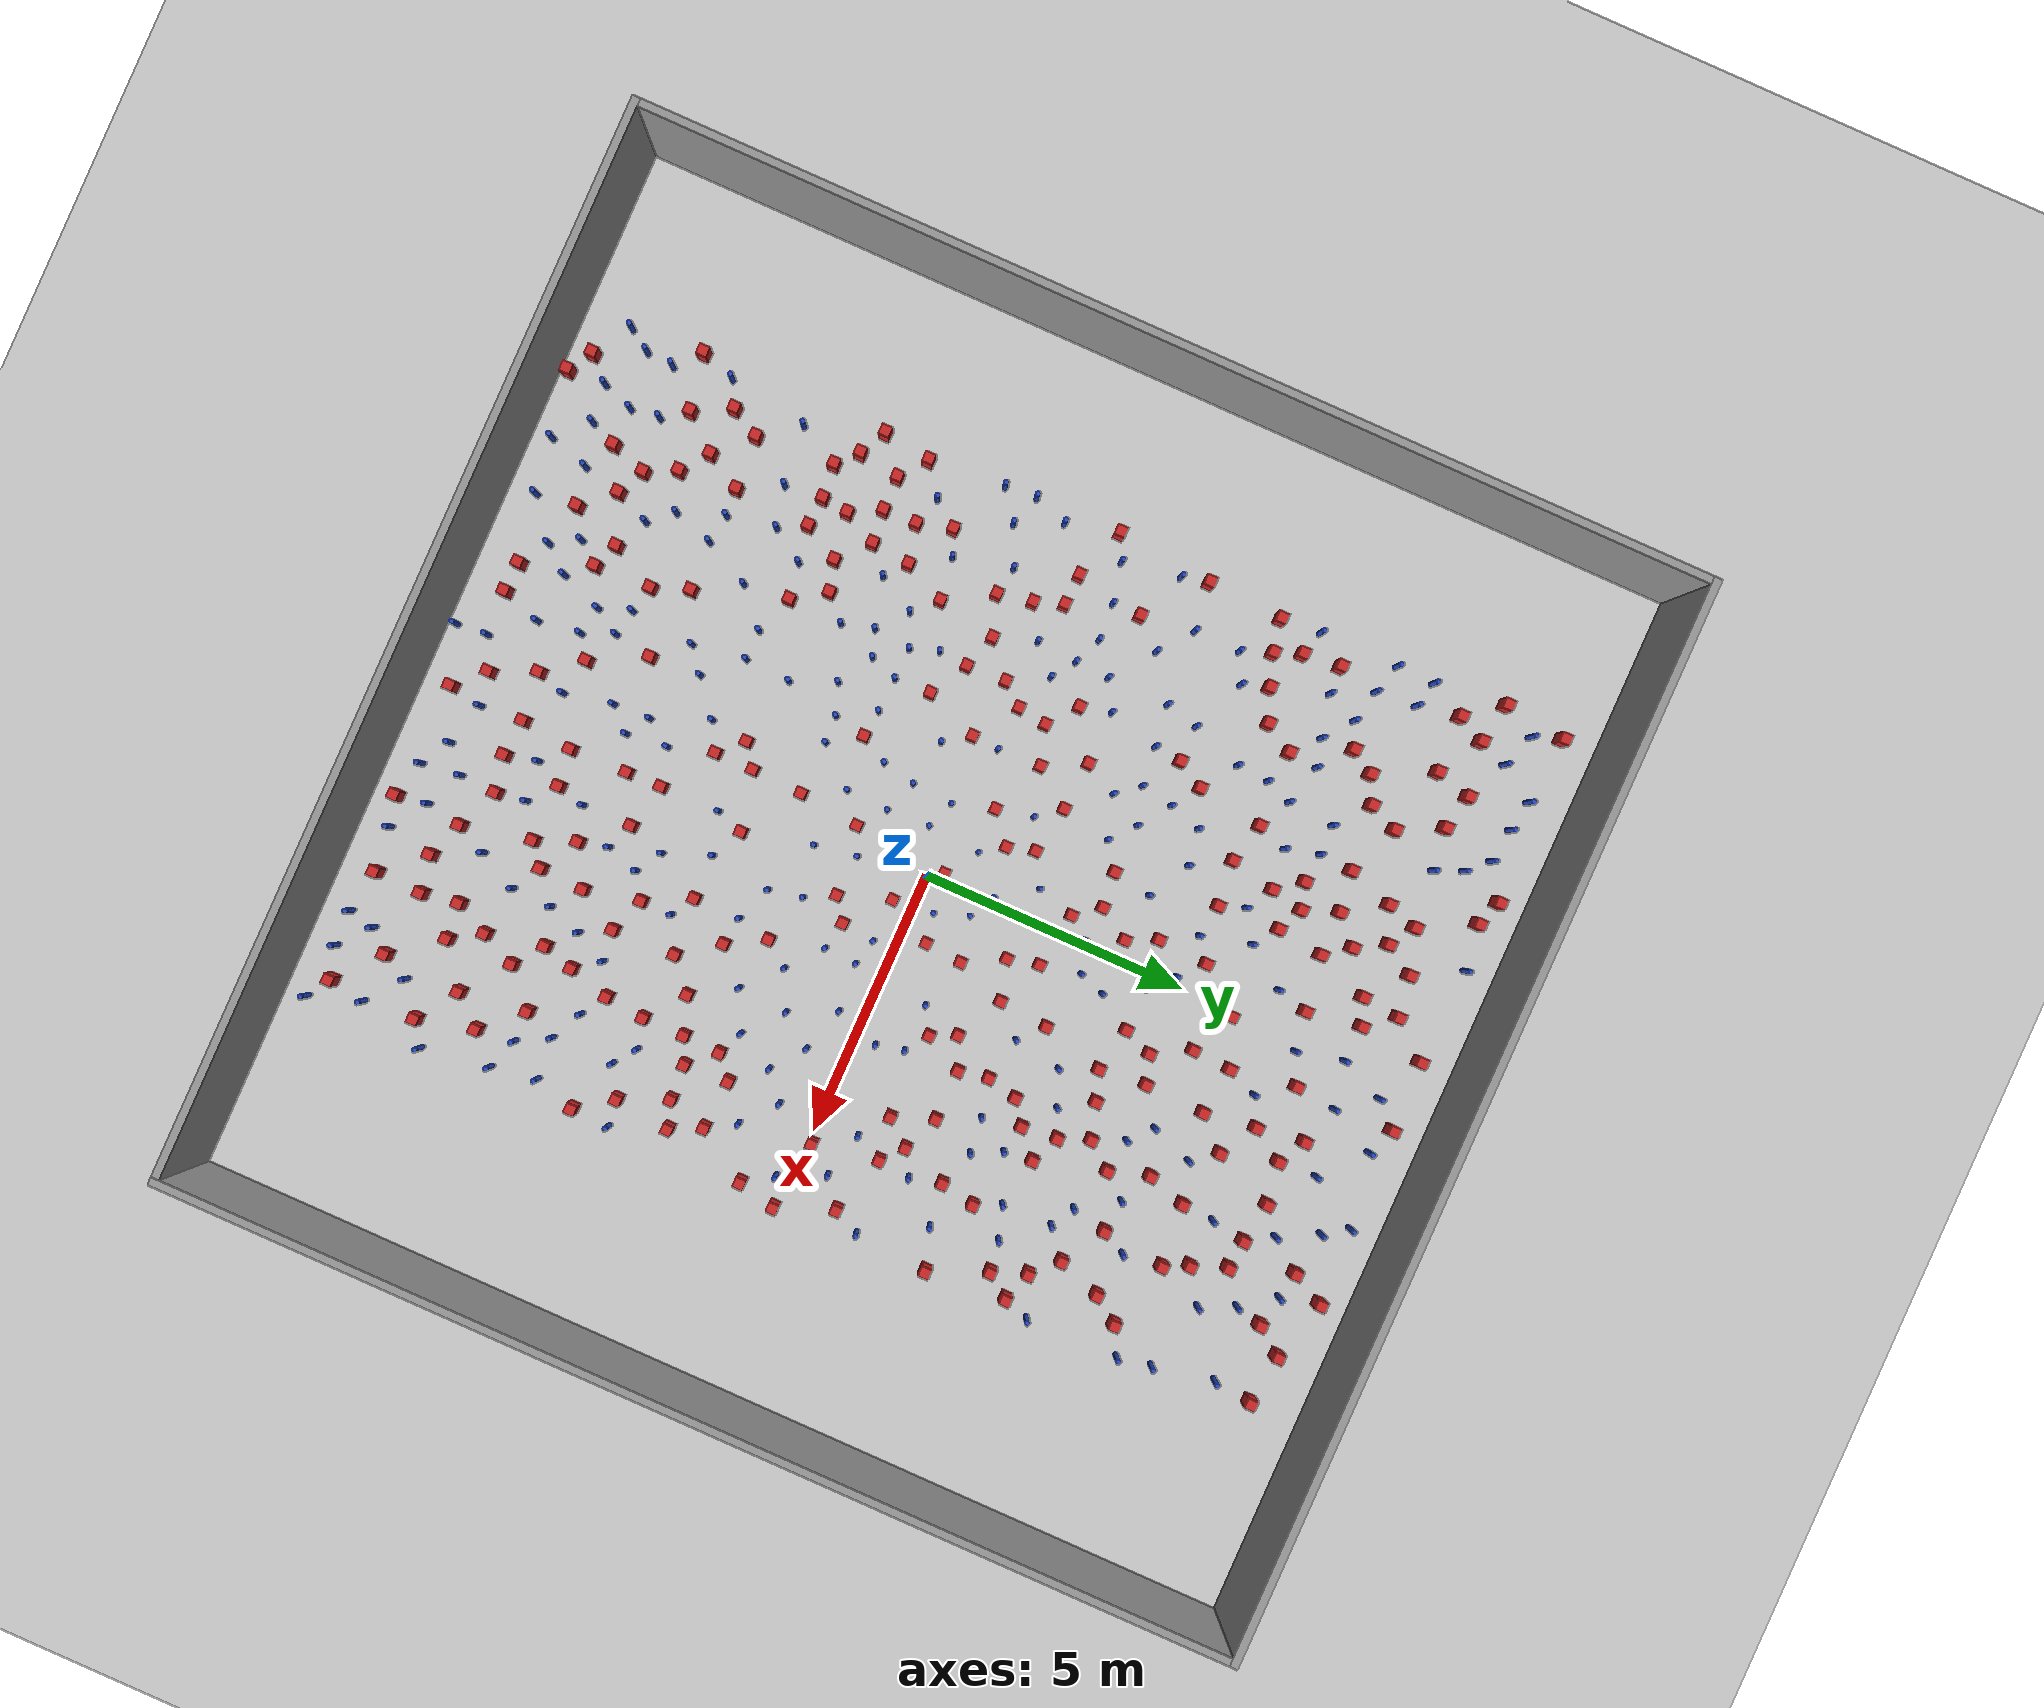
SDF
<sdf version="1.6">
 <world name="default">
  <light name="sun" type="directional">
   <pose>0 0 1000 0 -0 0</pose>
   <diffuse>0.8 0.8 0.8 1</diffuse>
   <specular>0.1 0.1 0.1 1</specular>
   <attenuation>
    <range>1000</range>
    <constant>0.9</constant>
    <linear>0.01</linear>
    <quadratic>0.001</quadratic>
   </attenuation>
   <direction>-0.5 0.5 -1</direction>
  </light>
  <model name="ground_plane">
   <static>1</static>
   <link name="link">
    <collision name="collision">
     <geometry><plane><normal>0 0 1</normal><size>100 100</size></plane></geometry>
     <surface><friction><ode><mu>100</mu><mu2>50</mu2></ode></friction></surface>
    </collision>
    <visual name="visual">
     <cast_shadows>0</cast_shadows>
     <geometry><plane><normal>0 0 1</normal><size>100 100</size></plane></geometry>
     <material>
      <ambient>1.0 1.0 1.0 1.0</ambient>
      <diffuse>0.8 0.8 0.8 1.0</diffuse>
      <specular>0.01 0.01 0.01 1.000000</specular>
     </material>
    </visual>
   </link>
  </model>
  <gravity>0 0 -9.8</gravity>
  <magnetic_field>6e-06 2.3e-05 -4.2e-05</magnetic_field>
  <atmosphere type="adiabatic"/>
  <physics name="default_physics" default="0" type="ode">
   <max_step_size>0.001</max_step_size>
   <real_time_factor>1</real_time_factor>
   <real_time_update_rate>1000</real_time_update_rate>
  </physics>
  <scene><ambient>0.4 0.4 0.4 1</ambient><background>0.7 0.7 0.7 1</background><shadows>1</shadows></scene>
  <spherical_coordinates>
   <surface_model>EARTH_WGS84</surface_model>
   <latitude_deg>0</latitude_deg>
   <longitude_deg>0</longitude_deg>
   <elevation>0</elevation>
   <heading_deg>0</heading_deg>
  </spherical_coordinates>
  <plugin name="gazebo_occupancy_map" filename="libgazebo_2Dmap_plugin.so">
   <map_resolution>0.05</map_resolution>
   <map_topic>generated_map</map_topic>
   <map_height>0.01</map_height>
   <map_size_x>50</map_size_x>
   <map_size_y>50</map_size_y>
  </plugin>
  <model name="NamedLocations">
   <static>true</static>
   <link name="DefaultStart"><pose>8.5 0 0 0 0 3.14</pose></link>
  </model>
  <model name="20x20_walls">
   <pose>0.044518 0.176112 0 0 -0 0</pose>
   <link name="Wall_1">
    <collision name="Wall_1_Collision">
     <geometry><box><size>20 0.15 2.5</size></box></geometry>
     <pose>0 0 1.25 0 -0 0</pose>
    </collision>
    <visual name="Wall_1_Visual">
     <pose>0 0 1.25 0 -0 0</pose>
     <geometry><box><size>20 0.15 2.5</size></box></geometry>
     <material>
      <script><uri>file://media/materials/scripts/gazebo.material</uri><name>Gazebo/Grey</name></script>
      <ambient>0.976471 0.992157 1 1</ambient>
     </material>
     <meta><layer>0</layer></meta>
    </visual>
    <pose>0 9.925 0 0 -0 0</pose>
   </link>
   <link name="Wall_3">
    <collision name="Wall_3_Collision">
     <geometry><box><size>20 0.15 2.5</size></box></geometry>
     <pose>0 0 1.25 0 -0 0</pose>
    </collision>
    <visual name="Wall_3_Visual">
     <pose>0 0 1.25 0 -0 0</pose>
     <geometry><box><size>20 0.15 2.5</size></box></geometry>
     <material>
      <script><uri>file://media/materials/scripts/gazebo.material</uri><name>Gazebo/Grey</name></script>
      <ambient>0.976471 0.992157 1 1</ambient>
     </material>
     <meta><layer>0</layer></meta>
    </visual>
    <pose>9.925 0 0 0 0 -1.5708</pose>
   </link>
   <link name="Wall_4">
    <collision name="Wall_4_Collision">
     <geometry><box><size>20 0.15 2.5</size></box></geometry>
     <pose>0 0 1.25 0 -0 0</pose>
    </collision>
    <visual name="Wall_4_Visual">
     <pose>0 0 1.25 0 -0 0</pose>
     <geometry><box><size>20 0.15 2.5</size></box></geometry>
     <material>
      <script><uri>file://media/materials/scripts/gazebo.material</uri><name>Gazebo/Grey</name></script>
      <ambient>0.976471 0.992157 1 1</ambient>
     </material>
     <meta><layer>0</layer></meta>
    </visual>
    <pose>0 -9.925 0 0 -0 3.14159</pose>
   </link>
   <link name="Wall_5">
    <collision name="Wall_5_Collision">
     <geometry><box><size>20 0.15 2.5</size></box></geometry>
     <pose>0 0 1.25 0 -0 0</pose>
    </collision>
    <visual name="Wall_5_Visual">
     <pose>0 0 1.25 0 -0 0</pose>
     <geometry><box><size>20 0.15 2.5</size></box></geometry>
     <material>
      <script><uri>file://media/materials/scripts/gazebo.material</uri><name>Gazebo/Grey</name></script>
      <ambient>0.976471 0.992157 1 1</ambient>
     </material>
     <meta><layer>0</layer></meta>
    </visual>
    <pose>-9.925 0 0 0 -0 1.5708</pose>
   </link>
   <static>1</static>
  </model>
  <model name="square_post_obstacle0">
   <static>true</static>
   <pose>1.71352744316 7.17949015912 1.91545236811e-07 -7.35059704564e-06 1.12565212e-07 2.39332434364e-05</pose>
   <link name="link">
    <pose>0 0 0.25 0 -0 0</pose>
    <inertial>
     <mass>100</mass>
     <inertia>
      <ixx>0.166667</ixx>
      <ixy>0</ixy>
      <ixz>0</ixz>
      <iyy>0.166667</iyy>
      <iyz>0</iyz>
      <izz>0.166667</izz>
     </inertia>
    </inertial>
    <collision name="collision"><geometry><box><size>.2 .2 .5</size></box></geometry></collision>
    <visual name="visual">
     <geometry><box><size>.2 .2 .5</size></box></geometry>
     <material>
      <script><name>Gazebo/Red</name><uri>file://media/materials/scripts/gazebo.material</uri></script>
     </material>
    </visual>
   </link>
  </model>
  <model name="square_post_obstacle1">
   <static>true</static>
   <pose>-6.39491690742 -4.133903235 1.91545236811e-07 -7.35059704564e-06 1.12565212e-07 2.39332434364e-05</pose>
   <link name="link">
    <pose>0 0 0.25 0 -0 0</pose>
    <inertial>
     <mass>100</mass>
     <inertia>
      <ixx>0.166667</ixx>
      <ixy>0</ixy>
      <ixz>0</ixz>
      <iyy>0.166667</iyy>
      <iyz>0</iyz>
      <izz>0.166667</izz>
     </inertia>
    </inertial>
    <collision name="collision"><geometry><box><size>.2 .2 .5</size></box></geometry></collision>
    <visual name="visual">
     <geometry><box><size>.2 .2 .5</size></box></geometry>
     <material>
      <script><name>Gazebo/Red</name><uri>file://media/materials/scripts/gazebo.material</uri></script>
     </material>
    </visual>
   </link>
  </model>
  <model name="pole_obstacle0">
   <static>true</static>
   <pose>-4.56092497138 -2.88060455729 7.38925637345e-09 -8.47170692798e-08 1.24976764937e-08 -1.74513093023e-07</pose>
   <link name="link">
    <pose>0 0 0.3 0 -0 0</pose>
    <inertial>
     <mass>1</mass>
     <inertia><ixx>0.145833</ixx><ixy>0</ixy><ixz>0</ixz><iyy>0.145833</iyy><iyz>0</iyz><izz>0.125</izz></inertia>
    </inertial>
    <collision name="collision">
     <geometry><cylinder><radius>0.05</radius><length>.6</length></cylinder></geometry>
    </collision>
    <visual name="visual">
     <geometry><cylinder><radius>0.05</radius><length>.6</length></cylinder></geometry>
     <material>
      <script><name>Gazebo/Blue</name><uri>file://media/materials/scripts/gazebo.material</uri></script>
     </material>
    </visual>
   </link>
  </model>
  <model name="square_post_obstacle2">
   <static>true</static>
   <pose>-6.45599153415 7.52745173422 1.91545236811e-07 -7.35059704564e-06 1.12565212e-07 2.39332434364e-05</pose>
   <link name="link">
    <pose>0 0 0.25 0 -0 0</pose>
    <inertial>
     <mass>100</mass>
     <inertia>
      <ixx>0.166667</ixx>
      <ixy>0</ixy>
      <ixz>0</ixz>
      <iyy>0.166667</iyy>
      <iyz>0</iyz>
      <izz>0.166667</izz>
     </inertia>
    </inertial>
    <collision name="collision"><geometry><box><size>.2 .2 .5</size></box></geometry></collision>
    <visual name="visual">
     <geometry><box><size>.2 .2 .5</size></box></geometry>
     <material>
      <script><name>Gazebo/Red</name><uri>file://media/materials/scripts/gazebo.material</uri></script>
     </material>
    </visual>
   </link>
  </model>
  <model name="pole_obstacle1">
   <static>true</static>
   <pose>-4.53239259562 2.68405552676 7.38925637345e-09 -8.47170692798e-08 1.24976764937e-08 -1.74513093023e-07</pose>
   <link name="link">
    <pose>0 0 0.3 0 -0 0</pose>
    <inertial>
     <mass>1</mass>
     <inertia><ixx>0.145833</ixx><ixy>0</ixy><ixz>0</ixz><iyy>0.145833</iyy><iyz>0</iyz><izz>0.125</izz></inertia>
    </inertial>
    <collision name="collision">
     <geometry><cylinder><radius>0.05</radius><length>.6</length></cylinder></geometry>
    </collision>
    <visual name="visual">
     <geometry><cylinder><radius>0.05</radius><length>.6</length></cylinder></geometry>
     <material>
      <script><name>Gazebo/Blue</name><uri>file://media/materials/scripts/gazebo.material</uri></script>
     </material>
    </visual>
   </link>
  </model>
  <model name="square_post_obstacle3">
   <static>true</static>
   <pose>4.49015289714 -7.34152833254 1.91545236811e-07 -7.35059704564e-06 1.12565212e-07 2.39332434364e-05</pose>
   <link name="link">
    <pose>0 0 0.25 0 -0 0</pose>
    <inertial>
     <mass>100</mass>
     <inertia>
      <ixx>0.166667</ixx>
      <ixy>0</ixy>
      <ixz>0</ixz>
      <iyy>0.166667</iyy>
      <iyz>0</iyz>
      <izz>0.166667</izz>
     </inertia>
    </inertial>
    <collision name="collision"><geometry><box><size>.2 .2 .5</size></box></geometry></collision>
    <visual name="visual">
     <geometry><box><size>.2 .2 .5</size></box></geometry>
     <material>
      <script><name>Gazebo/Red</name><uri>file://media/materials/scripts/gazebo.material</uri></script>
     </material>
    </visual>
   </link>
  </model>
  <model name="pole_obstacle2">
   <static>true</static>
   <pose>4.7720172906 -0.747344427278 7.38925637345e-09 -8.47170692799e-08 1.24976765038e-08 -1.74513093018e-07</pose>
   <link name="link">
    <pose>0 0 0.3 0 -0 0</pose>
    <inertial>
     <mass>1</mass>
     <inertia><ixx>0.145833</ixx><ixy>0</ixy><ixz>0</ixz><iyy>0.145833</iyy><iyz>0</iyz><izz>0.125</izz></inertia>
    </inertial>
    <collision name="collision">
     <geometry><cylinder><radius>0.05</radius><length>.6</length></cylinder></geometry>
    </collision>
    <visual name="visual">
     <geometry><cylinder><radius>0.05</radius><length>.6</length></cylinder></geometry>
     <material>
      <script><name>Gazebo/Blue</name><uri>file://media/materials/scripts/gazebo.material</uri></script>
     </material>
    </visual>
   </link>
  </model>
  <model name="pole_obstacle3">
   <static>true</static>
   <pose>2.74798672065 6.31970369617 7.38925637345e-09 -8.47170692798e-08 1.24976765033e-08 -1.74513093019e-07</pose>
   <link name="link">
    <pose>0 0 0.3 0 -0 0</pose>
    <inertial>
     <mass>1</mass>
     <inertia><ixx>0.145833</ixx><ixy>0</ixy><ixz>0</ixz><iyy>0.145833</iyy><iyz>0</iyz><izz>0.125</izz></inertia>
    </inertial>
    <collision name="collision">
     <geometry><cylinder><radius>0.05</radius><length>.6</length></cylinder></geometry>
    </collision>
    <visual name="visual">
     <geometry><cylinder><radius>0.05</radius><length>.6</length></cylinder></geometry>
     <material>
      <script><name>Gazebo/Blue</name><uri>file://media/materials/scripts/gazebo.material</uri></script>
     </material>
    </visual>
   </link>
  </model>
  <model name="square_post_obstacle4">
   <static>true</static>
   <pose>-2.685615217 -6.57738315095 1.91545236811e-07 -7.35059704564e-06 1.12565212e-07 2.39332434364e-05</pose>
   <link name="link">
    <pose>0 0 0.25 0 -0 0</pose>
    <inertial>
     <mass>100</mass>
     <inertia>
      <ixx>0.166667</ixx>
      <ixy>0</ixy>
      <ixz>0</ixz>
      <iyy>0.166667</iyy>
      <iyz>0</iyz>
      <izz>0.166667</izz>
     </inertia>
    </inertial>
    <collision name="collision"><geometry><box><size>.2 .2 .5</size></box></geometry></collision>
    <visual name="visual">
     <geometry><box><size>.2 .2 .5</size></box></geometry>
     <material>
      <script><name>Gazebo/Red</name><uri>file://media/materials/scripts/gazebo.material</uri></script>
     </material>
    </visual>
   </link>
  </model>
  <model name="square_post_obstacle5">
   <static>true</static>
   <pose>-3.91053096083 -3.63383336652 1.91545236811e-07 -7.35059704564e-06 1.12565212e-07 2.39332434364e-05</pose>
   <link name="link">
    <pose>0 0 0.25 0 -0 0</pose>
    <inertial>
     <mass>100</mass>
     <inertia>
      <ixx>0.166667</ixx>
      <ixy>0</ixy>
      <ixz>0</ixz>
      <iyy>0.166667</iyy>
      <iyz>0</iyz>
      <izz>0.166667</izz>
     </inertia>
    </inertial>
    <collision name="collision"><geometry><box><size>.2 .2 .5</size></box></geometry></collision>
    <visual name="visual">
     <geometry><box><size>.2 .2 .5</size></box></geometry>
     <material>
      <script><name>Gazebo/Red</name><uri>file://media/materials/scripts/gazebo.material</uri></script>
     </material>
    </visual>
   </link>
  </model>
  <model name="square_post_obstacle6">
   <static>true</static>
   <pose>-3.00124397409 -1.26506533317 1.91545236811e-07 -7.35059704564e-06 1.12565212e-07 2.39332434364e-05</pose>
   <link name="link">
    <pose>0 0 0.25 0 -0 0</pose>
    <inertial>
     <mass>100</mass>
     <inertia>
      <ixx>0.166667</ixx>
      <ixy>0</ixy>
      <ixz>0</ixz>
      <iyy>0.166667</iyy>
      <iyz>0</iyz>
      <izz>0.166667</izz>
     </inertia>
    </inertial>
    <collision name="collision"><geometry><box><size>.2 .2 .5</size></box></geometry></collision>
    <visual name="visual">
     <geometry><box><size>.2 .2 .5</size></box></geometry>
     <material>
      <script><name>Gazebo/Red</name><uri>file://media/materials/scripts/gazebo.material</uri></script>
     </material>
    </visual>
   </link>
  </model>
  <model name="pole_obstacle4">
   <static>true</static>
   <pose>-1.00049105903 4.87308313826 7.38925637345e-09 -8.47170692799e-08 1.2497676505e-08 -1.74513093018e-07</pose>
   <link name="link">
    <pose>0 0 0.3 0 -0 0</pose>
    <inertial>
     <mass>1</mass>
     <inertia><ixx>0.145833</ixx><ixy>0</ixy><ixz>0</ixz><iyy>0.145833</iyy><iyz>0</iyz><izz>0.125</izz></inertia>
    </inertial>
    <collision name="collision">
     <geometry><cylinder><radius>0.05</radius><length>.6</length></cylinder></geometry>
    </collision>
    <visual name="visual">
     <geometry><cylinder><radius>0.05</radius><length>.6</length></cylinder></geometry>
     <material>
      <script><name>Gazebo/Blue</name><uri>file://media/materials/scripts/gazebo.material</uri></script>
     </material>
    </visual>
   </link>
  </model>
  <model name="pole_obstacle5">
   <static>true</static>
   <pose>-5.31654070944 2.11592072659 7.38925637345e-09 -8.47170692798e-08 1.24976764937e-08 -1.74513093023e-07</pose>
   <link name="link">
    <pose>0 0 0.3 0 -0 0</pose>
    <inertial>
     <mass>1</mass>
     <inertia><ixx>0.145833</ixx><ixy>0</ixy><ixz>0</ixz><iyy>0.145833</iyy><iyz>0</iyz><izz>0.125</izz></inertia>
    </inertial>
    <collision name="collision">
     <geometry><cylinder><radius>0.05</radius><length>.6</length></cylinder></geometry>
    </collision>
    <visual name="visual">
     <geometry><cylinder><radius>0.05</radius><length>.6</length></cylinder></geometry>
     <material>
      <script><name>Gazebo/Blue</name><uri>file://media/materials/scripts/gazebo.material</uri></script>
     </material>
    </visual>
   </link>
  </model>
  <model name="square_post_obstacle7">
   <static>true</static>
   <pose>-5.77643210052 1.59069159847 1.91545236811e-07 -7.35059704564e-06 1.12565212e-07 2.39332434364e-05</pose>
   <link name="link">
    <pose>0 0 0.25 0 -0 0</pose>
    <inertial>
     <mass>100</mass>
     <inertia>
      <ixx>0.166667</ixx>
      <ixy>0</ixy>
      <ixz>0</ixz>
      <iyy>0.166667</iyy>
      <iyz>0</iyz>
      <izz>0.166667</izz>
     </inertia>
    </inertial>
    <collision name="collision"><geometry><box><size>.2 .2 .5</size></box></geometry></collision>
    <visual name="visual">
     <geometry><box><size>.2 .2 .5</size></box></geometry>
     <material>
      <script><name>Gazebo/Red</name><uri>file://media/materials/scripts/gazebo.material</uri></script>
     </material>
    </visual>
   </link>
  </model>
  <model name="square_post_obstacle8">
   <static>true</static>
   <pose>4.57625986904 1.62111247011 1.91545236811e-07 -7.35059704564e-06 1.12565212e-07 2.39332434364e-05</pose>
   <link name="link">
    <pose>0 0 0.25 0 -0 0</pose>
    <inertial>
     <mass>100</mass>
     <inertia>
      <ixx>0.166667</ixx>
      <ixy>0</ixy>
      <ixz>0</ixz>
      <iyy>0.166667</iyy>
      <iyz>0</iyz>
      <izz>0.166667</izz>
     </inertia>
    </inertial>
    <collision name="collision"><geometry><box><size>.2 .2 .5</size></box></geometry></collision>
    <visual name="visual">
     <geometry><box><size>.2 .2 .5</size></box></geometry>
     <material>
      <script><name>Gazebo/Red</name><uri>file://media/materials/scripts/gazebo.material</uri></script>
     </material>
    </visual>
   </link>
  </model>
  <model name="pole_obstacle6">
   <static>true</static>
   <pose>3.88461171138 5.51924652221 7.38925637345e-09 -8.47170692798e-08 1.24976765033e-08 -1.74513093019e-07</pose>
   <link name="link">
    <pose>0 0 0.3 0 -0 0</pose>
    <inertial>
     <mass>1</mass>
     <inertia><ixx>0.145833</ixx><ixy>0</ixy><ixz>0</ixz><iyy>0.145833</iyy><iyz>0</iyz><izz>0.125</izz></inertia>
    </inertial>
    <collision name="collision">
     <geometry><cylinder><radius>0.05</radius><length>.6</length></cylinder></geometry>
    </collision>
    <visual name="visual">
     <geometry><cylinder><radius>0.05</radius><length>.6</length></cylinder></geometry>
     <material>
      <script><name>Gazebo/Blue</name><uri>file://media/materials/scripts/gazebo.material</uri></script>
     </material>
    </visual>
   </link>
  </model>
  <model name="pole_obstacle7">
   <static>true</static>
   <pose>-5.67325957505 -8.79444779382 7.38925637345e-09 -8.471706928e-08 1.24976765081e-08 -1.74513093015e-07</pose>
   <link name="link">
    <pose>0 0 0.3 0 -0 0</pose>
    <inertial>
     <mass>1</mass>
     <inertia><ixx>0.145833</ixx><ixy>0</ixy><ixz>0</ixz><iyy>0.145833</iyy><iyz>0</iyz><izz>0.125</izz></inertia>
    </inertial>
    <collision name="collision">
     <geometry><cylinder><radius>0.05</radius><length>.6</length></cylinder></geometry>
    </collision>
    <visual name="visual">
     <geometry><cylinder><radius>0.05</radius><length>.6</length></cylinder></geometry>
     <material>
      <script><name>Gazebo/Blue</name><uri>file://media/materials/scripts/gazebo.material</uri></script>
     </material>
    </visual>
   </link>
  </model>
  <model name="square_post_obstacle9">
   <static>true</static>
   <pose>-4.86696928809 6.47936747951 1.91545236811e-07 -7.35059704564e-06 1.12565212e-07 2.39332434364e-05</pose>
   <link name="link">
    <pose>0 0 0.25 0 -0 0</pose>
    <inertial>
     <mass>100</mass>
     <inertia>
      <ixx>0.166667</ixx>
      <ixy>0</ixy>
      <ixz>0</ixz>
      <iyy>0.166667</iyy>
      <iyz>0</iyz>
      <izz>0.166667</izz>
     </inertia>
    </inertial>
    <collision name="collision"><geometry><box><size>.2 .2 .5</size></box></geometry></collision>
    <visual name="visual">
     <geometry><box><size>.2 .2 .5</size></box></geometry>
     <material>
      <script><name>Gazebo/Red</name><uri>file://media/materials/scripts/gazebo.material</uri></script>
     </material>
    </visual>
   </link>
  </model>
  <model name="square_post_obstacle10">
   <static>true</static>
   <pose>1.76560631317 -7.61351531478 1.91545236811e-07 -7.35059704564e-06 1.12565212e-07 2.39332434364e-05</pose>
   <link name="link">
    <pose>0 0 0.25 0 -0 0</pose>
    <inertial>
     <mass>100</mass>
     <inertia>
      <ixx>0.166667</ixx>
      <ixy>0</ixy>
      <ixz>0</ixz>
      <iyy>0.166667</iyy>
      <iyz>0</iyz>
      <izz>0.166667</izz>
     </inertia>
    </inertial>
    <collision name="collision"><geometry><box><size>.2 .2 .5</size></box></geometry></collision>
    <visual name="visual">
     <geometry><box><size>.2 .2 .5</size></box></geometry>
     <material>
      <script><name>Gazebo/Red</name><uri>file://media/materials/scripts/gazebo.material</uri></script>
     </material>
    </visual>
   </link>
  </model>
  <model name="square_post_obstacle11">
   <static>true</static>
   <pose>-0.696263297723 8.16231639691 1.91545236811e-07 -7.35059704564e-06 1.12565212e-07 2.39332434364e-05</pose>
   <link name="link">
    <pose>0 0 0.25 0 -0 0</pose>
    <inertial>
     <mass>100</mass>
     <inertia>
      <ixx>0.166667</ixx>
      <ixy>0</ixy>
      <ixz>0</ixz>
      <iyy>0.166667</iyy>
      <iyz>0</iyz>
      <izz>0.166667</izz>
     </inertia>
    </inertial>
    <collision name="collision"><geometry><box><size>.2 .2 .5</size></box></geometry></collision>
    <visual name="visual">
     <geometry><box><size>.2 .2 .5</size></box></geometry>
     <material>
      <script><name>Gazebo/Red</name><uri>file://media/materials/scripts/gazebo.material</uri></script>
     </material>
    </visual>
   </link>
  </model>
  <model name="square_post_obstacle12">
   <static>true</static>
   <pose>-1.58455548169 0.633229365497 1.91545236811e-07 -7.35059704564e-06 1.12565212e-07 2.39332434364e-05</pose>
   <link name="link">
    <pose>0 0 0.25 0 -0 0</pose>
    <inertial>
     <mass>100</mass>
     <inertia>
      <ixx>0.166667</ixx>
      <ixy>0</ixy>
      <ixz>0</ixz>
      <iyy>0.166667</iyy>
      <iyz>0</iyz>
      <izz>0.166667</izz>
     </inertia>
    </inertial>
    <collision name="collision"><geometry><box><size>.2 .2 .5</size></box></geometry></collision>
    <visual name="visual">
     <geometry><box><size>.2 .2 .5</size></box></geometry>
     <material>
      <script><name>Gazebo/Red</name><uri>file://media/materials/scripts/gazebo.material</uri></script>
     </material>
    </visual>
   </link>
  </model>
  <model name="square_post_obstacle13">
   <static>true</static>
   <pose>-4.95018046901 4.452941867 1.91545236811e-07 -7.35059704564e-06 1.12565212e-07 2.39332434364e-05</pose>
   <link name="link">
    <pose>0 0 0.25 0 -0 0</pose>
    <inertial>
     <mass>100</mass>
     <inertia>
      <ixx>0.166667</ixx>
      <ixy>0</ixy>
      <ixz>0</ixz>
      <iyy>0.166667</iyy>
      <iyz>0</iyz>
      <izz>0.166667</izz>
     </inertia>
    </inertial>
    <collision name="collision"><geometry><box><size>.2 .2 .5</size></box></geometry></collision>
    <visual name="visual">
     <geometry><box><size>.2 .2 .5</size></box></geometry>
     <material>
      <script><name>Gazebo/Red</name><uri>file://media/materials/scripts/gazebo.material</uri></script>
     </material>
    </visual>
   </link>
  </model>
  <model name="pole_obstacle8">
   <static>true</static>
   <pose>-4.17518788709 -2.18737991646 7.38925637345e-09 -8.47170692798e-08 1.24976764937e-08 -1.74513093023e-07</pose>
   <link name="link">
    <pose>0 0 0.3 0 -0 0</pose>
    <inertial>
     <mass>1</mass>
     <inertia><ixx>0.145833</ixx><ixy>0</ixy><ixz>0</ixz><iyy>0.145833</iyy><iyz>0</iyz><izz>0.125</izz></inertia>
    </inertial>
    <collision name="collision">
     <geometry><cylinder><radius>0.05</radius><length>.6</length></cylinder></geometry>
    </collision>
    <visual name="visual">
     <geometry><cylinder><radius>0.05</radius><length>.6</length></cylinder></geometry>
     <material>
      <script><name>Gazebo/Blue</name><uri>file://media/materials/scripts/gazebo.material</uri></script>
     </material>
    </visual>
   </link>
  </model>
  <model name="square_post_obstacle14">
   <static>true</static>
   <pose>2.10513833273 7.78706468619 1.91545236811e-07 -7.35059704564e-06 1.12565212e-07 2.39332434364e-05</pose>
   <link name="link">
    <pose>0 0 0.25 0 -0 0</pose>
    <inertial>
     <mass>100</mass>
     <inertia>
      <ixx>0.166667</ixx>
      <ixy>0</ixy>
      <ixz>0</ixz>
      <iyy>0.166667</iyy>
      <iyz>0</iyz>
      <izz>0.166667</izz>
     </inertia>
    </inertial>
    <collision name="collision"><geometry><box><size>.2 .2 .5</size></box></geometry></collision>
    <visual name="visual">
     <geometry><box><size>.2 .2 .5</size></box></geometry>
     <material>
      <script><name>Gazebo/Red</name><uri>file://media/materials/scripts/gazebo.material</uri></script>
     </material>
    </visual>
   </link>
  </model>
  <model name="square_post_obstacle15">
   <static>true</static>
   <pose>5.75156060621 -6.21697039321 1.91545236811e-07 -7.35059704564e-06 1.12565212e-07 2.39332434364e-05</pose>
   <link name="link">
    <pose>0 0 0.25 0 -0 0</pose>
    <inertial>
     <mass>100</mass>
     <inertia>
      <ixx>0.166667</ixx>
      <ixy>0</ixy>
      <ixz>0</ixz>
      <iyy>0.166667</iyy>
      <iyz>0</iyz>
      <izz>0.166667</izz>
     </inertia>
    </inertial>
    <collision name="collision"><geometry><box><size>.2 .2 .5</size></box></geometry></collision>
    <visual name="visual">
     <geometry><box><size>.2 .2 .5</size></box></geometry>
     <material>
      <script><name>Gazebo/Red</name><uri>file://media/materials/scripts/gazebo.material</uri></script>
     </material>
    </visual>
   </link>
  </model>
  <model name="square_post_obstacle16">
   <static>true</static>
   <pose>-0.590210509465 5.18321853976 1.91545236811e-07 -7.35059704564e-06 1.12565212e-07 2.39332434364e-05</pose>
   <link name="link">
    <pose>0 0 0.25 0 -0 0</pose>
    <inertial>
     <mass>100</mass>
     <inertia>
      <ixx>0.166667</ixx>
      <ixy>0</ixy>
      <ixz>0</ixz>
      <iyy>0.166667</iyy>
      <iyz>0</iyz>
      <izz>0.166667</izz>
     </inertia>
    </inertial>
    <collision name="collision"><geometry><box><size>.2 .2 .5</size></box></geometry></collision>
    <visual name="visual">
     <geometry><box><size>.2 .2 .5</size></box></geometry>
     <material>
      <script><name>Gazebo/Red</name><uri>file://media/materials/scripts/gazebo.material</uri></script>
     </material>
    </visual>
   </link>
  </model>
  <model name="pole_obstacle9">
   <static>true</static>
   <pose>-3.39660632281 -9.13306367596 7.38925637345e-09 -8.47170692793e-08 1.24976764408e-08 -1.74513093041e-07</pose>
   <link name="link">
    <pose>0 0 0.3 0 -0 0</pose>
    <inertial>
     <mass>1</mass>
     <inertia><ixx>0.145833</ixx><ixy>0</ixy><ixz>0</ixz><iyy>0.145833</iyy><iyz>0</iyz><izz>0.125</izz></inertia>
    </inertial>
    <collision name="collision">
     <geometry><cylinder><radius>0.05</radius><length>.6</length></cylinder></geometry>
    </collision>
    <visual name="visual">
     <geometry><cylinder><radius>0.05</radius><length>.6</length></cylinder></geometry>
     <material>
      <script><name>Gazebo/Blue</name><uri>file://media/materials/scripts/gazebo.material</uri></script>
     </material>
    </visual>
   </link>
  </model>
  <model name="square_post_obstacle17">
   <static>true</static>
   <pose>-5.90727312958 -5.95352216469 1.91545236811e-07 -7.35059704564e-06 1.12565212e-07 2.39332434364e-05</pose>
   <link name="link">
    <pose>0 0 0.25 0 -0 0</pose>
    <inertial>
     <mass>100</mass>
     <inertia>
      <ixx>0.166667</ixx>
      <ixy>0</ixy>
      <ixz>0</ixz>
      <iyy>0.166667</iyy>
      <iyz>0</iyz>
      <izz>0.166667</izz>
     </inertia>
    </inertial>
    <collision name="collision"><geometry><box><size>.2 .2 .5</size></box></geometry></collision>
    <visual name="visual">
     <geometry><box><size>.2 .2 .5</size></box></geometry>
     <material>
      <script><name>Gazebo/Red</name><uri>file://media/materials/scripts/gazebo.material</uri></script>
     </material>
    </visual>
   </link>
  </model>
  <model name="square_post_obstacle18">
   <static>true</static>
   <pose>0.964357316819 -1.32385810969 1.91545236811e-07 -7.35059704564e-06 1.12565212e-07 2.39332434364e-05</pose>
   <link name="link">
    <pose>0 0 0.25 0 -0 0</pose>
    <inertial>
     <mass>100</mass>
     <inertia>
      <ixx>0.166667</ixx>
      <ixy>0</ixy>
      <ixz>0</ixz>
      <iyy>0.166667</iyy>
      <iyz>0</iyz>
      <izz>0.166667</izz>
     </inertia>
    </inertial>
    <collision name="collision"><geometry><box><size>.2 .2 .5</size></box></geometry></collision>
    <visual name="visual">
     <geometry><box><size>.2 .2 .5</size></box></geometry>
     <material>
      <script><name>Gazebo/Red</name><uri>file://media/materials/scripts/gazebo.material</uri></script>
     </material>
    </visual>
   </link>
  </model>
  <model name="pole_obstacle10">
   <static>true</static>
   <pose>-3.96756192233 8.70898957246 7.38925637345e-09 -8.47170692798e-08 1.24976764891e-08 -1.74513093027e-07</pose>
   <link name="link">
    <pose>0 0 0.3 0 -0 0</pose>
    <inertial>
     <mass>1</mass>
     <inertia><ixx>0.145833</ixx><ixy>0</ixy><ixz>0</ixz><iyy>0.145833</iyy><iyz>0</iyz><izz>0.125</izz></inertia>
    </inertial>
    <collision name="collision">
     <geometry><cylinder><radius>0.05</radius><length>.6</length></cylinder></geometry>
    </collision>
    <visual name="visual">
     <geometry><cylinder><radius>0.05</radius><length>.6</length></cylinder></geometry>
     <material>
      <script><name>Gazebo/Blue</name><uri>file://media/materials/scripts/gazebo.material</uri></script>
     </material>
    </visual>
   </link>
  </model>
  <model name="square_post_obstacle19">
   <static>true</static>
   <pose>2.04800696063 -3.61474034839 1.91545236811e-07 -7.35059704564e-06 1.12565212e-07 2.39332434364e-05</pose>
   <link name="link">
    <pose>0 0 0.25 0 -0 0</pose>
    <inertial>
     <mass>100</mass>
     <inertia>
      <ixx>0.166667</ixx>
      <ixy>0</ixy>
      <ixz>0</ixz>
      <iyy>0.166667</iyy>
      <iyz>0</iyz>
      <izz>0.166667</izz>
     </inertia>
    </inertial>
    <collision name="collision"><geometry><box><size>.2 .2 .5</size></box></geometry></collision>
    <visual name="visual">
     <geometry><box><size>.2 .2 .5</size></box></geometry>
     <material>
      <script><name>Gazebo/Red</name><uri>file://media/materials/scripts/gazebo.material</uri></script>
     </material>
    </visual>
   </link>
  </model>
  <model name="pole_obstacle11">
   <static>true</static>
   <pose>0.478664716121 3.2279638088 7.38925637345e-09 -8.471706928e-08 1.24976765089e-08 -1.74513093016e-07</pose>
   <link name="link">
    <pose>0 0 0.3 0 -0 0</pose>
    <inertial>
     <mass>1</mass>
     <inertia><ixx>0.145833</ixx><ixy>0</ixy><ixz>0</ixz><iyy>0.145833</iyy><iyz>0</iyz><izz>0.125</izz></inertia>
    </inertial>
    <collision name="collision">
     <geometry><cylinder><radius>0.05</radius><length>.6</length></cylinder></geometry>
    </collision>
    <visual name="visual">
     <geometry><cylinder><radius>0.05</radius><length>.6</length></cylinder></geometry>
     <material>
      <script><name>Gazebo/Blue</name><uri>file://media/materials/scripts/gazebo.material</uri></script>
     </material>
    </visual>
   </link>
  </model>
  <model name="square_post_obstacle20">
   <static>true</static>
   <pose>-2.27867718137 5.71834548236 1.91545236811e-07 -7.35059704564e-06 1.12565212e-07 2.39332434364e-05</pose>
   <link name="link">
    <pose>0 0 0.25 0 -0 0</pose>
    <inertial>
     <mass>100</mass>
     <inertia>
      <ixx>0.166667</ixx>
      <ixy>0</ixy>
      <ixz>0</ixz>
      <iyy>0.166667</iyy>
      <iyz>0</iyz>
      <izz>0.166667</izz>
     </inertia>
    </inertial>
    <collision name="collision"><geometry><box><size>.2 .2 .5</size></box></geometry></collision>
    <visual name="visual">
     <geometry><box><size>.2 .2 .5</size></box></geometry>
     <material>
      <script><name>Gazebo/Red</name><uri>file://media/materials/scripts/gazebo.material</uri></script>
     </material>
    </visual>
   </link>
  </model>
  <model name="pole_obstacle12">
   <static>true</static>
   <pose>-6.31485896257 6.74035009021 7.38925637345e-09 -8.47170692796e-08 1.24976764786e-08 -1.74513093032e-07</pose>
   <link name="link">
    <pose>0 0 0.3 0 -0 0</pose>
    <inertial>
     <mass>1</mass>
     <inertia><ixx>0.145833</ixx><ixy>0</ixy><ixz>0</ixz><iyy>0.145833</iyy><iyz>0</iyz><izz>0.125</izz></inertia>
    </inertial>
    <collision name="collision">
     <geometry><cylinder><radius>0.05</radius><length>.6</length></cylinder></geometry>
    </collision>
    <visual name="visual">
     <geometry><cylinder><radius>0.05</radius><length>.6</length></cylinder></geometry>
     <material>
      <script><name>Gazebo/Blue</name><uri>file://media/materials/scripts/gazebo.material</uri></script>
     </material>
    </visual>
   </link>
  </model>
  <model name="square_post_obstacle21">
   <static>true</static>
   <pose>-6.20504115553 -6.49994313246 1.91545236811e-07 -7.35059704564e-06 1.12565212e-07 2.39332434364e-05</pose>
   <link name="link">
    <pose>0 0 0.25 0 -0 0</pose>
    <inertial>
     <mass>100</mass>
     <inertia>
      <ixx>0.166667</ixx>
      <ixy>0</ixy>
      <ixz>0</ixz>
      <iyy>0.166667</iyy>
      <iyz>0</iyz>
      <izz>0.166667</izz>
     </inertia>
    </inertial>
    <collision name="collision"><geometry><box><size>.2 .2 .5</size></box></geometry></collision>
    <visual name="visual">
     <geometry><box><size>.2 .2 .5</size></box></geometry>
     <material>
      <script><name>Gazebo/Red</name><uri>file://media/materials/scripts/gazebo.material</uri></script>
     </material>
    </visual>
   </link>
  </model>
  <model name="pole_obstacle13">
   <static>true</static>
   <pose>4.75919211775 -4.63325182389 7.38925637345e-09 -8.47170692796e-08 1.24976764786e-08 -1.74513093032e-07</pose>
   <link name="link">
    <pose>0 0 0.3 0 -0 0</pose>
    <inertial>
     <mass>1</mass>
     <inertia><ixx>0.145833</ixx><ixy>0</ixy><ixz>0</ixz><iyy>0.145833</iyy><iyz>0</iyz><izz>0.125</izz></inertia>
    </inertial>
    <collision name="collision">
     <geometry><cylinder><radius>0.05</radius><length>.6</length></cylinder></geometry>
    </collision>
    <visual name="visual">
     <geometry><cylinder><radius>0.05</radius><length>.6</length></cylinder></geometry>
     <material>
      <script><name>Gazebo/Blue</name><uri>file://media/materials/scripts/gazebo.material</uri></script>
     </material>
    </visual>
   </link>
  </model>
  <model name="square_post_obstacle22">
   <static>true</static>
   <pose>1.09951988133 0.476390049716 1.91545236811e-07 -7.35059704564e-06 1.12565212e-07 2.39332434364e-05</pose>
   <link name="link">
    <pose>0 0 0.25 0 -0 0</pose>
    <inertial>
     <mass>100</mass>
     <inertia>
      <ixx>0.166667</ixx>
      <ixy>0</ixy>
      <ixz>0</ixz>
      <iyy>0.166667</iyy>
      <iyz>0</iyz>
      <izz>0.166667</izz>
     </inertia>
    </inertial>
    <collision name="collision"><geometry><box><size>.2 .2 .5</size></box></geometry></collision>
    <visual name="visual">
     <geometry><box><size>.2 .2 .5</size></box></geometry>
     <material>
      <script><name>Gazebo/Red</name><uri>file://media/materials/scripts/gazebo.material</uri></script>
     </material>
    </visual>
   </link>
  </model>
  <model name="pole_obstacle14">
   <static>true</static>
   <pose>2.02225817843 2.63889635493 7.38925637345e-09 -8.47170692797e-08 1.24976764891e-08 -1.74513093027e-07</pose>
   <link name="link">
    <pose>0 0 0.3 0 -0 0</pose>
    <inertial>
     <mass>1</mass>
     <inertia><ixx>0.145833</ixx><ixy>0</ixy><ixz>0</ixz><iyy>0.145833</iyy><iyz>0</iyz><izz>0.125</izz></inertia>
    </inertial>
    <collision name="collision">
     <geometry><cylinder><radius>0.05</radius><length>.6</length></cylinder></geometry>
    </collision>
    <visual name="visual">
     <geometry><cylinder><radius>0.05</radius><length>.6</length></cylinder></geometry>
     <material>
      <script><name>Gazebo/Blue</name><uri>file://media/materials/scripts/gazebo.material</uri></script>
     </material>
    </visual>
   </link>
  </model>
  <model name="pole_obstacle15">
   <static>true</static>
   <pose>-6.21907409106 -2.55616111198 7.38925637345e-09 -8.47170692798e-08 1.24976764937e-08 -1.74513093023e-07</pose>
   <link name="link">
    <pose>0 0 0.3 0 -0 0</pose>
    <inertial>
     <mass>1</mass>
     <inertia><ixx>0.145833</ixx><ixy>0</ixy><ixz>0</ixz><iyy>0.145833</iyy><iyz>0</iyz><izz>0.125</izz></inertia>
    </inertial>
    <collision name="collision">
     <geometry><cylinder><radius>0.05</radius><length>.6</length></cylinder></geometry>
    </collision>
    <visual name="visual">
     <geometry><cylinder><radius>0.05</radius><length>.6</length></cylinder></geometry>
     <material>
      <script><name>Gazebo/Blue</name><uri>file://media/materials/scripts/gazebo.material</uri></script>
     </material>
    </visual>
   </link>
  </model>
  <model name="pole_obstacle16">
   <static>true</static>
   <pose>-6.63617168185 8.83300791756 7.38925637345e-09 -8.471706928e-08 1.24976765081e-08 -1.74513093015e-07</pose>
   <link name="link">
    <pose>0 0 0.3 0 -0 0</pose>
    <inertial>
     <mass>1</mass>
     <inertia><ixx>0.145833</ixx><ixy>0</ixy><ixz>0</ixz><iyy>0.145833</iyy><iyz>0</iyz><izz>0.125</izz></inertia>
    </inertial>
    <collision name="collision">
     <geometry><cylinder><radius>0.05</radius><length>.6</length></cylinder></geometry>
    </collision>
    <visual name="visual">
     <geometry><cylinder><radius>0.05</radius><length>.6</length></cylinder></geometry>
     <material>
      <script><name>Gazebo/Blue</name><uri>file://media/materials/scripts/gazebo.material</uri></script>
     </material>
    </visual>
   </link>
  </model>
  <model name="square_post_obstacle23">
   <static>true</static>
   <pose>4.18238607842 1.15388390437 1.91545236811e-07 -7.35059704564e-06 1.12565212e-07 2.39332434364e-05</pose>
   <link name="link">
    <pose>0 0 0.25 0 -0 0</pose>
    <inertial>
     <mass>100</mass>
     <inertia>
      <ixx>0.166667</ixx>
      <ixy>0</ixy>
      <ixz>0</ixz>
      <iyy>0.166667</iyy>
      <iyz>0</iyz>
      <izz>0.166667</izz>
     </inertia>
    </inertial>
    <collision name="collision"><geometry><box><size>.2 .2 .5</size></box></geometry></collision>
    <visual name="visual">
     <geometry><box><size>.2 .2 .5</size></box></geometry>
     <material>
      <script><name>Gazebo/Red</name><uri>file://media/materials/scripts/gazebo.material</uri></script>
     </material>
    </visual>
   </link>
  </model>
  <model name="pole_obstacle17">
   <static>true</static>
   <pose>-3.86469299405 -5.96399672373 7.38925637345e-09 -8.47170692794e-08 1.24976764468e-08 -1.7451309304e-07</pose>
   <link name="link">
    <pose>0 0 0.3 0 -0 0</pose>
    <inertial>
     <mass>1</mass>
     <inertia><ixx>0.145833</ixx><ixy>0</ixy><ixz>0</ixz><iyy>0.145833</iyy><iyz>0</iyz><izz>0.125</izz></inertia>
    </inertial>
    <collision name="collision">
     <geometry><cylinder><radius>0.05</radius><length>.6</length></cylinder></geometry>
    </collision>
    <visual name="visual">
     <geometry><cylinder><radius>0.05</radius><length>.6</length></cylinder></geometry>
     <material>
      <script><name>Gazebo/Blue</name><uri>file://media/materials/scripts/gazebo.material</uri></script>
     </material>
    </visual>
   </link>
  </model>
  <model name="square_post_obstacle24">
   <static>true</static>
   <pose>3.91813997311 -8.99396543054 1.91545236811e-07 -7.35059704564e-06 1.12565212e-07 2.39332434364e-05</pose>
   <link name="link">
    <pose>0 0 0.25 0 -0 0</pose>
    <inertial>
     <mass>100</mass>
     <inertia>
      <ixx>0.166667</ixx>
      <ixy>0</ixy>
      <ixz>0</ixz>
      <iyy>0.166667</iyy>
      <iyz>0</iyz>
      <izz>0.166667</izz>
     </inertia>
    </inertial>
    <collision name="collision"><geometry><box><size>.2 .2 .5</size></box></geometry></collision>
    <visual name="visual">
     <geometry><box><size>.2 .2 .5</size></box></geometry>
     <material>
      <script><name>Gazebo/Red</name><uri>file://media/materials/scripts/gazebo.material</uri></script>
     </material>
    </visual>
   </link>
  </model>
  <model name="square_post_obstacle25">
   <static>true</static>
   <pose>-5.20353006577 8.23097745979 1.91545236811e-07 -7.35059704564e-06 1.12565212e-07 2.39332434364e-05</pose>
   <link name="link">
    <pose>0 0 0.25 0 -0 0</pose>
    <inertial>
     <mass>100</mass>
     <inertia>
      <ixx>0.166667</ixx>
      <ixy>0</ixy>
      <ixz>0</ixz>
      <iyy>0.166667</iyy>
      <iyz>0</iyz>
      <izz>0.166667</izz>
     </inertia>
    </inertial>
    <collision name="collision"><geometry><box><size>.2 .2 .5</size></box></geometry></collision>
    <visual name="visual">
     <geometry><box><size>.2 .2 .5</size></box></geometry>
     <material>
      <script><name>Gazebo/Red</name><uri>file://media/materials/scripts/gazebo.material</uri></script>
     </material>
    </visual>
   </link>
  </model>
  <model name="square_post_obstacle26">
   <static>true</static>
   <pose>4.37403866077 -2.09080189724 1.91545236811e-07 -7.35059704564e-06 1.12565212e-07 2.39332434364e-05</pose>
   <link name="link">
    <pose>0 0 0.25 0 -0 0</pose>
    <inertial>
     <mass>100</mass>
     <inertia>
      <ixx>0.166667</ixx>
      <ixy>0</ixy>
      <ixz>0</ixz>
      <iyy>0.166667</iyy>
      <iyz>0</iyz>
      <izz>0.166667</izz>
     </inertia>
    </inertial>
    <collision name="collision"><geometry><box><size>.2 .2 .5</size></box></geometry></collision>
    <visual name="visual">
     <geometry><box><size>.2 .2 .5</size></box></geometry>
     <material>
      <script><name>Gazebo/Red</name><uri>file://media/materials/scripts/gazebo.material</uri></script>
     </material>
    </visual>
   </link>
  </model>
  <model name="square_post_obstacle27">
   <static>true</static>
   <pose>3.6452830637 7.7888560963 1.91545236811e-07 -7.35059704564e-06 1.12565212e-07 2.39332434364e-05</pose>
   <link name="link">
    <pose>0 0 0.25 0 -0 0</pose>
    <inertial>
     <mass>100</mass>
     <inertia>
      <ixx>0.166667</ixx>
      <ixy>0</ixy>
      <ixz>0</ixz>
      <iyy>0.166667</iyy>
      <iyz>0</iyz>
      <izz>0.166667</izz>
     </inertia>
    </inertial>
    <collision name="collision"><geometry><box><size>.2 .2 .5</size></box></geometry></collision>
    <visual name="visual">
     <geometry><box><size>.2 .2 .5</size></box></geometry>
     <material>
      <script><name>Gazebo/Red</name><uri>file://media/materials/scripts/gazebo.material</uri></script>
     </material>
    </visual>
   </link>
  </model>
  <model name="pole_obstacle18">
   <static>true</static>
   <pose>-0.608284305371 1.93709716667 7.38925637345e-09 -8.47170692799e-08 1.24976765033e-08 -1.7451309302e-07</pose>
   <link name="link">
    <pose>0 0 0.3 0 -0 0</pose>
    <inertial>
     <mass>1</mass>
     <inertia><ixx>0.145833</ixx><ixy>0</ixy><ixz>0</ixz><iyy>0.145833</iyy><iyz>0</iyz><izz>0.125</izz></inertia>
    </inertial>
    <collision name="collision">
     <geometry><cylinder><radius>0.05</radius><length>.6</length></cylinder></geometry>
    </collision>
    <visual name="visual">
     <geometry><cylinder><radius>0.05</radius><length>.6</length></cylinder></geometry>
     <material>
      <script><name>Gazebo/Blue</name><uri>file://media/materials/scripts/gazebo.material</uri></script>
     </material>
    </visual>
   </link>
  </model>
  <model name="square_post_obstacle28">
   <static>true</static>
   <pose>5.27055570146 -6.76627332676 1.91545236811e-07 -7.35059704564e-06 1.12565212e-07 2.39332434364e-05</pose>
   <link name="link">
    <pose>0 0 0.25 0 -0 0</pose>
    <inertial>
     <mass>100</mass>
     <inertia>
      <ixx>0.166667</ixx>
      <ixy>0</ixy>
      <ixz>0</ixz>
      <iyy>0.166667</iyy>
      <iyz>0</iyz>
      <izz>0.166667</izz>
     </inertia>
    </inertial>
    <collision name="collision"><geometry><box><size>.2 .2 .5</size></box></geometry></collision>
    <visual name="visual">
     <geometry><box><size>.2 .2 .5</size></box></geometry>
     <material>
      <script><name>Gazebo/Red</name><uri>file://media/materials/scripts/gazebo.material</uri></script>
     </material>
    </visual>
   </link>
  </model>
  <model name="pole_obstacle19">
   <static>true</static>
   <pose>2.18692887537 3.53944393992 7.38925637345e-09 -8.47170692798e-08 1.24976764939e-08 -1.74513093025e-07</pose>
   <link name="link">
    <pose>0 0 0.3 0 -0 0</pose>
    <inertial>
     <mass>1</mass>
     <inertia><ixx>0.145833</ixx><ixy>0</ixy><ixz>0</ixz><iyy>0.145833</iyy><iyz>0</iyz><izz>0.125</izz></inertia>
    </inertial>
    <collision name="collision">
     <geometry><cylinder><radius>0.05</radius><length>.6</length></cylinder></geometry>
    </collision>
    <visual name="visual">
     <geometry><cylinder><radius>0.05</radius><length>.6</length></cylinder></geometry>
     <material>
      <script><name>Gazebo/Blue</name><uri>file://media/materials/scripts/gazebo.material</uri></script>
     </material>
    </visual>
   </link>
  </model>
  <model name="square_post_obstacle29">
   <static>true</static>
   <pose>-6.81865044421 2.47655447891 1.91545236811e-07 -7.35059704564e-06 1.12565212e-07 2.39332434364e-05</pose>
   <link name="link">
    <pose>0 0 0.25 0 -0 0</pose>
    <inertial>
     <mass>100</mass>
     <inertia>
      <ixx>0.166667</ixx>
      <ixy>0</ixy>
      <ixz>0</ixz>
      <iyy>0.166667</iyy>
      <iyz>0</iyz>
      <izz>0.166667</izz>
     </inertia>
    </inertial>
    <collision name="collision"><geometry><box><size>.2 .2 .5</size></box></geometry></collision>
    <visual name="visual">
     <geometry><box><size>.2 .2 .5</size></box></geometry>
     <material>
      <script><name>Gazebo/Red</name><uri>file://media/materials/scripts/gazebo.material</uri></script>
     </material>
    </visual>
   </link>
  </model>
  <model name="square_post_obstacle30">
   <static>true</static>
   <pose>3.66635060413 -3.0341679923 1.91545236811e-07 -7.35059704564e-06 1.12565212e-07 2.39332434364e-05</pose>
   <link name="link">
    <pose>0 0 0.25 0 -0 0</pose>
    <inertial>
     <mass>100</mass>
     <inertia>
      <ixx>0.166667</ixx>
      <ixy>0</ixy>
      <ixz>0</ixz>
      <iyy>0.166667</iyy>
      <iyz>0</iyz>
      <izz>0.166667</izz>
     </inertia>
    </inertial>
    <collision name="collision"><geometry><box><size>.2 .2 .5</size></box></geometry></collision>
    <visual name="visual">
     <geometry><box><size>.2 .2 .5</size></box></geometry>
     <material>
      <script><name>Gazebo/Red</name><uri>file://media/materials/scripts/gazebo.material</uri></script>
     </material>
    </visual>
   </link>
  </model>
  <model name="pole_obstacle20">
   <static>true</static>
   <pose>-3.19735239825 6.24454835547 7.38925637345e-09 -8.47170692798e-08 1.24976765033e-08 -1.74513093019e-07</pose>
   <link name="link">
    <pose>0 0 0.3 0 -0 0</pose>
    <inertial>
     <mass>1</mass>
     <inertia><ixx>0.145833</ixx><ixy>0</ixy><ixz>0</ixz><iyy>0.145833</iyy><iyz>0</iyz><izz>0.125</izz></inertia>
    </inertial>
    <collision name="collision">
     <geometry><cylinder><radius>0.05</radius><length>.6</length></cylinder></geometry>
    </collision>
    <visual name="visual">
     <geometry><cylinder><radius>0.05</radius><length>.6</length></cylinder></geometry>
     <material>
      <script><name>Gazebo/Blue</name><uri>file://media/materials/scripts/gazebo.material</uri></script>
     </material>
    </visual>
   </link>
  </model>
  <model name="pole_obstacle21">
   <static>true</static>
   <pose>0.467460412805 -8.50239128569 7.38925637345e-09 -8.47170692797e-08 1.24976764852e-08 -1.74513093028e-07</pose>
   <link name="link">
    <pose>0 0 0.3 0 -0 0</pose>
    <inertial>
     <mass>1</mass>
     <inertia><ixx>0.145833</ixx><ixy>0</ixy><ixz>0</ixz><iyy>0.145833</iyy><iyz>0</iyz><izz>0.125</izz></inertia>
    </inertial>
    <collision name="collision">
     <geometry><cylinder><radius>0.05</radius><length>.6</length></cylinder></geometry>
    </collision>
    <visual name="visual">
     <geometry><cylinder><radius>0.05</radius><length>.6</length></cylinder></geometry>
     <material>
      <script><name>Gazebo/Blue</name><uri>file://media/materials/scripts/gazebo.material</uri></script>
     </material>
    </visual>
   </link>
  </model>
  <model name="square_post_obstacle31">
   <static>true</static>
   <pose>-2.99724778428 1.81902709371 1.91545236811e-07 -7.35059704564e-06 1.12565212e-07 2.39332434364e-05</pose>
   <link name="link">
    <pose>0 0 0.25 0 -0 0</pose>
    <inertial>
     <mass>100</mass>
     <inertia>
      <ixx>0.166667</ixx>
      <ixy>0</ixy>
      <ixz>0</ixz>
      <iyy>0.166667</iyy>
      <iyz>0</iyz>
      <izz>0.166667</izz>
     </inertia>
    </inertial>
    <collision name="collision"><geometry><box><size>.2 .2 .5</size></box></geometry></collision>
    <visual name="visual">
     <geometry><box><size>.2 .2 .5</size></box></geometry>
     <material>
      <script><name>Gazebo/Red</name><uri>file://media/materials/scripts/gazebo.material</uri></script>
     </material>
    </visual>
   </link>
  </model>
  <model name="pole_obstacle22">
   <static>true</static>
   <pose>4.7871799896 4.55580979346 7.38925637345e-09 -8.47170692796e-08 1.24976764786e-08 -1.74513093032e-07</pose>
   <link name="link">
    <pose>0 0 0.3 0 -0 0</pose>
    <inertial>
     <mass>1</mass>
     <inertia><ixx>0.145833</ixx><ixy>0</ixy><ixz>0</ixz><iyy>0.145833</iyy><iyz>0</iyz><izz>0.125</izz></inertia>
    </inertial>
    <collision name="collision">
     <geometry><cylinder><radius>0.05</radius><length>.6</length></cylinder></geometry>
    </collision>
    <visual name="visual">
     <geometry><cylinder><radius>0.05</radius><length>.6</length></cylinder></geometry>
     <material>
      <script><name>Gazebo/Blue</name><uri>file://media/materials/scripts/gazebo.material</uri></script>
     </material>
    </visual>
   </link>
  </model>
  <model name="pole_obstacle23">
   <static>true</static>
   <pose>-6.74121917437 -0.307114602016 7.38925637345e-09 -8.47170692798e-08 1.24976765003e-08 -1.7451309302e-07</pose>
   <link name="link">
    <pose>0 0 0.3 0 -0 0</pose>
    <inertial>
     <mass>1</mass>
     <inertia><ixx>0.145833</ixx><ixy>0</ixy><ixz>0</ixz><iyy>0.145833</iyy><iyz>0</iyz><izz>0.125</izz></inertia>
    </inertial>
    <collision name="collision">
     <geometry><cylinder><radius>0.05</radius><length>.6</length></cylinder></geometry>
    </collision>
    <visual name="visual">
     <geometry><cylinder><radius>0.05</radius><length>.6</length></cylinder></geometry>
     <material>
      <script><name>Gazebo/Blue</name><uri>file://media/materials/scripts/gazebo.material</uri></script>
     </material>
    </visual>
   </link>
  </model>
  <model name="pole_obstacle24">
   <static>true</static>
   <pose>3.23512603943 -1.30030228851 7.38925637345e-09 -8.471706928e-08 1.24976765152e-08 -1.74513093012e-07</pose>
   <link name="link">
    <pose>0 0 0.3 0 -0 0</pose>
    <inertial>
     <mass>1</mass>
     <inertia><ixx>0.145833</ixx><ixy>0</ixy><ixz>0</ixz><iyy>0.145833</iyy><iyz>0</iyz><izz>0.125</izz></inertia>
    </inertial>
    <collision name="collision">
     <geometry><cylinder><radius>0.05</radius><length>.6</length></cylinder></geometry>
    </collision>
    <visual name="visual">
     <geometry><cylinder><radius>0.05</radius><length>.6</length></cylinder></geometry>
     <material>
      <script><name>Gazebo/Blue</name><uri>file://media/materials/scripts/gazebo.material</uri></script>
     </material>
    </visual>
   </link>
  </model>
  <model name="pole_obstacle25">
   <static>true</static>
   <pose>-3.99785983709 1.83050828539 7.38925637345e-09 -8.47170692808e-08 1.24976765605e-08 -1.74513093e-07</pose>
   <link name="link">
    <pose>0 0 0.3 0 -0 0</pose>
    <inertial>
     <mass>1</mass>
     <inertia><ixx>0.145833</ixx><ixy>0</ixy><ixz>0</ixz><iyy>0.145833</iyy><iyz>0</iyz><izz>0.125</izz></inertia>
    </inertial>
    <collision name="collision">
     <geometry><cylinder><radius>0.05</radius><length>.6</length></cylinder></geometry>
    </collision>
    <visual name="visual">
     <geometry><cylinder><radius>0.05</radius><length>.6</length></cylinder></geometry>
     <material>
      <script><name>Gazebo/Blue</name><uri>file://media/materials/scripts/gazebo.material</uri></script>
     </material>
    </visual>
   </link>
  </model>
  <model name="pole_obstacle26">
   <static>true</static>
   <pose>-6.3582931307 -1.13641915893 7.38925637345e-09 -8.471706928e-08 1.24976765134e-08 -1.74513093015e-07</pose>
   <link name="link">
    <pose>0 0 0.3 0 -0 0</pose>
    <inertial>
     <mass>1</mass>
     <inertia><ixx>0.145833</ixx><ixy>0</ixy><ixz>0</ixz><iyy>0.145833</iyy><iyz>0</iyz><izz>0.125</izz></inertia>
    </inertial>
    <collision name="collision">
     <geometry><cylinder><radius>0.05</radius><length>.6</length></cylinder></geometry>
    </collision>
    <visual name="visual">
     <geometry><cylinder><radius>0.05</radius><length>.6</length></cylinder></geometry>
     <material>
      <script><name>Gazebo/Blue</name><uri>file://media/materials/scripts/gazebo.material</uri></script>
     </material>
    </visual>
   </link>
  </model>
  <model name="pole_obstacle27">
   <static>true</static>
   <pose>-1.35448538299 -0.120145712874 7.38925637345e-09 -8.471706928e-08 1.24976765072e-08 -1.74513093017e-07</pose>
   <link name="link">
    <pose>0 0 0.3 0 -0 0</pose>
    <inertial>
     <mass>1</mass>
     <inertia><ixx>0.145833</ixx><ixy>0</ixy><ixz>0</ixz><iyy>0.145833</iyy><iyz>0</iyz><izz>0.125</izz></inertia>
    </inertial>
    <collision name="collision">
     <geometry><cylinder><radius>0.05</radius><length>.6</length></cylinder></geometry>
    </collision>
    <visual name="visual">
     <geometry><cylinder><radius>0.05</radius><length>.6</length></cylinder></geometry>
     <material>
      <script><name>Gazebo/Blue</name><uri>file://media/materials/scripts/gazebo.material</uri></script>
     </material>
    </visual>
   </link>
  </model>
  <model name="square_post_obstacle32">
   <static>true</static>
   <pose>-4.79660559001 -6.95460311678 1.91545236811e-07 -7.35059704564e-06 1.12565212e-07 2.39332434364e-05</pose>
   <link name="link">
    <pose>0 0 0.25 0 -0 0</pose>
    <inertial>
     <mass>100</mass>
     <inertia>
      <ixx>0.166667</ixx>
      <ixy>0</ixy>
      <ixz>0</ixz>
      <iyy>0.166667</iyy>
      <iyz>0</iyz>
      <izz>0.166667</izz>
     </inertia>
    </inertial>
    <collision name="collision"><geometry><box><size>.2 .2 .5</size></box></geometry></collision>
    <visual name="visual">
     <geometry><box><size>.2 .2 .5</size></box></geometry>
     <material>
      <script><name>Gazebo/Red</name><uri>file://media/materials/scripts/gazebo.material</uri></script>
     </material>
    </visual>
   </link>
  </model>
  <model name="square_post_obstacle33">
   <static>true</static>
   <pose>-4.74469643755 -8.20914428966 1.91545236811e-07 -7.35059704564e-06 1.12565212e-07 2.39332434364e-05</pose>
   <link name="link">
    <pose>0 0 0.25 0 -0 0</pose>
    <inertial>
     <mass>100</mass>
     <inertia>
      <ixx>0.166667</ixx>
      <ixy>0</ixy>
      <ixz>0</ixz>
      <iyy>0.166667</iyy>
      <iyz>0</iyz>
      <izz>0.166667</izz>
     </inertia>
    </inertial>
    <collision name="collision"><geometry><box><size>.2 .2 .5</size></box></geometry></collision>
    <visual name="visual">
     <geometry><box><size>.2 .2 .5</size></box></geometry>
     <material>
      <script><name>Gazebo/Red</name><uri>file://media/materials/scripts/gazebo.material</uri></script>
     </material>
    </visual>
   </link>
  </model>
  <model name="pole_obstacle28">
   <static>true</static>
   <pose>1.93992429801 -0.521464365746 7.38925637345e-09 -8.47170692799e-08 1.24976765025e-08 -1.7451309302e-07</pose>
   <link name="link">
    <pose>0 0 0.3 0 -0 0</pose>
    <inertial>
     <mass>1</mass>
     <inertia><ixx>0.145833</ixx><ixy>0</ixy><ixz>0</ixz><iyy>0.145833</iyy><iyz>0</iyz><izz>0.125</izz></inertia>
    </inertial>
    <collision name="collision">
     <geometry><cylinder><radius>0.05</radius><length>.6</length></cylinder></geometry>
    </collision>
    <visual name="visual">
     <geometry><cylinder><radius>0.05</radius><length>.6</length></cylinder></geometry>
     <material>
      <script><name>Gazebo/Blue</name><uri>file://media/materials/scripts/gazebo.material</uri></script>
     </material>
    </visual>
   </link>
  </model>
  <model name="pole_obstacle29">
   <static>true</static>
   <pose>4.54024770838 -0.0614393843138 7.38925637345e-09 -8.47170692799e-08 1.24976765036e-08 -1.7451309302e-07</pose>
   <link name="link">
    <pose>0 0 0.3 0 -0 0</pose>
    <inertial>
     <mass>1</mass>
     <inertia><ixx>0.145833</ixx><ixy>0</ixy><ixz>0</ixz><iyy>0.145833</iyy><iyz>0</iyz><izz>0.125</izz></inertia>
    </inertial>
    <collision name="collision">
     <geometry><cylinder><radius>0.05</radius><length>.6</length></cylinder></geometry>
    </collision>
    <visual name="visual">
     <geometry><cylinder><radius>0.05</radius><length>.6</length></cylinder></geometry>
     <material>
      <script><name>Gazebo/Blue</name><uri>file://media/materials/scripts/gazebo.material</uri></script>
     </material>
    </visual>
   </link>
  </model>
  <model name="square_post_obstacle34">
   <static>true</static>
   <pose>1.0899897333 -7.74528293625 1.91545236811e-07 -7.35059704564e-06 1.12565212e-07 2.39332434364e-05</pose>
   <link name="link">
    <pose>0 0 0.25 0 -0 0</pose>
    <inertial>
     <mass>100</mass>
     <inertia>
      <ixx>0.166667</ixx>
      <ixy>0</ixy>
      <ixz>0</ixz>
      <iyy>0.166667</iyy>
      <iyz>0</iyz>
      <izz>0.166667</izz>
     </inertia>
    </inertial>
    <collision name="collision"><geometry><box><size>.2 .2 .5</size></box></geometry></collision>
    <visual name="visual">
     <geometry><box><size>.2 .2 .5</size></box></geometry>
     <material>
      <script><name>Gazebo/Red</name><uri>file://media/materials/scripts/gazebo.material</uri></script>
     </material>
    </visual>
   </link>
  </model>
  <model name="pole_obstacle30">
   <static>true</static>
   <pose>-2.67272875391 -8.56200694181 7.38925637345e-09 -8.47170692793e-08 1.24976764408e-08 -1.74513093041e-07</pose>
   <link name="link">
    <pose>0 0 0.3 0 -0 0</pose>
    <inertial>
     <mass>1</mass>
     <inertia><ixx>0.145833</ixx><ixy>0</ixy><ixz>0</ixz><iyy>0.145833</iyy><iyz>0</iyz><izz>0.125</izz></inertia>
    </inertial>
    <collision name="collision">
     <geometry><cylinder><radius>0.05</radius><length>.6</length></cylinder></geometry>
    </collision>
    <visual name="visual">
     <geometry><cylinder><radius>0.05</radius><length>.6</length></cylinder></geometry>
     <material>
      <script><name>Gazebo/Blue</name><uri>file://media/materials/scripts/gazebo.material</uri></script>
     </material>
    </visual>
   </link>
  </model>
  <model name="pole_obstacle31">
   <static>true</static>
   <pose>-5.38893590775 3.73306374062 7.38925637345e-09 -8.47170692798e-08 1.24976764937e-08 -1.74513093023e-07</pose>
   <link name="link">
    <pose>0 0 0.3 0 -0 0</pose>
    <inertial>
     <mass>1</mass>
     <inertia><ixx>0.145833</ixx><ixy>0</ixy><ixz>0</ixz><iyy>0.145833</iyy><iyz>0</iyz><izz>0.125</izz></inertia>
    </inertial>
    <collision name="collision">
     <geometry><cylinder><radius>0.05</radius><length>.6</length></cylinder></geometry>
    </collision>
    <visual name="visual">
     <geometry><cylinder><radius>0.05</radius><length>.6</length></cylinder></geometry>
     <material>
      <script><name>Gazebo/Blue</name><uri>file://media/materials/scripts/gazebo.material</uri></script>
     </material>
    </visual>
   </link>
  </model>
  <model name="pole_obstacle32">
   <static>true</static>
   <pose>5.33008297915 -3.7586670576 7.38925637345e-09 -8.47170692798e-08 1.24976764937e-08 -1.74513093023e-07</pose>
   <link name="link">
    <pose>0 0 0.3 0 -0 0</pose>
    <inertial>
     <mass>1</mass>
     <inertia><ixx>0.145833</ixx><ixy>0</ixy><ixz>0</ixz><iyy>0.145833</iyy><iyz>0</iyz><izz>0.125</izz></inertia>
    </inertial>
    <collision name="collision">
     <geometry><cylinder><radius>0.05</radius><length>.6</length></cylinder></geometry>
    </collision>
    <visual name="visual">
     <geometry><cylinder><radius>0.05</radius><length>.6</length></cylinder></geometry>
     <material>
      <script><name>Gazebo/Blue</name><uri>file://media/materials/scripts/gazebo.material</uri></script>
     </material>
    </visual>
   </link>
  </model>
  <model name="pole_obstacle33">
   <static>true</static>
   <pose>0.650099446208 3.71073841236 7.38925637345e-09 -8.47170692799e-08 1.2497676509e-08 -1.74513093016e-07</pose>
   <link name="link">
    <pose>0 0 0.3 0 -0 0</pose>
    <inertial>
     <mass>1</mass>
     <inertia><ixx>0.145833</ixx><ixy>0</ixy><ixz>0</ixz><iyy>0.145833</iyy><iyz>0</iyz><izz>0.125</izz></inertia>
    </inertial>
    <collision name="collision">
     <geometry><cylinder><radius>0.05</radius><length>.6</length></cylinder></geometry>
    </collision>
    <visual name="visual">
     <geometry><cylinder><radius>0.05</radius><length>.6</length></cylinder></geometry>
     <material>
      <script><name>Gazebo/Blue</name><uri>file://media/materials/scripts/gazebo.material</uri></script>
     </material>
    </visual>
   </link>
  </model>
  <model name="square_post_obstacle35">
   <static>true</static>
   <pose>3.93639156301 -8.10154853966 1.91545236811e-07 -7.35059704564e-06 1.12565212e-07 2.39332434364e-05</pose>
   <link name="link">
    <pose>0 0 0.25 0 -0 0</pose>
    <inertial>
     <mass>100</mass>
     <inertia>
      <ixx>0.166667</ixx>
      <ixy>0</ixy>
      <ixz>0</ixz>
      <iyy>0.166667</iyy>
      <iyz>0</iyz>
      <izz>0.166667</izz>
     </inertia>
    </inertial>
    <collision name="collision"><geometry><box><size>.2 .2 .5</size></box></geometry></collision>
    <visual name="visual">
     <geometry><box><size>.2 .2 .5</size></box></geometry>
     <material>
      <script><name>Gazebo/Red</name><uri>file://media/materials/scripts/gazebo.material</uri></script>
     </material>
    </visual>
   </link>
  </model>
  <model name="pole_obstacle34">
   <static>true</static>
   <pose>-1.29308364775 3.76616444473 7.38925637345e-09 -8.47170692799e-08 1.24976765053e-08 -1.74513093017e-07</pose>
   <link name="link">
    <pose>0 0 0.3 0 -0 0</pose>
    <inertial>
     <mass>1</mass>
     <inertia><ixx>0.145833</ixx><ixy>0</ixy><ixz>0</ixz><iyy>0.145833</iyy><iyz>0</iyz><izz>0.125</izz></inertia>
    </inertial>
    <collision name="collision">
     <geometry><cylinder><radius>0.05</radius><length>.6</length></cylinder></geometry>
    </collision>
    <visual name="visual">
     <geometry><cylinder><radius>0.05</radius><length>.6</length></cylinder></geometry>
     <material>
      <script><name>Gazebo/Blue</name><uri>file://media/materials/scripts/gazebo.material</uri></script>
     </material>
    </visual>
   </link>
  </model>
  <model name="pole_obstacle35">
   <static>true</static>
   <pose>-3.74560954083 -1.41328076876 7.38925637345e-09 -8.47170692796e-08 1.24976764713e-08 -1.74513093037e-07</pose>
   <link name="link">
    <pose>0 0 0.3 0 -0 0</pose>
    <inertial>
     <mass>1</mass>
     <inertia><ixx>0.145833</ixx><ixy>0</ixy><ixz>0</ixz><iyy>0.145833</iyy><iyz>0</iyz><izz>0.125</izz></inertia>
    </inertial>
    <collision name="collision">
     <geometry><cylinder><radius>0.05</radius><length>.6</length></cylinder></geometry>
    </collision>
    <visual name="visual">
     <geometry><cylinder><radius>0.05</radius><length>.6</length></cylinder></geometry>
     <material>
      <script><name>Gazebo/Blue</name><uri>file://media/materials/scripts/gazebo.material</uri></script>
     </material>
    </visual>
   </link>
  </model>
  <model name="pole_obstacle36">
   <static>true</static>
   <pose>-5.92853335825 2.59436262317 7.38925637345e-09 -8.47170692798e-08 1.24976764937e-08 -1.74513093023e-07</pose>
   <link name="link">
    <pose>0 0 0.3 0 -0 0</pose>
    <inertial>
     <mass>1</mass>
     <inertia><ixx>0.145833</ixx><ixy>0</ixy><ixz>0</ixz><iyy>0.145833</iyy><iyz>0</iyz><izz>0.125</izz></inertia>
    </inertial>
    <collision name="collision">
     <geometry><cylinder><radius>0.05</radius><length>.6</length></cylinder></geometry>
    </collision>
    <visual name="visual">
     <geometry><cylinder><radius>0.05</radius><length>.6</length></cylinder></geometry>
     <material>
      <script><name>Gazebo/Blue</name><uri>file://media/materials/scripts/gazebo.material</uri></script>
     </material>
    </visual>
   </link>
  </model>
  <model name="square_post_obstacle36">
   <static>true</static>
   <pose>-2.46472115762 4.86826933062 1.91545236811e-07 -7.35059704564e-06 1.12565212e-07 2.39332434364e-05</pose>
   <link name="link">
    <pose>0 0 0.25 0 -0 0</pose>
    <inertial>
     <mass>100</mass>
     <inertia>
      <ixx>0.166667</ixx>
      <ixy>0</ixy>
      <ixz>0</ixz>
      <iyy>0.166667</iyy>
      <iyz>0</iyz>
      <izz>0.166667</izz>
     </inertia>
    </inertial>
    <collision name="collision"><geometry><box><size>.2 .2 .5</size></box></geometry></collision>
    <visual name="visual">
     <geometry><box><size>.2 .2 .5</size></box></geometry>
     <material>
      <script><name>Gazebo/Red</name><uri>file://media/materials/scripts/gazebo.material</uri></script>
     </material>
    </visual>
   </link>
  </model>
  <model name="square_post_obstacle37">
   <static>true</static>
   <pose>2.94550597644 1.91577347089 1.91545236811e-07 -7.35059704564e-06 1.12565212e-07 2.39332434364e-05</pose>
   <link name="link">
    <pose>0 0 0.25 0 -0 0</pose>
    <inertial>
     <mass>100</mass>
     <inertia>
      <ixx>0.166667</ixx>
      <ixy>0</ixy>
      <ixz>0</ixz>
      <iyy>0.166667</iyy>
      <iyz>0</iyz>
      <izz>0.166667</izz>
     </inertia>
    </inertial>
    <collision name="collision"><geometry><box><size>.2 .2 .5</size></box></geometry></collision>
    <visual name="visual">
     <geometry><box><size>.2 .2 .5</size></box></geometry>
     <material>
      <script><name>Gazebo/Red</name><uri>file://media/materials/scripts/gazebo.material</uri></script>
     </material>
    </visual>
   </link>
  </model>
  <model name="pole_obstacle37">
   <static>true</static>
   <pose>-0.826497868445 -0.321082430772 7.38925637345e-09 -8.471706928e-08 1.24976765108e-08 -1.74513093015e-07</pose>
   <link name="link">
    <pose>0 0 0.3 0 -0 0</pose>
    <inertial>
     <mass>1</mass>
     <inertia><ixx>0.145833</ixx><ixy>0</ixy><ixz>0</ixz><iyy>0.145833</iyy><iyz>0</iyz><izz>0.125</izz></inertia>
    </inertial>
    <collision name="collision">
     <geometry><cylinder><radius>0.05</radius><length>.6</length></cylinder></geometry>
    </collision>
    <visual name="visual">
     <geometry><cylinder><radius>0.05</radius><length>.6</length></cylinder></geometry>
     <material>
      <script><name>Gazebo/Blue</name><uri>file://media/materials/scripts/gazebo.material</uri></script>
     </material>
    </visual>
   </link>
  </model>
  <model name="pole_obstacle38">
   <static>true</static>
   <pose>2.02434232337 -4.7736321832 7.38925637345e-09 -8.47170692799e-08 1.24976765014e-08 -1.7451309302e-07</pose>
   <link name="link">
    <pose>0 0 0.3 0 -0 0</pose>
    <inertial>
     <mass>1</mass>
     <inertia><ixx>0.145833</ixx><ixy>0</ixy><ixz>0</ixz><iyy>0.145833</iyy><iyz>0</iyz><izz>0.125</izz></inertia>
    </inertial>
    <collision name="collision">
     <geometry><cylinder><radius>0.05</radius><length>.6</length></cylinder></geometry>
    </collision>
    <visual name="visual">
     <geometry><cylinder><radius>0.05</radius><length>.6</length></cylinder></geometry>
     <material>
      <script><name>Gazebo/Blue</name><uri>file://media/materials/scripts/gazebo.material</uri></script>
     </material>
    </visual>
   </link>
  </model>
  <model name="square_post_obstacle38">
   <static>true</static>
   <pose>3.90478553042 -5.69663542759 1.91545236811e-07 -7.35059704564e-06 1.12565212e-07 2.39332434364e-05</pose>
   <link name="link">
    <pose>0 0 0.25 0 -0 0</pose>
    <inertial>
     <mass>100</mass>
     <inertia>
      <ixx>0.166667</ixx>
      <ixy>0</ixy>
      <ixz>0</ixz>
      <iyy>0.166667</iyy>
      <iyz>0</iyz>
      <izz>0.166667</izz>
     </inertia>
    </inertial>
    <collision name="collision"><geometry><box><size>.2 .2 .5</size></box></geometry></collision>
    <visual name="visual">
     <geometry><box><size>.2 .2 .5</size></box></geometry>
     <material>
      <script><name>Gazebo/Red</name><uri>file://media/materials/scripts/gazebo.material</uri></script>
     </material>
    </visual>
   </link>
  </model>
  <model name="square_post_obstacle39">
   <static>true</static>
   <pose>-5.3908902493 -4.42289762209 1.91545236811e-07 -7.35059704564e-06 1.12565212e-07 2.39332434364e-05</pose>
   <link name="link">
    <pose>0 0 0.25 0 -0 0</pose>
    <inertial>
     <mass>100</mass>
     <inertia>
      <ixx>0.166667</ixx>
      <ixy>0</ixy>
      <ixz>0</ixz>
      <iyy>0.166667</iyy>
      <iyz>0</iyz>
      <izz>0.166667</izz>
     </inertia>
    </inertial>
    <collision name="collision"><geometry><box><size>.2 .2 .5</size></box></geometry></collision>
    <visual name="visual">
     <geometry><box><size>.2 .2 .5</size></box></geometry>
     <material>
      <script><name>Gazebo/Red</name><uri>file://media/materials/scripts/gazebo.material</uri></script>
     </material>
    </visual>
   </link>
  </model>
  <model name="pole_obstacle39">
   <static>true</static>
   <pose>-0.553550054697 -5.64953294162 7.38925637345e-09 -8.471706928e-08 1.24976765086e-08 -1.74513093015e-07</pose>
   <link name="link">
    <pose>0 0 0.3 0 -0 0</pose>
    <inertial>
     <mass>1</mass>
     <inertia><ixx>0.145833</ixx><ixy>0</ixy><ixz>0</ixz><iyy>0.145833</iyy><iyz>0</iyz><izz>0.125</izz></inertia>
    </inertial>
    <collision name="collision">
     <geometry><cylinder><radius>0.05</radius><length>.6</length></cylinder></geometry>
    </collision>
    <visual name="visual">
     <geometry><cylinder><radius>0.05</radius><length>.6</length></cylinder></geometry>
     <material>
      <script><name>Gazebo/Blue</name><uri>file://media/materials/scripts/gazebo.material</uri></script>
     </material>
    </visual>
   </link>
  </model>
  <model name="pole_obstacle40">
   <static>true</static>
   <pose>-6.24419178976 5.97665697127 7.38925637345e-09 -8.47170692796e-08 1.24976764786e-08 -1.74513093032e-07</pose>
   <link name="link">
    <pose>0 0 0.3 0 -0 0</pose>
    <inertial>
     <mass>1</mass>
     <inertia><ixx>0.145833</ixx><ixy>0</ixy><ixz>0</ixz><iyy>0.145833</iyy><iyz>0</iyz><izz>0.125</izz></inertia>
    </inertial>
    <collision name="collision">
     <geometry><cylinder><radius>0.05</radius><length>.6</length></cylinder></geometry>
    </collision>
    <visual name="visual">
     <geometry><cylinder><radius>0.05</radius><length>.6</length></cylinder></geometry>
     <material>
      <script><name>Gazebo/Blue</name><uri>file://media/materials/scripts/gazebo.material</uri></script>
     </material>
    </visual>
   </link>
  </model>
  <model name="pole_obstacle41">
   <static>true</static>
   <pose>1.3408904319 -6.10898649915 7.38925637345e-09 -8.47170692799e-08 1.24976765033e-08 -1.74513093018e-07</pose>
   <link name="link">
    <pose>0 0 0.3 0 -0 0</pose>
    <inertial>
     <mass>1</mass>
     <inertia><ixx>0.145833</ixx><ixy>0</ixy><ixz>0</ixz><iyy>0.145833</iyy><iyz>0</iyz><izz>0.125</izz></inertia>
    </inertial>
    <collision name="collision">
     <geometry><cylinder><radius>0.05</radius><length>.6</length></cylinder></geometry>
    </collision>
    <visual name="visual">
     <geometry><cylinder><radius>0.05</radius><length>.6</length></cylinder></geometry>
     <material>
      <script><name>Gazebo/Blue</name><uri>file://media/materials/scripts/gazebo.material</uri></script>
     </material>
    </visual>
   </link>
  </model>
  <model name="pole_obstacle42">
   <static>true</static>
   <pose>0.456989577449 -3.85813906837 7.38925637345e-09 -8.471706928e-08 1.24976765089e-08 -1.74513093016e-07</pose>
   <link name="link">
    <pose>0 0 0.3 0 -0 0</pose>
    <inertial>
     <mass>1</mass>
     <inertia><ixx>0.145833</ixx><ixy>0</ixy><ixz>0</ixz><iyy>0.145833</iyy><iyz>0</iyz><izz>0.125</izz></inertia>
    </inertial>
    <collision name="collision">
     <geometry><cylinder><radius>0.05</radius><length>.6</length></cylinder></geometry>
    </collision>
    <visual name="visual">
     <geometry><cylinder><radius>0.05</radius><length>.6</length></cylinder></geometry>
     <material>
      <script><name>Gazebo/Blue</name><uri>file://media/materials/scripts/gazebo.material</uri></script>
     </material>
    </visual>
   </link>
  </model>
  <model name="pole_obstacle43">
   <static>true</static>
   <pose>-0.524013372883 -6.34227427434 7.38925637345e-09 -8.471706928e-08 1.24976765117e-08 -1.74513093013e-07</pose>
   <link name="link">
    <pose>0 0 0.3 0 -0 0</pose>
    <inertial>
     <mass>1</mass>
     <inertia><ixx>0.145833</ixx><ixy>0</ixy><ixz>0</ixz><iyy>0.145833</iyy><iyz>0</iyz><izz>0.125</izz></inertia>
    </inertial>
    <collision name="collision">
     <geometry><cylinder><radius>0.05</radius><length>.6</length></cylinder></geometry>
    </collision>
    <visual name="visual">
     <geometry><cylinder><radius>0.05</radius><length>.6</length></cylinder></geometry>
     <material>
      <script><name>Gazebo/Blue</name><uri>file://media/materials/scripts/gazebo.material</uri></script>
     </material>
    </visual>
   </link>
  </model>
  <model name="square_post_obstacle40">
   <static>true</static>
   <pose>1.16392120445 1.17354132471 1.91545236811e-07 -7.35059704564e-06 1.12565212e-07 2.39332434364e-05</pose>
   <link name="link">
    <pose>0 0 0.25 0 -0 0</pose>
    <inertial>
     <mass>100</mass>
     <inertia>
      <ixx>0.166667</ixx>
      <ixy>0</ixy>
      <ixz>0</ixz>
      <iyy>0.166667</iyy>
      <iyz>0</iyz>
      <izz>0.166667</izz>
     </inertia>
    </inertial>
    <collision name="collision"><geometry><box><size>.2 .2 .5</size></box></geometry></collision>
    <visual name="visual">
     <geometry><box><size>.2 .2 .5</size></box></geometry>
     <material>
      <script><name>Gazebo/Red</name><uri>file://media/materials/scripts/gazebo.material</uri></script>
     </material>
    </visual>
   </link>
  </model>
  <model name="square_post_obstacle41">
   <static>true</static>
   <pose>2.58108066992 1.194146074 1.91545236811e-07 -7.35059704564e-06 1.12565212e-07 2.39332434364e-05</pose>
   <link name="link">
    <pose>0 0 0.25 0 -0 0</pose>
    <inertial>
     <mass>100</mass>
     <inertia>
      <ixx>0.166667</ixx>
      <ixy>0</ixy>
      <ixz>0</ixz>
      <iyy>0.166667</iyy>
      <iyz>0</iyz>
      <izz>0.166667</izz>
     </inertia>
    </inertial>
    <collision name="collision"><geometry><box><size>.2 .2 .5</size></box></geometry></collision>
    <visual name="visual">
     <geometry><box><size>.2 .2 .5</size></box></geometry>
     <material>
      <script><name>Gazebo/Red</name><uri>file://media/materials/scripts/gazebo.material</uri></script>
     </material>
    </visual>
   </link>
  </model>
  <model name="pole_obstacle44">
   <static>true</static>
   <pose>-6.44409843648 -5.26554828642 7.38925637345e-09 -8.47170692796e-08 1.24976764786e-08 -1.74513093032e-07</pose>
   <link name="link">
    <pose>0 0 0.3 0 -0 0</pose>
    <inertial>
     <mass>1</mass>
     <inertia><ixx>0.145833</ixx><ixy>0</ixy><ixz>0</ixz><iyy>0.145833</iyy><iyz>0</iyz><izz>0.125</izz></inertia>
    </inertial>
    <collision name="collision">
     <geometry><cylinder><radius>0.05</radius><length>.6</length></cylinder></geometry>
    </collision>
    <visual name="visual">
     <geometry><cylinder><radius>0.05</radius><length>.6</length></cylinder></geometry>
     <material>
      <script><name>Gazebo/Blue</name><uri>file://media/materials/scripts/gazebo.material</uri></script>
     </material>
    </visual>
   </link>
  </model>
  <model name="pole_obstacle45">
   <static>true</static>
   <pose>-2.28425135521 -0.732208568051 7.38925637345e-09 -8.471706928e-08 1.24976765177e-08 -1.74513093012e-07</pose>
   <link name="link">
    <pose>0 0 0.3 0 -0 0</pose>
    <inertial>
     <mass>1</mass>
     <inertia><ixx>0.145833</ixx><ixy>0</ixy><ixz>0</ixz><iyy>0.145833</iyy><iyz>0</iyz><izz>0.125</izz></inertia>
    </inertial>
    <collision name="collision">
     <geometry><cylinder><radius>0.05</radius><length>.6</length></cylinder></geometry>
    </collision>
    <visual name="visual">
     <geometry><cylinder><radius>0.05</radius><length>.6</length></cylinder></geometry>
     <material>
      <script><name>Gazebo/Blue</name><uri>file://media/materials/scripts/gazebo.material</uri></script>
     </material>
    </visual>
   </link>
  </model>
  <model name="square_post_obstacle42">
   <static>true</static>
   <pose>4.13331218403 -6.76436423348 1.91545236811e-07 -7.35059704564e-06 1.12565212e-07 2.39332434364e-05</pose>
   <link name="link">
    <pose>0 0 0.25 0 -0 0</pose>
    <inertial>
     <mass>100</mass>
     <inertia>
      <ixx>0.166667</ixx>
      <ixy>0</ixy>
      <ixz>0</ixz>
      <iyy>0.166667</iyy>
      <iyz>0</iyz>
      <izz>0.166667</izz>
     </inertia>
    </inertial>
    <collision name="collision"><geometry><box><size>.2 .2 .5</size></box></geometry></collision>
    <visual name="visual">
     <geometry><box><size>.2 .2 .5</size></box></geometry>
     <material>
      <script><name>Gazebo/Red</name><uri>file://media/materials/scripts/gazebo.material</uri></script>
     </material>
    </visual>
   </link>
  </model>
  <model name="square_post_obstacle43">
   <static>true</static>
   <pose>3.32716525385 4.02108744981 1.91545236811e-07 -7.35059704564e-06 1.12565212e-07 2.39332434364e-05</pose>
   <link name="link">
    <pose>0 0 0.25 0 -0 0</pose>
    <inertial>
     <mass>100</mass>
     <inertia>
      <ixx>0.166667</ixx>
      <ixy>0</ixy>
      <ixz>0</ixz>
      <iyy>0.166667</iyy>
      <iyz>0</iyz>
      <izz>0.166667</izz>
     </inertia>
    </inertial>
    <collision name="collision"><geometry><box><size>.2 .2 .5</size></box></geometry></collision>
    <visual name="visual">
     <geometry><box><size>.2 .2 .5</size></box></geometry>
     <material>
      <script><name>Gazebo/Red</name><uri>file://media/materials/scripts/gazebo.material</uri></script>
     </material>
    </visual>
   </link>
  </model>
  <model name="square_post_obstacle44">
   <static>true</static>
   <pose>0.517624580864 -6.70950547858 1.91545236811e-07 -7.35059704564e-06 1.12565212e-07 2.39332434364e-05</pose>
   <link name="link">
    <pose>0 0 0.25 0 -0 0</pose>
    <inertial>
     <mass>100</mass>
     <inertia>
      <ixx>0.166667</ixx>
      <ixy>0</ixy>
      <ixz>0</ixz>
      <iyy>0.166667</iyy>
      <iyz>0</iyz>
      <izz>0.166667</izz>
     </inertia>
    </inertial>
    <collision name="collision"><geometry><box><size>.2 .2 .5</size></box></geometry></collision>
    <visual name="visual">
     <geometry><box><size>.2 .2 .5</size></box></geometry>
     <material>
      <script><name>Gazebo/Red</name><uri>file://media/materials/scripts/gazebo.material</uri></script>
     </material>
    </visual>
   </link>
  </model>
  <model name="square_post_obstacle45">
   <static>true</static>
   <pose>-3.15835755811 6.8684822048 1.91545236811e-07 -7.35059704564e-06 1.12565212e-07 2.39332434364e-05</pose>
   <link name="link">
    <pose>0 0 0.25 0 -0 0</pose>
    <inertial>
     <mass>100</mass>
     <inertia>
      <ixx>0.166667</ixx>
      <ixy>0</ixy>
      <ixz>0</ixz>
      <iyy>0.166667</iyy>
      <iyz>0</iyz>
      <izz>0.166667</izz>
     </inertia>
    </inertial>
    <collision name="collision"><geometry><box><size>.2 .2 .5</size></box></geometry></collision>
    <visual name="visual">
     <geometry><box><size>.2 .2 .5</size></box></geometry>
     <material>
      <script><name>Gazebo/Red</name><uri>file://media/materials/scripts/gazebo.material</uri></script>
     </material>
    </visual>
   </link>
  </model>
  <model name="square_post_obstacle46">
   <static>true</static>
   <pose>-1.8198222395 -2.03254273891 1.91545236811e-07 -7.35059704564e-06 1.12565212e-07 2.39332434364e-05</pose>
   <link name="link">
    <pose>0 0 0.25 0 -0 0</pose>
    <inertial>
     <mass>100</mass>
     <inertia>
      <ixx>0.166667</ixx>
      <ixy>0</ixy>
      <ixz>0</ixz>
      <iyy>0.166667</iyy>
      <iyz>0</iyz>
      <izz>0.166667</izz>
     </inertia>
    </inertial>
    <collision name="collision"><geometry><box><size>.2 .2 .5</size></box></geometry></collision>
    <visual name="visual">
     <geometry><box><size>.2 .2 .5</size></box></geometry>
     <material>
      <script><name>Gazebo/Red</name><uri>file://media/materials/scripts/gazebo.material</uri></script>
     </material>
    </visual>
   </link>
  </model>
  <model name="square_post_obstacle47">
   <static>true</static>
   <pose>-5.99458879497 0.304640450156 1.91545236811e-07 -7.35059704564e-06 1.12565212e-07 2.39332434364e-05</pose>
   <link name="link">
    <pose>0 0 0.25 0 -0 0</pose>
    <inertial>
     <mass>100</mass>
     <inertia>
      <ixx>0.166667</ixx>
      <ixy>0</ixy>
      <ixz>0</ixz>
      <iyy>0.166667</iyy>
      <iyz>0</iyz>
      <izz>0.166667</izz>
     </inertia>
    </inertial>
    <collision name="collision"><geometry><box><size>.2 .2 .5</size></box></geometry></collision>
    <visual name="visual">
     <geometry><box><size>.2 .2 .5</size></box></geometry>
     <material>
      <script><name>Gazebo/Red</name><uri>file://media/materials/scripts/gazebo.material</uri></script>
     </material>
    </visual>
   </link>
  </model>
  <model name="square_post_obstacle48">
   <static>true</static>
   <pose>-4.13218952688 7.2731361307 1.91545236811e-07 -7.35059704564e-06 1.12565212e-07 2.39332434364e-05</pose>
   <link name="link">
    <pose>0 0 0.25 0 -0 0</pose>
    <inertial>
     <mass>100</mass>
     <inertia>
      <ixx>0.166667</ixx>
      <ixy>0</ixy>
      <ixz>0</ixz>
      <iyy>0.166667</iyy>
      <iyz>0</iyz>
      <izz>0.166667</izz>
     </inertia>
    </inertial>
    <collision name="collision"><geometry><box><size>.2 .2 .5</size></box></geometry></collision>
    <visual name="visual">
     <geometry><box><size>.2 .2 .5</size></box></geometry>
     <material>
      <script><name>Gazebo/Red</name><uri>file://media/materials/scripts/gazebo.material</uri></script>
     </material>
    </visual>
   </link>
  </model>
  <model name="pole_obstacle46">
   <static>true</static>
   <pose>-2.73054152119 4.08016845126 7.38925637345e-09 -8.47170692798e-08 1.24976765033e-08 -1.74513093019e-07</pose>
   <link name="link">
    <pose>0 0 0.3 0 -0 0</pose>
    <inertial>
     <mass>1</mass>
     <inertia><ixx>0.145833</ixx><ixy>0</ixy><ixz>0</ixz><iyy>0.145833</iyy><iyz>0</iyz><izz>0.125</izz></inertia>
    </inertial>
    <collision name="collision">
     <geometry><cylinder><radius>0.05</radius><length>.6</length></cylinder></geometry>
    </collision>
    <visual name="visual">
     <geometry><cylinder><radius>0.05</radius><length>.6</length></cylinder></geometry>
     <material>
      <script><name>Gazebo/Blue</name><uri>file://media/materials/scripts/gazebo.material</uri></script>
     </material>
    </visual>
   </link>
  </model>
  <model name="pole_obstacle47">
   <static>true</static>
   <pose>3.68034319505 -0.705572303141 7.38925637345e-09 -8.471706928e-08 1.24976765177e-08 -1.74513093012e-07</pose>
   <link name="link">
    <pose>0 0 0.3 0 -0 0</pose>
    <inertial>
     <mass>1</mass>
     <inertia><ixx>0.145833</ixx><ixy>0</ixy><ixz>0</ixz><iyy>0.145833</iyy><iyz>0</iyz><izz>0.125</izz></inertia>
    </inertial>
    <collision name="collision">
     <geometry><cylinder><radius>0.05</radius><length>.6</length></cylinder></geometry>
    </collision>
    <visual name="visual">
     <geometry><cylinder><radius>0.05</radius><length>.6</length></cylinder></geometry>
     <material>
      <script><name>Gazebo/Blue</name><uri>file://media/materials/scripts/gazebo.material</uri></script>
     </material>
    </visual>
   </link>
  </model>
  <model name="pole_obstacle48">
   <static>true</static>
   <pose>-2.34892153435 3.06817895832 7.38925637345e-09 -8.47170692798e-08 1.24976764939e-08 -1.74513093025e-07</pose>
   <link name="link">
    <pose>0 0 0.3 0 -0 0</pose>
    <inertial>
     <mass>1</mass>
     <inertia><ixx>0.145833</ixx><ixy>0</ixy><ixz>0</ixz><iyy>0.145833</iyy><iyz>0</iyz><izz>0.125</izz></inertia>
    </inertial>
    <collision name="collision">
     <geometry><cylinder><radius>0.05</radius><length>.6</length></cylinder></geometry>
    </collision>
    <visual name="visual">
     <geometry><cylinder><radius>0.05</radius><length>.6</length></cylinder></geometry>
     <material>
      <script><name>Gazebo/Blue</name><uri>file://media/materials/scripts/gazebo.material</uri></script>
     </material>
    </visual>
   </link>
  </model>
  <model name="pole_obstacle49">
   <static>true</static>
   <pose>2.4573898018 5.53494702825 7.38925637345e-09 -8.47170692798e-08 1.24976765033e-08 -1.74513093019e-07</pose>
   <link name="link">
    <pose>0 0 0.3 0 -0 0</pose>
    <inertial>
     <mass>1</mass>
     <inertia><ixx>0.145833</ixx><ixy>0</ixy><ixz>0</ixz><iyy>0.145833</iyy><iyz>0</iyz><izz>0.125</izz></inertia>
    </inertial>
    <collision name="collision">
     <geometry><cylinder><radius>0.05</radius><length>.6</length></cylinder></geometry>
    </collision>
    <visual name="visual">
     <geometry><cylinder><radius>0.05</radius><length>.6</length></cylinder></geometry>
     <material>
      <script><name>Gazebo/Blue</name><uri>file://media/materials/scripts/gazebo.material</uri></script>
     </material>
    </visual>
   </link>
  </model>
  <model name="pole_obstacle50">
   <static>true</static>
   <pose>-2.91412701705 3.47398692194 7.38925637345e-09 -8.47170692798e-08 1.24976764939e-08 -1.74513093025e-07</pose>
   <link name="link">
    <pose>0 0 0.3 0 -0 0</pose>
    <inertial>
     <mass>1</mass>
     <inertia><ixx>0.145833</ixx><ixy>0</ixy><ixz>0</ixz><iyy>0.145833</iyy><iyz>0</iyz><izz>0.125</izz></inertia>
    </inertial>
    <collision name="collision">
     <geometry><cylinder><radius>0.05</radius><length>.6</length></cylinder></geometry>
    </collision>
    <visual name="visual">
     <geometry><cylinder><radius>0.05</radius><length>.6</length></cylinder></geometry>
     <material>
      <script><name>Gazebo/Blue</name><uri>file://media/materials/scripts/gazebo.material</uri></script>
     </material>
    </visual>
   </link>
  </model>
  <model name="square_post_obstacle49">
   <static>true</static>
   <pose>5.48485949654 -2.54299438803 1.91545236811e-07 -7.35059704564e-06 1.12565212e-07 2.39332434364e-05</pose>
   <link name="link">
    <pose>0 0 0.25 0 -0 0</pose>
    <inertial>
     <mass>100</mass>
     <inertia>
      <ixx>0.166667</ixx>
      <ixy>0</ixy>
      <ixz>0</ixz>
      <iyy>0.166667</iyy>
      <iyz>0</iyz>
      <izz>0.166667</izz>
     </inertia>
    </inertial>
    <collision name="collision"><geometry><box><size>.2 .2 .5</size></box></geometry></collision>
    <visual name="visual">
     <geometry><box><size>.2 .2 .5</size></box></geometry>
     <material>
      <script><name>Gazebo/Red</name><uri>file://media/materials/scripts/gazebo.material</uri></script>
     </material>
    </visual>
   </link>
  </model>
  <model name="square_post_obstacle50">
   <static>true</static>
   <pose>3.49156843762 6.53330623845 1.91545236811e-07 -7.35059704564e-06 1.12565212e-07 2.39332434364e-05</pose>
   <link name="link">
    <pose>0 0 0.25 0 -0 0</pose>
    <inertial>
     <mass>100</mass>
     <inertia>
      <ixx>0.166667</ixx>
      <ixy>0</ixy>
      <ixz>0</ixz>
      <iyy>0.166667</iyy>
      <iyz>0</iyz>
      <izz>0.166667</izz>
     </inertia>
    </inertial>
    <collision name="collision"><geometry><box><size>.2 .2 .5</size></box></geometry></collision>
    <visual name="visual">
     <geometry><box><size>.2 .2 .5</size></box></geometry>
     <material>
      <script><name>Gazebo/Red</name><uri>file://media/materials/scripts/gazebo.material</uri></script>
     </material>
    </visual>
   </link>
  </model>
  <model name="square_post_obstacle51">
   <static>true</static>
   <pose>-2.68773001322 8.3141448622 1.91545236811e-07 -7.35059704564e-06 1.12565212e-07 2.39332434364e-05</pose>
   <link name="link">
    <pose>0 0 0.25 0 -0 0</pose>
    <inertial>
     <mass>100</mass>
     <inertia>
      <ixx>0.166667</ixx>
      <ixy>0</ixy>
      <ixz>0</ixz>
      <iyy>0.166667</iyy>
      <iyz>0</iyz>
      <izz>0.166667</izz>
     </inertia>
    </inertial>
    <collision name="collision"><geometry><box><size>.2 .2 .5</size></box></geometry></collision>
    <visual name="visual">
     <geometry><box><size>.2 .2 .5</size></box></geometry>
     <material>
      <script><name>Gazebo/Red</name><uri>file://media/materials/scripts/gazebo.material</uri></script>
     </material>
    </visual>
   </link>
  </model>
  <model name="square_post_obstacle52">
   <static>true</static>
   <pose>-6.02390070601 -4.48360898478 1.91545236811e-07 -7.35059704564e-06 1.12565212e-07 2.39332434364e-05</pose>
   <link name="link">
    <pose>0 0 0.25 0 -0 0</pose>
    <inertial>
     <mass>100</mass>
     <inertia>
      <ixx>0.166667</ixx>
      <ixy>0</ixy>
      <ixz>0</ixz>
      <iyy>0.166667</iyy>
      <iyz>0</iyz>
      <izz>0.166667</izz>
     </inertia>
    </inertial>
    <collision name="collision"><geometry><box><size>.2 .2 .5</size></box></geometry></collision>
    <visual name="visual">
     <geometry><box><size>.2 .2 .5</size></box></geometry>
     <material>
      <script><name>Gazebo/Red</name><uri>file://media/materials/scripts/gazebo.material</uri></script>
     </material>
    </visual>
   </link>
  </model>
  <model name="square_post_obstacle53">
   <static>true</static>
   <pose>2.55260413519 -7.962114731 1.91545236811e-07 -7.35059704564e-06 1.12565212e-07 2.39332434364e-05</pose>
   <link name="link">
    <pose>0 0 0.25 0 -0 0</pose>
    <inertial>
     <mass>100</mass>
     <inertia>
      <ixx>0.166667</ixx>
      <ixy>0</ixy>
      <ixz>0</ixz>
      <iyy>0.166667</iyy>
      <iyz>0</iyz>
      <izz>0.166667</izz>
     </inertia>
    </inertial>
    <collision name="collision"><geometry><box><size>.2 .2 .5</size></box></geometry></collision>
    <visual name="visual">
     <geometry><box><size>.2 .2 .5</size></box></geometry>
     <material>
      <script><name>Gazebo/Red</name><uri>file://media/materials/scripts/gazebo.material</uri></script>
     </material>
    </visual>
   </link>
  </model>
  <model name="pole_obstacle51">
   <static>true</static>
   <pose>-1.40162476744 -0.888901979604 7.38925637345e-09 -8.47170692799e-08 1.24976765075e-08 -1.74513093017e-07</pose>
   <link name="link">
    <pose>0 0 0.3 0 -0 0</pose>
    <inertial>
     <mass>1</mass>
     <inertia><ixx>0.145833</ixx><ixy>0</ixy><ixz>0</ixz><iyy>0.145833</iyy><iyz>0</iyz><izz>0.125</izz></inertia>
    </inertial>
    <collision name="collision">
     <geometry><cylinder><radius>0.05</radius><length>.6</length></cylinder></geometry>
    </collision>
    <visual name="visual">
     <geometry><cylinder><radius>0.05</radius><length>.6</length></cylinder></geometry>
     <material>
      <script><name>Gazebo/Blue</name><uri>file://media/materials/scripts/gazebo.material</uri></script>
     </material>
    </visual>
   </link>
  </model>
  <model name="square_post_obstacle54">
   <static>true</static>
   <pose>-4.91477267007 -5.89454591117 1.91545236811e-07 -7.35059704564e-06 1.12565212e-07 2.39332434364e-05</pose>
   <link name="link">
    <pose>0 0 0.25 0 -0 0</pose>
    <inertial>
     <mass>100</mass>
     <inertia>
      <ixx>0.166667</ixx>
      <ixy>0</ixy>
      <ixz>0</ixz>
      <iyy>0.166667</iyy>
      <iyz>0</iyz>
      <izz>0.166667</izz>
     </inertia>
    </inertial>
    <collision name="collision"><geometry><box><size>.2 .2 .5</size></box></geometry></collision>
    <visual name="visual">
     <geometry><box><size>.2 .2 .5</size></box></geometry>
     <material>
      <script><name>Gazebo/Red</name><uri>file://media/materials/scripts/gazebo.material</uri></script>
     </material>
    </visual>
   </link>
  </model>
  <model name="square_post_obstacle55">
   <static>true</static>
   <pose>-1.03799354167 -7.09094014084 1.91545236811e-07 -7.35059704564e-06 1.12565212e-07 2.39332434364e-05</pose>
   <link name="link">
    <pose>0 0 0.25 0 -0 0</pose>
    <inertial>
     <mass>100</mass>
     <inertia>
      <ixx>0.166667</ixx>
      <ixy>0</ixy>
      <ixz>0</ixz>
      <iyy>0.166667</iyy>
      <iyz>0</iyz>
      <izz>0.166667</izz>
     </inertia>
    </inertial>
    <collision name="collision"><geometry><box><size>.2 .2 .5</size></box></geometry></collision>
    <visual name="visual">
     <geometry><box><size>.2 .2 .5</size></box></geometry>
     <material>
      <script><name>Gazebo/Red</name><uri>file://media/materials/scripts/gazebo.material</uri></script>
     </material>
    </visual>
   </link>
  </model>
  <model name="pole_obstacle52">
   <static>true</static>
   <pose>-5.63539537617 -0.811100000866 7.38925637345e-09 -8.47170692799e-08 1.24976765038e-08 -1.74513093018e-07</pose>
   <link name="link">
    <pose>0 0 0.3 0 -0 0</pose>
    <inertial>
     <mass>1</mass>
     <inertia><ixx>0.145833</ixx><ixy>0</ixy><ixz>0</ixz><iyy>0.145833</iyy><iyz>0</iyz><izz>0.125</izz></inertia>
    </inertial>
    <collision name="collision">
     <geometry><cylinder><radius>0.05</radius><length>.6</length></cylinder></geometry>
    </collision>
    <visual name="visual">
     <geometry><cylinder><radius>0.05</radius><length>.6</length></cylinder></geometry>
     <material>
      <script><name>Gazebo/Blue</name><uri>file://media/materials/scripts/gazebo.material</uri></script>
     </material>
    </visual>
   </link>
  </model>
  <model name="square_post_obstacle56">
   <static>true</static>
   <pose>0.630769645936 2.4777197629 1.91545236811e-07 -7.35059704564e-06 1.12565212e-07 2.39332434364e-05</pose>
   <link name="link">
    <pose>0 0 0.25 0 -0 0</pose>
    <inertial>
     <mass>100</mass>
     <inertia>
      <ixx>0.166667</ixx>
      <ixy>0</ixy>
      <ixz>0</ixz>
      <iyy>0.166667</iyy>
      <iyz>0</iyz>
      <izz>0.166667</izz>
     </inertia>
    </inertial>
    <collision name="collision"><geometry><box><size>.2 .2 .5</size></box></geometry></collision>
    <visual name="visual">
     <geometry><box><size>.2 .2 .5</size></box></geometry>
     <material>
      <script><name>Gazebo/Red</name><uri>file://media/materials/scripts/gazebo.material</uri></script>
     </material>
    </visual>
   </link>
  </model>
  <model name="pole_obstacle53">
   <static>true</static>
   <pose>1.91021200987 -1.12741081636 7.38925637345e-09 -8.471706928e-08 1.24976765079e-08 -1.74513093017e-07</pose>
   <link name="link">
    <pose>0 0 0.3 0 -0 0</pose>
    <inertial>
     <mass>1</mass>
     <inertia><ixx>0.145833</ixx><ixy>0</ixy><ixz>0</ixz><iyy>0.145833</iyy><iyz>0</iyz><izz>0.125</izz></inertia>
    </inertial>
    <collision name="collision">
     <geometry><cylinder><radius>0.05</radius><length>.6</length></cylinder></geometry>
    </collision>
    <visual name="visual">
     <geometry><cylinder><radius>0.05</radius><length>.6</length></cylinder></geometry>
     <material>
      <script><name>Gazebo/Blue</name><uri>file://media/materials/scripts/gazebo.material</uri></script>
     </material>
    </visual>
   </link>
  </model>
  <model name="square_post_obstacle57">
   <static>true</static>
   <pose>4.77906707636 -1.7390245978 1.91545236811e-07 -7.35059704564e-06 1.12565212e-07 2.39332434364e-05</pose>
   <link name="link">
    <pose>0 0 0.25 0 -0 0</pose>
    <inertial>
     <mass>100</mass>
     <inertia>
      <ixx>0.166667</ixx>
      <ixy>0</ixy>
      <ixz>0</ixz>
      <iyy>0.166667</iyy>
      <iyz>0</iyz>
      <izz>0.166667</izz>
     </inertia>
    </inertial>
    <collision name="collision"><geometry><box><size>.2 .2 .5</size></box></geometry></collision>
    <visual name="visual">
     <geometry><box><size>.2 .2 .5</size></box></geometry>
     <material>
      <script><name>Gazebo/Red</name><uri>file://media/materials/scripts/gazebo.material</uri></script>
     </material>
    </visual>
   </link>
  </model>
  <model name="pole_obstacle54">
   <static>true</static>
   <pose>6.35760854263 7.21048283977 7.38925637345e-09 -8.47170692796e-08 1.24976764786e-08 -1.74513093032e-07</pose>
   <link name="link">
    <pose>0 0 0.3 0 -0 0</pose>
    <inertial>
     <mass>1</mass>
     <inertia><ixx>0.145833</ixx><ixy>0</ixy><ixz>0</ixz><iyy>0.145833</iyy><iyz>0</iyz><izz>0.125</izz></inertia>
    </inertial>
    <collision name="collision">
     <geometry><cylinder><radius>0.05</radius><length>.6</length></cylinder></geometry>
    </collision>
    <visual name="visual">
     <geometry><cylinder><radius>0.05</radius><length>.6</length></cylinder></geometry>
     <material>
      <script><name>Gazebo/Blue</name><uri>file://media/materials/scripts/gazebo.material</uri></script>
     </material>
    </visual>
   </link>
  </model>
  <model name="pole_obstacle55">
   <static>true</static>
   <pose>0.315749615218 -2.05587042817 7.38925637345e-09 -8.471706928e-08 1.24976765084e-08 -1.74513093017e-07</pose>
   <link name="link">
    <pose>0 0 0.3 0 -0 0</pose>
    <inertial>
     <mass>1</mass>
     <inertia><ixx>0.145833</ixx><ixy>0</ixy><ixz>0</ixz><iyy>0.145833</iyy><iyz>0</iyz><izz>0.125</izz></inertia>
    </inertial>
    <collision name="collision">
     <geometry><cylinder><radius>0.05</radius><length>.6</length></cylinder></geometry>
    </collision>
    <visual name="visual">
     <geometry><cylinder><radius>0.05</radius><length>.6</length></cylinder></geometry>
     <material>
      <script><name>Gazebo/Blue</name><uri>file://media/materials/scripts/gazebo.material</uri></script>
     </material>
    </visual>
   </link>
  </model>
  <model name="square_post_obstacle58">
   <static>true</static>
   <pose>1.89835026861 4.19668472905 1.91545236811e-07 -7.35059704564e-06 1.12565212e-07 2.39332434364e-05</pose>
   <link name="link">
    <pose>0 0 0.25 0 -0 0</pose>
    <inertial>
     <mass>100</mass>
     <inertia>
      <ixx>0.166667</ixx>
      <ixy>0</ixy>
      <ixz>0</ixz>
      <iyy>0.166667</iyy>
      <iyz>0</iyz>
      <izz>0.166667</izz>
     </inertia>
    </inertial>
    <collision name="collision"><geometry><box><size>.2 .2 .5</size></box></geometry></collision>
    <visual name="visual">
     <geometry><box><size>.2 .2 .5</size></box></geometry>
     <material>
      <script><name>Gazebo/Red</name><uri>file://media/materials/scripts/gazebo.material</uri></script>
     </material>
    </visual>
   </link>
  </model>
  <model name="square_post_obstacle59">
   <static>true</static>
   <pose>-4.47175387688 -3.79075135599 1.91545236811e-07 -7.35059704564e-06 1.12565212e-07 2.39332434364e-05</pose>
   <link name="link">
    <pose>0 0 0.25 0 -0 0</pose>
    <inertial>
     <mass>100</mass>
     <inertia>
      <ixx>0.166667</ixx>
      <ixy>0</ixy>
      <ixz>0</ixz>
      <iyy>0.166667</iyy>
      <iyz>0</iyz>
      <izz>0.166667</izz>
     </inertia>
    </inertial>
    <collision name="collision"><geometry><box><size>.2 .2 .5</size></box></geometry></collision>
    <visual name="visual">
     <geometry><box><size>.2 .2 .5</size></box></geometry>
     <material>
      <script><name>Gazebo/Red</name><uri>file://media/materials/scripts/gazebo.material</uri></script>
     </material>
    </visual>
   </link>
  </model>
  <model name="square_post_obstacle60">
   <static>true</static>
   <pose>0.909176047702 5.59197059515 1.91545236811e-07 -7.35059704564e-06 1.12565212e-07 2.39332434364e-05</pose>
   <link name="link">
    <pose>0 0 0.25 0 -0 0</pose>
    <inertial>
     <mass>100</mass>
     <inertia>
      <ixx>0.166667</ixx>
      <ixy>0</ixy>
      <ixz>0</ixz>
      <iyy>0.166667</iyy>
      <iyz>0</iyz>
      <izz>0.166667</izz>
     </inertia>
    </inertial>
    <collision name="collision"><geometry><box><size>.2 .2 .5</size></box></geometry></collision>
    <visual name="visual">
     <geometry><box><size>.2 .2 .5</size></box></geometry>
     <material>
      <script><name>Gazebo/Red</name><uri>file://media/materials/scripts/gazebo.material</uri></script>
     </material>
    </visual>
   </link>
  </model>
  <model name="pole_obstacle56">
   <static>true</static>
   <pose>4.91783295922 -3.45816754562 7.38925637345e-09 -8.47170692798e-08 1.24976764937e-08 -1.74513093023e-07</pose>
   <link name="link">
    <pose>0 0 0.3 0 -0 0</pose>
    <inertial>
     <mass>1</mass>
     <inertia><ixx>0.145833</ixx><ixy>0</ixy><ixz>0</ixz><iyy>0.145833</iyy><iyz>0</iyz><izz>0.125</izz></inertia>
    </inertial>
    <collision name="collision">
     <geometry><cylinder><radius>0.05</radius><length>.6</length></cylinder></geometry>
    </collision>
    <visual name="visual">
     <geometry><cylinder><radius>0.05</radius><length>.6</length></cylinder></geometry>
     <material>
      <script><name>Gazebo/Blue</name><uri>file://media/materials/scripts/gazebo.material</uri></script>
     </material>
    </visual>
   </link>
  </model>
  <model name="pole_obstacle57">
   <static>true</static>
   <pose>-0.166587825664 4.79864101538 7.38925637345e-09 -8.47170692799e-08 1.24976765043e-08 -1.74513093019e-07</pose>
   <link name="link">
    <pose>0 0 0.3 0 -0 0</pose>
    <inertial>
     <mass>1</mass>
     <inertia><ixx>0.145833</ixx><ixy>0</ixy><ixz>0</ixz><iyy>0.145833</iyy><iyz>0</iyz><izz>0.125</izz></inertia>
    </inertial>
    <collision name="collision">
     <geometry><cylinder><radius>0.05</radius><length>.6</length></cylinder></geometry>
    </collision>
    <visual name="visual">
     <geometry><cylinder><radius>0.05</radius><length>.6</length></cylinder></geometry>
     <material>
      <script><name>Gazebo/Blue</name><uri>file://media/materials/scripts/gazebo.material</uri></script>
     </material>
    </visual>
   </link>
  </model>
  <model name="square_post_obstacle61">
   <static>true</static>
   <pose>-2.64225316616 -7.63727702966 1.91545236811e-07 -7.35059704564e-06 1.12565212e-07 2.39332434364e-05</pose>
   <link name="link">
    <pose>0 0 0.25 0 -0 0</pose>
    <inertial>
     <mass>100</mass>
     <inertia>
      <ixx>0.166667</ixx>
      <ixy>0</ixy>
      <ixz>0</ixz>
      <iyy>0.166667</iyy>
      <iyz>0</iyz>
      <izz>0.166667</izz>
     </inertia>
    </inertial>
    <collision name="collision"><geometry><box><size>.2 .2 .5</size></box></geometry></collision>
    <visual name="visual">
     <geometry><box><size>.2 .2 .5</size></box></geometry>
     <material>
      <script><name>Gazebo/Red</name><uri>file://media/materials/scripts/gazebo.material</uri></script>
     </material>
    </visual>
   </link>
  </model>
  <model name="pole_obstacle58">
   <static>true</static>
   <pose>-0.0982627981683 3.03615198063 7.38925637345e-09 -8.471706928e-08 1.24976765098e-08 -1.74513093016e-07</pose>
   <link name="link">
    <pose>0 0 0.3 0 -0 0</pose>
    <inertial>
     <mass>1</mass>
     <inertia><ixx>0.145833</ixx><ixy>0</ixy><ixz>0</ixz><iyy>0.145833</iyy><iyz>0</iyz><izz>0.125</izz></inertia>
    </inertial>
    <collision name="collision">
     <geometry><cylinder><radius>0.05</radius><length>.6</length></cylinder></geometry>
    </collision>
    <visual name="visual">
     <geometry><cylinder><radius>0.05</radius><length>.6</length></cylinder></geometry>
     <material>
      <script><name>Gazebo/Blue</name><uri>file://media/materials/scripts/gazebo.material</uri></script>
     </material>
    </visual>
   </link>
  </model>
  <model name="pole_obstacle59">
   <static>true</static>
   <pose>6.48221668015 -7.01142120705 7.38925637345e-09 -8.47170692796e-08 1.24976764786e-08 -1.74513093032e-07</pose>
   <link name="link">
    <pose>0 0 0.3 0 -0 0</pose>
    <inertial>
     <mass>1</mass>
     <inertia><ixx>0.145833</ixx><ixy>0</ixy><ixz>0</ixz><iyy>0.145833</iyy><iyz>0</iyz><izz>0.125</izz></inertia>
    </inertial>
    <collision name="collision">
     <geometry><cylinder><radius>0.05</radius><length>.6</length></cylinder></geometry>
    </collision>
    <visual name="visual">
     <geometry><cylinder><radius>0.05</radius><length>.6</length></cylinder></geometry>
     <material>
      <script><name>Gazebo/Blue</name><uri>file://media/materials/scripts/gazebo.material</uri></script>
     </material>
    </visual>
   </link>
  </model>
  <model name="pole_obstacle60">
   <static>true</static>
   <pose>-5.77999652289 1.05922337006 7.38925637345e-09 -8.471706928e-08 1.24976765134e-08 -1.74513093015e-07</pose>
   <link name="link">
    <pose>0 0 0.3 0 -0 0</pose>
    <inertial>
     <mass>1</mass>
     <inertia><ixx>0.145833</ixx><ixy>0</ixy><ixz>0</ixz><iyy>0.145833</iyy><iyz>0</iyz><izz>0.125</izz></inertia>
    </inertial>
    <collision name="collision">
     <geometry><cylinder><radius>0.05</radius><length>.6</length></cylinder></geometry>
    </collision>
    <visual name="visual">
     <geometry><cylinder><radius>0.05</radius><length>.6</length></cylinder></geometry>
     <material>
      <script><name>Gazebo/Blue</name><uri>file://media/materials/scripts/gazebo.material</uri></script>
     </material>
    </visual>
   </link>
  </model>
  <model name="square_post_obstacle62">
   <static>true</static>
   <pose>-2.60596281083 -0.266242657107 1.91545236811e-07 -7.35059704564e-06 1.12565212e-07 2.39332434364e-05</pose>
   <link name="link">
    <pose>0 0 0.25 0 -0 0</pose>
    <inertial>
     <mass>100</mass>
     <inertia>
      <ixx>0.166667</ixx>
      <ixy>0</ixy>
      <ixz>0</ixz>
      <iyy>0.166667</iyy>
      <iyz>0</iyz>
      <izz>0.166667</izz>
     </inertia>
    </inertial>
    <collision name="collision"><geometry><box><size>.2 .2 .5</size></box></geometry></collision>
    <visual name="visual">
     <geometry><box><size>.2 .2 .5</size></box></geometry>
     <material>
      <script><name>Gazebo/Red</name><uri>file://media/materials/scripts/gazebo.material</uri></script>
     </material>
    </visual>
   </link>
  </model>
  <model name="square_post_obstacle63">
   <static>true</static>
   <pose>5.87396929325 -3.42659135296 1.91545236811e-07 -7.35059704564e-06 1.12565212e-07 2.39332434364e-05</pose>
   <link name="link">
    <pose>0 0 0.25 0 -0 0</pose>
    <inertial>
     <mass>100</mass>
     <inertia>
      <ixx>0.166667</ixx>
      <ixy>0</ixy>
      <ixz>0</ixz>
      <iyy>0.166667</iyy>
      <iyz>0</iyz>
      <izz>0.166667</izz>
     </inertia>
    </inertial>
    <collision name="collision"><geometry><box><size>.2 .2 .5</size></box></geometry></collision>
    <visual name="visual">
     <geometry><box><size>.2 .2 .5</size></box></geometry>
     <material>
      <script><name>Gazebo/Red</name><uri>file://media/materials/scripts/gazebo.material</uri></script>
     </material>
    </visual>
   </link>
  </model>
  <model name="pole_obstacle61">
   <static>true</static>
   <pose>6.136204802 -4.8713466097 7.38925637345e-09 -8.47170692796e-08 1.24976764786e-08 -1.74513093032e-07</pose>
   <link name="link">
    <pose>0 0 0.3 0 -0 0</pose>
    <inertial>
     <mass>1</mass>
     <inertia><ixx>0.145833</ixx><ixy>0</ixy><ixz>0</ixz><iyy>0.145833</iyy><iyz>0</iyz><izz>0.125</izz></inertia>
    </inertial>
    <collision name="collision">
     <geometry><cylinder><radius>0.05</radius><length>.6</length></cylinder></geometry>
    </collision>
    <visual name="visual">
     <geometry><cylinder><radius>0.05</radius><length>.6</length></cylinder></geometry>
     <material>
      <script><name>Gazebo/Blue</name><uri>file://media/materials/scripts/gazebo.material</uri></script>
     </material>
    </visual>
   </link>
  </model>
  <model name="pole_obstacle62">
   <static>true</static>
   <pose>-1.89879869739 2.68715867315 7.38925637345e-09 -8.47170692799e-08 1.24976765053e-08 -1.74513093017e-07</pose>
   <link name="link">
    <pose>0 0 0.3 0 -0 0</pose>
    <inertial>
     <mass>1</mass>
     <inertia><ixx>0.145833</ixx><ixy>0</ixy><ixz>0</ixz><iyy>0.145833</iyy><iyz>0</iyz><izz>0.125</izz></inertia>
    </inertial>
    <collision name="collision">
     <geometry><cylinder><radius>0.05</radius><length>.6</length></cylinder></geometry>
    </collision>
    <visual name="visual">
     <geometry><cylinder><radius>0.05</radius><length>.6</length></cylinder></geometry>
     <material>
      <script><name>Gazebo/Blue</name><uri>file://media/materials/scripts/gazebo.material</uri></script>
     </material>
    </visual>
   </link>
  </model>
  <model name="square_post_obstacle64">
   <static>true</static>
   <pose>3.14669188082 -4.71209867936 1.91545236811e-07 -7.35059704564e-06 1.12565212e-07 2.39332434364e-05</pose>
   <link name="link">
    <pose>0 0 0.25 0 -0 0</pose>
    <inertial>
     <mass>100</mass>
     <inertia>
      <ixx>0.166667</ixx>
      <ixy>0</ixy>
      <ixz>0</ixz>
      <iyy>0.166667</iyy>
      <iyz>0</iyz>
      <izz>0.166667</izz>
     </inertia>
    </inertial>
    <collision name="collision"><geometry><box><size>.2 .2 .5</size></box></geometry></collision>
    <visual name="visual">
     <geometry><box><size>.2 .2 .5</size></box></geometry>
     <material>
      <script><name>Gazebo/Red</name><uri>file://media/materials/scripts/gazebo.material</uri></script>
     </material>
    </visual>
   </link>
  </model>
  <model name="square_post_obstacle65">
   <static>true</static>
   <pose>5.09399433338 -5.51176928402 1.91545236811e-07 -7.35059704564e-06 1.12565212e-07 2.39332434364e-05</pose>
   <link name="link">
    <pose>0 0 0.25 0 -0 0</pose>
    <inertial>
     <mass>100</mass>
     <inertia>
      <ixx>0.166667</ixx>
      <ixy>0</ixy>
      <ixz>0</ixz>
      <iyy>0.166667</iyy>
      <iyz>0</iyz>
      <izz>0.166667</izz>
     </inertia>
    </inertial>
    <collision name="collision"><geometry><box><size>.2 .2 .5</size></box></geometry></collision>
    <visual name="visual">
     <geometry><box><size>.2 .2 .5</size></box></geometry>
     <material>
      <script><name>Gazebo/Red</name><uri>file://media/materials/scripts/gazebo.material</uri></script>
     </material>
    </visual>
   </link>
  </model>
  <model name="pole_obstacle63">
   <static>true</static>
   <pose>-4.42231945581 -9.27846044758 7.38925637345e-09 -8.471706928e-08 1.24976765081e-08 -1.74513093015e-07</pose>
   <link name="link">
    <pose>0 0 0.3 0 -0 0</pose>
    <inertial>
     <mass>1</mass>
     <inertia><ixx>0.145833</ixx><ixy>0</ixy><ixz>0</ixz><iyy>0.145833</iyy><iyz>0</iyz><izz>0.125</izz></inertia>
    </inertial>
    <collision name="collision">
     <geometry><cylinder><radius>0.05</radius><length>.6</length></cylinder></geometry>
    </collision>
    <visual name="visual">
     <geometry><cylinder><radius>0.05</radius><length>.6</length></cylinder></geometry>
     <material>
      <script><name>Gazebo/Blue</name><uri>file://media/materials/scripts/gazebo.material</uri></script>
     </material>
    </visual>
   </link>
  </model>
  <model name="square_post_obstacle66">
   <static>true</static>
   <pose>5.98414200964 -2.37964871967 1.91545236811e-07 -7.35059704564e-06 1.12565212e-07 2.39332434364e-05</pose>
   <link name="link">
    <pose>0 0 0.25 0 -0 0</pose>
    <inertial>
     <mass>100</mass>
     <inertia>
      <ixx>0.166667</ixx>
      <ixy>0</ixy>
      <ixz>0</ixz>
      <iyy>0.166667</iyy>
      <iyz>0</iyz>
      <izz>0.166667</izz>
     </inertia>
    </inertial>
    <collision name="collision"><geometry><box><size>.2 .2 .5</size></box></geometry></collision>
    <visual name="visual">
     <geometry><box><size>.2 .2 .5</size></box></geometry>
     <material>
      <script><name>Gazebo/Red</name><uri>file://media/materials/scripts/gazebo.material</uri></script>
     </material>
    </visual>
   </link>
  </model>
  <model name="pole_obstacle64">
   <static>true</static>
   <pose>6.27782935727 -5.72915477477 7.38925637345e-09 -8.47170692796e-08 1.24976764786e-08 -1.74513093032e-07</pose>
   <link name="link">
    <pose>0 0 0.3 0 -0 0</pose>
    <inertial>
     <mass>1</mass>
     <inertia><ixx>0.145833</ixx><ixy>0</ixy><ixz>0</ixz><iyy>0.145833</iyy><iyz>0</iyz><izz>0.125</izz></inertia>
    </inertial>
    <collision name="collision">
     <geometry><cylinder><radius>0.05</radius><length>.6</length></cylinder></geometry>
    </collision>
    <visual name="visual">
     <geometry><cylinder><radius>0.05</radius><length>.6</length></cylinder></geometry>
     <material>
      <script><name>Gazebo/Blue</name><uri>file://media/materials/scripts/gazebo.material</uri></script>
     </material>
    </visual>
   </link>
  </model>
  <model name="square_post_obstacle67">
   <static>true</static>
   <pose>-3.3198267387 0.831762896006 1.91545236811e-07 -7.35059704564e-06 1.12565212e-07 2.39332434364e-05</pose>
   <link name="link">
    <pose>0 0 0.25 0 -0 0</pose>
    <inertial>
     <mass>100</mass>
     <inertia>
      <ixx>0.166667</ixx>
      <ixy>0</ixy>
      <ixz>0</ixz>
      <iyy>0.166667</iyy>
      <iyz>0</iyz>
      <izz>0.166667</izz>
     </inertia>
    </inertial>
    <collision name="collision"><geometry><box><size>.2 .2 .5</size></box></geometry></collision>
    <visual name="visual">
     <geometry><box><size>.2 .2 .5</size></box></geometry>
     <material>
      <script><name>Gazebo/Red</name><uri>file://media/materials/scripts/gazebo.material</uri></script>
     </material>
    </visual>
   </link>
  </model>
  <model name="pole_obstacle65">
   <static>true</static>
   <pose>-4.01013038914 4.86463928574 7.38925637345e-09 -8.47170692795e-08 1.24976764731e-08 -1.74513093035e-07</pose>
   <link name="link">
    <pose>0 0 0.3 0 -0 0</pose>
    <inertial>
     <mass>1</mass>
     <inertia><ixx>0.145833</ixx><ixy>0</ixy><ixz>0</ixz><iyy>0.145833</iyy><iyz>0</iyz><izz>0.125</izz></inertia>
    </inertial>
    <collision name="collision">
     <geometry><cylinder><radius>0.05</radius><length>.6</length></cylinder></geometry>
    </collision>
    <visual name="visual">
     <geometry><cylinder><radius>0.05</radius><length>.6</length></cylinder></geometry>
     <material>
      <script><name>Gazebo/Blue</name><uri>file://media/materials/scripts/gazebo.material</uri></script>
     </material>
    </visual>
   </link>
  </model>
  <model name="square_post_obstacle68">
   <static>true</static>
   <pose>2.39195266276 6.77349924704 1.91545236811e-07 -7.35059704564e-06 1.12565212e-07 2.39332434364e-05</pose>
   <link name="link">
    <pose>0 0 0.25 0 -0 0</pose>
    <inertial>
     <mass>100</mass>
     <inertia>
      <ixx>0.166667</ixx>
      <ixy>0</ixy>
      <ixz>0</ixz>
      <iyy>0.166667</iyy>
      <iyz>0</iyz>
      <izz>0.166667</izz>
     </inertia>
    </inertial>
    <collision name="collision"><geometry><box><size>.2 .2 .5</size></box></geometry></collision>
    <visual name="visual">
     <geometry><box><size>.2 .2 .5</size></box></geometry>
     <material>
      <script><name>Gazebo/Red</name><uri>file://media/materials/scripts/gazebo.material</uri></script>
     </material>
    </visual>
   </link>
  </model>
  <model name="pole_obstacle66">
   <static>true</static>
   <pose>5.05733438239 7.53081941678 7.38925637345e-09 -8.47170692796e-08 1.24976764786e-08 -1.74513093032e-07</pose>
   <link name="link">
    <pose>0 0 0.3 0 -0 0</pose>
    <inertial>
     <mass>1</mass>
     <inertia><ixx>0.145833</ixx><ixy>0</ixy><ixz>0</ixz><iyy>0.145833</iyy><iyz>0</iyz><izz>0.125</izz></inertia>
    </inertial>
    <collision name="collision">
     <geometry><cylinder><radius>0.05</radius><length>.6</length></cylinder></geometry>
    </collision>
    <visual name="visual">
     <geometry><cylinder><radius>0.05</radius><length>.6</length></cylinder></geometry>
     <material>
      <script><name>Gazebo/Blue</name><uri>file://media/materials/scripts/gazebo.material</uri></script>
     </material>
    </visual>
   </link>
  </model>
  <model name="square_post_obstacle69">
   <static>true</static>
   <pose>-1.56605909293 6.97973641739 1.91545236811e-07 -7.35059704564e-06 1.12565212e-07 2.39332434364e-05</pose>
   <link name="link">
    <pose>0 0 0.25 0 -0 0</pose>
    <inertial>
     <mass>100</mass>
     <inertia>
      <ixx>0.166667</ixx>
      <ixy>0</ixy>
      <ixz>0</ixz>
      <iyy>0.166667</iyy>
      <iyz>0</iyz>
      <izz>0.166667</izz>
     </inertia>
    </inertial>
    <collision name="collision"><geometry><box><size>.2 .2 .5</size></box></geometry></collision>
    <visual name="visual">
     <geometry><box><size>.2 .2 .5</size></box></geometry>
     <material>
      <script><name>Gazebo/Red</name><uri>file://media/materials/scripts/gazebo.material</uri></script>
     </material>
    </visual>
   </link>
  </model>
  <model name="square_post_obstacle70">
   <static>true</static>
   <pose>0.75419684791 7.53908991765 1.91545236811e-07 -7.35059704564e-06 1.12565212e-07 2.39332434364e-05</pose>
   <link name="link">
    <pose>0 0 0.25 0 -0 0</pose>
    <inertial>
     <mass>100</mass>
     <inertia>
      <ixx>0.166667</ixx>
      <ixy>0</ixy>
      <ixz>0</ixz>
      <iyy>0.166667</iyy>
      <iyz>0</iyz>
      <izz>0.166667</izz>
     </inertia>
    </inertial>
    <collision name="collision"><geometry><box><size>.2 .2 .5</size></box></geometry></collision>
    <visual name="visual">
     <geometry><box><size>.2 .2 .5</size></box></geometry>
     <material>
      <script><name>Gazebo/Red</name><uri>file://media/materials/scripts/gazebo.material</uri></script>
     </material>
    </visual>
   </link>
  </model>
  <model name="pole_obstacle67">
   <static>true</static>
   <pose>-3.02625092537 2.86150619519 7.38925637345e-09 -8.47170692798e-08 1.24976764939e-08 -1.74513093025e-07</pose>
   <link name="link">
    <pose>0 0 0.3 0 -0 0</pose>
    <inertial>
     <mass>1</mass>
     <inertia><ixx>0.145833</ixx><ixy>0</ixy><ixz>0</ixz><iyy>0.145833</iyy><iyz>0</iyz><izz>0.125</izz></inertia>
    </inertial>
    <collision name="collision">
     <geometry><cylinder><radius>0.05</radius><length>.6</length></cylinder></geometry>
    </collision>
    <visual name="visual">
     <geometry><cylinder><radius>0.05</radius><length>.6</length></cylinder></geometry>
     <material>
      <script><name>Gazebo/Blue</name><uri>file://media/materials/scripts/gazebo.material</uri></script>
     </material>
    </visual>
   </link>
  </model>
  <model name="square_post_obstacle71">
   <static>true</static>
   <pose>3.82601524067 -7.40294659485 1.91545236811e-07 -7.35059704564e-06 1.12565212e-07 2.39332434364e-05</pose>
   <link name="link">
    <pose>0 0 0.25 0 -0 0</pose>
    <inertial>
     <mass>100</mass>
     <inertia>
      <ixx>0.166667</ixx>
      <ixy>0</ixy>
      <ixz>0</ixz>
      <iyy>0.166667</iyy>
      <iyz>0</iyz>
      <izz>0.166667</izz>
     </inertia>
    </inertial>
    <collision name="collision"><geometry><box><size>.2 .2 .5</size></box></geometry></collision>
    <visual name="visual">
     <geometry><box><size>.2 .2 .5</size></box></geometry>
     <material>
      <script><name>Gazebo/Red</name><uri>file://media/materials/scripts/gazebo.material</uri></script>
     </material>
    </visual>
   </link>
  </model>
  <model name="pole_obstacle68">
   <static>true</static>
   <pose>-4.57803799011 -4.96200892078 7.38925637345e-09 -8.47170692796e-08 1.24976764786e-08 -1.74513093032e-07</pose>
   <link name="link">
    <pose>0 0 0.3 0 -0 0</pose>
    <inertial>
     <mass>1</mass>
     <inertia><ixx>0.145833</ixx><ixy>0</ixy><ixz>0</ixz><iyy>0.145833</iyy><iyz>0</iyz><izz>0.125</izz></inertia>
    </inertial>
    <collision name="collision">
     <geometry><cylinder><radius>0.05</radius><length>.6</length></cylinder></geometry>
    </collision>
    <visual name="visual">
     <geometry><cylinder><radius>0.05</radius><length>.6</length></cylinder></geometry>
     <material>
      <script><name>Gazebo/Blue</name><uri>file://media/materials/scripts/gazebo.material</uri></script>
     </material>
    </visual>
   </link>
  </model>
  <model name="square_post_obstacle72">
   <static>true</static>
   <pose>-5.84572006621 -7.20224169202 1.91545236811e-07 -7.35059704564e-06 1.12565212e-07 2.39332434364e-05</pose>
   <link name="link">
    <pose>0 0 0.25 0 -0 0</pose>
    <inertial>
     <mass>100</mass>
     <inertia>
      <ixx>0.166667</ixx>
      <ixy>0</ixy>
      <ixz>0</ixz>
      <iyy>0.166667</iyy>
      <iyz>0</iyz>
      <izz>0.166667</izz>
     </inertia>
    </inertial>
    <collision name="collision"><geometry><box><size>.2 .2 .5</size></box></geometry></collision>
    <visual name="visual">
     <geometry><box><size>.2 .2 .5</size></box></geometry>
     <material>
      <script><name>Gazebo/Red</name><uri>file://media/materials/scripts/gazebo.material</uri></script>
     </material>
    </visual>
   </link>
  </model>
  <model name="square_post_obstacle73">
   <static>true</static>
   <pose>-4.00520511237 -7.78491898159 1.91545236811e-07 -7.35059704564e-06 1.12565212e-07 2.39332434364e-05</pose>
   <link name="link">
    <pose>0 0 0.25 0 -0 0</pose>
    <inertial>
     <mass>100</mass>
     <inertia>
      <ixx>0.166667</ixx>
      <ixy>0</ixy>
      <ixz>0</ixz>
      <iyy>0.166667</iyy>
      <iyz>0</iyz>
      <izz>0.166667</izz>
     </inertia>
    </inertial>
    <collision name="collision"><geometry><box><size>.2 .2 .5</size></box></geometry></collision>
    <visual name="visual">
     <geometry><box><size>.2 .2 .5</size></box></geometry>
     <material>
      <script><name>Gazebo/Red</name><uri>file://media/materials/scripts/gazebo.material</uri></script>
     </material>
    </visual>
   </link>
  </model>
  <model name="square_post_obstacle74">
   <static>true</static>
   <pose>3.26489126641 5.81015581085 1.91545236811e-07 -7.35059704564e-06 1.12565212e-07 2.39332434364e-05</pose>
   <link name="link">
    <pose>0 0 0.25 0 -0 0</pose>
    <inertial>
     <mass>100</mass>
     <inertia>
      <ixx>0.166667</ixx>
      <ixy>0</ixy>
      <ixz>0</ixz>
      <iyy>0.166667</iyy>
      <iyz>0</iyz>
      <izz>0.166667</izz>
     </inertia>
    </inertial>
    <collision name="collision"><geometry><box><size>.2 .2 .5</size></box></geometry></collision>
    <visual name="visual">
     <geometry><box><size>.2 .2 .5</size></box></geometry>
     <material>
      <script><name>Gazebo/Red</name><uri>file://media/materials/scripts/gazebo.material</uri></script>
     </material>
    </visual>
   </link>
  </model>
  <model name="square_post_obstacle75">
   <static>true</static>
   <pose>1.59171851901 3.03278778535 1.91545236811e-07 -7.35059704564e-06 1.12565212e-07 2.39332434364e-05</pose>
   <link name="link">
    <pose>0 0 0.25 0 -0 0</pose>
    <inertial>
     <mass>100</mass>
     <inertia>
      <ixx>0.166667</ixx>
      <ixy>0</ixy>
      <ixz>0</ixz>
      <iyy>0.166667</iyy>
      <iyz>0</iyz>
      <izz>0.166667</izz>
     </inertia>
    </inertial>
    <collision name="collision"><geometry><box><size>.2 .2 .5</size></box></geometry></collision>
    <visual name="visual">
     <geometry><box><size>.2 .2 .5</size></box></geometry>
     <material>
      <script><name>Gazebo/Red</name><uri>file://media/materials/scripts/gazebo.material</uri></script>
     </material>
    </visual>
   </link>
  </model>
  <model name="pole_obstacle69">
   <static>true</static>
   <pose>0.353586229454 8.97594618525 7.38925637345e-09 -8.47170692796e-08 1.24976764724e-08 -1.74513093036e-07</pose>
   <link name="link">
    <pose>0 0 0.3 0 -0 0</pose>
    <inertial>
     <mass>1</mass>
     <inertia><ixx>0.145833</ixx><ixy>0</ixy><ixz>0</ixz><iyy>0.145833</iyy><iyz>0</iyz><izz>0.125</izz></inertia>
    </inertial>
    <collision name="collision">
     <geometry><cylinder><radius>0.05</radius><length>.6</length></cylinder></geometry>
    </collision>
    <visual name="visual">
     <geometry><cylinder><radius>0.05</radius><length>.6</length></cylinder></geometry>
     <material>
      <script><name>Gazebo/Blue</name><uri>file://media/materials/scripts/gazebo.material</uri></script>
     </material>
    </visual>
   </link>
  </model>
  <model name="pole_obstacle70">
   <static>true</static>
   <pose>4.3473768278 4.7969233545 7.38925637345e-09 -8.47170692796e-08 1.24976764786e-08 -1.74513093032e-07</pose>
   <link name="link">
    <pose>0 0 0.3 0 -0 0</pose>
    <inertial>
     <mass>1</mass>
     <inertia><ixx>0.145833</ixx><ixy>0</ixy><ixz>0</ixz><iyy>0.145833</iyy><iyz>0</iyz><izz>0.125</izz></inertia>
    </inertial>
    <collision name="collision">
     <geometry><cylinder><radius>0.05</radius><length>.6</length></cylinder></geometry>
    </collision>
    <visual name="visual">
     <geometry><cylinder><radius>0.05</radius><length>.6</length></cylinder></geometry>
     <material>
      <script><name>Gazebo/Blue</name><uri>file://media/materials/scripts/gazebo.material</uri></script>
     </material>
    </visual>
   </link>
  </model>
  <model name="pole_obstacle71">
   <static>true</static>
   <pose>6.46204994489 6.57750268358 7.38925637345e-09 -8.47170692796e-08 1.24976764786e-08 -1.74513093032e-07</pose>
   <link name="link">
    <pose>0 0 0.3 0 -0 0</pose>
    <inertial>
     <mass>1</mass>
     <inertia><ixx>0.145833</ixx><ixy>0</ixy><ixz>0</ixz><iyy>0.145833</iyy><iyz>0</iyz><izz>0.125</izz></inertia>
    </inertial>
    <collision name="collision">
     <geometry><cylinder><radius>0.05</radius><length>.6</length></cylinder></geometry>
    </collision>
    <visual name="visual">
     <geometry><cylinder><radius>0.05</radius><length>.6</length></cylinder></geometry>
     <material>
      <script><name>Gazebo/Blue</name><uri>file://media/materials/scripts/gazebo.material</uri></script>
     </material>
    </visual>
   </link>
  </model>
  <model name="square_post_obstacle76">
   <static>true</static>
   <pose>-5.41425574644 0.279807918439 1.91545236811e-07 -7.35059704564e-06 1.12565212e-07 2.39332434364e-05</pose>
   <link name="link">
    <pose>0 0 0.25 0 -0 0</pose>
    <inertial>
     <mass>100</mass>
     <inertia>
      <ixx>0.166667</ixx>
      <ixy>0</ixy>
      <ixz>0</ixz>
      <iyy>0.166667</iyy>
      <iyz>0</iyz>
      <izz>0.166667</izz>
     </inertia>
    </inertial>
    <collision name="collision"><geometry><box><size>.2 .2 .5</size></box></geometry></collision>
    <visual name="visual">
     <geometry><box><size>.2 .2 .5</size></box></geometry>
     <material>
      <script><name>Gazebo/Red</name><uri>file://media/materials/scripts/gazebo.material</uri></script>
     </material>
    </visual>
   </link>
  </model>
  <model name="pole_obstacle72">
   <static>true</static>
   <pose>-5.99629139339 8.60151105929 7.38925637345e-09 -8.471706928e-08 1.24976765081e-08 -1.74513093015e-07</pose>
   <link name="link">
    <pose>0 0 0.3 0 -0 0</pose>
    <inertial>
     <mass>1</mass>
     <inertia><ixx>0.145833</ixx><ixy>0</ixy><ixz>0</ixz><iyy>0.145833</iyy><iyz>0</iyz><izz>0.125</izz></inertia>
    </inertial>
    <collision name="collision">
     <geometry><cylinder><radius>0.05</radius><length>.6</length></cylinder></geometry>
    </collision>
    <visual name="visual">
     <geometry><cylinder><radius>0.05</radius><length>.6</length></cylinder></geometry>
     <material>
      <script><name>Gazebo/Blue</name><uri>file://media/materials/scripts/gazebo.material</uri></script>
     </material>
    </visual>
   </link>
  </model>
  <model name="pole_obstacle73">
   <static>true</static>
   <pose>-0.822326774501 -1.91397265986 7.38925637345e-09 -8.47170692799e-08 1.24976765033e-08 -1.7451309302e-07</pose>
   <link name="link">
    <pose>0 0 0.3 0 -0 0</pose>
    <inertial>
     <mass>1</mass>
     <inertia><ixx>0.145833</ixx><ixy>0</ixy><ixz>0</ixz><iyy>0.145833</iyy><iyz>0</iyz><izz>0.125</izz></inertia>
    </inertial>
    <collision name="collision">
     <geometry><cylinder><radius>0.05</radius><length>.6</length></cylinder></geometry>
    </collision>
    <visual name="visual">
     <geometry><cylinder><radius>0.05</radius><length>.6</length></cylinder></geometry>
     <material>
      <script><name>Gazebo/Blue</name><uri>file://media/materials/scripts/gazebo.material</uri></script>
     </material>
    </visual>
   </link>
  </model>
  <model name="pole_obstacle74">
   <static>true</static>
   <pose>-1.43598949563 -2.61268876939 7.38925637345e-09 -8.47170692799e-08 1.24976765053e-08 -1.74513093017e-07</pose>
   <link name="link">
    <pose>0 0 0.3 0 -0 0</pose>
    <inertial>
     <mass>1</mass>
     <inertia><ixx>0.145833</ixx><ixy>0</ixy><ixz>0</ixz><iyy>0.145833</iyy><iyz>0</iyz><izz>0.125</izz></inertia>
    </inertial>
    <collision name="collision">
     <geometry><cylinder><radius>0.05</radius><length>.6</length></cylinder></geometry>
    </collision>
    <visual name="visual">
     <geometry><cylinder><radius>0.05</radius><length>.6</length></cylinder></geometry>
     <material>
      <script><name>Gazebo/Blue</name><uri>file://media/materials/scripts/gazebo.material</uri></script>
     </material>
    </visual>
   </link>
  </model>
  <model name="pole_obstacle75">
   <static>true</static>
   <pose>-0.689479260919 6.55343063279 7.38925637345e-09 -8.471706928e-08 1.24976765086e-08 -1.74513093015e-07</pose>
   <link name="link">
    <pose>0 0 0.3 0 -0 0</pose>
    <inertial>
     <mass>1</mass>
     <inertia><ixx>0.145833</ixx><ixy>0</ixy><ixz>0</ixz><iyy>0.145833</iyy><iyz>0</iyz><izz>0.125</izz></inertia>
    </inertial>
    <collision name="collision">
     <geometry><cylinder><radius>0.05</radius><length>.6</length></cylinder></geometry>
    </collision>
    <visual name="visual">
     <geometry><cylinder><radius>0.05</radius><length>.6</length></cylinder></geometry>
     <material>
      <script><name>Gazebo/Blue</name><uri>file://media/materials/scripts/gazebo.material</uri></script>
     </material>
    </visual>
   </link>
  </model>
  <model name="pole_obstacle76">
   <static>true</static>
   <pose>-5.33359625989 -5.14561913238 7.38925637345e-09 -8.47170692796e-08 1.24976764786e-08 -1.74513093032e-07</pose>
   <link name="link">
    <pose>0 0 0.3 0 -0 0</pose>
    <inertial>
     <mass>1</mass>
     <inertia><ixx>0.145833</ixx><ixy>0</ixy><ixz>0</ixz><iyy>0.145833</iyy><iyz>0</iyz><izz>0.125</izz></inertia>
    </inertial>
    <collision name="collision">
     <geometry><cylinder><radius>0.05</radius><length>.6</length></cylinder></geometry>
    </collision>
    <visual name="visual">
     <geometry><cylinder><radius>0.05</radius><length>.6</length></cylinder></geometry>
     <material>
      <script><name>Gazebo/Blue</name><uri>file://media/materials/scripts/gazebo.material</uri></script>
     </material>
    </visual>
   </link>
  </model>
  <model name="pole_obstacle77">
   <static>true</static>
   <pose>3.5406921186 7.14673714828 7.38925637345e-09 -8.47170692798e-08 1.24976765033e-08 -1.74513093019e-07</pose>
   <link name="link">
    <pose>0 0 0.3 0 -0 0</pose>
    <inertial>
     <mass>1</mass>
     <inertia><ixx>0.145833</ixx><ixy>0</ixy><ixz>0</ixz><iyy>0.145833</iyy><iyz>0</iyz><izz>0.125</izz></inertia>
    </inertial>
    <collision name="collision">
     <geometry><cylinder><radius>0.05</radius><length>.6</length></cylinder></geometry>
    </collision>
    <visual name="visual">
     <geometry><cylinder><radius>0.05</radius><length>.6</length></cylinder></geometry>
     <material>
      <script><name>Gazebo/Blue</name><uri>file://media/materials/scripts/gazebo.material</uri></script>
     </material>
    </visual>
   </link>
  </model>
  <model name="pole_obstacle78">
   <static>true</static>
   <pose>-3.75777914976 2.79001836088 7.38925637345e-09 -8.47170692798e-08 1.24976764939e-08 -1.74513093025e-07</pose>
   <link name="link">
    <pose>0 0 0.3 0 -0 0</pose>
    <inertial>
     <mass>1</mass>
     <inertia><ixx>0.145833</ixx><ixy>0</ixy><ixz>0</ixz><iyy>0.145833</iyy><iyz>0</iyz><izz>0.125</izz></inertia>
    </inertial>
    <collision name="collision">
     <geometry><cylinder><radius>0.05</radius><length>.6</length></cylinder></geometry>
    </collision>
    <visual name="visual">
     <geometry><cylinder><radius>0.05</radius><length>.6</length></cylinder></geometry>
     <material>
      <script><name>Gazebo/Blue</name><uri>file://media/materials/scripts/gazebo.material</uri></script>
     </material>
    </visual>
   </link>
  </model>
  <model name="square_post_obstacle77">
   <static>true</static>
   <pose>6.08131051045 0.943509550159 1.91545236811e-07 -7.35059704564e-06 1.12565212e-07 2.39332434364e-05</pose>
   <link name="link">
    <pose>0 0 0.25 0 -0 0</pose>
    <inertial>
     <mass>100</mass>
     <inertia>
      <ixx>0.166667</ixx>
      <ixy>0</ixy>
      <ixz>0</ixz>
      <iyy>0.166667</iyy>
      <iyz>0</iyz>
      <izz>0.166667</izz>
     </inertia>
    </inertial>
    <collision name="collision"><geometry><box><size>.2 .2 .5</size></box></geometry></collision>
    <visual name="visual">
     <geometry><box><size>.2 .2 .5</size></box></geometry>
     <material>
      <script><name>Gazebo/Red</name><uri>file://media/materials/scripts/gazebo.material</uri></script>
     </material>
    </visual>
   </link>
  </model>
  <model name="pole_obstacle79">
   <static>true</static>
   <pose>-3.72798215437 -7.14431635599 7.38925637345e-09 -8.47170692798e-08 1.24976765033e-08 -1.74513093019e-07</pose>
   <link name="link">
    <pose>0 0 0.3 0 -0 0</pose>
    <inertial>
     <mass>1</mass>
     <inertia><ixx>0.145833</ixx><ixy>0</ixy><ixz>0</ixz><iyy>0.145833</iyy><iyz>0</iyz><izz>0.125</izz></inertia>
    </inertial>
    <collision name="collision">
     <geometry><cylinder><radius>0.05</radius><length>.6</length></cylinder></geometry>
    </collision>
    <visual name="visual">
     <geometry><cylinder><radius>0.05</radius><length>.6</length></cylinder></geometry>
     <material>
      <script><name>Gazebo/Blue</name><uri>file://media/materials/scripts/gazebo.material</uri></script>
     </material>
    </visual>
   </link>
  </model>
  <model name="square_post_obstacle78">
   <static>true</static>
   <pose>4.43615663342 -6.10738290189 1.91545236811e-07 -7.35059704564e-06 1.12565212e-07 2.39332434364e-05</pose>
   <link name="link">
    <pose>0 0 0.25 0 -0 0</pose>
    <inertial>
     <mass>100</mass>
     <inertia>
      <ixx>0.166667</ixx>
      <ixy>0</ixy>
      <ixz>0</ixz>
      <iyy>0.166667</iyy>
      <iyz>0</iyz>
      <izz>0.166667</izz>
     </inertia>
    </inertial>
    <collision name="collision"><geometry><box><size>.2 .2 .5</size></box></geometry></collision>
    <visual name="visual">
     <geometry><box><size>.2 .2 .5</size></box></geometry>
     <material>
      <script><name>Gazebo/Red</name><uri>file://media/materials/scripts/gazebo.material</uri></script>
     </material>
    </visual>
   </link>
  </model>
  <model name="square_post_obstacle79">
   <static>true</static>
   <pose>2.88177136862 7.91104148776 1.91545236811e-07 -7.35059704564e-06 1.12565212e-07 2.39332434364e-05</pose>
   <link name="link">
    <pose>0 0 0.25 0 -0 0</pose>
    <inertial>
     <mass>100</mass>
     <inertia>
      <ixx>0.166667</ixx>
      <ixy>0</ixy>
      <ixz>0</ixz>
      <iyy>0.166667</iyy>
      <iyz>0</iyz>
      <izz>0.166667</izz>
     </inertia>
    </inertial>
    <collision name="collision"><geometry><box><size>.2 .2 .5</size></box></geometry></collision>
    <visual name="visual">
     <geometry><box><size>.2 .2 .5</size></box></geometry>
     <material>
      <script><name>Gazebo/Red</name><uri>file://media/materials/scripts/gazebo.material</uri></script>
     </material>
    </visual>
   </link>
  </model>
  <model name="pole_obstacle80">
   <static>true</static>
   <pose>-6.91685607678 -1.54299257739 7.38925637345e-09 -8.471706928e-08 1.24976765134e-08 -1.74513093015e-07</pose>
   <link name="link">
    <pose>0 0 0.3 0 -0 0</pose>
    <inertial>
     <mass>1</mass>
     <inertia><ixx>0.145833</ixx><ixy>0</ixy><ixz>0</ixz><iyy>0.145833</iyy><iyz>0</iyz><izz>0.125</izz></inertia>
    </inertial>
    <collision name="collision">
     <geometry><cylinder><radius>0.05</radius><length>.6</length></cylinder></geometry>
    </collision>
    <visual name="visual">
     <geometry><cylinder><radius>0.05</radius><length>.6</length></cylinder></geometry>
     <material>
      <script><name>Gazebo/Blue</name><uri>file://media/materials/scripts/gazebo.material</uri></script>
     </material>
    </visual>
   </link>
  </model>
  <model name="pole_obstacle81">
   <static>true</static>
   <pose>4.76787671606 8.17202211603 7.38925637345e-09 -8.471706928e-08 1.24976765081e-08 -1.74513093015e-07</pose>
   <link name="link">
    <pose>0 0 0.3 0 -0 0</pose>
    <inertial>
     <mass>1</mass>
     <inertia><ixx>0.145833</ixx><ixy>0</ixy><ixz>0</ixz><iyy>0.145833</iyy><iyz>0</iyz><izz>0.125</izz></inertia>
    </inertial>
    <collision name="collision">
     <geometry><cylinder><radius>0.05</radius><length>.6</length></cylinder></geometry>
    </collision>
    <visual name="visual">
     <geometry><cylinder><radius>0.05</radius><length>.6</length></cylinder></geometry>
     <material>
      <script><name>Gazebo/Blue</name><uri>file://media/materials/scripts/gazebo.material</uri></script>
     </material>
    </visual>
   </link>
  </model>
  <model name="pole_obstacle82">
   <static>true</static>
   <pose>6.49385827748 4.83316404223 7.38925637345e-09 -8.47170692796e-08 1.24976764786e-08 -1.74513093032e-07</pose>
   <link name="link">
    <pose>0 0 0.3 0 -0 0</pose>
    <inertial>
     <mass>1</mass>
     <inertia><ixx>0.145833</ixx><ixy>0</ixy><ixz>0</ixz><iyy>0.145833</iyy><iyz>0</iyz><izz>0.125</izz></inertia>
    </inertial>
    <collision name="collision">
     <geometry><cylinder><radius>0.05</radius><length>.6</length></cylinder></geometry>
    </collision>
    <visual name="visual">
     <geometry><cylinder><radius>0.05</radius><length>.6</length></cylinder></geometry>
     <material>
      <script><name>Gazebo/Blue</name><uri>file://media/materials/scripts/gazebo.material</uri></script>
     </material>
    </visual>
   </link>
  </model>
  <model name="pole_obstacle83">
   <static>true</static>
   <pose>-6.52045655925 0.899742723144 7.38925637345e-09 -8.47170692799e-08 1.24976765038e-08 -1.74513093018e-07</pose>
   <link name="link">
    <pose>0 0 0.3 0 -0 0</pose>
    <inertial>
     <mass>1</mass>
     <inertia><ixx>0.145833</ixx><ixy>0</ixy><ixz>0</ixz><iyy>0.145833</iyy><iyz>0</iyz><izz>0.125</izz></inertia>
    </inertial>
    <collision name="collision">
     <geometry><cylinder><radius>0.05</radius><length>.6</length></cylinder></geometry>
    </collision>
    <visual name="visual">
     <geometry><cylinder><radius>0.05</radius><length>.6</length></cylinder></geometry>
     <material>
      <script><name>Gazebo/Blue</name><uri>file://media/materials/scripts/gazebo.material</uri></script>
     </material>
    </visual>
   </link>
  </model>
  <model name="pole_obstacle84">
   <static>true</static>
   <pose>2.83774563869 -7.39265259133 7.38925637345e-09 -8.47170692798e-08 1.24976765033e-08 -1.74513093019e-07</pose>
   <link name="link">
    <pose>0 0 0.3 0 -0 0</pose>
    <inertial>
     <mass>1</mass>
     <inertia><ixx>0.145833</ixx><ixy>0</ixy><ixz>0</ixz><iyy>0.145833</iyy><iyz>0</iyz><izz>0.125</izz></inertia>
    </inertial>
    <collision name="collision">
     <geometry><cylinder><radius>0.05</radius><length>.6</length></cylinder></geometry>
    </collision>
    <visual name="visual">
     <geometry><cylinder><radius>0.05</radius><length>.6</length></cylinder></geometry>
     <material>
      <script><name>Gazebo/Blue</name><uri>file://media/materials/scripts/gazebo.material</uri></script>
     </material>
    </visual>
   </link>
  </model>
  <model name="pole_obstacle85">
   <static>true</static>
   <pose>5.67825487618 -5.51537113062 7.38925637345e-09 -8.47170692796e-08 1.24976764786e-08 -1.74513093032e-07</pose>
   <link name="link">
    <pose>0 0 0.3 0 -0 0</pose>
    <inertial>
     <mass>1</mass>
     <inertia><ixx>0.145833</ixx><ixy>0</ixy><ixz>0</ixz><iyy>0.145833</iyy><iyz>0</iyz><izz>0.125</izz></inertia>
    </inertial>
    <collision name="collision">
     <geometry><cylinder><radius>0.05</radius><length>.6</length></cylinder></geometry>
    </collision>
    <visual name="visual">
     <geometry><cylinder><radius>0.05</radius><length>.6</length></cylinder></geometry>
     <material>
      <script><name>Gazebo/Blue</name><uri>file://media/materials/scripts/gazebo.material</uri></script>
     </material>
    </visual>
   </link>
  </model>
  <model name="square_post_obstacle80">
   <static>true</static>
   <pose>5.1858405652 0.0668220412617 1.91545236811e-07 -7.35059704564e-06 1.12565212e-07 2.39332434364e-05</pose>
   <link name="link">
    <pose>0 0 0.25 0 -0 0</pose>
    <inertial>
     <mass>100</mass>
     <inertia>
      <ixx>0.166667</ixx>
      <ixy>0</ixy>
      <ixz>0</ixz>
      <iyy>0.166667</iyy>
      <iyz>0</iyz>
      <izz>0.166667</izz>
     </inertia>
    </inertial>
    <collision name="collision"><geometry><box><size>.2 .2 .5</size></box></geometry></collision>
    <visual name="visual">
     <geometry><box><size>.2 .2 .5</size></box></geometry>
     <material>
      <script><name>Gazebo/Red</name><uri>file://media/materials/scripts/gazebo.material</uri></script>
     </material>
    </visual>
   </link>
  </model>
  <model name="pole_obstacle86">
   <static>true</static>
   <pose>-6.46211403101 -7.83338449852 7.38925637345e-09 -8.47170692796e-08 1.24976764786e-08 -1.74513093032e-07</pose>
   <link name="link">
    <pose>0 0 0.3 0 -0 0</pose>
    <inertial>
     <mass>1</mass>
     <inertia><ixx>0.145833</ixx><ixy>0</ixy><ixz>0</ixz><iyy>0.145833</iyy><iyz>0</iyz><izz>0.125</izz></inertia>
    </inertial>
    <collision name="collision">
     <geometry><cylinder><radius>0.05</radius><length>.6</length></cylinder></geometry>
    </collision>
    <visual name="visual">
     <geometry><cylinder><radius>0.05</radius><length>.6</length></cylinder></geometry>
     <material>
      <script><name>Gazebo/Blue</name><uri>file://media/materials/scripts/gazebo.material</uri></script>
     </material>
    </visual>
   </link>
  </model>
  <model name="pole_obstacle87">
   <static>true</static>
   <pose>-0.984237780173 -4.62007494867 7.38925637345e-09 -8.47170692799e-08 1.2497676509e-08 -1.74513093015e-07</pose>
   <link name="link">
    <pose>0 0 0.3 0 -0 0</pose>
    <inertial>
     <mass>1</mass>
     <inertia><ixx>0.145833</ixx><ixy>0</ixy><ixz>0</ixz><iyy>0.145833</iyy><iyz>0</iyz><izz>0.125</izz></inertia>
    </inertial>
    <collision name="collision">
     <geometry><cylinder><radius>0.05</radius><length>.6</length></cylinder></geometry>
    </collision>
    <visual name="visual">
     <geometry><cylinder><radius>0.05</radius><length>.6</length></cylinder></geometry>
     <material>
      <script><name>Gazebo/Blue</name><uri>file://media/materials/scripts/gazebo.material</uri></script>
     </material>
    </visual>
   </link>
  </model>
  <model name="square_post_obstacle81">
   <static>true</static>
   <pose>5.28984670463 4.9787061922 1.91545236811e-07 -7.35059704564e-06 1.12565212e-07 2.39332434364e-05</pose>
   <link name="link">
    <pose>0 0 0.25 0 -0 0</pose>
    <inertial>
     <mass>100</mass>
     <inertia>
      <ixx>0.166667</ixx>
      <ixy>0</ixy>
      <ixz>0</ixz>
      <iyy>0.166667</iyy>
      <iyz>0</iyz>
      <izz>0.166667</izz>
     </inertia>
    </inertial>
    <collision name="collision"><geometry><box><size>.2 .2 .5</size></box></geometry></collision>
    <visual name="visual">
     <geometry><box><size>.2 .2 .5</size></box></geometry>
     <material>
      <script><name>Gazebo/Red</name><uri>file://media/materials/scripts/gazebo.material</uri></script>
     </material>
    </visual>
   </link>
  </model>
  <model name="pole_obstacle88">
   <static>true</static>
   <pose>-6.68618544151 -6.77003772279 7.38925637345e-09 -8.47170692796e-08 1.24976764786e-08 -1.74513093032e-07</pose>
   <link name="link">
    <pose>0 0 0.3 0 -0 0</pose>
    <inertial>
     <mass>1</mass>
     <inertia><ixx>0.145833</ixx><ixy>0</ixy><ixz>0</ixz><iyy>0.145833</iyy><iyz>0</iyz><izz>0.125</izz></inertia>
    </inertial>
    <collision name="collision">
     <geometry><cylinder><radius>0.05</radius><length>.6</length></cylinder></geometry>
    </collision>
    <visual name="visual">
     <geometry><cylinder><radius>0.05</radius><length>.6</length></cylinder></geometry>
     <material>
      <script><name>Gazebo/Blue</name><uri>file://media/materials/scripts/gazebo.material</uri></script>
     </material>
    </visual>
   </link>
  </model>
  <model name="pole_obstacle89">
   <static>true</static>
   <pose>-3.16234623937 -2.4626523414 7.38925637345e-09 -8.471706928e-08 1.24976765098e-08 -1.74513093016e-07</pose>
   <link name="link">
    <pose>0 0 0.3 0 -0 0</pose>
    <inertial>
     <mass>1</mass>
     <inertia><ixx>0.145833</ixx><ixy>0</ixy><ixz>0</ixz><iyy>0.145833</iyy><iyz>0</iyz><izz>0.125</izz></inertia>
    </inertial>
    <collision name="collision">
     <geometry><cylinder><radius>0.05</radius><length>.6</length></cylinder></geometry>
    </collision>
    <visual name="visual">
     <geometry><cylinder><radius>0.05</radius><length>.6</length></cylinder></geometry>
     <material>
      <script><name>Gazebo/Blue</name><uri>file://media/materials/scripts/gazebo.material</uri></script>
     </material>
    </visual>
   </link>
  </model>
  <model name="square_post_obstacle82">
   <static>true</static>
   <pose>-0.430390913188 -2.63914386739 1.91545236811e-07 -7.35059704564e-06 1.12565212e-07 2.39332434364e-05</pose>
   <link name="link">
    <pose>0 0 0.25 0 -0 0</pose>
    <inertial>
     <mass>100</mass>
     <inertia>
      <ixx>0.166667</ixx>
      <ixy>0</ixy>
      <ixz>0</ixz>
      <iyy>0.166667</iyy>
      <iyz>0</iyz>
      <izz>0.166667</izz>
     </inertia>
    </inertial>
    <collision name="collision"><geometry><box><size>.2 .2 .5</size></box></geometry></collision>
    <visual name="visual">
     <geometry><box><size>.2 .2 .5</size></box></geometry>
     <material>
      <script><name>Gazebo/Red</name><uri>file://media/materials/scripts/gazebo.material</uri></script>
     </material>
    </visual>
   </link>
  </model>
  <model name="pole_obstacle90">
   <static>true</static>
   <pose>1.2218041511 -3.63251959866 7.38925637345e-09 -8.47170692799e-08 1.24976765053e-08 -1.74513093017e-07</pose>
   <link name="link">
    <pose>0 0 0.3 0 -0 0</pose>
    <inertial>
     <mass>1</mass>
     <inertia><ixx>0.145833</ixx><ixy>0</ixy><ixz>0</ixz><iyy>0.145833</iyy><iyz>0</iyz><izz>0.125</izz></inertia>
    </inertial>
    <collision name="collision">
     <geometry><cylinder><radius>0.05</radius><length>.6</length></cylinder></geometry>
    </collision>
    <visual name="visual">
     <geometry><cylinder><radius>0.05</radius><length>.6</length></cylinder></geometry>
     <material>
      <script><name>Gazebo/Blue</name><uri>file://media/materials/scripts/gazebo.material</uri></script>
     </material>
    </visual>
   </link>
  </model>
  <model name="pole_obstacle91">
   <static>true</static>
   <pose>-0.756997742739 0.672421142824 7.38925637345e-09 -8.47170692799e-08 1.24976765008e-08 -1.7451309302e-07</pose>
   <link name="link">
    <pose>0 0 0.3 0 -0 0</pose>
    <inertial>
     <mass>1</mass>
     <inertia><ixx>0.145833</ixx><ixy>0</ixy><ixz>0</ixz><iyy>0.145833</iyy><iyz>0</iyz><izz>0.125</izz></inertia>
    </inertial>
    <collision name="collision">
     <geometry><cylinder><radius>0.05</radius><length>.6</length></cylinder></geometry>
    </collision>
    <visual name="visual">
     <geometry><cylinder><radius>0.05</radius><length>.6</length></cylinder></geometry>
     <material>
      <script><name>Gazebo/Blue</name><uri>file://media/materials/scripts/gazebo.material</uri></script>
     </material>
    </visual>
   </link>
  </model>
  <model name="pole_obstacle92">
   <static>true</static>
   <pose>-6.95870342498 -0.946114692141 7.38925637345e-09 -8.47170692799e-08 1.24976765038e-08 -1.74513093018e-07</pose>
   <link name="link">
    <pose>0 0 0.3 0 -0 0</pose>
    <inertial>
     <mass>1</mass>
     <inertia><ixx>0.145833</ixx><ixy>0</ixy><ixz>0</ixz><iyy>0.145833</iyy><iyz>0</iyz><izz>0.125</izz></inertia>
    </inertial>
    <collision name="collision">
     <geometry><cylinder><radius>0.05</radius><length>.6</length></cylinder></geometry>
    </collision>
    <visual name="visual">
     <geometry><cylinder><radius>0.05</radius><length>.6</length></cylinder></geometry>
     <material>
      <script><name>Gazebo/Blue</name><uri>file://media/materials/scripts/gazebo.material</uri></script>
     </material>
    </visual>
   </link>
  </model>
  <model name="pole_obstacle93">
   <static>true</static>
   <pose>-4.41151276298 -5.86760498935 7.38925637345e-09 -8.47170692796e-08 1.24976764786e-08 -1.74513093032e-07</pose>
   <link name="link">
    <pose>0 0 0.3 0 -0 0</pose>
    <inertial>
     <mass>1</mass>
     <inertia><ixx>0.145833</ixx><ixy>0</ixy><ixz>0</ixz><iyy>0.145833</iyy><iyz>0</iyz><izz>0.125</izz></inertia>
    </inertial>
    <collision name="collision">
     <geometry><cylinder><radius>0.05</radius><length>.6</length></cylinder></geometry>
    </collision>
    <visual name="visual">
     <geometry><cylinder><radius>0.05</radius><length>.6</length></cylinder></geometry>
     <material>
      <script><name>Gazebo/Blue</name><uri>file://media/materials/scripts/gazebo.material</uri></script>
     </material>
    </visual>
   </link>
  </model>
  <model name="pole_obstacle94">
   <static>true</static>
   <pose>-2.17183314706 -3.65559998205 7.38925637345e-09 -8.47170692798e-08 1.24976764939e-08 -1.74513093025e-07</pose>
   <link name="link">
    <pose>0 0 0.3 0 -0 0</pose>
    <inertial>
     <mass>1</mass>
     <inertia><ixx>0.145833</ixx><ixy>0</ixy><ixz>0</ixz><iyy>0.145833</iyy><iyz>0</iyz><izz>0.125</izz></inertia>
    </inertial>
    <collision name="collision">
     <geometry><cylinder><radius>0.05</radius><length>.6</length></cylinder></geometry>
    </collision>
    <visual name="visual">
     <geometry><cylinder><radius>0.05</radius><length>.6</length></cylinder></geometry>
     <material>
      <script><name>Gazebo/Blue</name><uri>file://media/materials/scripts/gazebo.material</uri></script>
     </material>
    </visual>
   </link>
  </model>
  <model name="square_post_obstacle83">
   <static>true</static>
   <pose>4.12373040631 9.48949115331 1.91545236811e-07 -7.35059704564e-06 1.12565212e-07 2.39332434364e-05</pose>
   <link name="link">
    <pose>0 0 0.25 0 -0 0</pose>
    <inertial>
     <mass>100</mass>
     <inertia>
      <ixx>0.166667</ixx>
      <ixy>0</ixy>
      <ixz>0</ixz>
      <iyy>0.166667</iyy>
      <iyz>0</iyz>
      <izz>0.166667</izz>
     </inertia>
    </inertial>
    <collision name="collision"><geometry><box><size>.2 .2 .5</size></box></geometry></collision>
    <visual name="visual">
     <geometry><box><size>.2 .2 .5</size></box></geometry>
     <material>
      <script><name>Gazebo/Red</name><uri>file://media/materials/scripts/gazebo.material</uri></script>
     </material>
    </visual>
   </link>
  </model>
  <model name="pole_obstacle95">
   <static>true</static>
   <pose>-2.06515445439 4.18845876146 7.38925637345e-09 -8.47170692798e-08 1.24976765033e-08 -1.74513093019e-07</pose>
   <link name="link">
    <pose>0 0 0.3 0 -0 0</pose>
    <inertial>
     <mass>1</mass>
     <inertia><ixx>0.145833</ixx><ixy>0</ixy><ixz>0</ixz><iyy>0.145833</iyy><iyz>0</iyz><izz>0.125</izz></inertia>
    </inertial>
    <collision name="collision">
     <geometry><cylinder><radius>0.05</radius><length>.6</length></cylinder></geometry>
    </collision>
    <visual name="visual">
     <geometry><cylinder><radius>0.05</radius><length>.6</length></cylinder></geometry>
     <material>
      <script><name>Gazebo/Blue</name><uri>file://media/materials/scripts/gazebo.material</uri></script>
     </material>
    </visual>
   </link>
  </model>
  <model name="pole_obstacle96">
   <static>true</static>
   <pose>-4.1861930386 -8.51785184018 7.38925637345e-09 -8.471706928e-08 1.24976765081e-08 -1.74513093015e-07</pose>
   <link name="link">
    <pose>0 0 0.3 0 -0 0</pose>
    <inertial>
     <mass>1</mass>
     <inertia><ixx>0.145833</ixx><ixy>0</ixy><ixz>0</ixz><iyy>0.145833</iyy><iyz>0</iyz><izz>0.125</izz></inertia>
    </inertial>
    <collision name="collision">
     <geometry><cylinder><radius>0.05</radius><length>.6</length></cylinder></geometry>
    </collision>
    <visual name="visual">
     <geometry><cylinder><radius>0.05</radius><length>.6</length></cylinder></geometry>
     <material>
      <script><name>Gazebo/Blue</name><uri>file://media/materials/scripts/gazebo.material</uri></script>
     </material>
    </visual>
   </link>
  </model>
  <model name="square_post_obstacle84">
   <static>true</static>
   <pose>5.98140574798 3.893725026 1.91545236811e-07 -7.35059704564e-06 1.12565212e-07 2.39332434364e-05</pose>
   <link name="link">
    <pose>0 0 0.25 0 -0 0</pose>
    <inertial>
     <mass>100</mass>
     <inertia>
      <ixx>0.166667</ixx>
      <ixy>0</ixy>
      <ixz>0</ixz>
      <iyy>0.166667</iyy>
      <iyz>0</iyz>
      <izz>0.166667</izz>
     </inertia>
    </inertial>
    <collision name="collision"><geometry><box><size>.2 .2 .5</size></box></geometry></collision>
    <visual name="visual">
     <geometry><box><size>.2 .2 .5</size></box></geometry>
     <material>
      <script><name>Gazebo/Red</name><uri>file://media/materials/scripts/gazebo.material</uri></script>
     </material>
    </visual>
   </link>
  </model>
  <model name="square_post_obstacle85">
   <static>true</static>
   <pose>2.52392045222 -9.223249355 1.91545236811e-07 -7.35059704564e-06 1.12565212e-07 2.39332434364e-05</pose>
   <link name="link">
    <pose>0 0 0.25 0 -0 0</pose>
    <inertial>
     <mass>100</mass>
     <inertia>
      <ixx>0.166667</ixx>
      <ixy>0</ixy>
      <ixz>0</ixz>
      <iyy>0.166667</iyy>
      <iyz>0</iyz>
      <izz>0.166667</izz>
     </inertia>
    </inertial>
    <collision name="collision"><geometry><box><size>.2 .2 .5</size></box></geometry></collision>
    <visual name="visual">
     <geometry><box><size>.2 .2 .5</size></box></geometry>
     <material>
      <script><name>Gazebo/Red</name><uri>file://media/materials/scripts/gazebo.material</uri></script>
     </material>
    </visual>
   </link>
  </model>
  <model name="square_post_obstacle86">
   <static>true</static>
   <pose>5.01514037477 3.12262437877 1.91545236811e-07 -7.35059704564e-06 1.12565212e-07 2.39332434364e-05</pose>
   <link name="link">
    <pose>0 0 0.25 0 -0 0</pose>
    <inertial>
     <mass>100</mass>
     <inertia>
      <ixx>0.166667</ixx>
      <ixy>0</ixy>
      <ixz>0</ixz>
      <iyy>0.166667</iyy>
      <iyz>0</iyz>
      <izz>0.166667</izz>
     </inertia>
    </inertial>
    <collision name="collision"><geometry><box><size>.2 .2 .5</size></box></geometry></collision>
    <visual name="visual">
     <geometry><box><size>.2 .2 .5</size></box></geometry>
     <material>
      <script><name>Gazebo/Red</name><uri>file://media/materials/scripts/gazebo.material</uri></script>
     </material>
    </visual>
   </link>
  </model>
  <model name="square_post_obstacle87">
   <static>true</static>
   <pose>0.778384553683 9.41835411663 1.91545236811e-07 -7.35059704564e-06 1.12565212e-07 2.39332434364e-05</pose>
   <link name="link">
    <pose>0 0 0.25 0 -0 0</pose>
    <inertial>
     <mass>100</mass>
     <inertia>
      <ixx>0.166667</ixx>
      <ixy>0</ixy>
      <ixz>0</ixz>
      <iyy>0.166667</iyy>
      <iyz>0</iyz>
      <izz>0.166667</izz>
     </inertia>
    </inertial>
    <collision name="collision"><geometry><box><size>.2 .2 .5</size></box></geometry></collision>
    <visual name="visual">
     <geometry><box><size>.2 .2 .5</size></box></geometry>
     <material>
      <script><name>Gazebo/Red</name><uri>file://media/materials/scripts/gazebo.material</uri></script>
     </material>
    </visual>
   </link>
  </model>
  <model name="pole_obstacle97">
   <static>true</static>
   <pose>-0.218915325836 -5.1584604246 7.38925637345e-09 -8.47170692799e-08 1.2497676507e-08 -1.74513093018e-07</pose>
   <link name="link">
    <pose>0 0 0.3 0 -0 0</pose>
    <inertial>
     <mass>1</mass>
     <inertia><ixx>0.145833</ixx><ixy>0</ixy><ixz>0</ixz><iyy>0.145833</iyy><iyz>0</iyz><izz>0.125</izz></inertia>
    </inertial>
    <collision name="collision">
     <geometry><cylinder><radius>0.05</radius><length>.6</length></cylinder></geometry>
    </collision>
    <visual name="visual">
     <geometry><cylinder><radius>0.05</radius><length>.6</length></cylinder></geometry>
     <material>
      <script><name>Gazebo/Blue</name><uri>file://media/materials/scripts/gazebo.material</uri></script>
     </material>
    </visual>
   </link>
  </model>
  <model name="pole_obstacle98">
   <static>true</static>
   <pose>2.98083464782 9.01295962004 7.38925637345e-09 -8.47170692793e-08 1.24976764408e-08 -1.74513093041e-07</pose>
   <link name="link">
    <pose>0 0 0.3 0 -0 0</pose>
    <inertial>
     <mass>1</mass>
     <inertia><ixx>0.145833</ixx><ixy>0</ixy><ixz>0</ixz><iyy>0.145833</iyy><iyz>0</iyz><izz>0.125</izz></inertia>
    </inertial>
    <collision name="collision">
     <geometry><cylinder><radius>0.05</radius><length>.6</length></cylinder></geometry>
    </collision>
    <visual name="visual">
     <geometry><cylinder><radius>0.05</radius><length>.6</length></cylinder></geometry>
     <material>
      <script><name>Gazebo/Blue</name><uri>file://media/materials/scripts/gazebo.material</uri></script>
     </material>
    </visual>
   </link>
  </model>
  <model name="pole_obstacle99">
   <static>true</static>
   <pose>-1.97318279446 -7.29248434458 7.38925637345e-09 -8.47170692799e-08 1.2497676507e-08 -1.74513093016e-07</pose>
   <link name="link">
    <pose>0 0 0.3 0 -0 0</pose>
    <inertial>
     <mass>1</mass>
     <inertia><ixx>0.145833</ixx><ixy>0</ixy><ixz>0</ixz><iyy>0.145833</iyy><iyz>0</iyz><izz>0.125</izz></inertia>
    </inertial>
    <collision name="collision">
     <geometry><cylinder><radius>0.05</radius><length>.6</length></cylinder></geometry>
    </collision>
    <visual name="visual">
     <geometry><cylinder><radius>0.05</radius><length>.6</length></cylinder></geometry>
     <material>
      <script><name>Gazebo/Blue</name><uri>file://media/materials/scripts/gazebo.material</uri></script>
     </material>
    </visual>
   </link>
  </model>
  <model name="pole_obstacle100">
   <static>true</static>
   <pose>-1.6788265179 -6.80851122319 7.38925637345e-09 -8.47170692799e-08 1.24976765033e-08 -1.74513093018e-07</pose>
   <link name="link">
    <pose>0 0 0.3 0 -0 0</pose>
    <inertial>
     <mass>1</mass>
     <inertia><ixx>0.145833</ixx><ixy>0</ixy><ixz>0</ixz><iyy>0.145833</iyy><iyz>0</iyz><izz>0.125</izz></inertia>
    </inertial>
    <collision name="collision">
     <geometry><cylinder><radius>0.05</radius><length>.6</length></cylinder></geometry>
    </collision>
    <visual name="visual">
     <geometry><cylinder><radius>0.05</radius><length>.6</length></cylinder></geometry>
     <material>
      <script><name>Gazebo/Blue</name><uri>file://media/materials/scripts/gazebo.material</uri></script>
     </material>
    </visual>
   </link>
  </model>
  <model name="square_post_obstacle88">
   <static>true</static>
   <pose>-6.39963282085 5.21956130517 1.91545236811e-07 -7.35059704564e-06 1.12565212e-07 2.39332434364e-05</pose>
   <link name="link">
    <pose>0 0 0.25 0 -0 0</pose>
    <inertial>
     <mass>100</mass>
     <inertia>
      <ixx>0.166667</ixx>
      <ixy>0</ixy>
      <ixz>0</ixz>
      <iyy>0.166667</iyy>
      <iyz>0</iyz>
      <izz>0.166667</izz>
     </inertia>
    </inertial>
    <collision name="collision"><geometry><box><size>.2 .2 .5</size></box></geometry></collision>
    <visual name="visual">
     <geometry><box><size>.2 .2 .5</size></box></geometry>
     <material>
      <script><name>Gazebo/Red</name><uri>file://media/materials/scripts/gazebo.material</uri></script>
     </material>
    </visual>
   </link>
  </model>
  <model name="pole_obstacle101">
   <static>true</static>
   <pose>-6.7832680341 -8.76823065903 7.38925637345e-09 -8.471706928e-08 1.24976765081e-08 -1.74513093015e-07</pose>
   <link name="link">
    <pose>0 0 0.3 0 -0 0</pose>
    <inertial>
     <mass>1</mass>
     <inertia><ixx>0.145833</ixx><ixy>0</ixy><ixz>0</ixz><iyy>0.145833</iyy><iyz>0</iyz><izz>0.125</izz></inertia>
    </inertial>
    <collision name="collision">
     <geometry><cylinder><radius>0.05</radius><length>.6</length></cylinder></geometry>
    </collision>
    <visual name="visual">
     <geometry><cylinder><radius>0.05</radius><length>.6</length></cylinder></geometry>
     <material>
      <script><name>Gazebo/Blue</name><uri>file://media/materials/scripts/gazebo.material</uri></script>
     </material>
    </visual>
   </link>
  </model>
  <model name="square_post_obstacle89">
   <static>true</static>
   <pose>6.43509051932 2.82899132361 1.91545236811e-07 -7.35059704564e-06 1.12565212e-07 2.39332434364e-05</pose>
   <link name="link">
    <pose>0 0 0.25 0 -0 0</pose>
    <inertial>
     <mass>100</mass>
     <inertia>
      <ixx>0.166667</ixx>
      <ixy>0</ixy>
      <ixz>0</ixz>
      <iyy>0.166667</iyy>
      <iyz>0</iyz>
      <izz>0.166667</izz>
     </inertia>
    </inertial>
    <collision name="collision"><geometry><box><size>.2 .2 .5</size></box></geometry></collision>
    <visual name="visual">
     <geometry><box><size>.2 .2 .5</size></box></geometry>
     <material>
      <script><name>Gazebo/Red</name><uri>file://media/materials/scripts/gazebo.material</uri></script>
     </material>
    </visual>
   </link>
  </model>
  <model name="square_post_obstacle90">
   <static>true</static>
   <pose>-0.155784412466 -8.60115499393 1.91545236811e-07 -7.35059704564e-06 1.12565212e-07 2.39332434364e-05</pose>
   <link name="link">
    <pose>0 0 0.25 0 -0 0</pose>
    <inertial>
     <mass>100</mass>
     <inertia>
      <ixx>0.166667</ixx>
      <ixy>0</ixy>
      <ixz>0</ixz>
      <iyy>0.166667</iyy>
      <iyz>0</iyz>
      <izz>0.166667</izz>
     </inertia>
    </inertial>
    <collision name="collision"><geometry><box><size>.2 .2 .5</size></box></geometry></collision>
    <visual name="visual">
     <geometry><box><size>.2 .2 .5</size></box></geometry>
     <material>
      <script><name>Gazebo/Red</name><uri>file://media/materials/scripts/gazebo.material</uri></script>
     </material>
    </visual>
   </link>
  </model>
  <model name="pole_obstacle102">
   <static>true</static>
   <pose>1.83140838736 -9.05207618751 7.38925637345e-09 -8.47170692798e-08 1.24976764881e-08 -1.74513093027e-07</pose>
   <link name="link">
    <pose>0 0 0.3 0 -0 0</pose>
    <inertial>
     <mass>1</mass>
     <inertia><ixx>0.145833</ixx><ixy>0</ixy><ixz>0</ixz><iyy>0.145833</iyy><iyz>0</iyz><izz>0.125</izz></inertia>
    </inertial>
    <collision name="collision">
     <geometry><cylinder><radius>0.05</radius><length>.6</length></cylinder></geometry>
    </collision>
    <visual name="visual">
     <geometry><cylinder><radius>0.05</radius><length>.6</length></cylinder></geometry>
     <material>
      <script><name>Gazebo/Blue</name><uri>file://media/materials/scripts/gazebo.material</uri></script>
     </material>
    </visual>
   </link>
  </model>
  <model name="square_post_obstacle91">
   <static>true</static>
   <pose>0.346694982058 -9.11397237317 1.91545236811e-07 -7.35059704564e-06 1.12565212e-07 2.39332434364e-05</pose>
   <link name="link">
    <pose>0 0 0.25 0 -0 0</pose>
    <inertial>
     <mass>100</mass>
     <inertia>
      <ixx>0.166667</ixx>
      <ixy>0</ixy>
      <ixz>0</ixz>
      <iyy>0.166667</iyy>
      <iyz>0</iyz>
      <izz>0.166667</izz>
     </inertia>
    </inertial>
    <collision name="collision"><geometry><box><size>.2 .2 .5</size></box></geometry></collision>
    <visual name="visual">
     <geometry><box><size>.2 .2 .5</size></box></geometry>
     <material>
      <script><name>Gazebo/Red</name><uri>file://media/materials/scripts/gazebo.material</uri></script>
     </material>
    </visual>
   </link>
  </model>
  <model name="pole_obstacle103">
   <static>true</static>
   <pose>1.28400441749 -8.72989072535 7.38925637345e-09 -8.47170692798e-08 1.24976764881e-08 -1.74513093027e-07</pose>
   <link name="link">
    <pose>0 0 0.3 0 -0 0</pose>
    <inertial>
     <mass>1</mass>
     <inertia><ixx>0.145833</ixx><ixy>0</ixy><ixz>0</ixz><iyy>0.145833</iyy><iyz>0</iyz><izz>0.125</izz></inertia>
    </inertial>
    <collision name="collision">
     <geometry><cylinder><radius>0.05</radius><length>.6</length></cylinder></geometry>
    </collision>
    <visual name="visual">
     <geometry><cylinder><radius>0.05</radius><length>.6</length></cylinder></geometry>
     <material>
      <script><name>Gazebo/Blue</name><uri>file://media/materials/scripts/gazebo.material</uri></script>
     </material>
    </visual>
   </link>
  </model>
  <model name="pole_obstacle104">
   <static>true</static>
   <pose>0.950006681577 -7.15767945964 7.38925637345e-09 -8.471706928e-08 1.24976765144e-08 -1.74513093012e-07</pose>
   <link name="link">
    <pose>0 0 0.3 0 -0 0</pose>
    <inertial>
     <mass>1</mass>
     <inertia><ixx>0.145833</ixx><ixy>0</ixy><ixz>0</ixz><iyy>0.145833</iyy><iyz>0</iyz><izz>0.125</izz></inertia>
    </inertial>
    <collision name="collision">
     <geometry><cylinder><radius>0.05</radius><length>.6</length></cylinder></geometry>
    </collision>
    <visual name="visual">
     <geometry><cylinder><radius>0.05</radius><length>.6</length></cylinder></geometry>
     <material>
      <script><name>Gazebo/Blue</name><uri>file://media/materials/scripts/gazebo.material</uri></script>
     </material>
    </visual>
   </link>
  </model>
  <model name="square_post_obstacle92">
   <static>true</static>
   <pose>-3.70284334285 3.29658415789 1.91545236811e-07 -7.35059704564e-06 1.12565212e-07 2.39332434364e-05</pose>
   <link name="link">
    <pose>0 0 0.25 0 -0 0</pose>
    <inertial>
     <mass>100</mass>
     <inertia>
      <ixx>0.166667</ixx>
      <ixy>0</ixy>
      <ixz>0</ixz>
      <iyy>0.166667</iyy>
      <iyz>0</iyz>
      <izz>0.166667</izz>
     </inertia>
    </inertial>
    <collision name="collision"><geometry><box><size>.2 .2 .5</size></box></geometry></collision>
    <visual name="visual">
     <geometry><box><size>.2 .2 .5</size></box></geometry>
     <material>
      <script><name>Gazebo/Red</name><uri>file://media/materials/scripts/gazebo.material</uri></script>
     </material>
    </visual>
   </link>
  </model>
  <model name="square_post_obstacle93">
   <static>true</static>
   <pose>-1.87288961324 8.57251450993 1.91545236811e-07 -7.35059704564e-06 1.12565212e-07 2.39332434364e-05</pose>
   <link name="link">
    <pose>0 0 0.25 0 -0 0</pose>
    <inertial>
     <mass>100</mass>
     <inertia>
      <ixx>0.166667</ixx>
      <ixy>0</ixy>
      <ixz>0</ixz>
      <iyy>0.166667</iyy>
      <iyz>0</iyz>
      <izz>0.166667</izz>
     </inertia>
    </inertial>
    <collision name="collision"><geometry><box><size>.2 .2 .5</size></box></geometry></collision>
    <visual name="visual">
     <geometry><box><size>.2 .2 .5</size></box></geometry>
     <material>
      <script><name>Gazebo/Red</name><uri>file://media/materials/scripts/gazebo.material</uri></script>
     </material>
    </visual>
   </link>
  </model>
  <model name="pole_obstacle105">
   <static>true</static>
   <pose>0.265290542335 4.36334637209 7.38925637345e-09 -8.47170692799e-08 1.24976765101e-08 -1.74513093014e-07</pose>
   <link name="link">
    <pose>0 0 0.3 0 -0 0</pose>
    <inertial>
     <mass>1</mass>
     <inertia><ixx>0.145833</ixx><ixy>0</ixy><ixz>0</ixz><iyy>0.145833</iyy><iyz>0</iyz><izz>0.125</izz></inertia>
    </inertial>
    <collision name="collision">
     <geometry><cylinder><radius>0.05</radius><length>.6</length></cylinder></geometry>
    </collision>
    <visual name="visual">
     <geometry><cylinder><radius>0.05</radius><length>.6</length></cylinder></geometry>
     <material>
      <script><name>Gazebo/Blue</name><uri>file://media/materials/scripts/gazebo.material</uri></script>
     </material>
    </visual>
   </link>
  </model>
  <model name="pole_obstacle106">
   <static>true</static>
   <pose>-1.32890630405 -8.19093443183 7.38925637345e-09 -8.47170692798e-08 1.24976764881e-08 -1.74513093027e-07</pose>
   <link name="link">
    <pose>0 0 0.3 0 -0 0</pose>
    <inertial>
     <mass>1</mass>
     <inertia><ixx>0.145833</ixx><ixy>0</ixy><ixz>0</ixz><iyy>0.145833</iyy><iyz>0</iyz><izz>0.125</izz></inertia>
    </inertial>
    <collision name="collision">
     <geometry><cylinder><radius>0.05</radius><length>.6</length></cylinder></geometry>
    </collision>
    <visual name="visual">
     <geometry><cylinder><radius>0.05</radius><length>.6</length></cylinder></geometry>
     <material>
      <script><name>Gazebo/Blue</name><uri>file://media/materials/scripts/gazebo.material</uri></script>
     </material>
    </visual>
   </link>
  </model>
  <model name="square_post_obstacle94">
   <static>true</static>
   <pose>2.83821839437 2.46980169838 1.91545236811e-07 -7.35059704564e-06 1.12565212e-07 2.39332434364e-05</pose>
   <link name="link">
    <pose>0 0 0.25 0 -0 0</pose>
    <inertial>
     <mass>100</mass>
     <inertia>
      <ixx>0.166667</ixx>
      <ixy>0</ixy>
      <ixz>0</ixz>
      <iyy>0.166667</iyy>
      <iyz>0</iyz>
      <izz>0.166667</izz>
     </inertia>
    </inertial>
    <collision name="collision"><geometry><box><size>.2 .2 .5</size></box></geometry></collision>
    <visual name="visual">
     <geometry><box><size>.2 .2 .5</size></box></geometry>
     <material>
      <script><name>Gazebo/Red</name><uri>file://media/materials/scripts/gazebo.material</uri></script>
     </material>
    </visual>
   </link>
  </model>
  <model name="pole_obstacle107">
   <static>true</static>
   <pose>2.48337361602 -3.88060317292 7.38925637345e-09 -8.47170692798e-08 1.24976764939e-08 -1.74513093025e-07</pose>
   <link name="link">
    <pose>0 0 0.3 0 -0 0</pose>
    <inertial>
     <mass>1</mass>
     <inertia><ixx>0.145833</ixx><ixy>0</ixy><ixz>0</ixz><iyy>0.145833</iyy><iyz>0</iyz><izz>0.125</izz></inertia>
    </inertial>
    <collision name="collision">
     <geometry><cylinder><radius>0.05</radius><length>.6</length></cylinder></geometry>
    </collision>
    <visual name="visual">
     <geometry><cylinder><radius>0.05</radius><length>.6</length></cylinder></geometry>
     <material>
      <script><name>Gazebo/Blue</name><uri>file://media/materials/scripts/gazebo.material</uri></script>
     </material>
    </visual>
   </link>
  </model>
  <model name="square_post_obstacle95">
   <static>true</static>
   <pose>-0.386877009004 3.68334791112 1.91545236811e-07 -7.35059704564e-06 1.12565212e-07 2.39332434364e-05</pose>
   <link name="link">
    <pose>0 0 0.25 0 -0 0</pose>
    <inertial>
     <mass>100</mass>
     <inertia>
      <ixx>0.166667</ixx>
      <ixy>0</ixy>
      <ixz>0</ixz>
      <iyy>0.166667</iyy>
      <iyz>0</iyz>
      <izz>0.166667</izz>
     </inertia>
    </inertial>
    <collision name="collision"><geometry><box><size>.2 .2 .5</size></box></geometry></collision>
    <visual name="visual">
     <geometry><box><size>.2 .2 .5</size></box></geometry>
     <material>
      <script><name>Gazebo/Red</name><uri>file://media/materials/scripts/gazebo.material</uri></script>
     </material>
    </visual>
   </link>
  </model>
  <model name="pole_obstacle108">
   <static>true</static>
   <pose>2.83360505329 3.79996117749 7.38925637345e-09 -8.47170692798e-08 1.24976764939e-08 -1.74513093025e-07</pose>
   <link name="link">
    <pose>0 0 0.3 0 -0 0</pose>
    <inertial>
     <mass>1</mass>
     <inertia><ixx>0.145833</ixx><ixy>0</ixy><ixz>0</ixz><iyy>0.145833</iyy><iyz>0</iyz><izz>0.125</izz></inertia>
    </inertial>
    <collision name="collision">
     <geometry><cylinder><radius>0.05</radius><length>.6</length></cylinder></geometry>
    </collision>
    <visual name="visual">
     <geometry><cylinder><radius>0.05</radius><length>.6</length></cylinder></geometry>
     <material>
      <script><name>Gazebo/Blue</name><uri>file://media/materials/scripts/gazebo.material</uri></script>
     </material>
    </visual>
   </link>
  </model>
  <model name="square_post_obstacle96">
   <static>true</static>
   <pose>3.88859082214 1.90570112723 1.91545236811e-07 -7.35059704564e-06 1.12565212e-07 2.39332434364e-05</pose>
   <link name="link">
    <pose>0 0 0.25 0 -0 0</pose>
    <inertial>
     <mass>100</mass>
     <inertia>
      <ixx>0.166667</ixx>
      <ixy>0</ixy>
      <ixz>0</ixz>
      <iyy>0.166667</iyy>
      <iyz>0</iyz>
      <izz>0.166667</izz>
     </inertia>
    </inertial>
    <collision name="collision"><geometry><box><size>.2 .2 .5</size></box></geometry></collision>
    <visual name="visual">
     <geometry><box><size>.2 .2 .5</size></box></geometry>
     <material>
      <script><name>Gazebo/Red</name><uri>file://media/materials/scripts/gazebo.material</uri></script>
     </material>
    </visual>
   </link>
  </model>
  <model name="pole_obstacle109">
   <static>true</static>
   <pose>1.37649687885 -2.48330966626 7.38925637345e-09 -8.47170692799e-08 1.24976765053e-08 -1.74513093017e-07</pose>
   <link name="link">
    <pose>0 0 0.3 0 -0 0</pose>
    <inertial>
     <mass>1</mass>
     <inertia><ixx>0.145833</ixx><ixy>0</ixy><ixz>0</ixz><iyy>0.145833</iyy><iyz>0</iyz><izz>0.125</izz></inertia>
    </inertial>
    <collision name="collision">
     <geometry><cylinder><radius>0.05</radius><length>.6</length></cylinder></geometry>
    </collision>
    <visual name="visual">
     <geometry><cylinder><radius>0.05</radius><length>.6</length></cylinder></geometry>
     <material>
      <script><name>Gazebo/Blue</name><uri>file://media/materials/scripts/gazebo.material</uri></script>
     </material>
    </visual>
   </link>
  </model>
  <model name="square_post_obstacle97">
   <static>true</static>
   <pose>3.49146668258 5.06993222085 1.91545236811e-07 -7.35059704564e-06 1.12565212e-07 2.39332434364e-05</pose>
   <link name="link">
    <pose>0 0 0.25 0 -0 0</pose>
    <inertial>
     <mass>100</mass>
     <inertia>
      <ixx>0.166667</ixx>
      <ixy>0</ixy>
      <ixz>0</ixz>
      <iyy>0.166667</iyy>
      <iyz>0</iyz>
      <izz>0.166667</izz>
     </inertia>
    </inertial>
    <collision name="collision"><geometry><box><size>.2 .2 .5</size></box></geometry></collision>
    <visual name="visual">
     <geometry><box><size>.2 .2 .5</size></box></geometry>
     <material>
      <script><name>Gazebo/Red</name><uri>file://media/materials/scripts/gazebo.material</uri></script>
     </material>
    </visual>
   </link>
  </model>
  <model name="square_post_obstacle98">
   <static>true</static>
   <pose>1.81115926956 5.07780069174 1.91545236811e-07 -7.35059704564e-06 1.12565212e-07 2.39332434364e-05</pose>
   <link name="link">
    <pose>0 0 0.25 0 -0 0</pose>
    <inertial>
     <mass>100</mass>
     <inertia>
      <ixx>0.166667</ixx>
      <ixy>0</ixy>
      <ixz>0</ixz>
      <iyy>0.166667</iyy>
      <iyz>0</iyz>
      <izz>0.166667</izz>
     </inertia>
    </inertial>
    <collision name="collision"><geometry><box><size>.2 .2 .5</size></box></geometry></collision>
    <visual name="visual">
     <geometry><box><size>.2 .2 .5</size></box></geometry>
     <material>
      <script><name>Gazebo/Red</name><uri>file://media/materials/scripts/gazebo.material</uri></script>
     </material>
    </visual>
   </link>
  </model>
  <model name="pole_obstacle110">
   <static>true</static>
   <pose>5.41036477938 -9.12401595005 7.38925637345e-09 -8.471706928e-08 1.24976765081e-08 -1.74513093015e-07</pose>
   <link name="link">
    <pose>0 0 0.3 0 -0 0</pose>
    <inertial>
     <mass>1</mass>
     <inertia><ixx>0.145833</ixx><ixy>0</ixy><ixz>0</ixz><iyy>0.145833</iyy><iyz>0</iyz><izz>0.125</izz></inertia>
    </inertial>
    <collision name="collision">
     <geometry><cylinder><radius>0.05</radius><length>.6</length></cylinder></geometry>
    </collision>
    <visual name="visual">
     <geometry><cylinder><radius>0.05</radius><length>.6</length></cylinder></geometry>
     <material>
      <script><name>Gazebo/Blue</name><uri>file://media/materials/scripts/gazebo.material</uri></script>
     </material>
    </visual>
   </link>
  </model>
  <model name="pole_obstacle111">
   <static>true</static>
   <pose>1.68256796784 -7.06172595188 7.38925637345e-09 -8.47170692799e-08 1.24976765033e-08 -1.74513093018e-07</pose>
   <link name="link">
    <pose>0 0 0.3 0 -0 0</pose>
    <inertial>
     <mass>1</mass>
     <inertia><ixx>0.145833</ixx><ixy>0</ixy><ixz>0</ixz><iyy>0.145833</iyy><iyz>0</iyz><izz>0.125</izz></inertia>
    </inertial>
    <collision name="collision">
     <geometry><cylinder><radius>0.05</radius><length>.6</length></cylinder></geometry>
    </collision>
    <visual name="visual">
     <geometry><cylinder><radius>0.05</radius><length>.6</length></cylinder></geometry>
     <material>
      <script><name>Gazebo/Blue</name><uri>file://media/materials/scripts/gazebo.material</uri></script>
     </material>
    </visual>
   </link>
  </model>
  <model name="pole_obstacle112">
   <static>true</static>
   <pose>5.58200575427 0.555739816635 7.38925637345e-09 -8.47170692799e-08 1.24976765038e-08 -1.74513093018e-07</pose>
   <link name="link">
    <pose>0 0 0.3 0 -0 0</pose>
    <inertial>
     <mass>1</mass>
     <inertia><ixx>0.145833</ixx><ixy>0</ixy><ixz>0</ixz><iyy>0.145833</iyy><iyz>0</iyz><izz>0.125</izz></inertia>
    </inertial>
    <collision name="collision">
     <geometry><cylinder><radius>0.05</radius><length>.6</length></cylinder></geometry>
    </collision>
    <visual name="visual">
     <geometry><cylinder><radius>0.05</radius><length>.6</length></cylinder></geometry>
     <material>
      <script><name>Gazebo/Blue</name><uri>file://media/materials/scripts/gazebo.material</uri></script>
     </material>
    </visual>
   </link>
  </model>
  <model name="square_post_obstacle99">
   <static>true</static>
   <pose>-2.15243715775 6.33281456013 1.91545236811e-07 -7.35059704564e-06 1.12565212e-07 2.39332434364e-05</pose>
   <link name="link">
    <pose>0 0 0.25 0 -0 0</pose>
    <inertial>
     <mass>100</mass>
     <inertia>
      <ixx>0.166667</ixx>
      <ixy>0</ixy>
      <ixz>0</ixz>
      <iyy>0.166667</iyy>
      <iyz>0</iyz>
      <izz>0.166667</izz>
     </inertia>
    </inertial>
    <collision name="collision"><geometry><box><size>.2 .2 .5</size></box></geometry></collision>
    <visual name="visual">
     <geometry><box><size>.2 .2 .5</size></box></geometry>
     <material>
      <script><name>Gazebo/Red</name><uri>file://media/materials/scripts/gazebo.material</uri></script>
     </material>
    </visual>
   </link>
  </model>
  <model name="pole_obstacle113">
   <static>true</static>
   <pose>-5.09091048719 1.10038553286 7.38925637345e-09 -8.471706928e-08 1.24976765134e-08 -1.74513093015e-07</pose>
   <link name="link">
    <pose>0 0 0.3 0 -0 0</pose>
    <inertial>
     <mass>1</mass>
     <inertia><ixx>0.145833</ixx><ixy>0</ixy><ixz>0</ixz><iyy>0.145833</iyy><iyz>0</iyz><izz>0.125</izz></inertia>
    </inertial>
    <collision name="collision">
     <geometry><cylinder><radius>0.05</radius><length>.6</length></cylinder></geometry>
    </collision>
    <visual name="visual">
     <geometry><cylinder><radius>0.05</radius><length>.6</length></cylinder></geometry>
     <material>
      <script><name>Gazebo/Blue</name><uri>file://media/materials/scripts/gazebo.material</uri></script>
     </material>
    </visual>
   </link>
  </model>
  <model name="square_post_obstacle100">
   <static>true</static>
   <pose>6.02164535519 -7.2861456405 1.91545236811e-07 -7.35059704564e-06 1.12565212e-07 2.39332434364e-05</pose>
   <link name="link">
    <pose>0 0 0.25 0 -0 0</pose>
    <inertial>
     <mass>100</mass>
     <inertia>
      <ixx>0.166667</ixx>
      <ixy>0</ixy>
      <ixz>0</ixz>
      <iyy>0.166667</iyy>
      <iyz>0</iyz>
      <izz>0.166667</izz>
     </inertia>
    </inertial>
    <collision name="collision"><geometry><box><size>.2 .2 .5</size></box></geometry></collision>
    <visual name="visual">
     <geometry><box><size>.2 .2 .5</size></box></geometry>
     <material>
      <script><name>Gazebo/Red</name><uri>file://media/materials/scripts/gazebo.material</uri></script>
     </material>
    </visual>
   </link>
  </model>
  <model name="square_post_obstacle101">
   <static>true</static>
   <pose>1.32410158855 -5.16976623578 1.91545236811e-07 -7.35059704564e-06 1.12565212e-07 2.39332434364e-05</pose>
   <link name="link">
    <pose>0 0 0.25 0 -0 0</pose>
    <inertial>
     <mass>100</mass>
     <inertia>
      <ixx>0.166667</ixx>
      <ixy>0</ixy>
      <ixz>0</ixz>
      <iyy>0.166667</iyy>
      <iyz>0</iyz>
      <izz>0.166667</izz>
     </inertia>
    </inertial>
    <collision name="collision"><geometry><box><size>.2 .2 .5</size></box></geometry></collision>
    <visual name="visual">
     <geometry><box><size>.2 .2 .5</size></box></geometry>
     <material>
      <script><name>Gazebo/Red</name><uri>file://media/materials/scripts/gazebo.material</uri></script>
     </material>
    </visual>
   </link>
  </model>
  <model name="pole_obstacle114">
   <static>true</static>
   <pose>3.90838478968 -1.87798231342 7.38925637345e-09 -8.471706928e-08 1.24976765152e-08 -1.74513093012e-07</pose>
   <link name="link">
    <pose>0 0 0.3 0 -0 0</pose>
    <inertial>
     <mass>1</mass>
     <inertia><ixx>0.145833</ixx><ixy>0</ixy><ixz>0</ixz><iyy>0.145833</iyy><iyz>0</iyz><izz>0.125</izz></inertia>
    </inertial>
    <collision name="collision">
     <geometry><cylinder><radius>0.05</radius><length>.6</length></cylinder></geometry>
    </collision>
    <visual name="visual">
     <geometry><cylinder><radius>0.05</radius><length>.6</length></cylinder></geometry>
     <material>
      <script><name>Gazebo/Blue</name><uri>file://media/materials/scripts/gazebo.material</uri></script>
     </material>
    </visual>
   </link>
  </model>
  <model name="pole_obstacle115">
   <static>true</static>
   <pose>-4.53719206998 1.52522071958 7.38925637345e-09 -8.471706928e-08 1.24976765134e-08 -1.74513093015e-07</pose>
   <link name="link">
    <pose>0 0 0.3 0 -0 0</pose>
    <inertial>
     <mass>1</mass>
     <inertia><ixx>0.145833</ixx><ixy>0</ixy><ixz>0</ixz><iyy>0.145833</iyy><iyz>0</iyz><izz>0.125</izz></inertia>
    </inertial>
    <collision name="collision">
     <geometry><cylinder><radius>0.05</radius><length>.6</length></cylinder></geometry>
    </collision>
    <visual name="visual">
     <geometry><cylinder><radius>0.05</radius><length>.6</length></cylinder></geometry>
     <material>
      <script><name>Gazebo/Blue</name><uri>file://media/materials/scripts/gazebo.material</uri></script>
     </material>
    </visual>
   </link>
  </model>
  <model name="square_post_obstacle102">
   <static>true</static>
   <pose>4.28359220357 -4.33054083709 1.91545236811e-07 -7.35059704564e-06 1.12565212e-07 2.39332434364e-05</pose>
   <link name="link">
    <pose>0 0 0.25 0 -0 0</pose>
    <inertial>
     <mass>100</mass>
     <inertia>
      <ixx>0.166667</ixx>
      <ixy>0</ixy>
      <ixz>0</ixz>
      <iyy>0.166667</iyy>
      <iyz>0</iyz>
      <izz>0.166667</izz>
     </inertia>
    </inertial>
    <collision name="collision"><geometry><box><size>.2 .2 .5</size></box></geometry></collision>
    <visual name="visual">
     <geometry><box><size>.2 .2 .5</size></box></geometry>
     <material>
      <script><name>Gazebo/Red</name><uri>file://media/materials/scripts/gazebo.material</uri></script>
     </material>
    </visual>
   </link>
  </model>
  <model name="pole_obstacle116">
   <static>true</static>
   <pose>2.43918019474 -8.64651049734 7.38925637345e-09 -8.47170692793e-08 1.24976764408e-08 -1.74513093041e-07</pose>
   <link name="link">
    <pose>0 0 0.3 0 -0 0</pose>
    <inertial>
     <mass>1</mass>
     <inertia><ixx>0.145833</ixx><ixy>0</ixy><ixz>0</ixz><iyy>0.145833</iyy><iyz>0</iyz><izz>0.125</izz></inertia>
    </inertial>
    <collision name="collision">
     <geometry><cylinder><radius>0.05</radius><length>.6</length></cylinder></geometry>
    </collision>
    <visual name="visual">
     <geometry><cylinder><radius>0.05</radius><length>.6</length></cylinder></geometry>
     <material>
      <script><name>Gazebo/Blue</name><uri>file://media/materials/scripts/gazebo.material</uri></script>
     </material>
    </visual>
   </link>
  </model>
  <model name="pole_obstacle117">
   <static>true</static>
   <pose>-6.70484782002 1.97888143527 7.38925637345e-09 -8.471706928e-08 1.24976765177e-08 -1.74513093012e-07</pose>
   <link name="link">
    <pose>0 0 0.3 0 -0 0</pose>
    <inertial>
     <mass>1</mass>
     <inertia><ixx>0.145833</ixx><ixy>0</ixy><ixz>0</ixz><iyy>0.145833</iyy><iyz>0</iyz><izz>0.125</izz></inertia>
    </inertial>
    <collision name="collision">
     <geometry><cylinder><radius>0.05</radius><length>.6</length></cylinder></geometry>
    </collision>
    <visual name="visual">
     <geometry><cylinder><radius>0.05</radius><length>.6</length></cylinder></geometry>
     <material>
      <script><name>Gazebo/Blue</name><uri>file://media/materials/scripts/gazebo.material</uri></script>
     </material>
    </visual>
   </link>
  </model>
  <model name="pole_obstacle118">
   <static>true</static>
   <pose>4.19427763919 2.71586037174 7.38925637345e-09 -8.47170692798e-08 1.24976764937e-08 -1.74513093023e-07</pose>
   <link name="link">
    <pose>0 0 0.3 0 -0 0</pose>
    <inertial>
     <mass>1</mass>
     <inertia><ixx>0.145833</ixx><ixy>0</ixy><ixz>0</ixz><iyy>0.145833</iyy><iyz>0</iyz><izz>0.125</izz></inertia>
    </inertial>
    <collision name="collision">
     <geometry><cylinder><radius>0.05</radius><length>.6</length></cylinder></geometry>
    </collision>
    <visual name="visual">
     <geometry><cylinder><radius>0.05</radius><length>.6</length></cylinder></geometry>
     <material>
      <script><name>Gazebo/Blue</name><uri>file://media/materials/scripts/gazebo.material</uri></script>
     </material>
    </visual>
   </link>
  </model>
  <model name="square_post_obstacle103">
   <static>true</static>
   <pose>6.22166254641 9.06026710774 1.91545236811e-07 -7.35059704564e-06 1.12565212e-07 2.39332434364e-05</pose>
   <link name="link">
    <pose>0 0 0.25 0 -0 0</pose>
    <inertial>
     <mass>100</mass>
     <inertia>
      <ixx>0.166667</ixx>
      <ixy>0</ixy>
      <ixz>0</ixz>
      <iyy>0.166667</iyy>
      <iyz>0</iyz>
      <izz>0.166667</izz>
     </inertia>
    </inertial>
    <collision name="collision"><geometry><box><size>.2 .2 .5</size></box></geometry></collision>
    <visual name="visual">
     <geometry><box><size>.2 .2 .5</size></box></geometry>
     <material>
      <script><name>Gazebo/Red</name><uri>file://media/materials/scripts/gazebo.material</uri></script>
     </material>
    </visual>
   </link>
  </model>
  <model name="square_post_obstacle104">
   <static>true</static>
   <pose>-4.57747132569 -1.77121853592 1.91545236811e-07 -7.35059704564e-06 1.12565212e-07 2.39332434364e-05</pose>
   <link name="link">
    <pose>0 0 0.25 0 -0 0</pose>
    <inertial>
     <mass>100</mass>
     <inertia>
      <ixx>0.166667</ixx>
      <ixy>0</ixy>
      <ixz>0</ixz>
      <iyy>0.166667</iyy>
      <iyz>0</iyz>
      <izz>0.166667</izz>
     </inertia>
    </inertial>
    <collision name="collision"><geometry><box><size>.2 .2 .5</size></box></geometry></collision>
    <visual name="visual">
     <geometry><box><size>.2 .2 .5</size></box></geometry>
     <material>
      <script><name>Gazebo/Red</name><uri>file://media/materials/scripts/gazebo.material</uri></script>
     </material>
    </visual>
   </link>
  </model>
  <model name="square_post_obstacle105">
   <static>true</static>
   <pose>-0.470929109237 -4.32719044432 1.91545236811e-07 -7.35059704564e-06 1.12565212e-07 2.39332434364e-05</pose>
   <link name="link">
    <pose>0 0 0.25 0 -0 0</pose>
    <inertial>
     <mass>100</mass>
     <inertia>
      <ixx>0.166667</ixx>
      <ixy>0</ixy>
      <ixz>0</ixz>
      <iyy>0.166667</iyy>
      <iyz>0</iyz>
      <izz>0.166667</izz>
     </inertia>
    </inertial>
    <collision name="collision"><geometry><box><size>.2 .2 .5</size></box></geometry></collision>
    <visual name="visual">
     <geometry><box><size>.2 .2 .5</size></box></geometry>
     <material>
      <script><name>Gazebo/Red</name><uri>file://media/materials/scripts/gazebo.material</uri></script>
     </material>
    </visual>
   </link>
  </model>
  <model name="square_post_obstacle106">
   <static>true</static>
   <pose>-5.65466365481 -2.72072402564 1.91545236811e-07 -7.35059704564e-06 1.12565212e-07 2.39332434364e-05</pose>
   <link name="link">
    <pose>0 0 0.25 0 -0 0</pose>
    <inertial>
     <mass>100</mass>
     <inertia>
      <ixx>0.166667</ixx>
      <ixy>0</ixy>
      <ixz>0</ixz>
      <iyy>0.166667</iyy>
      <iyz>0</iyz>
      <izz>0.166667</izz>
     </inertia>
    </inertial>
    <collision name="collision"><geometry><box><size>.2 .2 .5</size></box></geometry></collision>
    <visual name="visual">
     <geometry><box><size>.2 .2 .5</size></box></geometry>
     <material>
      <script><name>Gazebo/Red</name><uri>file://media/materials/scripts/gazebo.material</uri></script>
     </material>
    </visual>
   </link>
  </model>
  <model name="square_post_obstacle107">
   <static>true</static>
   <pose>4.88741984487 8.66565580224 1.91545236811e-07 -7.35059704564e-06 1.12565212e-07 2.39332434364e-05</pose>
   <link name="link">
    <pose>0 0 0.25 0 -0 0</pose>
    <inertial>
     <mass>100</mass>
     <inertia>
      <ixx>0.166667</ixx>
      <ixy>0</ixy>
      <ixz>0</ixz>
      <iyy>0.166667</iyy>
      <iyz>0</iyz>
      <izz>0.166667</izz>
     </inertia>
    </inertial>
    <collision name="collision"><geometry><box><size>.2 .2 .5</size></box></geometry></collision>
    <visual name="visual">
     <geometry><box><size>.2 .2 .5</size></box></geometry>
     <material>
      <script><name>Gazebo/Red</name><uri>file://media/materials/scripts/gazebo.material</uri></script>
     </material>
    </visual>
   </link>
  </model>
  <model name="pole_obstacle119">
   <static>true</static>
   <pose>-2.7796190846 -4.50880721102 7.38925637345e-09 -8.47170692798e-08 1.24976765033e-08 -1.74513093019e-07</pose>
   <link name="link">
    <pose>0 0 0.3 0 -0 0</pose>
    <inertial>
     <mass>1</mass>
     <inertia><ixx>0.145833</ixx><ixy>0</ixy><ixz>0</ixz><iyy>0.145833</iyy><iyz>0</iyz><izz>0.125</izz></inertia>
    </inertial>
    <collision name="collision">
     <geometry><cylinder><radius>0.05</radius><length>.6</length></cylinder></geometry>
    </collision>
    <visual name="visual">
     <geometry><cylinder><radius>0.05</radius><length>.6</length></cylinder></geometry>
     <material>
      <script><name>Gazebo/Blue</name><uri>file://media/materials/scripts/gazebo.material</uri></script>
     </material>
    </visual>
   </link>
  </model>
  <model name="square_post_obstacle108">
   <static>true</static>
   <pose>-1.6796935786 6.11049720533 1.91545236811e-07 -7.35059704564e-06 1.12565212e-07 2.39332434364e-05</pose>
   <link name="link">
    <pose>0 0 0.25 0 -0 0</pose>
    <inertial>
     <mass>100</mass>
     <inertia>
      <ixx>0.166667</ixx>
      <ixy>0</ixy>
      <ixz>0</ixz>
      <iyy>0.166667</iyy>
      <iyz>0</iyz>
      <izz>0.166667</izz>
     </inertia>
    </inertial>
    <collision name="collision"><geometry><box><size>.2 .2 .5</size></box></geometry></collision>
    <visual name="visual">
     <geometry><box><size>.2 .2 .5</size></box></geometry>
     <material>
      <script><name>Gazebo/Red</name><uri>file://media/materials/scripts/gazebo.material</uri></script>
     </material>
    </visual>
   </link>
  </model>
  <model name="square_post_obstacle109">
   <static>true</static>
   <pose>3.1042914452 4.58492148483 1.91545236811e-07 -7.35059704564e-06 1.12565212e-07 2.39332434364e-05</pose>
   <link name="link">
    <pose>0 0 0.25 0 -0 0</pose>
    <inertial>
     <mass>100</mass>
     <inertia>
      <ixx>0.166667</ixx>
      <ixy>0</ixy>
      <ixz>0</ixz>
      <iyy>0.166667</iyy>
      <iyz>0</iyz>
      <izz>0.166667</izz>
     </inertia>
    </inertial>
    <collision name="collision"><geometry><box><size>.2 .2 .5</size></box></geometry></collision>
    <visual name="visual">
     <geometry><box><size>.2 .2 .5</size></box></geometry>
     <material>
      <script><name>Gazebo/Red</name><uri>file://media/materials/scripts/gazebo.material</uri></script>
     </material>
    </visual>
   </link>
  </model>
  <model name="square_post_obstacle110">
   <static>true</static>
   <pose>-4.34959309284 -0.656188685246 1.91545236811e-07 -7.35059704564e-06 1.12565212e-07 2.39332434364e-05</pose>
   <link name="link">
    <pose>0 0 0.25 0 -0 0</pose>
    <inertial>
     <mass>100</mass>
     <inertia>
      <ixx>0.166667</ixx>
      <ixy>0</ixy>
      <ixz>0</ixz>
      <iyy>0.166667</iyy>
      <iyz>0</iyz>
      <izz>0.166667</izz>
     </inertia>
    </inertial>
    <collision name="collision"><geometry><box><size>.2 .2 .5</size></box></geometry></collision>
    <visual name="visual">
     <geometry><box><size>.2 .2 .5</size></box></geometry>
     <material>
      <script><name>Gazebo/Red</name><uri>file://media/materials/scripts/gazebo.material</uri></script>
     </material>
    </visual>
   </link>
  </model>
  <model name="square_post_obstacle111">
   <static>true</static>
   <pose>-6.82109839776 9.35708388493 1.91545236811e-07 -7.35059704564e-06 1.12565212e-07 2.39332434364e-05</pose>
   <link name="link">
    <pose>0 0 0.25 0 -0 0</pose>
    <inertial>
     <mass>100</mass>
     <inertia>
      <ixx>0.166667</ixx>
      <ixy>0</ixy>
      <ixz>0</ixz>
      <iyy>0.166667</iyy>
      <iyz>0</iyz>
      <izz>0.166667</izz>
     </inertia>
    </inertial>
    <collision name="collision"><geometry><box><size>.2 .2 .5</size></box></geometry></collision>
    <visual name="visual">
     <geometry><box><size>.2 .2 .5</size></box></geometry>
     <material>
      <script><name>Gazebo/Red</name><uri>file://media/materials/scripts/gazebo.material</uri></script>
     </material>
    </visual>
   </link>
  </model>
  <model name="pole_obstacle120">
   <static>true</static>
   <pose>2.53347330655 -1.64703832166 7.38925637345e-09 -8.471706928e-08 1.24976765152e-08 -1.74513093012e-07</pose>
   <link name="link">
    <pose>0 0 0.3 0 -0 0</pose>
    <inertial>
     <mass>1</mass>
     <inertia><ixx>0.145833</ixx><ixy>0</ixy><ixz>0</ixz><iyy>0.145833</iyy><iyz>0</iyz><izz>0.125</izz></inertia>
    </inertial>
    <collision name="collision">
     <geometry><cylinder><radius>0.05</radius><length>.6</length></cylinder></geometry>
    </collision>
    <visual name="visual">
     <geometry><cylinder><radius>0.05</radius><length>.6</length></cylinder></geometry>
     <material>
      <script><name>Gazebo/Blue</name><uri>file://media/materials/scripts/gazebo.material</uri></script>
     </material>
    </visual>
   </link>
  </model>
  <model name="square_post_obstacle112">
   <static>true</static>
   <pose>5.1897885928 -8.23807338279 1.91545236811e-07 -7.35059704564e-06 1.12565212e-07 2.39332434364e-05</pose>
   <link name="link">
    <pose>0 0 0.25 0 -0 0</pose>
    <inertial>
     <mass>100</mass>
     <inertia>
      <ixx>0.166667</ixx>
      <ixy>0</ixy>
      <ixz>0</ixz>
      <iyy>0.166667</iyy>
      <iyz>0</iyz>
      <izz>0.166667</izz>
     </inertia>
    </inertial>
    <collision name="collision"><geometry><box><size>.2 .2 .5</size></box></geometry></collision>
    <visual name="visual">
     <geometry><box><size>.2 .2 .5</size></box></geometry>
     <material>
      <script><name>Gazebo/Red</name><uri>file://media/materials/scripts/gazebo.material</uri></script>
     </material>
    </visual>
   </link>
  </model>
  <model name="pole_obstacle121">
   <static>true</static>
   <pose>4.80119999925 3.61337971594 7.38925637345e-09 -8.47170692798e-08 1.24976764937e-08 -1.74513093023e-07</pose>
   <link name="link">
    <pose>0 0 0.3 0 -0 0</pose>
    <inertial>
     <mass>1</mass>
     <inertia><ixx>0.145833</ixx><ixy>0</ixy><ixz>0</ixz><iyy>0.145833</iyy><iyz>0</iyz><izz>0.125</izz></inertia>
    </inertial>
    <collision name="collision">
     <geometry><cylinder><radius>0.05</radius><length>.6</length></cylinder></geometry>
    </collision>
    <visual name="visual">
     <geometry><cylinder><radius>0.05</radius><length>.6</length></cylinder></geometry>
     <material>
      <script><name>Gazebo/Blue</name><uri>file://media/materials/scripts/gazebo.material</uri></script>
     </material>
    </visual>
   </link>
  </model>
  <model name="pole_obstacle122">
   <static>true</static>
   <pose>5.34878652684 -4.92688318172 7.38925637345e-09 -8.47170692796e-08 1.24976764786e-08 -1.74513093032e-07</pose>
   <link name="link">
    <pose>0 0 0.3 0 -0 0</pose>
    <inertial>
     <mass>1</mass>
     <inertia><ixx>0.145833</ixx><ixy>0</ixy><ixz>0</ixz><iyy>0.145833</iyy><iyz>0</iyz><izz>0.125</izz></inertia>
    </inertial>
    <collision name="collision">
     <geometry><cylinder><radius>0.05</radius><length>.6</length></cylinder></geometry>
    </collision>
    <visual name="visual">
     <geometry><cylinder><radius>0.05</radius><length>.6</length></cylinder></geometry>
     <material>
      <script><name>Gazebo/Blue</name><uri>file://media/materials/scripts/gazebo.material</uri></script>
     </material>
    </visual>
   </link>
  </model>
  <model name="pole_obstacle123">
   <static>true</static>
   <pose>-1.53346020084 -1.51380927813 7.38925637345e-09 -8.471706928e-08 1.24976765079e-08 -1.74513093017e-07</pose>
   <link name="link">
    <pose>0 0 0.3 0 -0 0</pose>
    <inertial>
     <mass>1</mass>
     <inertia><ixx>0.145833</ixx><ixy>0</ixy><ixz>0</ixz><iyy>0.145833</iyy><iyz>0</iyz><izz>0.125</izz></inertia>
    </inertial>
    <collision name="collision">
     <geometry><cylinder><radius>0.05</radius><length>.6</length></cylinder></geometry>
    </collision>
    <visual name="visual">
     <geometry><cylinder><radius>0.05</radius><length>.6</length></cylinder></geometry>
     <material>
      <script><name>Gazebo/Blue</name><uri>file://media/materials/scripts/gazebo.material</uri></script>
     </material>
    </visual>
   </link>
  </model>
  <model name="pole_obstacle124">
   <static>true</static>
   <pose>-2.98005247995 -1.94654053411 7.38925637345e-09 -8.471706928e-08 1.24976765152e-08 -1.74513093012e-07</pose>
   <link name="link">
    <pose>0 0 0.3 0 -0 0</pose>
    <inertial>
     <mass>1</mass>
     <inertia><ixx>0.145833</ixx><ixy>0</ixy><ixz>0</ixz><iyy>0.145833</iyy><iyz>0</iyz><izz>0.125</izz></inertia>
    </inertial>
    <collision name="collision">
     <geometry><cylinder><radius>0.05</radius><length>.6</length></cylinder></geometry>
    </collision>
    <visual name="visual">
     <geometry><cylinder><radius>0.05</radius><length>.6</length></cylinder></geometry>
     <material>
      <script><name>Gazebo/Blue</name><uri>file://media/materials/scripts/gazebo.material</uri></script>
     </material>
    </visual>
   </link>
  </model>
  <model name="pole_obstacle125">
   <static>true</static>
   <pose>5.04151353593 1.88866399728 7.38925637345e-09 -8.471706928e-08 1.24976765134e-08 -1.74513093015e-07</pose>
   <link name="link">
    <pose>0 0 0.3 0 -0 0</pose>
    <inertial>
     <mass>1</mass>
     <inertia><ixx>0.145833</ixx><ixy>0</ixy><ixz>0</ixz><iyy>0.145833</iyy><iyz>0</iyz><izz>0.125</izz></inertia>
    </inertial>
    <collision name="collision">
     <geometry><cylinder><radius>0.05</radius><length>.6</length></cylinder></geometry>
    </collision>
    <visual name="visual">
     <geometry><cylinder><radius>0.05</radius><length>.6</length></cylinder></geometry>
     <material>
      <script><name>Gazebo/Blue</name><uri>file://media/materials/scripts/gazebo.material</uri></script>
     </material>
    </visual>
   </link>
  </model>
  <model name="pole_obstacle126">
   <static>true</static>
   <pose>-1.62598377649 -5.14442891262 7.38925637345e-09 -8.47170692799e-08 1.24976765033e-08 -1.74513093018e-07</pose>
   <link name="link">
    <pose>0 0 0.3 0 -0 0</pose>
    <inertial>
     <mass>1</mass>
     <inertia><ixx>0.145833</ixx><ixy>0</ixy><ixz>0</ixz><iyy>0.145833</iyy><iyz>0</iyz><izz>0.125</izz></inertia>
    </inertial>
    <collision name="collision">
     <geometry><cylinder><radius>0.05</radius><length>.6</length></cylinder></geometry>
    </collision>
    <visual name="visual">
     <geometry><cylinder><radius>0.05</radius><length>.6</length></cylinder></geometry>
     <material>
      <script><name>Gazebo/Blue</name><uri>file://media/materials/scripts/gazebo.material</uri></script>
     </material>
    </visual>
   </link>
  </model>
  <model name="pole_obstacle127">
   <static>true</static>
   <pose>3.4468628076 -5.26212710168 7.38925637345e-09 -8.47170692798e-08 1.24976765033e-08 -1.74513093019e-07</pose>
   <link name="link">
    <pose>0 0 0.3 0 -0 0</pose>
    <inertial>
     <mass>1</mass>
     <inertia><ixx>0.145833</ixx><ixy>0</ixy><ixz>0</ixz><iyy>0.145833</iyy><iyz>0</iyz><izz>0.125</izz></inertia>
    </inertial>
    <collision name="collision">
     <geometry><cylinder><radius>0.05</radius><length>.6</length></cylinder></geometry>
    </collision>
    <visual name="visual">
     <geometry><cylinder><radius>0.05</radius><length>.6</length></cylinder></geometry>
     <material>
      <script><name>Gazebo/Blue</name><uri>file://media/materials/scripts/gazebo.material</uri></script>
     </material>
    </visual>
   </link>
  </model>
  <model name="square_post_obstacle113">
   <static>true</static>
   <pose>4.82162857818 -2.57438693479 1.91545236811e-07 -7.35059704564e-06 1.12565212e-07 2.39332434364e-05</pose>
   <link name="link">
    <pose>0 0 0.25 0 -0 0</pose>
    <inertial>
     <mass>100</mass>
     <inertia>
      <ixx>0.166667</ixx>
      <ixy>0</ixy>
      <ixz>0</ixz>
      <iyy>0.166667</iyy>
      <iyz>0</iyz>
      <izz>0.166667</izz>
     </inertia>
    </inertial>
    <collision name="collision"><geometry><box><size>.2 .2 .5</size></box></geometry></collision>
    <visual name="visual">
     <geometry><box><size>.2 .2 .5</size></box></geometry>
     <material>
      <script><name>Gazebo/Red</name><uri>file://media/materials/scripts/gazebo.material</uri></script>
     </material>
    </visual>
   </link>
  </model>
  <model name="pole_obstacle128">
   <static>true</static>
   <pose>-3.03138765353 5.62912651391 7.38925637345e-09 -8.47170692794e-08 1.24976764468e-08 -1.7451309304e-07</pose>
   <link name="link">
    <pose>0 0 0.3 0 -0 0</pose>
    <inertial>
     <mass>1</mass>
     <inertia><ixx>0.145833</ixx><ixy>0</ixy><ixz>0</ixz><iyy>0.145833</iyy><iyz>0</iyz><izz>0.125</izz></inertia>
    </inertial>
    <collision name="collision">
     <geometry><cylinder><radius>0.05</radius><length>.6</length></cylinder></geometry>
    </collision>
    <visual name="visual">
     <geometry><cylinder><radius>0.05</radius><length>.6</length></cylinder></geometry>
     <material>
      <script><name>Gazebo/Blue</name><uri>file://media/materials/scripts/gazebo.material</uri></script>
     </material>
    </visual>
   </link>
  </model>
  <model name="pole_obstacle129">
   <static>true</static>
   <pose>-0.134782625108 1.24973056904 7.38925637345e-09 -8.47170692799e-08 1.24976765103e-08 -1.74513093015e-07</pose>
   <link name="link">
    <pose>0 0 0.3 0 -0 0</pose>
    <inertial>
     <mass>1</mass>
     <inertia><ixx>0.145833</ixx><ixy>0</ixy><ixz>0</ixz><iyy>0.145833</iyy><iyz>0</iyz><izz>0.125</izz></inertia>
    </inertial>
    <collision name="collision">
     <geometry><cylinder><radius>0.05</radius><length>.6</length></cylinder></geometry>
    </collision>
    <visual name="visual">
     <geometry><cylinder><radius>0.05</radius><length>.6</length></cylinder></geometry>
     <material>
      <script><name>Gazebo/Blue</name><uri>file://media/materials/scripts/gazebo.material</uri></script>
     </material>
    </visual>
   </link>
  </model>
  <model name="square_post_obstacle114">
   <static>true</static>
   <pose>-6.13490418724 4.01812459866 1.91545236811e-07 -7.35059704564e-06 1.12565212e-07 2.39332434364e-05</pose>
   <link name="link">
    <pose>0 0 0.25 0 -0 0</pose>
    <inertial>
     <mass>100</mass>
     <inertia>
      <ixx>0.166667</ixx>
      <ixy>0</ixy>
      <ixz>0</ixz>
      <iyy>0.166667</iyy>
      <iyz>0</iyz>
      <izz>0.166667</izz>
     </inertia>
    </inertial>
    <collision name="collision"><geometry><box><size>.2 .2 .5</size></box></geometry></collision>
    <visual name="visual">
     <geometry><box><size>.2 .2 .5</size></box></geometry>
     <material>
      <script><name>Gazebo/Red</name><uri>file://media/materials/scripts/gazebo.material</uri></script>
     </material>
    </visual>
   </link>
  </model>
  <model name="pole_obstacle130">
   <static>true</static>
   <pose>-3.48637108158 -3.2264196629 7.38925637345e-09 -8.471706928e-08 1.24976765098e-08 -1.74513093016e-07</pose>
   <link name="link">
    <pose>0 0 0.3 0 -0 0</pose>
    <inertial>
     <mass>1</mass>
     <inertia><ixx>0.145833</ixx><ixy>0</ixy><ixz>0</ixz><iyy>0.145833</iyy><iyz>0</iyz><izz>0.125</izz></inertia>
    </inertial>
    <collision name="collision">
     <geometry><cylinder><radius>0.05</radius><length>.6</length></cylinder></geometry>
    </collision>
    <visual name="visual">
     <geometry><cylinder><radius>0.05</radius><length>.6</length></cylinder></geometry>
     <material>
      <script><name>Gazebo/Blue</name><uri>file://media/materials/scripts/gazebo.material</uri></script>
     </material>
    </visual>
   </link>
  </model>
  <model name="pole_obstacle131">
   <static>true</static>
   <pose>-4.32857674774 9.08568801929 7.38925637345e-09 -8.471706928e-08 1.24976765081e-08 -1.74513093015e-07</pose>
   <link name="link">
    <pose>0 0 0.3 0 -0 0</pose>
    <inertial>
     <mass>1</mass>
     <inertia><ixx>0.145833</ixx><ixy>0</ixy><ixz>0</ixz><iyy>0.145833</iyy><iyz>0</iyz><izz>0.125</izz></inertia>
    </inertial>
    <collision name="collision">
     <geometry><cylinder><radius>0.05</radius><length>.6</length></cylinder></geometry>
    </collision>
    <visual name="visual">
     <geometry><cylinder><radius>0.05</radius><length>.6</length></cylinder></geometry>
     <material>
      <script><name>Gazebo/Blue</name><uri>file://media/materials/scripts/gazebo.material</uri></script>
     </material>
    </visual>
   </link>
  </model>
  <model name="pole_obstacle132">
   <static>true</static>
   <pose>-2.21930874792 -4.51216955198 7.38925637345e-09 -8.47170692798e-08 1.24976765033e-08 -1.74513093019e-07</pose>
   <link name="link">
    <pose>0 0 0.3 0 -0 0</pose>
    <inertial>
     <mass>1</mass>
     <inertia><ixx>0.145833</ixx><ixy>0</ixy><ixz>0</ixz><iyy>0.145833</iyy><iyz>0</iyz><izz>0.125</izz></inertia>
    </inertial>
    <collision name="collision">
     <geometry><cylinder><radius>0.05</radius><length>.6</length></cylinder></geometry>
    </collision>
    <visual name="visual">
     <geometry><cylinder><radius>0.05</radius><length>.6</length></cylinder></geometry>
     <material>
      <script><name>Gazebo/Blue</name><uri>file://media/materials/scripts/gazebo.material</uri></script>
     </material>
    </visual>
   </link>
  </model>
  <model name="pole_obstacle133">
   <static>true</static>
   <pose>-2.510854599 -2.84514064695 7.38925637345e-09 -8.47170692798e-08 1.24976764939e-08 -1.74513093025e-07</pose>
   <link name="link">
    <pose>0 0 0.3 0 -0 0</pose>
    <inertial>
     <mass>1</mass>
     <inertia><ixx>0.145833</ixx><ixy>0</ixy><ixz>0</ixz><iyy>0.145833</iyy><iyz>0</iyz><izz>0.125</izz></inertia>
    </inertial>
    <collision name="collision">
     <geometry><cylinder><radius>0.05</radius><length>.6</length></cylinder></geometry>
    </collision>
    <visual name="visual">
     <geometry><cylinder><radius>0.05</radius><length>.6</length></cylinder></geometry>
     <material>
      <script><name>Gazebo/Blue</name><uri>file://media/materials/scripts/gazebo.material</uri></script>
     </material>
    </visual>
   </link>
  </model>
  <model name="square_post_obstacle115">
   <static>true</static>
   <pose>-5.54800419653 4.21459515011 1.91545236811e-07 -7.35059704564e-06 1.12565212e-07 2.39332434364e-05</pose>
   <link name="link">
    <pose>0 0 0.25 0 -0 0</pose>
    <inertial>
     <mass>100</mass>
     <inertia>
      <ixx>0.166667</ixx>
      <ixy>0</ixy>
      <ixz>0</ixz>
      <iyy>0.166667</iyy>
      <iyz>0</iyz>
      <izz>0.166667</izz>
     </inertia>
    </inertial>
    <collision name="collision"><geometry><box><size>.2 .2 .5</size></box></geometry></collision>
    <visual name="visual">
     <geometry><box><size>.2 .2 .5</size></box></geometry>
     <material>
      <script><name>Gazebo/Red</name><uri>file://media/materials/scripts/gazebo.material</uri></script>
     </material>
    </visual>
   </link>
  </model>
  <model name="pole_obstacle134">
   <static>true</static>
   <pose>-2.274626731 -8.0820070041 7.38925637345e-09 -8.47170692793e-08 1.24976764408e-08 -1.74513093041e-07</pose>
   <link name="link">
    <pose>0 0 0.3 0 -0 0</pose>
    <inertial>
     <mass>1</mass>
     <inertia><ixx>0.145833</ixx><ixy>0</ixy><ixz>0</ixz><iyy>0.145833</iyy><iyz>0</iyz><izz>0.125</izz></inertia>
    </inertial>
    <collision name="collision">
     <geometry><cylinder><radius>0.05</radius><length>.6</length></cylinder></geometry>
    </collision>
    <visual name="visual">
     <geometry><cylinder><radius>0.05</radius><length>.6</length></cylinder></geometry>
     <material>
      <script><name>Gazebo/Blue</name><uri>file://media/materials/scripts/gazebo.material</uri></script>
     </material>
    </visual>
   </link>
  </model>
  <model name="pole_obstacle135">
   <static>true</static>
   <pose>-2.6885381306 2.44774455904 7.38925637345e-09 -8.47170692798e-08 1.24976764939e-08 -1.74513093025e-07</pose>
   <link name="link">
    <pose>0 0 0.3 0 -0 0</pose>
    <inertial>
     <mass>1</mass>
     <inertia><ixx>0.145833</ixx><ixy>0</ixy><ixz>0</ixz><iyy>0.145833</iyy><iyz>0</iyz><izz>0.125</izz></inertia>
    </inertial>
    <collision name="collision">
     <geometry><cylinder><radius>0.05</radius><length>.6</length></cylinder></geometry>
    </collision>
    <visual name="visual">
     <geometry><cylinder><radius>0.05</radius><length>.6</length></cylinder></geometry>
     <material>
      <script><name>Gazebo/Blue</name><uri>file://media/materials/scripts/gazebo.material</uri></script>
     </material>
    </visual>
   </link>
  </model>
  <model name="square_post_obstacle116">
   <static>true</static>
   <pose>3.86397649243 3.77519367447 1.91545236811e-07 -7.35059704564e-06 1.12565212e-07 2.39332434364e-05</pose>
   <link name="link">
    <pose>0 0 0.25 0 -0 0</pose>
    <inertial>
     <mass>100</mass>
     <inertia>
      <ixx>0.166667</ixx>
      <ixy>0</ixy>
      <ixz>0</ixz>
      <iyy>0.166667</iyy>
      <iyz>0</iyz>
      <izz>0.166667</izz>
     </inertia>
    </inertial>
    <collision name="collision"><geometry><box><size>.2 .2 .5</size></box></geometry></collision>
    <visual name="visual">
     <geometry><box><size>.2 .2 .5</size></box></geometry>
     <material>
      <script><name>Gazebo/Red</name><uri>file://media/materials/scripts/gazebo.material</uri></script>
     </material>
    </visual>
   </link>
  </model>
  <model name="square_post_obstacle117">
   <static>true</static>
   <pose>-3.7384359428 -0.125362351315 1.91545236811e-07 -7.35059704564e-06 1.12565212e-07 2.39332434364e-05</pose>
   <link name="link">
    <pose>0 0 0.25 0 -0 0</pose>
    <inertial>
     <mass>100</mass>
     <inertia>
      <ixx>0.166667</ixx>
      <ixy>0</ixy>
      <ixz>0</ixz>
      <iyy>0.166667</iyy>
      <iyz>0</iyz>
      <izz>0.166667</izz>
     </inertia>
    </inertial>
    <collision name="collision"><geometry><box><size>.2 .2 .5</size></box></geometry></collision>
    <visual name="visual">
     <geometry><box><size>.2 .2 .5</size></box></geometry>
     <material>
      <script><name>Gazebo/Red</name><uri>file://media/materials/scripts/gazebo.material</uri></script>
     </material>
    </visual>
   </link>
  </model>
  <model name="pole_obstacle136">
   <static>true</static>
   <pose>1.44638753216 -0.400247691157 7.38925637345e-09 -8.47170692799e-08 1.24976765065e-08 -1.74513093017e-07</pose>
   <link name="link">
    <pose>0 0 0.3 0 -0 0</pose>
    <inertial>
     <mass>1</mass>
     <inertia><ixx>0.145833</ixx><ixy>0</ixy><ixz>0</ixz><iyy>0.145833</iyy><iyz>0</iyz><izz>0.125</izz></inertia>
    </inertial>
    <collision name="collision">
     <geometry><cylinder><radius>0.05</radius><length>.6</length></cylinder></geometry>
    </collision>
    <visual name="visual">
     <geometry><cylinder><radius>0.05</radius><length>.6</length></cylinder></geometry>
     <material>
      <script><name>Gazebo/Blue</name><uri>file://media/materials/scripts/gazebo.material</uri></script>
     </material>
    </visual>
   </link>
  </model>
  <model name="square_post_obstacle118">
   <static>true</static>
   <pose>5.58256357082 5.79396998367 1.91545236811e-07 -7.35059704564e-06 1.12565212e-07 2.39332434364e-05</pose>
   <link name="link">
    <pose>0 0 0.25 0 -0 0</pose>
    <inertial>
     <mass>100</mass>
     <inertia>
      <ixx>0.166667</ixx>
      <ixy>0</ixy>
      <ixz>0</ixz>
      <iyy>0.166667</iyy>
      <iyz>0</iyz>
      <izz>0.166667</izz>
     </inertia>
    </inertial>
    <collision name="collision"><geometry><box><size>.2 .2 .5</size></box></geometry></collision>
    <visual name="visual">
     <geometry><box><size>.2 .2 .5</size></box></geometry>
     <material>
      <script><name>Gazebo/Red</name><uri>file://media/materials/scripts/gazebo.material</uri></script>
     </material>
    </visual>
   </link>
  </model>
  <model name="pole_obstacle137">
   <static>true</static>
   <pose>5.38934709878 -1.26751750336 7.38925637345e-09 -8.471706928e-08 1.24976765134e-08 -1.74513093015e-07</pose>
   <link name="link">
    <pose>0 0 0.3 0 -0 0</pose>
    <inertial>
     <mass>1</mass>
     <inertia><ixx>0.145833</ixx><ixy>0</ixy><ixz>0</ixz><iyy>0.145833</iyy><iyz>0</iyz><izz>0.125</izz></inertia>
    </inertial>
    <collision name="collision">
     <geometry><cylinder><radius>0.05</radius><length>.6</length></cylinder></geometry>
    </collision>
    <visual name="visual">
     <geometry><cylinder><radius>0.05</radius><length>.6</length></cylinder></geometry>
     <material>
      <script><name>Gazebo/Blue</name><uri>file://media/materials/scripts/gazebo.material</uri></script>
     </material>
    </visual>
   </link>
  </model>
  <model name="pole_obstacle138">
   <static>true</static>
   <pose>4.74404614235 -9.13575292896 7.38925637345e-09 -8.471706928e-08 1.24976765081e-08 -1.74513093015e-07</pose>
   <link name="link">
    <pose>0 0 0.3 0 -0 0</pose>
    <inertial>
     <mass>1</mass>
     <inertia><ixx>0.145833</ixx><ixy>0</ixy><ixz>0</ixz><iyy>0.145833</iyy><iyz>0</iyz><izz>0.125</izz></inertia>
    </inertial>
    <collision name="collision">
     <geometry><cylinder><radius>0.05</radius><length>.6</length></cylinder></geometry>
    </collision>
    <visual name="visual">
     <geometry><cylinder><radius>0.05</radius><length>.6</length></cylinder></geometry>
     <material>
      <script><name>Gazebo/Blue</name><uri>file://media/materials/scripts/gazebo.material</uri></script>
     </material>
    </visual>
   </link>
  </model>
  <model name="square_post_obstacle119">
   <static>true</static>
   <pose>2.67234921324 -6.33280927416 1.91545236811e-07 -7.35059704564e-06 1.12565212e-07 2.39332434364e-05</pose>
   <link name="link">
    <pose>0 0 0.25 0 -0 0</pose>
    <inertial>
     <mass>100</mass>
     <inertia>
      <ixx>0.166667</ixx>
      <ixy>0</ixy>
      <ixz>0</ixz>
      <iyy>0.166667</iyy>
      <iyz>0</iyz>
      <izz>0.166667</izz>
     </inertia>
    </inertial>
    <collision name="collision"><geometry><box><size>.2 .2 .5</size></box></geometry></collision>
    <visual name="visual">
     <geometry><box><size>.2 .2 .5</size></box></geometry>
     <material>
      <script><name>Gazebo/Red</name><uri>file://media/materials/scripts/gazebo.material</uri></script>
     </material>
    </visual>
   </link>
  </model>
  <model name="square_post_obstacle120">
   <static>true</static>
   <pose>-1.55667680776 -6.08424264374 1.91545236811e-07 -7.35059704564e-06 1.12565212e-07 2.39332434364e-05</pose>
   <link name="link">
    <pose>0 0 0.25 0 -0 0</pose>
    <inertial>
     <mass>100</mass>
     <inertia>
      <ixx>0.166667</ixx>
      <ixy>0</ixy>
      <ixz>0</ixz>
      <iyy>0.166667</iyy>
      <iyz>0</iyz>
      <izz>0.166667</izz>
     </inertia>
    </inertial>
    <collision name="collision"><geometry><box><size>.2 .2 .5</size></box></geometry></collision>
    <visual name="visual">
     <geometry><box><size>.2 .2 .5</size></box></geometry>
     <material>
      <script><name>Gazebo/Red</name><uri>file://media/materials/scripts/gazebo.material</uri></script>
     </material>
    </visual>
   </link>
  </model>
  <model name="square_post_obstacle121">
   <static>true</static>
   <pose>-3.22545022058 5.050945838 1.91545236811e-07 -7.35059704564e-06 1.12565212e-07 2.39332434364e-05</pose>
   <link name="link">
    <pose>0 0 0.25 0 -0 0</pose>
    <inertial>
     <mass>100</mass>
     <inertia>
      <ixx>0.166667</ixx>
      <ixy>0</ixy>
      <ixz>0</ixz>
      <iyy>0.166667</iyy>
      <iyz>0</iyz>
      <izz>0.166667</izz>
     </inertia>
    </inertial>
    <collision name="collision"><geometry><box><size>.2 .2 .5</size></box></geometry></collision>
    <visual name="visual">
     <geometry><box><size>.2 .2 .5</size></box></geometry>
     <material>
      <script><name>Gazebo/Red</name><uri>file://media/materials/scripts/gazebo.material</uri></script>
     </material>
    </visual>
   </link>
  </model>
  <model name="square_post_obstacle122">
   <static>true</static>
   <pose>4.35836527985 -3.58359406662 1.91545236811e-07 -7.35059704564e-06 1.12565212e-07 2.39332434364e-05</pose>
   <link name="link">
    <pose>0 0 0.25 0 -0 0</pose>
    <inertial>
     <mass>100</mass>
     <inertia>
      <ixx>0.166667</ixx>
      <ixy>0</ixy>
      <ixz>0</ixz>
      <iyy>0.166667</iyy>
      <iyz>0</iyz>
      <izz>0.166667</izz>
     </inertia>
    </inertial>
    <collision name="collision"><geometry><box><size>.2 .2 .5</size></box></geometry></collision>
    <visual name="visual">
     <geometry><box><size>.2 .2 .5</size></box></geometry>
     <material>
      <script><name>Gazebo/Red</name><uri>file://media/materials/scripts/gazebo.material</uri></script>
     </material>
    </visual>
   </link>
  </model>
  <model name="pole_obstacle139">
   <static>true</static>
   <pose>0.187549166651 7.26856672885 7.38925637345e-09 -8.47170692799e-08 1.24976765068e-08 -1.74513093018e-07</pose>
   <link name="link">
    <pose>0 0 0.3 0 -0 0</pose>
    <inertial>
     <mass>1</mass>
     <inertia><ixx>0.145833</ixx><ixy>0</ixy><ixz>0</ixz><iyy>0.145833</iyy><iyz>0</iyz><izz>0.125</izz></inertia>
    </inertial>
    <collision name="collision">
     <geometry><cylinder><radius>0.05</radius><length>.6</length></cylinder></geometry>
    </collision>
    <visual name="visual">
     <geometry><cylinder><radius>0.05</radius><length>.6</length></cylinder></geometry>
     <material>
      <script><name>Gazebo/Blue</name><uri>file://media/materials/scripts/gazebo.material</uri></script>
     </material>
    </visual>
   </link>
  </model>
  <model name="square_post_obstacle123">
   <static>true</static>
   <pose>1.37726648181 -1.02395138855 1.91545236811e-07 -7.35059704564e-06 1.12565212e-07 2.39332434364e-05</pose>
   <link name="link">
    <pose>0 0 0.25 0 -0 0</pose>
    <inertial>
     <mass>100</mass>
     <inertia>
      <ixx>0.166667</ixx>
      <ixy>0</ixy>
      <ixz>0</ixz>
      <iyy>0.166667</iyy>
      <iyz>0</iyz>
      <izz>0.166667</izz>
     </inertia>
    </inertial>
    <collision name="collision"><geometry><box><size>.2 .2 .5</size></box></geometry></collision>
    <visual name="visual">
     <geometry><box><size>.2 .2 .5</size></box></geometry>
     <material>
      <script><name>Gazebo/Red</name><uri>file://media/materials/scripts/gazebo.material</uri></script>
     </material>
    </visual>
   </link>
  </model>
  <model name="square_post_obstacle124">
   <static>true</static>
   <pose>-5.22226776451 -0.254176593436 1.91545236811e-07 -7.35059704564e-06 1.12565212e-07 2.39332434364e-05</pose>
   <link name="link">
    <pose>0 0 0.25 0 -0 0</pose>
    <inertial>
     <mass>100</mass>
     <inertia>
      <ixx>0.166667</ixx>
      <ixy>0</ixy>
      <ixz>0</ixz>
      <iyy>0.166667</iyy>
      <iyz>0</iyz>
      <izz>0.166667</izz>
     </inertia>
    </inertial>
    <collision name="collision"><geometry><box><size>.2 .2 .5</size></box></geometry></collision>
    <visual name="visual">
     <geometry><box><size>.2 .2 .5</size></box></geometry>
     <material>
      <script><name>Gazebo/Red</name><uri>file://media/materials/scripts/gazebo.material</uri></script>
     </material>
    </visual>
   </link>
  </model>
  <model name="square_post_obstacle125">
   <static>true</static>
   <pose>-2.14151000533 -8.89527991252 1.91545236811e-07 -7.35059704564e-06 1.12565212e-07 2.39332434364e-05</pose>
   <link name="link">
    <pose>0 0 0.25 0 -0 0</pose>
    <inertial>
     <mass>100</mass>
     <inertia>
      <ixx>0.166667</ixx>
      <ixy>0</ixy>
      <ixz>0</ixz>
      <iyy>0.166667</iyy>
      <iyz>0</iyz>
      <izz>0.166667</izz>
     </inertia>
    </inertial>
    <collision name="collision"><geometry><box><size>.2 .2 .5</size></box></geometry></collision>
    <visual name="visual">
     <geometry><box><size>.2 .2 .5</size></box></geometry>
     <material>
      <script><name>Gazebo/Red</name><uri>file://media/materials/scripts/gazebo.material</uri></script>
     </material>
    </visual>
   </link>
  </model>
  <model name="pole_obstacle140">
   <static>true</static>
   <pose>-4.58694406875 5.56271628025 7.38925637345e-09 -8.47170692796e-08 1.24976764786e-08 -1.74513093032e-07</pose>
   <link name="link">
    <pose>0 0 0.3 0 -0 0</pose>
    <inertial>
     <mass>1</mass>
     <inertia><ixx>0.145833</ixx><ixy>0</ixy><ixz>0</ixz><iyy>0.145833</iyy><iyz>0</iyz><izz>0.125</izz></inertia>
    </inertial>
    <collision name="collision">
     <geometry><cylinder><radius>0.05</radius><length>.6</length></cylinder></geometry>
    </collision>
    <visual name="visual">
     <geometry><cylinder><radius>0.05</radius><length>.6</length></cylinder></geometry>
     <material>
      <script><name>Gazebo/Blue</name><uri>file://media/materials/scripts/gazebo.material</uri></script>
     </material>
    </visual>
   </link>
  </model>
  <model name="pole_obstacle141">
   <static>true</static>
   <pose>-2.33152136641 -1.97423939426 7.38925637345e-09 -8.471706928e-08 1.249767651e-08 -1.74513093015e-07</pose>
   <link name="link">
    <pose>0 0 0.3 0 -0 0</pose>
    <inertial>
     <mass>1</mass>
     <inertia><ixx>0.145833</ixx><ixy>0</ixy><ixz>0</ixz><iyy>0.145833</iyy><iyz>0</iyz><izz>0.125</izz></inertia>
    </inertial>
    <collision name="collision">
     <geometry><cylinder><radius>0.05</radius><length>.6</length></cylinder></geometry>
    </collision>
    <visual name="visual">
     <geometry><cylinder><radius>0.05</radius><length>.6</length></cylinder></geometry>
     <material>
      <script><name>Gazebo/Blue</name><uri>file://media/materials/scripts/gazebo.material</uri></script>
     </material>
    </visual>
   </link>
  </model>
  <model name="square_post_obstacle126">
   <static>true</static>
   <pose>4.18997928367 7.74289774981 1.91545236811e-07 -7.35059704564e-06 1.12565212e-07 2.39332434364e-05</pose>
   <link name="link">
    <pose>0 0 0.25 0 -0 0</pose>
    <inertial>
     <mass>100</mass>
     <inertia>
      <ixx>0.166667</ixx>
      <ixy>0</ixy>
      <ixz>0</ixz>
      <iyy>0.166667</iyy>
      <iyz>0</iyz>
      <izz>0.166667</izz>
     </inertia>
    </inertial>
    <collision name="collision"><geometry><box><size>.2 .2 .5</size></box></geometry></collision>
    <visual name="visual">
     <geometry><box><size>.2 .2 .5</size></box></geometry>
     <material>
      <script><name>Gazebo/Red</name><uri>file://media/materials/scripts/gazebo.material</uri></script>
     </material>
    </visual>
   </link>
  </model>
  <model name="square_post_obstacle127">
   <static>true</static>
   <pose>5.9346399143 6.29008564423 1.91545236811e-07 -7.35059704564e-06 1.12565212e-07 2.39332434364e-05</pose>
   <link name="link">
    <pose>0 0 0.25 0 -0 0</pose>
    <inertial>
     <mass>100</mass>
     <inertia>
      <ixx>0.166667</ixx>
      <ixy>0</ixy>
      <ixz>0</ixz>
      <iyy>0.166667</iyy>
      <iyz>0</iyz>
      <izz>0.166667</izz>
     </inertia>
    </inertial>
    <collision name="collision"><geometry><box><size>.2 .2 .5</size></box></geometry></collision>
    <visual name="visual">
     <geometry><box><size>.2 .2 .5</size></box></geometry>
     <material>
      <script><name>Gazebo/Red</name><uri>file://media/materials/scripts/gazebo.material</uri></script>
     </material>
    </visual>
   </link>
  </model>
  <model name="square_post_obstacle128">
   <static>true</static>
   <pose>0.083783884549 5.96984502115 1.91545236811e-07 -7.35059704564e-06 1.12565212e-07 2.39332434364e-05</pose>
   <link name="link">
    <pose>0 0 0.25 0 -0 0</pose>
    <inertial>
     <mass>100</mass>
     <inertia>
      <ixx>0.166667</ixx>
      <ixy>0</ixy>
      <ixz>0</ixz>
      <iyy>0.166667</iyy>
      <iyz>0</iyz>
      <izz>0.166667</izz>
     </inertia>
    </inertial>
    <collision name="collision"><geometry><box><size>.2 .2 .5</size></box></geometry></collision>
    <visual name="visual">
     <geometry><box><size>.2 .2 .5</size></box></geometry>
     <material>
      <script><name>Gazebo/Red</name><uri>file://media/materials/scripts/gazebo.material</uri></script>
     </material>
    </visual>
   </link>
  </model>
  <model name="square_post_obstacle129">
   <static>true</static>
   <pose>-5.63081163488 -9.49611265219 1.91545236811e-07 -7.35059704564e-06 1.12565212e-07 2.39332434364e-05</pose>
   <link name="link">
    <pose>0 0 0.25 0 -0 0</pose>
    <inertial>
     <mass>100</mass>
     <inertia>
      <ixx>0.166667</ixx>
      <ixy>0</ixy>
      <ixz>0</ixz>
      <iyy>0.166667</iyy>
      <iyz>0</iyz>
      <izz>0.166667</izz>
     </inertia>
    </inertial>
    <collision name="collision"><geometry><box><size>.2 .2 .5</size></box></geometry></collision>
    <visual name="visual">
     <geometry><box><size>.2 .2 .5</size></box></geometry>
     <material>
      <script><name>Gazebo/Red</name><uri>file://media/materials/scripts/gazebo.material</uri></script>
     </material>
    </visual>
   </link>
  </model>
  <model name="pole_obstacle142">
   <static>true</static>
   <pose>-5.91850453429 3.46677077694 7.38925637345e-09 -8.47170692798e-08 1.24976764937e-08 -1.74513093023e-07</pose>
   <link name="link">
    <pose>0 0 0.3 0 -0 0</pose>
    <inertial>
     <mass>1</mass>
     <inertia><ixx>0.145833</ixx><ixy>0</ixy><ixz>0</ixz><iyy>0.145833</iyy><iyz>0</iyz><izz>0.125</izz></inertia>
    </inertial>
    <collision name="collision">
     <geometry><cylinder><radius>0.05</radius><length>.6</length></cylinder></geometry>
    </collision>
    <visual name="visual">
     <geometry><cylinder><radius>0.05</radius><length>.6</length></cylinder></geometry>
     <material>
      <script><name>Gazebo/Blue</name><uri>file://media/materials/scripts/gazebo.material</uri></script>
     </material>
    </visual>
   </link>
  </model>
  <model name="square_post_obstacle130">
   <static>true</static>
   <pose>-3.11896095834 -7.43216754466 1.91545236811e-07 -7.35059704564e-06 1.12565212e-07 2.39332434364e-05</pose>
   <link name="link">
    <pose>0 0 0.25 0 -0 0</pose>
    <inertial>
     <mass>100</mass>
     <inertia>
      <ixx>0.166667</ixx>
      <ixy>0</ixy>
      <ixz>0</ixz>
      <iyy>0.166667</iyy>
      <iyz>0</iyz>
      <izz>0.166667</izz>
     </inertia>
    </inertial>
    <collision name="collision"><geometry><box><size>.2 .2 .5</size></box></geometry></collision>
    <visual name="visual">
     <geometry><box><size>.2 .2 .5</size></box></geometry>
     <material>
      <script><name>Gazebo/Red</name><uri>file://media/materials/scripts/gazebo.material</uri></script>
     </material>
    </visual>
   </link>
  </model>
  <model name="square_post_obstacle131">
   <static>true</static>
   <pose>-5.29722420502 -6.56875036061 1.91545236811e-07 -7.35059704564e-06 1.12565212e-07 2.39332434364e-05</pose>
   <link name="link">
    <pose>0 0 0.25 0 -0 0</pose>
    <inertial>
     <mass>100</mass>
     <inertia>
      <ixx>0.166667</ixx>
      <ixy>0</ixy>
      <ixz>0</ixz>
      <iyy>0.166667</iyy>
      <iyz>0</iyz>
      <izz>0.166667</izz>
     </inertia>
    </inertial>
    <collision name="collision"><geometry><box><size>.2 .2 .5</size></box></geometry></collision>
    <visual name="visual">
     <geometry><box><size>.2 .2 .5</size></box></geometry>
     <material>
      <script><name>Gazebo/Red</name><uri>file://media/materials/scripts/gazebo.material</uri></script>
     </material>
    </visual>
   </link>
  </model>
  <model name="square_post_obstacle132">
   <static>true</static>
   <pose>-0.507850559264 -7.77966564809 1.91545236811e-07 -7.35059704564e-06 1.12565212e-07 2.39332434364e-05</pose>
   <link name="link">
    <pose>0 0 0.25 0 -0 0</pose>
    <inertial>
     <mass>100</mass>
     <inertia>
      <ixx>0.166667</ixx>
      <ixy>0</ixy>
      <ixz>0</ixz>
      <iyy>0.166667</iyy>
      <iyz>0</iyz>
      <izz>0.166667</izz>
     </inertia>
    </inertial>
    <collision name="collision"><geometry><box><size>.2 .2 .5</size></box></geometry></collision>
    <visual name="visual">
     <geometry><box><size>.2 .2 .5</size></box></geometry>
     <material>
      <script><name>Gazebo/Red</name><uri>file://media/materials/scripts/gazebo.material</uri></script>
     </material>
    </visual>
   </link>
  </model>
  <model name="pole_obstacle143">
   <static>true</static>
   <pose>-5.0983249785 5.42668405233 7.38925637345e-09 -8.47170692796e-08 1.24976764786e-08 -1.74513093032e-07</pose>
   <link name="link">
    <pose>0 0 0.3 0 -0 0</pose>
    <inertial>
     <mass>1</mass>
     <inertia><ixx>0.145833</ixx><ixy>0</ixy><ixz>0</ixz><iyy>0.145833</iyy><iyz>0</iyz><izz>0.125</izz></inertia>
    </inertial>
    <collision name="collision">
     <geometry><cylinder><radius>0.05</radius><length>.6</length></cylinder></geometry>
    </collision>
    <visual name="visual">
     <geometry><cylinder><radius>0.05</radius><length>.6</length></cylinder></geometry>
     <material>
      <script><name>Gazebo/Blue</name><uri>file://media/materials/scripts/gazebo.material</uri></script>
     </material>
    </visual>
   </link>
  </model>
  <model name="square_post_obstacle133">
   <static>true</static>
   <pose>1.85287212786 6.20357284518 1.91545236811e-07 -7.35059704564e-06 1.12565212e-07 2.39332434364e-05</pose>
   <link name="link">
    <pose>0 0 0.25 0 -0 0</pose>
    <inertial>
     <mass>100</mass>
     <inertia>
      <ixx>0.166667</ixx>
      <ixy>0</ixy>
      <ixz>0</ixz>
      <iyy>0.166667</iyy>
      <iyz>0</iyz>
      <izz>0.166667</izz>
     </inertia>
    </inertial>
    <collision name="collision"><geometry><box><size>.2 .2 .5</size></box></geometry></collision>
    <visual name="visual">
     <geometry><box><size>.2 .2 .5</size></box></geometry>
     <material>
      <script><name>Gazebo/Red</name><uri>file://media/materials/scripts/gazebo.material</uri></script>
     </material>
    </visual>
   </link>
  </model>
  <model name="pole_obstacle144">
   <static>true</static>
   <pose>-1.73515302161 1.31883680867 7.38925637345e-09 -8.471706928e-08 1.24976765079e-08 -1.74513093017e-07</pose>
   <link name="link">
    <pose>0 0 0.3 0 -0 0</pose>
    <inertial>
     <mass>1</mass>
     <inertia><ixx>0.145833</ixx><ixy>0</ixy><ixz>0</ixz><iyy>0.145833</iyy><iyz>0</iyz><izz>0.125</izz></inertia>
    </inertial>
    <collision name="collision">
     <geometry><cylinder><radius>0.05</radius><length>.6</length></cylinder></geometry>
    </collision>
    <visual name="visual">
     <geometry><cylinder><radius>0.05</radius><length>.6</length></cylinder></geometry>
     <material>
      <script><name>Gazebo/Blue</name><uri>file://media/materials/scripts/gazebo.material</uri></script>
     </material>
    </visual>
   </link>
  </model>
  <model name="square_post_obstacle134">
   <static>true</static>
   <pose>5.27783732403 9.17685547167 1.91545236811e-07 -7.35059704564e-06 1.12565212e-07 2.39332434364e-05</pose>
   <link name="link">
    <pose>0 0 0.25 0 -0 0</pose>
    <inertial>
     <mass>100</mass>
     <inertia>
      <ixx>0.166667</ixx>
      <ixy>0</ixy>
      <ixz>0</ixz>
      <iyy>0.166667</iyy>
      <iyz>0</iyz>
      <izz>0.166667</izz>
     </inertia>
    </inertial>
    <collision name="collision"><geometry><box><size>.2 .2 .5</size></box></geometry></collision>
    <visual name="visual">
     <geometry><box><size>.2 .2 .5</size></box></geometry>
     <material>
      <script><name>Gazebo/Red</name><uri>file://media/materials/scripts/gazebo.material</uri></script>
     </material>
    </visual>
   </link>
  </model>
  <model name="square_post_obstacle135">
   <static>true</static>
   <pose>-1.62126257231 4.95808216558 1.91545236811e-07 -7.35059704564e-06 1.12565212e-07 2.39332434364e-05</pose>
   <link name="link">
    <pose>0 0 0.25 0 -0 0</pose>
    <inertial>
     <mass>100</mass>
     <inertia>
      <ixx>0.166667</ixx>
      <ixy>0</ixy>
      <ixz>0</ixz>
      <iyy>0.166667</iyy>
      <iyz>0</iyz>
      <izz>0.166667</izz>
     </inertia>
    </inertial>
    <collision name="collision"><geometry><box><size>.2 .2 .5</size></box></geometry></collision>
    <visual name="visual">
     <geometry><box><size>.2 .2 .5</size></box></geometry>
     <material>
      <script><name>Gazebo/Red</name><uri>file://media/materials/scripts/gazebo.material</uri></script>
     </material>
    </visual>
   </link>
  </model>
  <model name="pole_obstacle145">
   <static>true</static>
   <pose>3.22574959968 -5.89934683271 7.38925637345e-09 -8.47170692798e-08 1.24976765033e-08 -1.74513093019e-07</pose>
   <link name="link">
    <pose>0 0 0.3 0 -0 0</pose>
    <inertial>
     <mass>1</mass>
     <inertia><ixx>0.145833</ixx><ixy>0</ixy><ixz>0</ixz><iyy>0.145833</iyy><iyz>0</iyz><izz>0.125</izz></inertia>
    </inertial>
    <collision name="collision">
     <geometry><cylinder><radius>0.05</radius><length>.6</length></cylinder></geometry>
    </collision>
    <visual name="visual">
     <geometry><cylinder><radius>0.05</radius><length>.6</length></cylinder></geometry>
     <material>
      <script><name>Gazebo/Blue</name><uri>file://media/materials/scripts/gazebo.material</uri></script>
     </material>
    </visual>
   </link>
  </model>
  <model name="square_post_obstacle136">
   <static>true</static>
   <pose>0.487788441395 -5.62737244751 1.91545236811e-07 -7.35059704564e-06 1.12565212e-07 2.39332434364e-05</pose>
   <link name="link">
    <pose>0 0 0.25 0 -0 0</pose>
    <inertial>
     <mass>100</mass>
     <inertia>
      <ixx>0.166667</ixx>
      <ixy>0</ixy>
      <ixz>0</ixz>
      <iyy>0.166667</iyy>
      <iyz>0</iyz>
      <izz>0.166667</izz>
     </inertia>
    </inertial>
    <collision name="collision"><geometry><box><size>.2 .2 .5</size></box></geometry></collision>
    <visual name="visual">
     <geometry><box><size>.2 .2 .5</size></box></geometry>
     <material>
      <script><name>Gazebo/Red</name><uri>file://media/materials/scripts/gazebo.material</uri></script>
     </material>
    </visual>
   </link>
  </model>
  <model name="pole_obstacle146">
   <static>true</static>
   <pose>-5.45995995701 -8.21230616176 7.38925637345e-09 -8.471706928e-08 1.24976765081e-08 -1.74513093015e-07</pose>
   <link name="link">
    <pose>0 0 0.3 0 -0 0</pose>
    <inertial>
     <mass>1</mass>
     <inertia><ixx>0.145833</ixx><ixy>0</ixy><ixz>0</ixz><iyy>0.145833</iyy><iyz>0</iyz><izz>0.125</izz></inertia>
    </inertial>
    <collision name="collision">
     <geometry><cylinder><radius>0.05</radius><length>.6</length></cylinder></geometry>
    </collision>
    <visual name="visual">
     <geometry><cylinder><radius>0.05</radius><length>.6</length></cylinder></geometry>
     <material>
      <script><name>Gazebo/Blue</name><uri>file://media/materials/scripts/gazebo.material</uri></script>
     </material>
    </visual>
   </link>
  </model>
  <model name="pole_obstacle147">
   <static>true</static>
   <pose>-0.133204930748 -5.92339348129 7.38925637345e-09 -8.47170692799e-08 1.24976765043e-08 -1.74513093019e-07</pose>
   <link name="link">
    <pose>0 0 0.3 0 -0 0</pose>
    <inertial>
     <mass>1</mass>
     <inertia><ixx>0.145833</ixx><ixy>0</ixy><ixz>0</ixz><iyy>0.145833</iyy><iyz>0</iyz><izz>0.125</izz></inertia>
    </inertial>
    <collision name="collision">
     <geometry><cylinder><radius>0.05</radius><length>.6</length></cylinder></geometry>
    </collision>
    <visual name="visual">
     <geometry><cylinder><radius>0.05</radius><length>.6</length></cylinder></geometry>
     <material>
      <script><name>Gazebo/Blue</name><uri>file://media/materials/scripts/gazebo.material</uri></script>
     </material>
    </visual>
   </link>
  </model>
  <model name="pole_obstacle148">
   <static>true</static>
   <pose>1.24654280838 -1.85690448418 7.38925637345e-09 -8.471706928e-08 1.24976765079e-08 -1.74513093017e-07</pose>
   <link name="link">
    <pose>0 0 0.3 0 -0 0</pose>
    <inertial>
     <mass>1</mass>
     <inertia><ixx>0.145833</ixx><ixy>0</ixy><ixz>0</ixz><iyy>0.145833</iyy><iyz>0</iyz><izz>0.125</izz></inertia>
    </inertial>
    <collision name="collision">
     <geometry><cylinder><radius>0.05</radius><length>.6</length></cylinder></geometry>
    </collision>
    <visual name="visual">
     <geometry><cylinder><radius>0.05</radius><length>.6</length></cylinder></geometry>
     <material>
      <script><name>Gazebo/Blue</name><uri>file://media/materials/scripts/gazebo.material</uri></script>
     </material>
    </visual>
   </link>
  </model>
  <model name="square_post_obstacle137">
   <static>true</static>
   <pose>-6.96995239473 8.19237965308 1.91545236811e-07 -7.35059704564e-06 1.12565212e-07 2.39332434364e-05</pose>
   <link name="link">
    <pose>0 0 0.25 0 -0 0</pose>
    <inertial>
     <mass>100</mass>
     <inertia>
      <ixx>0.166667</ixx>
      <ixy>0</ixy>
      <ixz>0</ixz>
      <iyy>0.166667</iyy>
      <iyz>0</iyz>
      <izz>0.166667</izz>
     </inertia>
    </inertial>
    <collision name="collision"><geometry><box><size>.2 .2 .5</size></box></geometry></collision>
    <visual name="visual">
     <geometry><box><size>.2 .2 .5</size></box></geometry>
     <material>
      <script><name>Gazebo/Red</name><uri>file://media/materials/scripts/gazebo.material</uri></script>
     </material>
    </visual>
   </link>
  </model>
  <model name="square_post_obstacle138">
   <static>true</static>
   <pose>-0.467235404323 -3.59523827145 1.91545236811e-07 -7.35059704564e-06 1.12565212e-07 2.39332434364e-05</pose>
   <link name="link">
    <pose>0 0 0.25 0 -0 0</pose>
    <inertial>
     <mass>100</mass>
     <inertia>
      <ixx>0.166667</ixx>
      <ixy>0</ixy>
      <ixz>0</ixz>
      <iyy>0.166667</iyy>
      <iyz>0</iyz>
      <izz>0.166667</izz>
     </inertia>
    </inertial>
    <collision name="collision"><geometry><box><size>.2 .2 .5</size></box></geometry></collision>
    <visual name="visual">
     <geometry><box><size>.2 .2 .5</size></box></geometry>
     <material>
      <script><name>Gazebo/Red</name><uri>file://media/materials/scripts/gazebo.material</uri></script>
     </material>
    </visual>
   </link>
  </model>
  <model name="square_post_obstacle139">
   <static>true</static>
   <pose>0.634341823345 -0.380374716755 1.91545236811e-07 -7.35059704564e-06 1.12565212e-07 2.39332434364e-05</pose>
   <link name="link">
    <pose>0 0 0.25 0 -0 0</pose>
    <inertial>
     <mass>100</mass>
     <inertia>
      <ixx>0.166667</ixx>
      <ixy>0</ixy>
      <ixz>0</ixz>
      <iyy>0.166667</iyy>
      <iyz>0</iyz>
      <izz>0.166667</izz>
     </inertia>
    </inertial>
    <collision name="collision"><geometry><box><size>.2 .2 .5</size></box></geometry></collision>
    <visual name="visual">
     <geometry><box><size>.2 .2 .5</size></box></geometry>
     <material>
      <script><name>Gazebo/Red</name><uri>file://media/materials/scripts/gazebo.material</uri></script>
     </material>
    </visual>
   </link>
  </model>
  <model name="square_post_obstacle140">
   <static>true</static>
   <pose>6.32922601434 -0.820510667018 1.91545236811e-07 -7.35059704564e-06 1.12565212e-07 2.39332434364e-05</pose>
   <link name="link">
    <pose>0 0 0.25 0 -0 0</pose>
    <inertial>
     <mass>100</mass>
     <inertia>
      <ixx>0.166667</ixx>
      <ixy>0</ixy>
      <ixz>0</ixz>
      <iyy>0.166667</iyy>
      <iyz>0</iyz>
      <izz>0.166667</izz>
     </inertia>
    </inertial>
    <collision name="collision"><geometry><box><size>.2 .2 .5</size></box></geometry></collision>
    <visual name="visual">
     <geometry><box><size>.2 .2 .5</size></box></geometry>
     <material>
      <script><name>Gazebo/Red</name><uri>file://media/materials/scripts/gazebo.material</uri></script>
     </material>
    </visual>
   </link>
  </model>
  <model name="pole_obstacle149">
   <static>true</static>
   <pose>6.13601829197 8.34545351989 7.38925637345e-09 -8.471706928e-08 1.24976765081e-08 -1.74513093015e-07</pose>
   <link name="link">
    <pose>0 0 0.3 0 -0 0</pose>
    <inertial>
     <mass>1</mass>
     <inertia><ixx>0.145833</ixx><ixy>0</ixy><ixz>0</ixz><iyy>0.145833</iyy><iyz>0</iyz><izz>0.125</izz></inertia>
    </inertial>
    <collision name="collision">
     <geometry><cylinder><radius>0.05</radius><length>.6</length></cylinder></geometry>
    </collision>
    <visual name="visual">
     <geometry><cylinder><radius>0.05</radius><length>.6</length></cylinder></geometry>
     <material>
      <script><name>Gazebo/Blue</name><uri>file://media/materials/scripts/gazebo.material</uri></script>
     </material>
    </visual>
   </link>
  </model>
  <model name="pole_obstacle150">
   <static>true</static>
   <pose>-5.37277035715 -1.8874569715 7.38925637345e-09 -8.471706928e-08 1.24976765134e-08 -1.74513093015e-07</pose>
   <link name="link">
    <pose>0 0 0.3 0 -0 0</pose>
    <inertial>
     <mass>1</mass>
     <inertia><ixx>0.145833</ixx><ixy>0</ixy><ixz>0</ixz><iyy>0.145833</iyy><iyz>0</iyz><izz>0.125</izz></inertia>
    </inertial>
    <collision name="collision">
     <geometry><cylinder><radius>0.05</radius><length>.6</length></cylinder></geometry>
    </collision>
    <visual name="visual">
     <geometry><cylinder><radius>0.05</radius><length>.6</length></cylinder></geometry>
     <material>
      <script><name>Gazebo/Blue</name><uri>file://media/materials/scripts/gazebo.material</uri></script>
     </material>
    </visual>
   </link>
  </model>
  <model name="pole_obstacle151">
   <static>true</static>
   <pose>-0.742075684619 -8.89908514799 7.38925637345e-09 -8.47170692797e-08 1.249767648e-08 -1.74513093032e-07</pose>
   <link name="link">
    <pose>0 0 0.3 0 -0 0</pose>
    <inertial>
     <mass>1</mass>
     <inertia><ixx>0.145833</ixx><ixy>0</ixy><ixz>0</ixz><iyy>0.145833</iyy><iyz>0</iyz><izz>0.125</izz></inertia>
    </inertial>
    <collision name="collision">
     <geometry><cylinder><radius>0.05</radius><length>.6</length></cylinder></geometry>
    </collision>
    <visual name="visual">
     <geometry><cylinder><radius>0.05</radius><length>.6</length></cylinder></geometry>
     <material>
      <script><name>Gazebo/Blue</name><uri>file://media/materials/scripts/gazebo.material</uri></script>
     </material>
    </visual>
   </link>
  </model>
  <model name="square_post_obstacle141">
   <static>true</static>
   <pose>2.57478824587 -2.81062413524 1.91545236811e-07 -7.35059704564e-06 1.12565212e-07 2.39332434364e-05</pose>
   <link name="link">
    <pose>0 0 0.25 0 -0 0</pose>
    <inertial>
     <mass>100</mass>
     <inertia>
      <ixx>0.166667</ixx>
      <ixy>0</ixy>
      <ixz>0</ixz>
      <iyy>0.166667</iyy>
      <iyz>0</iyz>
      <izz>0.166667</izz>
     </inertia>
    </inertial>
    <collision name="collision"><geometry><box><size>.2 .2 .5</size></box></geometry></collision>
    <visual name="visual">
     <geometry><box><size>.2 .2 .5</size></box></geometry>
     <material>
      <script><name>Gazebo/Red</name><uri>file://media/materials/scripts/gazebo.material</uri></script>
     </material>
    </visual>
   </link>
  </model>
  <model name="pole_obstacle152">
   <static>true</static>
   <pose>-3.82312888846 5.36163308904 7.38925637345e-09 -8.47170692798e-08 1.24976765033e-08 -1.74513093019e-07</pose>
   <link name="link">
    <pose>0 0 0.3 0 -0 0</pose>
    <inertial>
     <mass>1</mass>
     <inertia><ixx>0.145833</ixx><ixy>0</ixy><ixz>0</ixz><iyy>0.145833</iyy><iyz>0</iyz><izz>0.125</izz></inertia>
    </inertial>
    <collision name="collision">
     <geometry><cylinder><radius>0.05</radius><length>.6</length></cylinder></geometry>
    </collision>
    <visual name="visual">
     <geometry><cylinder><radius>0.05</radius><length>.6</length></cylinder></geometry>
     <material>
      <script><name>Gazebo/Blue</name><uri>file://media/materials/scripts/gazebo.material</uri></script>
     </material>
    </visual>
   </link>
  </model>
  <model name="pole_obstacle153">
   <static>true</static>
   <pose>0.848269330639 8.317972337 7.38925637345e-09 -8.47170692797e-08 1.249767648e-08 -1.74513093032e-07</pose>
   <link name="link">
    <pose>0 0 0.3 0 -0 0</pose>
    <inertial>
     <mass>1</mass>
     <inertia><ixx>0.145833</ixx><ixy>0</ixy><ixz>0</ixz><iyy>0.145833</iyy><iyz>0</iyz><izz>0.125</izz></inertia>
    </inertial>
    <collision name="collision">
     <geometry><cylinder><radius>0.05</radius><length>.6</length></cylinder></geometry>
    </collision>
    <visual name="visual">
     <geometry><cylinder><radius>0.05</radius><length>.6</length></cylinder></geometry>
     <material>
      <script><name>Gazebo/Blue</name><uri>file://media/materials/scripts/gazebo.material</uri></script>
     </material>
    </visual>
   </link>
  </model>
  <model name="square_post_obstacle142">
   <static>true</static>
   <pose>-0.404198262864 2.63922497113 1.91545236811e-07 -7.35059704564e-06 1.12565212e-07 2.39332434364e-05</pose>
   <link name="link">
    <pose>0 0 0.25 0 -0 0</pose>
    <inertial>
     <mass>100</mass>
     <inertia>
      <ixx>0.166667</ixx>
      <ixy>0</ixy>
      <ixz>0</ixz>
      <iyy>0.166667</iyy>
      <iyz>0</iyz>
      <izz>0.166667</izz>
     </inertia>
    </inertial>
    <collision name="collision"><geometry><box><size>.2 .2 .5</size></box></geometry></collision>
    <visual name="visual">
     <geometry><box><size>.2 .2 .5</size></box></geometry>
     <material>
      <script><name>Gazebo/Red</name><uri>file://media/materials/scripts/gazebo.material</uri></script>
     </material>
    </visual>
   </link>
  </model>
  <model name="square_post_obstacle143">
   <static>true</static>
   <pose>-6.90554614111 -3.8758690728 1.91545236811e-07 -7.35059704564e-06 1.12565212e-07 2.39332434364e-05</pose>
   <link name="link">
    <pose>0 0 0.25 0 -0 0</pose>
    <inertial>
     <mass>100</mass>
     <inertia>
      <ixx>0.166667</ixx>
      <ixy>0</ixy>
      <ixz>0</ixz>
      <iyy>0.166667</iyy>
      <iyz>0</iyz>
      <izz>0.166667</izz>
     </inertia>
    </inertial>
    <collision name="collision"><geometry><box><size>.2 .2 .5</size></box></geometry></collision>
    <visual name="visual">
     <geometry><box><size>.2 .2 .5</size></box></geometry>
     <material>
      <script><name>Gazebo/Red</name><uri>file://media/materials/scripts/gazebo.material</uri></script>
     </material>
    </visual>
   </link>
  </model>
  <model name="pole_obstacle154">
   <static>true</static>
   <pose>3.20514518075 -6.65320107947 7.38925637345e-09 -8.47170692798e-08 1.24976765033e-08 -1.74513093019e-07</pose>
   <link name="link">
    <pose>0 0 0.3 0 -0 0</pose>
    <inertial>
     <mass>1</mass>
     <inertia><ixx>0.145833</ixx><ixy>0</ixy><ixz>0</ixz><iyy>0.145833</iyy><iyz>0</iyz><izz>0.125</izz></inertia>
    </inertial>
    <collision name="collision">
     <geometry><cylinder><radius>0.05</radius><length>.6</length></cylinder></geometry>
    </collision>
    <visual name="visual">
     <geometry><cylinder><radius>0.05</radius><length>.6</length></cylinder></geometry>
     <material>
      <script><name>Gazebo/Blue</name><uri>file://media/materials/scripts/gazebo.material</uri></script>
     </material>
    </visual>
   </link>
  </model>
  <model name="square_post_obstacle144">
   <static>true</static>
   <pose>-3.20491309855 9.32104005088 1.91545236811e-07 -7.35059704564e-06 1.12565212e-07 2.39332434364e-05</pose>
   <link name="link">
    <pose>0 0 0.25 0 -0 0</pose>
    <inertial>
     <mass>100</mass>
     <inertia>
      <ixx>0.166667</ixx>
      <ixy>0</ixy>
      <ixz>0</ixz>
      <iyy>0.166667</iyy>
      <iyz>0</iyz>
      <izz>0.166667</izz>
     </inertia>
    </inertial>
    <collision name="collision"><geometry><box><size>.2 .2 .5</size></box></geometry></collision>
    <visual name="visual">
     <geometry><box><size>.2 .2 .5</size></box></geometry>
     <material>
      <script><name>Gazebo/Red</name><uri>file://media/materials/scripts/gazebo.material</uri></script>
     </material>
    </visual>
   </link>
  </model>
  <model name="pole_obstacle155">
   <static>true</static>
   <pose>-4.04971451418 4.2611822249 7.38925637345e-09 -8.47170692795e-08 1.24976764731e-08 -1.74513093035e-07</pose>
   <link name="link">
    <pose>0 0 0.3 0 -0 0</pose>
    <inertial>
     <mass>1</mass>
     <inertia><ixx>0.145833</ixx><ixy>0</ixy><ixz>0</ixz><iyy>0.145833</iyy><iyz>0</iyz><izz>0.125</izz></inertia>
    </inertial>
    <collision name="collision">
     <geometry><cylinder><radius>0.05</radius><length>.6</length></cylinder></geometry>
    </collision>
    <visual name="visual">
     <geometry><cylinder><radius>0.05</radius><length>.6</length></cylinder></geometry>
     <material>
      <script><name>Gazebo/Blue</name><uri>file://media/materials/scripts/gazebo.material</uri></script>
     </material>
    </visual>
   </link>
  </model>
  <model name="square_post_obstacle145">
   <static>true</static>
   <pose>-5.09149867811 -0.9008014239 1.91545236811e-07 -7.35059704564e-06 1.12565212e-07 2.39332434364e-05</pose>
   <link name="link">
    <pose>0 0 0.25 0 -0 0</pose>
    <inertial>
     <mass>100</mass>
     <inertia>
      <ixx>0.166667</ixx>
      <ixy>0</ixy>
      <ixz>0</ixz>
      <iyy>0.166667</iyy>
      <iyz>0</iyz>
      <izz>0.166667</izz>
     </inertia>
    </inertial>
    <collision name="collision"><geometry><box><size>.2 .2 .5</size></box></geometry></collision>
    <visual name="visual">
     <geometry><box><size>.2 .2 .5</size></box></geometry>
     <material>
      <script><name>Gazebo/Red</name><uri>file://media/materials/scripts/gazebo.material</uri></script>
     </material>
    </visual>
   </link>
  </model>
  <model name="square_post_obstacle146">
   <static>true</static>
   <pose>-2.2242662157 8.00839482308 1.91545236811e-07 -7.35059704564e-06 1.12565212e-07 2.39332434364e-05</pose>
   <link name="link">
    <pose>0 0 0.25 0 -0 0</pose>
    <inertial>
     <mass>100</mass>
     <inertia>
      <ixx>0.166667</ixx>
      <ixy>0</ixy>
      <ixz>0</ixz>
      <iyy>0.166667</iyy>
      <iyz>0</iyz>
      <izz>0.166667</izz>
     </inertia>
    </inertial>
    <collision name="collision"><geometry><box><size>.2 .2 .5</size></box></geometry></collision>
    <visual name="visual">
     <geometry><box><size>.2 .2 .5</size></box></geometry>
     <material>
      <script><name>Gazebo/Red</name><uri>file://media/materials/scripts/gazebo.material</uri></script>
     </material>
    </visual>
   </link>
  </model>
  <model name="pole_obstacle156">
   <static>true</static>
   <pose>0.340652775351 0.994644855966 7.38925637345e-09 -8.471706928e-08 1.24976765089e-08 -1.74513093015e-07</pose>
   <link name="link">
    <pose>0 0 0.3 0 -0 0</pose>
    <inertial>
     <mass>1</mass>
     <inertia><ixx>0.145833</ixx><ixy>0</ixy><ixz>0</ixz><iyy>0.145833</iyy><iyz>0</iyz><izz>0.125</izz></inertia>
    </inertial>
    <collision name="collision">
     <geometry><cylinder><radius>0.05</radius><length>.6</length></cylinder></geometry>
    </collision>
    <visual name="visual">
     <geometry><cylinder><radius>0.05</radius><length>.6</length></cylinder></geometry>
     <material>
      <script><name>Gazebo/Blue</name><uri>file://media/materials/scripts/gazebo.material</uri></script>
     </material>
    </visual>
   </link>
  </model>
  <model name="square_post_obstacle147">
   <static>true</static>
   <pose>-0.639120094416 4.24081678169 1.91545236811e-07 -7.35059704564e-06 1.12565212e-07 2.39332434364e-05</pose>
   <link name="link">
    <pose>0 0 0.25 0 -0 0</pose>
    <inertial>
     <mass>100</mass>
     <inertia>
      <ixx>0.166667</ixx>
      <ixy>0</ixy>
      <ixz>0</ixz>
      <iyy>0.166667</iyy>
      <iyz>0</iyz>
      <izz>0.166667</izz>
     </inertia>
    </inertial>
    <collision name="collision"><geometry><box><size>.2 .2 .5</size></box></geometry></collision>
    <visual name="visual">
     <geometry><box><size>.2 .2 .5</size></box></geometry>
     <material>
      <script><name>Gazebo/Red</name><uri>file://media/materials/scripts/gazebo.material</uri></script>
     </material>
    </visual>
   </link>
  </model>
  <model name="square_post_obstacle148">
   <static>true</static>
   <pose>0.953032601276 6.3293560337 1.91545236811e-07 -7.35059704564e-06 1.12565212e-07 2.39332434364e-05</pose>
   <link name="link">
    <pose>0 0 0.25 0 -0 0</pose>
    <inertial>
     <mass>100</mass>
     <inertia>
      <ixx>0.166667</ixx>
      <ixy>0</ixy>
      <ixz>0</ixz>
      <iyy>0.166667</iyy>
      <iyz>0</iyz>
      <izz>0.166667</izz>
     </inertia>
    </inertial>
    <collision name="collision"><geometry><box><size>.2 .2 .5</size></box></geometry></collision>
    <visual name="visual">
     <geometry><box><size>.2 .2 .5</size></box></geometry>
     <material>
      <script><name>Gazebo/Red</name><uri>file://media/materials/scripts/gazebo.material</uri></script>
     </material>
    </visual>
   </link>
  </model>
  <model name="square_post_obstacle149">
   <static>true</static>
   <pose>-2.87582371764 7.72617935888 1.91545236811e-07 -7.35059704564e-06 1.12565212e-07 2.39332434364e-05</pose>
   <link name="link">
    <pose>0 0 0.25 0 -0 0</pose>
    <inertial>
     <mass>100</mass>
     <inertia>
      <ixx>0.166667</ixx>
      <ixy>0</ixy>
      <ixz>0</ixz>
      <iyy>0.166667</iyy>
      <iyz>0</iyz>
      <izz>0.166667</izz>
     </inertia>
    </inertial>
    <collision name="collision"><geometry><box><size>.2 .2 .5</size></box></geometry></collision>
    <visual name="visual">
     <geometry><box><size>.2 .2 .5</size></box></geometry>
     <material>
      <script><name>Gazebo/Red</name><uri>file://media/materials/scripts/gazebo.material</uri></script>
     </material>
    </visual>
   </link>
  </model>
  <model name="square_post_obstacle150">
   <static>true</static>
   <pose>6.34771378251 -4.08891313494 1.91545236811e-07 -7.35059704564e-06 1.12565212e-07 2.39332434364e-05</pose>
   <link name="link">
    <pose>0 0 0.25 0 -0 0</pose>
    <inertial>
     <mass>100</mass>
     <inertia>
      <ixx>0.166667</ixx>
      <ixy>0</ixy>
      <ixz>0</ixz>
      <iyy>0.166667</iyy>
      <iyz>0</iyz>
      <izz>0.166667</izz>
     </inertia>
    </inertial>
    <collision name="collision"><geometry><box><size>.2 .2 .5</size></box></geometry></collision>
    <visual name="visual">
     <geometry><box><size>.2 .2 .5</size></box></geometry>
     <material>
      <script><name>Gazebo/Red</name><uri>file://media/materials/scripts/gazebo.material</uri></script>
     </material>
    </visual>
   </link>
  </model>
  <model name="square_post_obstacle151">
   <static>true</static>
   <pose>0.768713747366 1.90101707484 1.91545236811e-07 -7.35059704564e-06 1.12565212e-07 2.39332434364e-05</pose>
   <link name="link">
    <pose>0 0 0.25 0 -0 0</pose>
    <inertial>
     <mass>100</mass>
     <inertia>
      <ixx>0.166667</ixx>
      <ixy>0</ixy>
      <ixz>0</ixz>
      <iyy>0.166667</iyy>
      <iyz>0</iyz>
      <izz>0.166667</izz>
     </inertia>
    </inertial>
    <collision name="collision"><geometry><box><size>.2 .2 .5</size></box></geometry></collision>
    <visual name="visual">
     <geometry><box><size>.2 .2 .5</size></box></geometry>
     <material>
      <script><name>Gazebo/Red</name><uri>file://media/materials/scripts/gazebo.material</uri></script>
     </material>
    </visual>
   </link>
  </model>
  <model name="pole_obstacle157">
   <static>true</static>
   <pose>0.0129270660778 5.47099594562 7.38925637345e-09 -8.471706928e-08 1.24976765072e-08 -1.74513093018e-07</pose>
   <link name="link">
    <pose>0 0 0.3 0 -0 0</pose>
    <inertial>
     <mass>1</mass>
     <inertia><ixx>0.145833</ixx><ixy>0</ixy><ixz>0</ixz><iyy>0.145833</iyy><iyz>0</iyz><izz>0.125</izz></inertia>
    </inertial>
    <collision name="collision">
     <geometry><cylinder><radius>0.05</radius><length>.6</length></cylinder></geometry>
    </collision>
    <visual name="visual">
     <geometry><cylinder><radius>0.05</radius><length>.6</length></cylinder></geometry>
     <material>
      <script><name>Gazebo/Blue</name><uri>file://media/materials/scripts/gazebo.material</uri></script>
     </material>
    </visual>
   </link>
  </model>
  <model name="pole_obstacle158">
   <static>true</static>
   <pose>3.09015094105 -9.10047010247 7.38925637345e-09 -8.47170692793e-08 1.24976764408e-08 -1.74513093041e-07</pose>
   <link name="link">
    <pose>0 0 0.3 0 -0 0</pose>
    <inertial>
     <mass>1</mass>
     <inertia><ixx>0.145833</ixx><ixy>0</ixy><ixz>0</ixz><iyy>0.145833</iyy><iyz>0</iyz><izz>0.125</izz></inertia>
    </inertial>
    <collision name="collision">
     <geometry><cylinder><radius>0.05</radius><length>.6</length></cylinder></geometry>
    </collision>
    <visual name="visual">
     <geometry><cylinder><radius>0.05</radius><length>.6</length></cylinder></geometry>
     <material>
      <script><name>Gazebo/Blue</name><uri>file://media/materials/scripts/gazebo.material</uri></script>
     </material>
    </visual>
   </link>
  </model>
  <model name="pole_obstacle159">
   <static>true</static>
   <pose>5.40470069466 3.80455957406 7.38925637345e-09 -8.47170692798e-08 1.24976764937e-08 -1.74513093023e-07</pose>
   <link name="link">
    <pose>0 0 0.3 0 -0 0</pose>
    <inertial>
     <mass>1</mass>
     <inertia><ixx>0.145833</ixx><ixy>0</ixy><ixz>0</ixz><iyy>0.145833</iyy><iyz>0</iyz><izz>0.125</izz></inertia>
    </inertial>
    <collision name="collision">
     <geometry><cylinder><radius>0.05</radius><length>.6</length></cylinder></geometry>
    </collision>
    <visual name="visual">
     <geometry><cylinder><radius>0.05</radius><length>.6</length></cylinder></geometry>
     <material>
      <script><name>Gazebo/Blue</name><uri>file://media/materials/scripts/gazebo.material</uri></script>
     </material>
    </visual>
   </link>
  </model>
  <model name="square_post_obstacle152">
   <static>true</static>
   <pose>-3.85390040428 1.26001643955 1.91545236811e-07 -7.35059704564e-06 1.12565212e-07 2.39332434364e-05</pose>
   <link name="link">
    <pose>0 0 0.25 0 -0 0</pose>
    <inertial>
     <mass>100</mass>
     <inertia>
      <ixx>0.166667</ixx>
      <ixy>0</ixy>
      <ixz>0</ixz>
      <iyy>0.166667</iyy>
      <iyz>0</iyz>
      <izz>0.166667</izz>
     </inertia>
    </inertial>
    <collision name="collision"><geometry><box><size>.2 .2 .5</size></box></geometry></collision>
    <visual name="visual">
     <geometry><box><size>.2 .2 .5</size></box></geometry>
     <material>
      <script><name>Gazebo/Red</name><uri>file://media/materials/scripts/gazebo.material</uri></script>
     </material>
    </visual>
   </link>
  </model>
  <model name="square_post_obstacle153">
   <static>true</static>
   <pose>-1.19178119111 1.59291650032 1.91545236811e-07 -7.35059704564e-06 1.12565212e-07 2.39332434364e-05</pose>
   <link name="link">
    <pose>0 0 0.25 0 -0 0</pose>
    <inertial>
     <mass>100</mass>
     <inertia>
      <ixx>0.166667</ixx>
      <ixy>0</ixy>
      <ixz>0</ixz>
      <iyy>0.166667</iyy>
      <iyz>0</iyz>
      <izz>0.166667</izz>
     </inertia>
    </inertial>
    <collision name="collision"><geometry><box><size>.2 .2 .5</size></box></geometry></collision>
    <visual name="visual">
     <geometry><box><size>.2 .2 .5</size></box></geometry>
     <material>
      <script><name>Gazebo/Red</name><uri>file://media/materials/scripts/gazebo.material</uri></script>
     </material>
    </visual>
   </link>
  </model>
  <model name="pole_obstacle160">
   <static>true</static>
   <pose>2.99895061726 0.905457821867 7.38925637345e-09 -8.471706928e-08 1.24976765177e-08 -1.74513093012e-07</pose>
   <link name="link">
    <pose>0 0 0.3 0 -0 0</pose>
    <inertial>
     <mass>1</mass>
     <inertia><ixx>0.145833</ixx><ixy>0</ixy><ixz>0</ixz><iyy>0.145833</iyy><iyz>0</iyz><izz>0.125</izz></inertia>
    </inertial>
    <collision name="collision">
     <geometry><cylinder><radius>0.05</radius><length>.6</length></cylinder></geometry>
    </collision>
    <visual name="visual">
     <geometry><cylinder><radius>0.05</radius><length>.6</length></cylinder></geometry>
     <material>
      <script><name>Gazebo/Blue</name><uri>file://media/materials/scripts/gazebo.material</uri></script>
     </material>
    </visual>
   </link>
  </model>
  <model name="pole_obstacle161">
   <static>true</static>
   <pose>-0.0126505758477 8.13740535957 7.38925637345e-09 -8.47170692797e-08 1.24976764796e-08 -1.74513093032e-07</pose>
   <link name="link">
    <pose>0 0 0.3 0 -0 0</pose>
    <inertial>
     <mass>1</mass>
     <inertia><ixx>0.145833</ixx><ixy>0</ixy><ixz>0</ixz><iyy>0.145833</iyy><iyz>0</iyz><izz>0.125</izz></inertia>
    </inertial>
    <collision name="collision">
     <geometry><cylinder><radius>0.05</radius><length>.6</length></cylinder></geometry>
    </collision>
    <visual name="visual">
     <geometry><cylinder><radius>0.05</radius><length>.6</length></cylinder></geometry>
     <material>
      <script><name>Gazebo/Blue</name><uri>file://media/materials/scripts/gazebo.material</uri></script>
     </material>
    </visual>
   </link>
  </model>
  <model name="pole_obstacle162">
   <static>true</static>
   <pose>1.83639393691 -5.38518194498 7.38925637345e-09 -8.47170692799e-08 1.24976765033e-08 -1.74513093018e-07</pose>
   <link name="link">
    <pose>0 0 0.3 0 -0 0</pose>
    <inertial>
     <mass>1</mass>
     <inertia><ixx>0.145833</ixx><ixy>0</ixy><ixz>0</ixz><iyy>0.145833</iyy><iyz>0</iyz><izz>0.125</izz></inertia>
    </inertial>
    <collision name="collision">
     <geometry><cylinder><radius>0.05</radius><length>.6</length></cylinder></geometry>
    </collision>
    <visual name="visual">
     <geometry><cylinder><radius>0.05</radius><length>.6</length></cylinder></geometry>
     <material>
      <script><name>Gazebo/Blue</name><uri>file://media/materials/scripts/gazebo.material</uri></script>
     </material>
    </visual>
   </link>
  </model>
  <model name="square_post_obstacle154">
   <static>true</static>
   <pose>1.06400520829 4.35960703123 1.91545236811e-07 -7.35059704564e-06 1.12565212e-07 2.39332434364e-05</pose>
   <link name="link">
    <pose>0 0 0.25 0 -0 0</pose>
    <inertial>
     <mass>100</mass>
     <inertia>
      <ixx>0.166667</ixx>
      <ixy>0</ixy>
      <ixz>0</ixz>
      <iyy>0.166667</iyy>
      <iyz>0</iyz>
      <izz>0.166667</izz>
     </inertia>
    </inertial>
    <collision name="collision"><geometry><box><size>.2 .2 .5</size></box></geometry></collision>
    <visual name="visual">
     <geometry><box><size>.2 .2 .5</size></box></geometry>
     <material>
      <script><name>Gazebo/Red</name><uri>file://media/materials/scripts/gazebo.material</uri></script>
     </material>
    </visual>
   </link>
  </model>
  <model name="pole_obstacle163">
   <static>true</static>
   <pose>-3.56849208067 -1.93190123621 7.38925637345e-09 -8.47170692796e-08 1.24976764713e-08 -1.74513093037e-07</pose>
   <link name="link">
    <pose>0 0 0.3 0 -0 0</pose>
    <inertial>
     <mass>1</mass>
     <inertia><ixx>0.145833</ixx><ixy>0</ixy><ixz>0</ixz><iyy>0.145833</iyy><iyz>0</iyz><izz>0.125</izz></inertia>
    </inertial>
    <collision name="collision">
     <geometry><cylinder><radius>0.05</radius><length>.6</length></cylinder></geometry>
    </collision>
    <visual name="visual">
     <geometry><cylinder><radius>0.05</radius><length>.6</length></cylinder></geometry>
     <material>
      <script><name>Gazebo/Blue</name><uri>file://media/materials/scripts/gazebo.material</uri></script>
     </material>
    </visual>
   </link>
  </model>
  <model name="square_post_obstacle155">
   <static>true</static>
   <pose>-5.38697140499 7.55924840517 1.91545236811e-07 -7.35059704564e-06 1.12565212e-07 2.39332434364e-05</pose>
   <link name="link">
    <pose>0 0 0.25 0 -0 0</pose>
    <inertial>
     <mass>100</mass>
     <inertia>
      <ixx>0.166667</ixx>
      <ixy>0</ixy>
      <ixz>0</ixz>
      <iyy>0.166667</iyy>
      <iyz>0</iyz>
      <izz>0.166667</izz>
     </inertia>
    </inertial>
    <collision name="collision"><geometry><box><size>.2 .2 .5</size></box></geometry></collision>
    <visual name="visual">
     <geometry><box><size>.2 .2 .5</size></box></geometry>
     <material>
      <script><name>Gazebo/Red</name><uri>file://media/materials/scripts/gazebo.material</uri></script>
     </material>
    </visual>
   </link>
  </model>
  <model name="square_post_obstacle156">
   <static>true</static>
   <pose>-3.48476337155 -8.36239506871 1.91545236811e-07 -7.35059704564e-06 1.12565212e-07 2.39332434364e-05</pose>
   <link name="link">
    <pose>0 0 0.25 0 -0 0</pose>
    <inertial>
     <mass>100</mass>
     <inertia>
      <ixx>0.166667</ixx>
      <ixy>0</ixy>
      <ixz>0</ixz>
      <iyy>0.166667</iyy>
      <iyz>0</iyz>
      <izz>0.166667</izz>
     </inertia>
    </inertial>
    <collision name="collision"><geometry><box><size>.2 .2 .5</size></box></geometry></collision>
    <visual name="visual">
     <geometry><box><size>.2 .2 .5</size></box></geometry>
     <material>
      <script><name>Gazebo/Red</name><uri>file://media/materials/scripts/gazebo.material</uri></script>
     </material>
    </visual>
   </link>
  </model>
  <model name="square_post_obstacle157">
   <static>true</static>
   <pose>-1.10477149948 8.69174245344 1.91545236811e-07 -7.35059704564e-06 1.12565212e-07 2.39332434364e-05</pose>
   <link name="link">
    <pose>0 0 0.25 0 -0 0</pose>
    <inertial>
     <mass>100</mass>
     <inertia>
      <ixx>0.166667</ixx>
      <ixy>0</ixy>
      <ixz>0</ixz>
      <iyy>0.166667</iyy>
      <iyz>0</iyz>
      <izz>0.166667</izz>
     </inertia>
    </inertial>
    <collision name="collision"><geometry><box><size>.2 .2 .5</size></box></geometry></collision>
    <visual name="visual">
     <geometry><box><size>.2 .2 .5</size></box></geometry>
     <material>
      <script><name>Gazebo/Red</name><uri>file://media/materials/scripts/gazebo.material</uri></script>
     </material>
    </visual>
   </link>
  </model>
  <model name="pole_obstacle164">
   <static>true</static>
   <pose>5.68261088641 2.58560989011 7.38925637345e-09 -8.47170692798e-08 1.24976764937e-08 -1.74513093023e-07</pose>
   <link name="link">
    <pose>0 0 0.3 0 -0 0</pose>
    <inertial>
     <mass>1</mass>
     <inertia><ixx>0.145833</ixx><ixy>0</ixy><ixz>0</ixz><iyy>0.145833</iyy><iyz>0</iyz><izz>0.125</izz></inertia>
    </inertial>
    <collision name="collision">
     <geometry><cylinder><radius>0.05</radius><length>.6</length></cylinder></geometry>
    </collision>
    <visual name="visual">
     <geometry><cylinder><radius>0.05</radius><length>.6</length></cylinder></geometry>
     <material>
      <script><name>Gazebo/Blue</name><uri>file://media/materials/scripts/gazebo.material</uri></script>
     </material>
    </visual>
   </link>
  </model>
  <model name="pole_obstacle165">
   <static>true</static>
   <pose>0.185435409773 -1.27251816378 7.38925637345e-09 -8.471706928e-08 1.24976765082e-08 -1.74513093016e-07</pose>
   <link name="link">
    <pose>0 0 0.3 0 -0 0</pose>
    <inertial>
     <mass>1</mass>
     <inertia><ixx>0.145833</ixx><ixy>0</ixy><ixz>0</ixz><iyy>0.145833</iyy><iyz>0</iyz><izz>0.125</izz></inertia>
    </inertial>
    <collision name="collision">
     <geometry><cylinder><radius>0.05</radius><length>.6</length></cylinder></geometry>
    </collision>
    <visual name="visual">
     <geometry><cylinder><radius>0.05</radius><length>.6</length></cylinder></geometry>
     <material>
      <script><name>Gazebo/Blue</name><uri>file://media/materials/scripts/gazebo.material</uri></script>
     </material>
    </visual>
   </link>
  </model>
  <model name="pole_obstacle166">
   <static>true</static>
   <pose>3.92668712824 3.2502834093 7.38925637345e-09 -8.47170692798e-08 1.24976764939e-08 -1.74513093025e-07</pose>
   <link name="link">
    <pose>0 0 0.3 0 -0 0</pose>
    <inertial>
     <mass>1</mass>
     <inertia><ixx>0.145833</ixx><ixy>0</ixy><ixz>0</ixz><iyy>0.145833</iyy><iyz>0</iyz><izz>0.125</izz></inertia>
    </inertial>
    <collision name="collision">
     <geometry><cylinder><radius>0.05</radius><length>.6</length></cylinder></geometry>
    </collision>
    <visual name="visual">
     <geometry><cylinder><radius>0.05</radius><length>.6</length></cylinder></geometry>
     <material>
      <script><name>Gazebo/Blue</name><uri>file://media/materials/scripts/gazebo.material</uri></script>
     </material>
    </visual>
   </link>
  </model>
  <model name="square_post_obstacle158">
   <static>true</static>
   <pose>-1.18316164624 7.97014537219 1.91545236811e-07 -7.35059704564e-06 1.12565212e-07 2.39332434364e-05</pose>
   <link name="link">
    <pose>0 0 0.25 0 -0 0</pose>
    <inertial>
     <mass>100</mass>
     <inertia>
      <ixx>0.166667</ixx>
      <ixy>0</ixy>
      <ixz>0</ixz>
      <iyy>0.166667</iyy>
      <iyz>0</iyz>
      <izz>0.166667</izz>
     </inertia>
    </inertial>
    <collision name="collision"><geometry><box><size>.2 .2 .5</size></box></geometry></collision>
    <visual name="visual">
     <geometry><box><size>.2 .2 .5</size></box></geometry>
     <material>
      <script><name>Gazebo/Red</name><uri>file://media/materials/scripts/gazebo.material</uri></script>
     </material>
    </visual>
   </link>
  </model>
  <model name="square_post_obstacle159">
   <static>true</static>
   <pose>2.97203813109 3.04613225984 1.91545236811e-07 -7.35059704564e-06 1.12565212e-07 2.39332434364e-05</pose>
   <link name="link">
    <pose>0 0 0.25 0 -0 0</pose>
    <inertial>
     <mass>100</mass>
     <inertia>
      <ixx>0.166667</ixx>
      <ixy>0</ixy>
      <ixz>0</ixz>
      <iyy>0.166667</iyy>
      <iyz>0</iyz>
      <izz>0.166667</izz>
     </inertia>
    </inertial>
    <collision name="collision"><geometry><box><size>.2 .2 .5</size></box></geometry></collision>
    <visual name="visual">
     <geometry><box><size>.2 .2 .5</size></box></geometry>
     <material>
      <script><name>Gazebo/Red</name><uri>file://media/materials/scripts/gazebo.material</uri></script>
     </material>
    </visual>
   </link>
  </model>
  <model name="pole_obstacle167">
   <static>true</static>
   <pose>5.4582188408 -7.7386792895 7.38925637345e-09 -8.47170692796e-08 1.24976764786e-08 -1.74513093032e-07</pose>
   <link name="link">
    <pose>0 0 0.3 0 -0 0</pose>
    <inertial>
     <mass>1</mass>
     <inertia><ixx>0.145833</ixx><ixy>0</ixy><ixz>0</ixz><iyy>0.145833</iyy><iyz>0</iyz><izz>0.125</izz></inertia>
    </inertial>
    <collision name="collision">
     <geometry><cylinder><radius>0.05</radius><length>.6</length></cylinder></geometry>
    </collision>
    <visual name="visual">
     <geometry><cylinder><radius>0.05</radius><length>.6</length></cylinder></geometry>
     <material>
      <script><name>Gazebo/Blue</name><uri>file://media/materials/scripts/gazebo.material</uri></script>
     </material>
    </visual>
   </link>
  </model>
  <model name="square_post_obstacle160">
   <static>true</static>
   <pose>-1.41966747961 3.02895616467 1.91545236811e-07 -7.35059704564e-06 1.12565212e-07 2.39332434364e-05</pose>
   <link name="link">
    <pose>0 0 0.25 0 -0 0</pose>
    <inertial>
     <mass>100</mass>
     <inertia>
      <ixx>0.166667</ixx>
      <ixy>0</ixy>
      <ixz>0</ixz>
      <iyy>0.166667</iyy>
      <iyz>0</iyz>
      <izz>0.166667</izz>
     </inertia>
    </inertial>
    <collision name="collision"><geometry><box><size>.2 .2 .5</size></box></geometry></collision>
    <visual name="visual">
     <geometry><box><size>.2 .2 .5</size></box></geometry>
     <material>
      <script><name>Gazebo/Red</name><uri>file://media/materials/scripts/gazebo.material</uri></script>
     </material>
    </visual>
   </link>
  </model>
  <model name="pole_obstacle168">
   <static>true</static>
   <pose>-4.1708216486 -4.35697251549 7.38925637345e-09 -8.47170692796e-08 1.24976764786e-08 -1.74513093032e-07</pose>
   <link name="link">
    <pose>0 0 0.3 0 -0 0</pose>
    <inertial>
     <mass>1</mass>
     <inertia><ixx>0.145833</ixx><ixy>0</ixy><ixz>0</ixz><iyy>0.145833</iyy><iyz>0</iyz><izz>0.125</izz></inertia>
    </inertial>
    <collision name="collision">
     <geometry><cylinder><radius>0.05</radius><length>.6</length></cylinder></geometry>
    </collision>
    <visual name="visual">
     <geometry><cylinder><radius>0.05</radius><length>.6</length></cylinder></geometry>
     <material>
      <script><name>Gazebo/Blue</name><uri>file://media/materials/scripts/gazebo.material</uri></script>
     </material>
    </visual>
   </link>
  </model>
  <model name="pole_obstacle169">
   <static>true</static>
   <pose>-4.135644506 0.585607089422 7.38925637345e-09 -8.47170692799e-08 1.24976765038e-08 -1.74513093018e-07</pose>
   <link name="link">
    <pose>0 0 0.3 0 -0 0</pose>
    <inertial>
     <mass>1</mass>
     <inertia><ixx>0.145833</ixx><ixy>0</ixy><ixz>0</ixz><iyy>0.145833</iyy><iyz>0</iyz><izz>0.125</izz></inertia>
    </inertial>
    <collision name="collision">
     <geometry><cylinder><radius>0.05</radius><length>.6</length></cylinder></geometry>
    </collision>
    <visual name="visual">
     <geometry><cylinder><radius>0.05</radius><length>.6</length></cylinder></geometry>
     <material>
      <script><name>Gazebo/Blue</name><uri>file://media/materials/scripts/gazebo.material</uri></script>
     </material>
    </visual>
   </link>
  </model>
  <model name="pole_obstacle170">
   <static>true</static>
   <pose>-1.43973117205 -7.39693620825 7.38925637345e-09 -8.47170692799e-08 1.24976765033e-08 -1.74513093018e-07</pose>
   <link name="link">
    <pose>0 0 0.3 0 -0 0</pose>
    <inertial>
     <mass>1</mass>
     <inertia><ixx>0.145833</ixx><ixy>0</ixy><ixz>0</ixz><iyy>0.145833</iyy><iyz>0</iyz><izz>0.125</izz></inertia>
    </inertial>
    <collision name="collision">
     <geometry><cylinder><radius>0.05</radius><length>.6</length></cylinder></geometry>
    </collision>
    <visual name="visual">
     <geometry><cylinder><radius>0.05</radius><length>.6</length></cylinder></geometry>
     <material>
      <script><name>Gazebo/Blue</name><uri>file://media/materials/scripts/gazebo.material</uri></script>
     </material>
    </visual>
   </link>
  </model>
  <model name="square_post_obstacle161">
   <static>true</static>
   <pose>2.36531829054 1.66253692175 1.91545236811e-07 -7.35059704564e-06 1.12565212e-07 2.39332434364e-05</pose>
   <link name="link">
    <pose>0 0 0.25 0 -0 0</pose>
    <inertial>
     <mass>100</mass>
     <inertia>
      <ixx>0.166667</ixx>
      <ixy>0</ixy>
      <ixz>0</ixz>
      <iyy>0.166667</iyy>
      <iyz>0</iyz>
      <izz>0.166667</izz>
     </inertia>
    </inertial>
    <collision name="collision"><geometry><box><size>.2 .2 .5</size></box></geometry></collision>
    <visual name="visual">
     <geometry><box><size>.2 .2 .5</size></box></geometry>
     <material>
      <script><name>Gazebo/Red</name><uri>file://media/materials/scripts/gazebo.material</uri></script>
     </material>
    </visual>
   </link>
  </model>
  <model name="pole_obstacle171">
   <static>true</static>
   <pose>-5.55325630951 9.26374845623 7.38925637345e-09 -8.471706928e-08 1.24976765081e-08 -1.74513093015e-07</pose>
   <link name="link">
    <pose>0 0 0.3 0 -0 0</pose>
    <inertial>
     <mass>1</mass>
     <inertia><ixx>0.145833</ixx><ixy>0</ixy><ixz>0</ixz><iyy>0.145833</iyy><iyz>0</iyz><izz>0.125</izz></inertia>
    </inertial>
    <collision name="collision">
     <geometry><cylinder><radius>0.05</radius><length>.6</length></cylinder></geometry>
    </collision>
    <visual name="visual">
     <geometry><cylinder><radius>0.05</radius><length>.6</length></cylinder></geometry>
     <material>
      <script><name>Gazebo/Blue</name><uri>file://media/materials/scripts/gazebo.material</uri></script>
     </material>
    </visual>
   </link>
  </model>
  <model name="square_post_obstacle162">
   <static>true</static>
   <pose>1.97093863378 -5.91435014001 1.91545236811e-07 -7.35059704564e-06 1.12565212e-07 2.39332434364e-05</pose>
   <link name="link">
    <pose>0 0 0.25 0 -0 0</pose>
    <inertial>
     <mass>100</mass>
     <inertia>
      <ixx>0.166667</ixx>
      <ixy>0</ixy>
      <ixz>0</ixz>
      <iyy>0.166667</iyy>
      <iyz>0</iyz>
      <izz>0.166667</izz>
     </inertia>
    </inertial>
    <collision name="collision"><geometry><box><size>.2 .2 .5</size></box></geometry></collision>
    <visual name="visual">
     <geometry><box><size>.2 .2 .5</size></box></geometry>
     <material>
      <script><name>Gazebo/Red</name><uri>file://media/materials/scripts/gazebo.material</uri></script>
     </material>
    </visual>
   </link>
  </model>
  <model name="pole_obstacle172">
   <static>true</static>
   <pose>3.18106990867 -2.23899113617 7.38925637345e-09 -8.47170692798e-08 1.24976764939e-08 -1.74513093025e-07</pose>
   <link name="link">
    <pose>0 0 0.3 0 -0 0</pose>
    <inertial>
     <mass>1</mass>
     <inertia><ixx>0.145833</ixx><ixy>0</ixy><ixz>0</ixz><iyy>0.145833</iyy><iyz>0</iyz><izz>0.125</izz></inertia>
    </inertial>
    <collision name="collision">
     <geometry><cylinder><radius>0.05</radius><length>.6</length></cylinder></geometry>
    </collision>
    <visual name="visual">
     <geometry><cylinder><radius>0.05</radius><length>.6</length></cylinder></geometry>
     <material>
      <script><name>Gazebo/Blue</name><uri>file://media/materials/scripts/gazebo.material</uri></script>
     </material>
    </visual>
   </link>
  </model>
  <model name="square_post_obstacle163">
   <static>true</static>
   <pose>-3.4024983133 0.280070382101 1.91545236811e-07 -7.35059704564e-06 1.12565212e-07 2.39332434364e-05</pose>
   <link name="link">
    <pose>0 0 0.25 0 -0 0</pose>
    <inertial>
     <mass>100</mass>
     <inertia>
      <ixx>0.166667</ixx>
      <ixy>0</ixy>
      <ixz>0</ixz>
      <iyy>0.166667</iyy>
      <iyz>0</iyz>
      <izz>0.166667</izz>
     </inertia>
    </inertial>
    <collision name="collision"><geometry><box><size>.2 .2 .5</size></box></geometry></collision>
    <visual name="visual">
     <geometry><box><size>.2 .2 .5</size></box></geometry>
     <material>
      <script><name>Gazebo/Red</name><uri>file://media/materials/scripts/gazebo.material</uri></script>
     </material>
    </visual>
   </link>
  </model>
  <model name="pole_obstacle173">
   <static>true</static>
   <pose>-1.94587487822 -2.63832442369 7.38925637345e-09 -8.47170692799e-08 1.24976765053e-08 -1.74513093017e-07</pose>
   <link name="link">
    <pose>0 0 0.3 0 -0 0</pose>
    <inertial>
     <mass>1</mass>
     <inertia><ixx>0.145833</ixx><ixy>0</ixy><ixz>0</ixz><iyy>0.145833</iyy><iyz>0</iyz><izz>0.125</izz></inertia>
    </inertial>
    <collision name="collision">
     <geometry><cylinder><radius>0.05</radius><length>.6</length></cylinder></geometry>
    </collision>
    <visual name="visual">
     <geometry><cylinder><radius>0.05</radius><length>.6</length></cylinder></geometry>
     <material>
      <script><name>Gazebo/Blue</name><uri>file://media/materials/scripts/gazebo.material</uri></script>
     </material>
    </visual>
   </link>
  </model>
  <model name="pole_obstacle174">
   <static>true</static>
   <pose>-2.35159418776 9.4630411382 7.38925637345e-09 -8.47170692793e-08 1.24976764408e-08 -1.74513093041e-07</pose>
   <link name="link">
    <pose>0 0 0.3 0 -0 0</pose>
    <inertial>
     <mass>1</mass>
     <inertia><ixx>0.145833</ixx><ixy>0</ixy><ixz>0</ixz><iyy>0.145833</iyy><iyz>0</iyz><izz>0.125</izz></inertia>
    </inertial>
    <collision name="collision">
     <geometry><cylinder><radius>0.05</radius><length>.6</length></cylinder></geometry>
    </collision>
    <visual name="visual">
     <geometry><cylinder><radius>0.05</radius><length>.6</length></cylinder></geometry>
     <material>
      <script><name>Gazebo/Blue</name><uri>file://media/materials/scripts/gazebo.material</uri></script>
     </material>
    </visual>
   </link>
  </model>
  <model name="square_post_obstacle164">
   <static>true</static>
   <pose>-3.69593761353 9.49507645334 1.91545236811e-07 -7.35059704564e-06 1.12565212e-07 2.39332434364e-05</pose>
   <link name="link">
    <pose>0 0 0.25 0 -0 0</pose>
    <inertial>
     <mass>100</mass>
     <inertia>
      <ixx>0.166667</ixx>
      <ixy>0</ixy>
      <ixz>0</ixz>
      <iyy>0.166667</iyy>
      <iyz>0</iyz>
      <izz>0.166667</izz>
     </inertia>
    </inertial>
    <collision name="collision"><geometry><box><size>.2 .2 .5</size></box></geometry></collision>
    <visual name="visual">
     <geometry><box><size>.2 .2 .5</size></box></geometry>
     <material>
      <script><name>Gazebo/Red</name><uri>file://media/materials/scripts/gazebo.material</uri></script>
     </material>
    </visual>
   </link>
  </model>
  <model name="pole_obstacle175">
   <static>true</static>
   <pose>-3.64600607314 -2.63114535974 7.38925637345e-09 -8.47170692798e-08 1.24976764939e-08 -1.74513093025e-07</pose>
   <link name="link">
    <pose>0 0 0.3 0 -0 0</pose>
    <inertial>
     <mass>1</mass>
     <inertia><ixx>0.145833</ixx><ixy>0</ixy><ixz>0</ixz><iyy>0.145833</iyy><iyz>0</iyz><izz>0.125</izz></inertia>
    </inertial>
    <collision name="collision">
     <geometry><cylinder><radius>0.05</radius><length>.6</length></cylinder></geometry>
    </collision>
    <visual name="visual">
     <geometry><cylinder><radius>0.05</radius><length>.6</length></cylinder></geometry>
     <material>
      <script><name>Gazebo/Blue</name><uri>file://media/materials/scripts/gazebo.material</uri></script>
     </material>
    </visual>
   </link>
  </model>
  <model name="pole_obstacle176">
   <static>true</static>
   <pose>-4.10022095719 -6.70573477289 7.38925637345e-09 -8.47170692796e-08 1.24976764786e-08 -1.74513093032e-07</pose>
   <link name="link">
    <pose>0 0 0.3 0 -0 0</pose>
    <inertial>
     <mass>1</mass>
     <inertia><ixx>0.145833</ixx><ixy>0</ixy><ixz>0</ixz><iyy>0.145833</iyy><iyz>0</iyz><izz>0.125</izz></inertia>
    </inertial>
    <collision name="collision">
     <geometry><cylinder><radius>0.05</radius><length>.6</length></cylinder></geometry>
    </collision>
    <visual name="visual">
     <geometry><cylinder><radius>0.05</radius><length>.6</length></cylinder></geometry>
     <material>
      <script><name>Gazebo/Blue</name><uri>file://media/materials/scripts/gazebo.material</uri></script>
     </material>
    </visual>
   </link>
  </model>
  <model name="square_post_obstacle165">
   <static>true</static>
   <pose>3.24402447707 -8.22370043682 1.91545236811e-07 -7.35059704564e-06 1.12565212e-07 2.39332434364e-05</pose>
   <link name="link">
    <pose>0 0 0.25 0 -0 0</pose>
    <inertial>
     <mass>100</mass>
     <inertia>
      <ixx>0.166667</ixx>
      <ixy>0</ixy>
      <ixz>0</ixz>
      <iyy>0.166667</iyy>
      <iyz>0</iyz>
      <izz>0.166667</izz>
     </inertia>
    </inertial>
    <collision name="collision"><geometry><box><size>.2 .2 .5</size></box></geometry></collision>
    <visual name="visual">
     <geometry><box><size>.2 .2 .5</size></box></geometry>
     <material>
      <script><name>Gazebo/Red</name><uri>file://media/materials/scripts/gazebo.material</uri></script>
     </material>
    </visual>
   </link>
  </model>
  <model name="pole_obstacle177">
   <static>true</static>
   <pose>4.27743006734 -1.16291274781 7.38925637345e-09 -8.471706928e-08 1.24976765134e-08 -1.74513093015e-07</pose>
   <link name="link">
    <pose>0 0 0.3 0 -0 0</pose>
    <inertial>
     <mass>1</mass>
     <inertia><ixx>0.145833</ixx><ixy>0</ixy><ixz>0</ixz><iyy>0.145833</iyy><iyz>0</iyz><izz>0.125</izz></inertia>
    </inertial>
    <collision name="collision">
     <geometry><cylinder><radius>0.05</radius><length>.6</length></cylinder></geometry>
    </collision>
    <visual name="visual">
     <geometry><cylinder><radius>0.05</radius><length>.6</length></cylinder></geometry>
     <material>
      <script><name>Gazebo/Blue</name><uri>file://media/materials/scripts/gazebo.material</uri></script>
     </material>
    </visual>
   </link>
  </model>
  <model name="square_post_obstacle166">
   <static>true</static>
   <pose>0.628329886323 -3.33859536349 1.91545236811e-07 -7.35059704564e-06 1.12565212e-07 2.39332434364e-05</pose>
   <link name="link">
    <pose>0 0 0.25 0 -0 0</pose>
    <inertial>
     <mass>100</mass>
     <inertia>
      <ixx>0.166667</ixx>
      <ixy>0</ixy>
      <ixz>0</ixz>
      <iyy>0.166667</iyy>
      <iyz>0</iyz>
      <izz>0.166667</izz>
     </inertia>
    </inertial>
    <collision name="collision"><geometry><box><size>.2 .2 .5</size></box></geometry></collision>
    <visual name="visual">
     <geometry><box><size>.2 .2 .5</size></box></geometry>
     <material>
      <script><name>Gazebo/Red</name><uri>file://media/materials/scripts/gazebo.material</uri></script>
     </material>
    </visual>
   </link>
  </model>
  <model name="square_post_obstacle167">
   <static>true</static>
   <pose>-0.881917182786 -3.89996544094 1.91545236811e-07 -7.35059704564e-06 1.12565212e-07 2.39332434364e-05</pose>
   <link name="link">
    <pose>0 0 0.25 0 -0 0</pose>
    <inertial>
     <mass>100</mass>
     <inertia>
      <ixx>0.166667</ixx>
      <ixy>0</ixy>
      <ixz>0</ixz>
      <iyy>0.166667</iyy>
      <iyz>0</iyz>
      <izz>0.166667</izz>
     </inertia>
    </inertial>
    <collision name="collision"><geometry><box><size>.2 .2 .5</size></box></geometry></collision>
    <visual name="visual">
     <geometry><box><size>.2 .2 .5</size></box></geometry>
     <material>
      <script><name>Gazebo/Red</name><uri>file://media/materials/scripts/gazebo.material</uri></script>
     </material>
    </visual>
   </link>
  </model>
  <model name="square_post_obstacle168">
   <static>true</static>
   <pose>5.73835127942 4.52943031121 1.91545236811e-07 -7.35059704564e-06 1.12565212e-07 2.39332434364e-05</pose>
   <link name="link">
    <pose>0 0 0.25 0 -0 0</pose>
    <inertial>
     <mass>100</mass>
     <inertia>
      <ixx>0.166667</ixx>
      <ixy>0</ixy>
      <ixz>0</ixz>
      <iyy>0.166667</iyy>
      <iyz>0</iyz>
      <izz>0.166667</izz>
     </inertia>
    </inertial>
    <collision name="collision"><geometry><box><size>.2 .2 .5</size></box></geometry></collision>
    <visual name="visual">
     <geometry><box><size>.2 .2 .5</size></box></geometry>
     <material>
      <script><name>Gazebo/Red</name><uri>file://media/materials/scripts/gazebo.material</uri></script>
     </material>
    </visual>
   </link>
  </model>
  <model name="pole_obstacle178">
   <static>true</static>
   <pose>2.07870228282 8.51410835006 7.38925637345e-09 -8.47170692793e-08 1.24976764408e-08 -1.74513093041e-07</pose>
   <link name="link">
    <pose>0 0 0.3 0 -0 0</pose>
    <inertial>
     <mass>1</mass>
     <inertia><ixx>0.145833</ixx><ixy>0</ixy><ixz>0</ixz><iyy>0.145833</iyy><iyz>0</iyz><izz>0.125</izz></inertia>
    </inertial>
    <collision name="collision">
     <geometry><cylinder><radius>0.05</radius><length>.6</length></cylinder></geometry>
    </collision>
    <visual name="visual">
     <geometry><cylinder><radius>0.05</radius><length>.6</length></cylinder></geometry>
     <material>
      <script><name>Gazebo/Blue</name><uri>file://media/materials/scripts/gazebo.material</uri></script>
     </material>
    </visual>
   </link>
  </model>
  <model name="square_post_obstacle169">
   <static>true</static>
   <pose>-6.33213189253 4.50744340155 1.91545236811e-07 -7.35059704564e-06 1.12565212e-07 2.39332434364e-05</pose>
   <link name="link">
    <pose>0 0 0.25 0 -0 0</pose>
    <inertial>
     <mass>100</mass>
     <inertia>
      <ixx>0.166667</ixx>
      <ixy>0</ixy>
      <ixz>0</ixz>
      <iyy>0.166667</iyy>
      <iyz>0</iyz>
      <izz>0.166667</izz>
     </inertia>
    </inertial>
    <collision name="collision"><geometry><box><size>.2 .2 .5</size></box></geometry></collision>
    <visual name="visual">
     <geometry><box><size>.2 .2 .5</size></box></geometry>
     <material>
      <script><name>Gazebo/Red</name><uri>file://media/materials/scripts/gazebo.material</uri></script>
     </material>
    </visual>
   </link>
  </model>
  <model name="pole_obstacle179">
   <static>true</static>
   <pose>5.97924205955 -0.284479454981 7.38925637345e-09 -8.47170692801e-08 1.24976765176e-08 -1.74513093013e-07</pose>
   <link name="link">
    <pose>0 0 0.3 0 -0 0</pose>
    <inertial>
     <mass>1</mass>
     <inertia><ixx>0.145833</ixx><ixy>0</ixy><ixz>0</ixz><iyy>0.145833</iyy><iyz>0</iyz><izz>0.125</izz></inertia>
    </inertial>
    <collision name="collision">
     <geometry><cylinder><radius>0.05</radius><length>.6</length></cylinder></geometry>
    </collision>
    <visual name="visual">
     <geometry><cylinder><radius>0.05</radius><length>.6</length></cylinder></geometry>
     <material>
      <script><name>Gazebo/Blue</name><uri>file://media/materials/scripts/gazebo.material</uri></script>
     </material>
    </visual>
   </link>
  </model>
  <model name="pole_obstacle180">
   <static>true</static>
   <pose>2.83391583348 -0.445726613142 7.38925637345e-09 -8.471706928e-08 1.24976765172e-08 -1.74513093013e-07</pose>
   <link name="link">
    <pose>0 0 0.3 0 -0 0</pose>
    <inertial>
     <mass>1</mass>
     <inertia><ixx>0.145833</ixx><ixy>0</ixy><ixz>0</ixz><iyy>0.145833</iyy><iyz>0</iyz><izz>0.125</izz></inertia>
    </inertial>
    <collision name="collision">
     <geometry><cylinder><radius>0.05</radius><length>.6</length></cylinder></geometry>
    </collision>
    <visual name="visual">
     <geometry><cylinder><radius>0.05</radius><length>.6</length></cylinder></geometry>
     <material>
      <script><name>Gazebo/Blue</name><uri>file://media/materials/scripts/gazebo.material</uri></script>
     </material>
    </visual>
   </link>
  </model>
  <model name="pole_obstacle181">
   <static>true</static>
   <pose>6.32972952743 1.44191209893 7.38925637345e-09 -8.471706928e-08 1.24976765134e-08 -1.74513093015e-07</pose>
   <link name="link">
    <pose>0 0 0.3 0 -0 0</pose>
    <inertial>
     <mass>1</mass>
     <inertia><ixx>0.145833</ixx><ixy>0</ixy><ixz>0</ixz><iyy>0.145833</iyy><iyz>0</iyz><izz>0.125</izz></inertia>
    </inertial>
    <collision name="collision">
     <geometry><cylinder><radius>0.05</radius><length>.6</length></cylinder></geometry>
    </collision>
    <visual name="visual">
     <geometry><cylinder><radius>0.05</radius><length>.6</length></cylinder></geometry>
     <material>
      <script><name>Gazebo/Blue</name><uri>file://media/materials/scripts/gazebo.material</uri></script>
     </material>
    </visual>
   </link>
  </model>
  <model name="square_post_obstacle170">
   <static>true</static>
   <pose>-0.758408414459 3.09278790427 1.91545236811e-07 -7.35059704564e-06 1.12565212e-07 2.39332434364e-05</pose>
   <link name="link">
    <pose>0 0 0.25 0 -0 0</pose>
    <inertial>
     <mass>100</mass>
     <inertia>
      <ixx>0.166667</ixx>
      <ixy>0</ixy>
      <ixz>0</ixz>
      <iyy>0.166667</iyy>
      <iyz>0</iyz>
      <izz>0.166667</izz>
     </inertia>
    </inertial>
    <collision name="collision"><geometry><box><size>.2 .2 .5</size></box></geometry></collision>
    <visual name="visual">
     <geometry><box><size>.2 .2 .5</size></box></geometry>
     <material>
      <script><name>Gazebo/Red</name><uri>file://media/materials/scripts/gazebo.material</uri></script>
     </material>
    </visual>
   </link>
  </model>
  <model name="pole_obstacle182">
   <static>true</static>
   <pose>-1.24264874456 5.79094489455 7.38925637345e-09 -8.47170692799e-08 1.24976765033e-08 -1.74513093018e-07</pose>
   <link name="link">
    <pose>0 0 0.3 0 -0 0</pose>
    <inertial>
     <mass>1</mass>
     <inertia><ixx>0.145833</ixx><ixy>0</ixy><ixz>0</ixz><iyy>0.145833</iyy><iyz>0</iyz><izz>0.125</izz></inertia>
    </inertial>
    <collision name="collision">
     <geometry><cylinder><radius>0.05</radius><length>.6</length></cylinder></geometry>
    </collision>
    <visual name="visual">
     <geometry><cylinder><radius>0.05</radius><length>.6</length></cylinder></geometry>
     <material>
      <script><name>Gazebo/Blue</name><uri>file://media/materials/scripts/gazebo.material</uri></script>
     </material>
    </visual>
   </link>
  </model>
  <model name="square_post_obstacle171">
   <static>true</static>
   <pose>3.79987001956 8.86984438417 1.91545236811e-07 -7.35059704564e-06 1.12565212e-07 2.39332434364e-05</pose>
   <link name="link">
    <pose>0 0 0.25 0 -0 0</pose>
    <inertial>
     <mass>100</mass>
     <inertia>
      <ixx>0.166667</ixx>
      <ixy>0</ixy>
      <ixz>0</ixz>
      <iyy>0.166667</iyy>
      <iyz>0</iyz>
      <izz>0.166667</izz>
     </inertia>
    </inertial>
    <collision name="collision"><geometry><box><size>.2 .2 .5</size></box></geometry></collision>
    <visual name="visual">
     <geometry><box><size>.2 .2 .5</size></box></geometry>
     <material>
      <script><name>Gazebo/Red</name><uri>file://media/materials/scripts/gazebo.material</uri></script>
     </material>
    </visual>
   </link>
  </model>
  <model name="pole_obstacle183">
   <static>true</static>
   <pose>-6.81868855715 6.14525695046 7.38925637345e-09 -8.47170692796e-08 1.24976764786e-08 -1.74513093032e-07</pose>
   <link name="link">
    <pose>0 0 0.3 0 -0 0</pose>
    <inertial>
     <mass>1</mass>
     <inertia><ixx>0.145833</ixx><ixy>0</ixy><ixz>0</ixz><iyy>0.145833</iyy><iyz>0</iyz><izz>0.125</izz></inertia>
    </inertial>
    <collision name="collision">
     <geometry><cylinder><radius>0.05</radius><length>.6</length></cylinder></geometry>
    </collision>
    <visual name="visual">
     <geometry><cylinder><radius>0.05</radius><length>.6</length></cylinder></geometry>
     <material>
      <script><name>Gazebo/Blue</name><uri>file://media/materials/scripts/gazebo.material</uri></script>
     </material>
    </visual>
   </link>
  </model>
  <model name="square_post_obstacle172">
   <static>true</static>
   <pose>-4.53128629446 8.08840672128 1.91545236811e-07 -7.35059704564e-06 1.12565212e-07 2.39332434364e-05</pose>
   <link name="link">
    <pose>0 0 0.25 0 -0 0</pose>
    <inertial>
     <mass>100</mass>
     <inertia>
      <ixx>0.166667</ixx>
      <ixy>0</ixy>
      <ixz>0</ixz>
      <iyy>0.166667</iyy>
      <iyz>0</iyz>
      <izz>0.166667</izz>
     </inertia>
    </inertial>
    <collision name="collision"><geometry><box><size>.2 .2 .5</size></box></geometry></collision>
    <visual name="visual">
     <geometry><box><size>.2 .2 .5</size></box></geometry>
     <material>
      <script><name>Gazebo/Red</name><uri>file://media/materials/scripts/gazebo.material</uri></script>
     </material>
    </visual>
   </link>
  </model>
  <model name="pole_obstacle184">
   <static>true</static>
   <pose>-2.96445585588 -8.05105538832 7.38925637345e-09 -8.47170692793e-08 1.24976764408e-08 -1.74513093041e-07</pose>
   <link name="link">
    <pose>0 0 0.3 0 -0 0</pose>
    <inertial>
     <mass>1</mass>
     <inertia><ixx>0.145833</ixx><ixy>0</ixy><ixz>0</ixz><iyy>0.145833</iyy><iyz>0</iyz><izz>0.125</izz></inertia>
    </inertial>
    <collision name="collision">
     <geometry><cylinder><radius>0.05</radius><length>.6</length></cylinder></geometry>
    </collision>
    <visual name="visual">
     <geometry><cylinder><radius>0.05</radius><length>.6</length></cylinder></geometry>
     <material>
      <script><name>Gazebo/Blue</name><uri>file://media/materials/scripts/gazebo.material</uri></script>
     </material>
    </visual>
   </link>
  </model>
  <model name="pole_obstacle185">
   <static>true</static>
   <pose>1.74417947382 -8.31984793698 7.38925637345e-09 -8.47170692798e-08 1.24976764881e-08 -1.74513093027e-07</pose>
   <link name="link">
    <pose>0 0 0.3 0 -0 0</pose>
    <inertial>
     <mass>1</mass>
     <inertia><ixx>0.145833</ixx><ixy>0</ixy><ixz>0</ixz><iyy>0.145833</iyy><iyz>0</iyz><izz>0.125</izz></inertia>
    </inertial>
    <collision name="collision">
     <geometry><cylinder><radius>0.05</radius><length>.6</length></cylinder></geometry>
    </collision>
    <visual name="visual">
     <geometry><cylinder><radius>0.05</radius><length>.6</length></cylinder></geometry>
     <material>
      <script><name>Gazebo/Blue</name><uri>file://media/materials/scripts/gazebo.material</uri></script>
     </material>
    </visual>
   </link>
  </model>
  <model name="pole_obstacle186">
   <static>true</static>
   <pose>-2.18130850556 -6.70737839407 7.38925637345e-09 -8.47170692798e-08 1.24976765033e-08 -1.74513093019e-07</pose>
   <link name="link">
    <pose>0 0 0.3 0 -0 0</pose>
    <inertial>
     <mass>1</mass>
     <inertia><ixx>0.145833</ixx><ixy>0</ixy><ixz>0</ixz><iyy>0.145833</iyy><iyz>0</iyz><izz>0.125</izz></inertia>
    </inertial>
    <collision name="collision">
     <geometry><cylinder><radius>0.05</radius><length>.6</length></cylinder></geometry>
    </collision>
    <visual name="visual">
     <geometry><cylinder><radius>0.05</radius><length>.6</length></cylinder></geometry>
     <material>
      <script><name>Gazebo/Blue</name><uri>file://media/materials/scripts/gazebo.material</uri></script>
     </material>
    </visual>
   </link>
  </model>
  <model name="pole_obstacle187">
   <static>true</static>
   <pose>2.05051292011 -2.7443416958 7.38925637345e-09 -8.47170692798e-08 1.24976764939e-08 -1.74513093025e-07</pose>
   <link name="link">
    <pose>0 0 0.3 0 -0 0</pose>
    <inertial>
     <mass>1</mass>
     <inertia><ixx>0.145833</ixx><ixy>0</ixy><ixz>0</ixz><iyy>0.145833</iyy><iyz>0</iyz><izz>0.125</izz></inertia>
    </inertial>
    <collision name="collision">
     <geometry><cylinder><radius>0.05</radius><length>.6</length></cylinder></geometry>
    </collision>
    <visual name="visual">
     <geometry><cylinder><radius>0.05</radius><length>.6</length></cylinder></geometry>
     <material>
      <script><name>Gazebo/Blue</name><uri>file://media/materials/scripts/gazebo.material</uri></script>
     </material>
    </visual>
   </link>
  </model>
  <model name="square_post_obstacle173">
   <static>true</static>
   <pose>-3.50687052302 -4.23405275845 1.91545236811e-07 -7.35059704564e-06 1.12565212e-07 2.39332434364e-05</pose>
   <link name="link">
    <pose>0 0 0.25 0 -0 0</pose>
    <inertial>
     <mass>100</mass>
     <inertia>
      <ixx>0.166667</ixx>
      <ixy>0</ixy>
      <ixz>0</ixz>
      <iyy>0.166667</iyy>
      <iyz>0</iyz>
      <izz>0.166667</izz>
     </inertia>
    </inertial>
    <collision name="collision"><geometry><box><size>.2 .2 .5</size></box></geometry></collision>
    <visual name="visual">
     <geometry><box><size>.2 .2 .5</size></box></geometry>
     <material>
      <script><name>Gazebo/Red</name><uri>file://media/materials/scripts/gazebo.material</uri></script>
     </material>
    </visual>
   </link>
  </model>
  <model name="square_post_obstacle174">
   <static>true</static>
   <pose>0.39646796651 -7.68519857631 1.91545236811e-07 -7.35059704564e-06 1.12565212e-07 2.39332434364e-05</pose>
   <link name="link">
    <pose>0 0 0.25 0 -0 0</pose>
    <inertial>
     <mass>100</mass>
     <inertia>
      <ixx>0.166667</ixx>
      <ixy>0</ixy>
      <ixz>0</ixz>
      <iyy>0.166667</iyy>
      <iyz>0</iyz>
      <izz>0.166667</izz>
     </inertia>
    </inertial>
    <collision name="collision"><geometry><box><size>.2 .2 .5</size></box></geometry></collision>
    <visual name="visual">
     <geometry><box><size>.2 .2 .5</size></box></geometry>
     <material>
      <script><name>Gazebo/Red</name><uri>file://media/materials/scripts/gazebo.material</uri></script>
     </material>
    </visual>
   </link>
  </model>
  <model name="square_post_obstacle175">
   <static>true</static>
   <pose>3.1056379927 -3.52828252655 1.91545236811e-07 -7.35059704564e-06 1.12565212e-07 2.39332434364e-05</pose>
   <link name="link">
    <pose>0 0 0.25 0 -0 0</pose>
    <inertial>
     <mass>100</mass>
     <inertia>
      <ixx>0.166667</ixx>
      <ixy>0</ixy>
      <ixz>0</ixz>
      <iyy>0.166667</iyy>
      <iyz>0</iyz>
      <izz>0.166667</izz>
     </inertia>
    </inertial>
    <collision name="collision"><geometry><box><size>.2 .2 .5</size></box></geometry></collision>
    <visual name="visual">
     <geometry><box><size>.2 .2 .5</size></box></geometry>
     <material>
      <script><name>Gazebo/Red</name><uri>file://media/materials/scripts/gazebo.material</uri></script>
     </material>
    </visual>
   </link>
  </model>
  <model name="square_post_obstacle176">
   <static>true</static>
   <pose>-0.532528265915 7.13998076939 1.91545236811e-07 -7.35059704564e-06 1.12565212e-07 2.39332434364e-05</pose>
   <link name="link">
    <pose>0 0 0.25 0 -0 0</pose>
    <inertial>
     <mass>100</mass>
     <inertia>
      <ixx>0.166667</ixx>
      <ixy>0</ixy>
      <ixz>0</ixz>
      <iyy>0.166667</iyy>
      <iyz>0</iyz>
      <izz>0.166667</izz>
     </inertia>
    </inertial>
    <collision name="collision"><geometry><box><size>.2 .2 .5</size></box></geometry></collision>
    <visual name="visual">
     <geometry><box><size>.2 .2 .5</size></box></geometry>
     <material>
      <script><name>Gazebo/Red</name><uri>file://media/materials/scripts/gazebo.material</uri></script>
     </material>
    </visual>
   </link>
  </model>
  <model name="square_post_obstacle177">
   <static>true</static>
   <pose>-0.170901513564 0.266442490915 1.91545236811e-07 -7.35059704564e-06 1.12565212e-07 2.39332434364e-05</pose>
   <link name="link">
    <pose>0 0 0.25 0 -0 0</pose>
    <inertial>
     <mass>100</mass>
     <inertia>
      <ixx>0.166667</ixx>
      <ixy>0</ixy>
      <ixz>0</ixz>
      <iyy>0.166667</iyy>
      <iyz>0</iyz>
      <izz>0.166667</izz>
     </inertia>
    </inertial>
    <collision name="collision"><geometry><box><size>.2 .2 .5</size></box></geometry></collision>
    <visual name="visual">
     <geometry><box><size>.2 .2 .5</size></box></geometry>
     <material>
      <script><name>Gazebo/Red</name><uri>file://media/materials/scripts/gazebo.material</uri></script>
     </material>
    </visual>
   </link>
  </model>
  <model name="square_post_obstacle178">
   <static>true</static>
   <pose>-2.07995570709 1.75002788166 1.91545236811e-07 -7.35059704564e-06 1.12565212e-07 2.39332434364e-05</pose>
   <link name="link">
    <pose>0 0 0.25 0 -0 0</pose>
    <inertial>
     <mass>100</mass>
     <inertia>
      <ixx>0.166667</ixx>
      <ixy>0</ixy>
      <ixz>0</ixz>
      <iyy>0.166667</iyy>
      <iyz>0</iyz>
      <izz>0.166667</izz>
     </inertia>
    </inertial>
    <collision name="collision"><geometry><box><size>.2 .2 .5</size></box></geometry></collision>
    <visual name="visual">
     <geometry><box><size>.2 .2 .5</size></box></geometry>
     <material>
      <script><name>Gazebo/Red</name><uri>file://media/materials/scripts/gazebo.material</uri></script>
     </material>
    </visual>
   </link>
  </model>
  <model name="square_post_obstacle179">
   <static>true</static>
   <pose>2.17734716812 -2.11023079977 1.91545236811e-07 -7.35059704564e-06 1.12565212e-07 2.39332434364e-05</pose>
   <link name="link">
    <pose>0 0 0.25 0 -0 0</pose>
    <inertial>
     <mass>100</mass>
     <inertia>
      <ixx>0.166667</ixx>
      <ixy>0</ixy>
      <ixz>0</ixz>
      <iyy>0.166667</iyy>
      <iyz>0</iyz>
      <izz>0.166667</izz>
     </inertia>
    </inertial>
    <collision name="collision"><geometry><box><size>.2 .2 .5</size></box></geometry></collision>
    <visual name="visual">
     <geometry><box><size>.2 .2 .5</size></box></geometry>
     <material>
      <script><name>Gazebo/Red</name><uri>file://media/materials/scripts/gazebo.material</uri></script>
     </material>
    </visual>
   </link>
  </model>
  <model name="square_post_obstacle180">
   <static>true</static>
   <pose>-6.08182023915 -9.20896393241 1.91545236811e-07 -7.35059704564e-06 1.12565212e-07 2.39332434364e-05</pose>
   <link name="link">
    <pose>0 0 0.25 0 -0 0</pose>
    <inertial>
     <mass>100</mass>
     <inertia>
      <ixx>0.166667</ixx>
      <ixy>0</ixy>
      <ixz>0</ixz>
      <iyy>0.166667</iyy>
      <iyz>0</iyz>
      <izz>0.166667</izz>
     </inertia>
    </inertial>
    <collision name="collision"><geometry><box><size>.2 .2 .5</size></box></geometry></collision>
    <visual name="visual">
     <geometry><box><size>.2 .2 .5</size></box></geometry>
     <material>
      <script><name>Gazebo/Red</name><uri>file://media/materials/scripts/gazebo.material</uri></script>
     </material>
    </visual>
   </link>
  </model>
  <model name="square_post_obstacle181">
   <static>true</static>
   <pose>4.43643659852 7.09988508431 1.91545236811e-07 -7.35059704564e-06 1.12565212e-07 2.39332434364e-05</pose>
   <link name="link">
    <pose>0 0 0.25 0 -0 0</pose>
    <inertial>
     <mass>100</mass>
     <inertia>
      <ixx>0.166667</ixx>
      <ixy>0</ixy>
      <ixz>0</ixz>
      <iyy>0.166667</iyy>
      <iyz>0</iyz>
      <izz>0.166667</izz>
     </inertia>
    </inertial>
    <collision name="collision"><geometry><box><size>.2 .2 .5</size></box></geometry></collision>
    <visual name="visual">
     <geometry><box><size>.2 .2 .5</size></box></geometry>
     <material>
      <script><name>Gazebo/Red</name><uri>file://media/materials/scripts/gazebo.material</uri></script>
     </material>
    </visual>
   </link>
  </model>
  <model name="square_post_obstacle182">
   <static>true</static>
   <pose>4.35178169615 -2.79282428551 1.91545236811e-07 -7.35059704564e-06 1.12565212e-07 2.39332434364e-05</pose>
   <link name="link">
    <pose>0 0 0.25 0 -0 0</pose>
    <inertial>
     <mass>100</mass>
     <inertia>
      <ixx>0.166667</ixx>
      <ixy>0</ixy>
      <ixz>0</ixz>
      <iyy>0.166667</iyy>
      <iyz>0</iyz>
      <izz>0.166667</izz>
     </inertia>
    </inertial>
    <collision name="collision"><geometry><box><size>.2 .2 .5</size></box></geometry></collision>
    <visual name="visual">
     <geometry><box><size>.2 .2 .5</size></box></geometry>
     <material>
      <script><name>Gazebo/Red</name><uri>file://media/materials/scripts/gazebo.material</uri></script>
     </material>
    </visual>
   </link>
  </model>
  <model name="square_post_obstacle183">
   <static>true</static>
   <pose>6.30971255837 4.33963331469 1.91545236811e-07 -7.35059704564e-06 1.12565212e-07 2.39332434364e-05</pose>
   <link name="link">
    <pose>0 0 0.25 0 -0 0</pose>
    <inertial>
     <mass>100</mass>
     <inertia>
      <ixx>0.166667</ixx>
      <ixy>0</ixy>
      <ixz>0</ixz>
      <iyy>0.166667</iyy>
      <iyz>0</iyz>
      <izz>0.166667</izz>
     </inertia>
    </inertial>
    <collision name="collision"><geometry><box><size>.2 .2 .5</size></box></geometry></collision>
    <visual name="visual">
     <geometry><box><size>.2 .2 .5</size></box></geometry>
     <material>
      <script><name>Gazebo/Red</name><uri>file://media/materials/scripts/gazebo.material</uri></script>
     </material>
    </visual>
   </link>
  </model>
  <model name="square_post_obstacle184">
   <static>true</static>
   <pose>1.50473408871 2.10762487836 1.91545236811e-07 -7.35059704564e-06 1.12565212e-07 2.39332434364e-05</pose>
   <link name="link">
    <pose>0 0 0.25 0 -0 0</pose>
    <inertial>
     <mass>100</mass>
     <inertia>
      <ixx>0.166667</ixx>
      <ixy>0</ixy>
      <ixz>0</ixz>
      <iyy>0.166667</iyy>
      <iyz>0</iyz>
      <izz>0.166667</izz>
     </inertia>
    </inertial>
    <collision name="collision"><geometry><box><size>.2 .2 .5</size></box></geometry></collision>
    <visual name="visual">
     <geometry><box><size>.2 .2 .5</size></box></geometry>
     <material>
      <script><name>Gazebo/Red</name><uri>file://media/materials/scripts/gazebo.material</uri></script>
     </material>
    </visual>
   </link>
  </model>
  <model name="square_post_obstacle185">
   <static>true</static>
   <pose>-5.02035293028 -3.28498733617 1.91545236811e-07 -7.35059704564e-06 1.12565212e-07 2.39332434364e-05</pose>
   <link name="link">
    <pose>0 0 0.25 0 -0 0</pose>
    <inertial>
     <mass>100</mass>
     <inertia>
      <ixx>0.166667</ixx>
      <ixy>0</ixy>
      <ixz>0</ixz>
      <iyy>0.166667</iyy>
      <iyz>0</iyz>
      <izz>0.166667</izz>
     </inertia>
    </inertial>
    <collision name="collision"><geometry><box><size>.2 .2 .5</size></box></geometry></collision>
    <visual name="visual">
     <geometry><box><size>.2 .2 .5</size></box></geometry>
     <material>
      <script><name>Gazebo/Red</name><uri>file://media/materials/scripts/gazebo.material</uri></script>
     </material>
    </visual>
   </link>
  </model>
  <model name="square_post_obstacle186">
   <static>true</static>
   <pose>2.47433076213 -4.46071004658 1.91545236811e-07 -7.35059704564e-06 1.12565212e-07 2.39332434364e-05</pose>
   <link name="link">
    <pose>0 0 0.25 0 -0 0</pose>
    <inertial>
     <mass>100</mass>
     <inertia>
      <ixx>0.166667</ixx>
      <ixy>0</ixy>
      <ixz>0</ixz>
      <iyy>0.166667</iyy>
      <iyz>0</iyz>
      <izz>0.166667</izz>
     </inertia>
    </inertial>
    <collision name="collision"><geometry><box><size>.2 .2 .5</size></box></geometry></collision>
    <visual name="visual">
     <geometry><box><size>.2 .2 .5</size></box></geometry>
     <material>
      <script><name>Gazebo/Red</name><uri>file://media/materials/scripts/gazebo.material</uri></script>
     </material>
    </visual>
   </link>
  </model>
  <model name="square_post_obstacle187">
   <static>true</static>
   <pose>2.27073246025 -6.65893152164 1.91545236811e-07 -7.35059704564e-06 1.12565212e-07 2.39332434364e-05</pose>
   <link name="link">
    <pose>0 0 0.25 0 -0 0</pose>
    <inertial>
     <mass>100</mass>
     <inertia>
      <ixx>0.166667</ixx>
      <ixy>0</ixy>
      <ixz>0</ixz>
      <iyy>0.166667</iyy>
      <iyz>0</iyz>
      <izz>0.166667</izz>
     </inertia>
    </inertial>
    <collision name="collision"><geometry><box><size>.2 .2 .5</size></box></geometry></collision>
    <visual name="visual">
     <geometry><box><size>.2 .2 .5</size></box></geometry>
     <material>
      <script><name>Gazebo/Red</name><uri>file://media/materials/scripts/gazebo.material</uri></script>
     </material>
    </visual>
   </link>
  </model>
  <model name="square_post_obstacle188">
   <static>true</static>
   <pose>-1.58218932078 -8.9171071676 1.91545236811e-07 -7.35059704564e-06 1.12565212e-07 2.39332434364e-05</pose>
   <link name="link">
    <pose>0 0 0.25 0 -0 0</pose>
    <inertial>
     <mass>100</mass>
     <inertia>
      <ixx>0.166667</ixx>
      <ixy>0</ixy>
      <ixz>0</ixz>
      <iyy>0.166667</iyy>
      <iyz>0</iyz>
      <izz>0.166667</izz>
     </inertia>
    </inertial>
    <collision name="collision"><geometry><box><size>.2 .2 .5</size></box></geometry></collision>
    <visual name="visual">
     <geometry><box><size>.2 .2 .5</size></box></geometry>
     <material>
      <script><name>Gazebo/Red</name><uri>file://media/materials/scripts/gazebo.material</uri></script>
     </material>
    </visual>
   </link>
  </model>
  <model name="square_post_obstacle189">
   <static>true</static>
   <pose>-5.14542000256 6.03277218657 1.91545236811e-07 -7.35059704564e-06 1.12565212e-07 2.39332434364e-05</pose>
   <link name="link">
    <pose>0 0 0.25 0 -0 0</pose>
    <inertial>
     <mass>100</mass>
     <inertia>
      <ixx>0.166667</ixx>
      <ixy>0</ixy>
      <ixz>0</ixz>
      <iyy>0.166667</iyy>
      <iyz>0</iyz>
      <izz>0.166667</izz>
     </inertia>
    </inertial>
    <collision name="collision"><geometry><box><size>.2 .2 .5</size></box></geometry></collision>
    <visual name="visual">
     <geometry><box><size>.2 .2 .5</size></box></geometry>
     <material>
      <script><name>Gazebo/Red</name><uri>file://media/materials/scripts/gazebo.material</uri></script>
     </material>
    </visual>
   </link>
  </model>
  <model name="square_post_obstacle190">
   <static>true</static>
   <pose>5.70599500144 -1.80069498204 1.91545236811e-07 -7.35059704564e-06 1.12565212e-07 2.39332434364e-05</pose>
   <link name="link">
    <pose>0 0 0.25 0 -0 0</pose>
    <inertial>
     <mass>100</mass>
     <inertia>
      <ixx>0.166667</ixx>
      <ixy>0</ixy>
      <ixz>0</ixz>
      <iyy>0.166667</iyy>
      <iyz>0</iyz>
      <izz>0.166667</izz>
     </inertia>
    </inertial>
    <collision name="collision"><geometry><box><size>.2 .2 .5</size></box></geometry></collision>
    <visual name="visual">
     <geometry><box><size>.2 .2 .5</size></box></geometry>
     <material>
      <script><name>Gazebo/Red</name><uri>file://media/materials/scripts/gazebo.material</uri></script>
     </material>
    </visual>
   </link>
  </model>
  <model name="square_post_obstacle191">
   <static>true</static>
   <pose>0.0622028312995 -0.754947495493 1.91545236811e-07 -7.35059704564e-06 1.12565212e-07 2.39332434364e-05</pose>
   <link name="link">
    <pose>0 0 0.25 0 -0 0</pose>
    <inertial>
     <mass>100</mass>
     <inertia>
      <ixx>0.166667</ixx>
      <ixy>0</ixy>
      <ixz>0</ixz>
      <iyy>0.166667</iyy>
      <iyz>0</iyz>
      <izz>0.166667</izz>
     </inertia>
    </inertial>
    <collision name="collision"><geometry><box><size>.2 .2 .5</size></box></geometry></collision>
    <visual name="visual">
     <geometry><box><size>.2 .2 .5</size></box></geometry>
     <material>
      <script><name>Gazebo/Red</name><uri>file://media/materials/scripts/gazebo.material</uri></script>
     </material>
    </visual>
   </link>
  </model>
  <model name="square_post_obstacle192">
   <static>true</static>
   <pose>-2.60675846869 1.05439418087 1.91545236811e-07 -7.35059704564e-06 1.12565212e-07 2.39332434364e-05</pose>
   <link name="link">
    <pose>0 0 0.25 0 -0 0</pose>
    <inertial>
     <mass>100</mass>
     <inertia>
      <ixx>0.166667</ixx>
      <ixy>0</ixy>
      <ixz>0</ixz>
      <iyy>0.166667</iyy>
      <iyz>0</iyz>
      <izz>0.166667</izz>
     </inertia>
    </inertial>
    <collision name="collision"><geometry><box><size>.2 .2 .5</size></box></geometry></collision>
    <visual name="visual">
     <geometry><box><size>.2 .2 .5</size></box></geometry>
     <material>
      <script><name>Gazebo/Red</name><uri>file://media/materials/scripts/gazebo.material</uri></script>
     </material>
    </visual>
   </link>
  </model>
  <model name="square_post_obstacle193">
   <static>true</static>
   <pose>-1.91164506119 7.44148980027 1.91545236811e-07 -7.35059704564e-06 1.12565212e-07 2.39332434364e-05</pose>
   <link name="link">
    <pose>0 0 0.25 0 -0 0</pose>
    <inertial>
     <mass>100</mass>
     <inertia>
      <ixx>0.166667</ixx>
      <ixy>0</ixy>
      <ixz>0</ixz>
      <iyy>0.166667</iyy>
      <iyz>0</iyz>
      <izz>0.166667</izz>
     </inertia>
    </inertial>
    <collision name="collision"><geometry><box><size>.2 .2 .5</size></box></geometry></collision>
    <visual name="visual">
     <geometry><box><size>.2 .2 .5</size></box></geometry>
     <material>
      <script><name>Gazebo/Red</name><uri>file://media/materials/scripts/gazebo.material</uri></script>
     </material>
    </visual>
   </link>
  </model>
  <model name="square_post_obstacle194">
   <static>true</static>
   <pose>1.20489813307 -6.63444912781 1.91545236811e-07 -7.35059704564e-06 1.12565212e-07 2.39332434364e-05</pose>
   <link name="link">
    <pose>0 0 0.25 0 -0 0</pose>
    <inertial>
     <mass>100</mass>
     <inertia>
      <ixx>0.166667</ixx>
      <ixy>0</ixy>
      <ixz>0</ixz>
      <iyy>0.166667</iyy>
      <iyz>0</iyz>
      <izz>0.166667</izz>
     </inertia>
    </inertial>
    <collision name="collision"><geometry><box><size>.2 .2 .5</size></box></geometry></collision>
    <visual name="visual">
     <geometry><box><size>.2 .2 .5</size></box></geometry>
     <material>
      <script><name>Gazebo/Red</name><uri>file://media/materials/scripts/gazebo.material</uri></script>
     </material>
    </visual>
   </link>
  </model>
  <model name="square_post_obstacle195">
   <static>true</static>
   <pose>2.70965681964 -5.4917787895 1.91545236811e-07 -7.35059704564e-06 1.12565212e-07 2.39332434364e-05</pose>
   <link name="link">
    <pose>0 0 0.25 0 -0 0</pose>
    <inertial>
     <mass>100</mass>
     <inertia>
      <ixx>0.166667</ixx>
      <ixy>0</ixy>
      <ixz>0</ixz>
      <iyy>0.166667</iyy>
      <iyz>0</iyz>
      <izz>0.166667</izz>
     </inertia>
    </inertial>
    <collision name="collision"><geometry><box><size>.2 .2 .5</size></box></geometry></collision>
    <visual name="visual">
     <geometry><box><size>.2 .2 .5</size></box></geometry>
     <material>
      <script><name>Gazebo/Red</name><uri>file://media/materials/scripts/gazebo.material</uri></script>
     </material>
    </visual>
   </link>
  </model>
  <model name="square_post_obstacle196">
   <static>true</static>
   <pose>4.49321554877 5.45853397698 1.91545236811e-07 -7.35059704564e-06 1.12565212e-07 2.39332434364e-05</pose>
   <link name="link">
    <pose>0 0 0.25 0 -0 0</pose>
    <inertial>
     <mass>100</mass>
     <inertia>
      <ixx>0.166667</ixx>
      <ixy>0</ixy>
      <ixz>0</ixz>
      <iyy>0.166667</iyy>
      <iyz>0</iyz>
      <izz>0.166667</izz>
     </inertia>
    </inertial>
    <collision name="collision"><geometry><box><size>.2 .2 .5</size></box></geometry></collision>
    <visual name="visual">
     <geometry><box><size>.2 .2 .5</size></box></geometry>
     <material>
      <script><name>Gazebo/Red</name><uri>file://media/materials/scripts/gazebo.material</uri></script>
     </material>
    </visual>
   </link>
  </model>
  <model name="square_post_obstacle197">
   <static>true</static>
   <pose>-2.63885952319 6.19097427195 1.91545236811e-07 -7.35059704564e-06 1.12565212e-07 2.39332434364e-05</pose>
   <link name="link">
    <pose>0 0 0.25 0 -0 0</pose>
    <inertial>
     <mass>100</mass>
     <inertia>
      <ixx>0.166667</ixx>
      <ixy>0</ixy>
      <ixz>0</ixz>
      <iyy>0.166667</iyy>
      <iyz>0</iyz>
      <izz>0.166667</izz>
     </inertia>
    </inertial>
    <collision name="collision"><geometry><box><size>.2 .2 .5</size></box></geometry></collision>
    <visual name="visual">
     <geometry><box><size>.2 .2 .5</size></box></geometry>
     <material>
      <script><name>Gazebo/Red</name><uri>file://media/materials/scripts/gazebo.material</uri></script>
     </material>
    </visual>
   </link>
  </model>
  <model name="square_post_obstacle198">
   <static>true</static>
   <pose>0.47169364964 -4.96468522345 1.91545236811e-07 -7.35059704564e-06 1.12565212e-07 2.39332434364e-05</pose>
   <link name="link">
    <pose>0 0 0.25 0 -0 0</pose>
    <inertial>
     <mass>100</mass>
     <inertia>
      <ixx>0.166667</ixx>
      <ixy>0</ixy>
      <ixz>0</ixz>
      <iyy>0.166667</iyy>
      <iyz>0</iyz>
      <izz>0.166667</izz>
     </inertia>
    </inertial>
    <collision name="collision"><geometry><box><size>.2 .2 .5</size></box></geometry></collision>
    <visual name="visual">
     <geometry><box><size>.2 .2 .5</size></box></geometry>
     <material>
      <script><name>Gazebo/Red</name><uri>file://media/materials/scripts/gazebo.material</uri></script>
     </material>
    </visual>
   </link>
  </model>
  <model name="square_post_obstacle199">
   <static>true</static>
   <pose>-3.70310054202 -0.868295609818 1.91545236811e-07 -7.35059704564e-06 1.12565212e-07 2.39332434364e-05</pose>
   <link name="link">
    <pose>0 0 0.25 0 -0 0</pose>
    <inertial>
     <mass>100</mass>
     <inertia>
      <ixx>0.166667</ixx>
      <ixy>0</ixy>
      <ixz>0</ixz>
      <iyy>0.166667</iyy>
      <iyz>0</iyz>
      <izz>0.166667</izz>
     </inertia>
    </inertial>
    <collision name="collision"><geometry><box><size>.2 .2 .5</size></box></geometry></collision>
    <visual name="visual">
     <geometry><box><size>.2 .2 .5</size></box></geometry>
     <material>
      <script><name>Gazebo/Red</name><uri>file://media/materials/scripts/gazebo.material</uri></script>
     </material>
    </visual>
   </link>
  </model>
  <model name="square_post_obstacle200">
   <static>true</static>
   <pose>-5.33371881519 -3.91978738103 1.91545236811e-07 -7.35059704564e-06 1.12565212e-07 2.39332434364e-05</pose>
   <link name="link">
    <pose>0 0 0.25 0 -0 0</pose>
    <inertial>
     <mass>100</mass>
     <inertia>
      <ixx>0.166667</ixx>
      <ixy>0</ixy>
      <ixz>0</ixz>
      <iyy>0.166667</iyy>
      <iyz>0</iyz>
      <izz>0.166667</izz>
     </inertia>
    </inertial>
    <collision name="collision"><geometry><box><size>.2 .2 .5</size></box></geometry></collision>
    <visual name="visual">
     <geometry><box><size>.2 .2 .5</size></box></geometry>
     <material>
      <script><name>Gazebo/Red</name><uri>file://media/materials/scripts/gazebo.material</uri></script>
     </material>
    </visual>
   </link>
  </model>
  <model name="square_post_obstacle201">
   <static>true</static>
   <pose>-6.77636218157 -2.97417937607 1.91545236811e-07 -7.35059704564e-06 1.12565212e-07 2.39332434364e-05</pose>
   <link name="link">
    <pose>0 0 0.25 0 -0 0</pose>
    <inertial>
     <mass>100</mass>
     <inertia>
      <ixx>0.166667</ixx>
      <ixy>0</ixy>
      <ixz>0</ixz>
      <iyy>0.166667</iyy>
      <iyz>0</iyz>
      <izz>0.166667</izz>
     </inertia>
    </inertial>
    <collision name="collision"><geometry><box><size>.2 .2 .5</size></box></geometry></collision>
    <visual name="visual">
     <geometry><box><size>.2 .2 .5</size></box></geometry>
     <material>
      <script><name>Gazebo/Red</name><uri>file://media/materials/scripts/gazebo.material</uri></script>
     </material>
    </visual>
   </link>
  </model>
  <model name="square_post_obstacle202">
   <static>true</static>
   <pose>4.64580889379 6.64434258098 1.91545236811e-07 -7.35059704564e-06 1.12565212e-07 2.39332434364e-05</pose>
   <link name="link">
    <pose>0 0 0.25 0 -0 0</pose>
    <inertial>
     <mass>100</mass>
     <inertia>
      <ixx>0.166667</ixx>
      <ixy>0</ixy>
      <ixz>0</ixz>
      <iyy>0.166667</iyy>
      <iyz>0</iyz>
      <izz>0.166667</izz>
     </inertia>
    </inertial>
    <collision name="collision"><geometry><box><size>.2 .2 .5</size></box></geometry></collision>
    <visual name="visual">
     <geometry><box><size>.2 .2 .5</size></box></geometry>
     <material>
      <script><name>Gazebo/Red</name><uri>file://media/materials/scripts/gazebo.material</uri></script>
     </material>
    </visual>
   </link>
  </model>
  <model name="square_post_obstacle203">
   <static>true</static>
   <pose>6.49579530161 -0.104485491088 1.91545236811e-07 -7.35059704564e-06 1.12565212e-07 2.39332434364e-05</pose>
   <link name="link">
    <pose>0 0 0.25 0 -0 0</pose>
    <inertial>
     <mass>100</mass>
     <inertia>
      <ixx>0.166667</ixx>
      <ixy>0</ixy>
      <ixz>0</ixz>
      <iyy>0.166667</iyy>
      <iyz>0</iyz>
      <izz>0.166667</izz>
     </inertia>
    </inertial>
    <collision name="collision"><geometry><box><size>.2 .2 .5</size></box></geometry></collision>
    <visual name="visual">
     <geometry><box><size>.2 .2 .5</size></box></geometry>
     <material>
      <script><name>Gazebo/Red</name><uri>file://media/materials/scripts/gazebo.material</uri></script>
     </material>
    </visual>
   </link>
  </model>
  <model name="pole_obstacle188">
   <static>true</static>
   <pose>4.72218621777 0.763344298412 7.38925637345e-09 -8.47170692799e-08 1.24976765038e-08 -1.74513093018e-07</pose>
   <link name="link">
    <pose>0 0 0.3 0 -0 0</pose>
    <inertial>
     <mass>1</mass>
     <inertia><ixx>0.145833</ixx><ixy>0</ixy><ixz>0</ixz><iyy>0.145833</iyy><iyz>0</iyz><izz>0.125</izz></inertia>
    </inertial>
    <collision name="collision">
     <geometry><cylinder><radius>0.05</radius><length>.6</length></cylinder></geometry>
    </collision>
    <visual name="visual">
     <geometry><cylinder><radius>0.05</radius><length>.6</length></cylinder></geometry>
     <material>
      <script><name>Gazebo/Blue</name><uri>file://media/materials/scripts/gazebo.material</uri></script>
     </material>
    </visual>
   </link>
  </model>
  <model name="pole_obstacle189">
   <static>true</static>
   <pose>1.5517935709 -4.48007268141 7.38925637345e-09 -8.47170692799e-08 1.24976765033e-08 -1.74513093018e-07</pose>
   <link name="link">
    <pose>0 0 0.3 0 -0 0</pose>
    <inertial>
     <mass>1</mass>
     <inertia><ixx>0.145833</ixx><ixy>0</ixy><ixz>0</ixz><iyy>0.145833</iyy><iyz>0</iyz><izz>0.125</izz></inertia>
    </inertial>
    <collision name="collision">
     <geometry><cylinder><radius>0.05</radius><length>.6</length></cylinder></geometry>
    </collision>
    <visual name="visual">
     <geometry><cylinder><radius>0.05</radius><length>.6</length></cylinder></geometry>
     <material>
      <script><name>Gazebo/Blue</name><uri>file://media/materials/scripts/gazebo.material</uri></script>
     </material>
    </visual>
   </link>
  </model>
  <model name="pole_obstacle190">
   <static>true</static>
   <pose>0.561067290179 0.381828024054 7.38925637345e-09 -8.471706928e-08 1.24976765108e-08 -1.74513093015e-07</pose>
   <link name="link">
    <pose>0 0 0.3 0 -0 0</pose>
    <inertial>
     <mass>1</mass>
     <inertia><ixx>0.145833</ixx><ixy>0</ixy><ixz>0</ixz><iyy>0.145833</iyy><iyz>0</iyz><izz>0.125</izz></inertia>
    </inertial>
    <collision name="collision">
     <geometry><cylinder><radius>0.05</radius><length>.6</length></cylinder></geometry>
    </collision>
    <visual name="visual">
     <geometry><cylinder><radius>0.05</radius><length>.6</length></cylinder></geometry>
     <material>
      <script><name>Gazebo/Blue</name><uri>file://media/materials/scripts/gazebo.material</uri></script>
     </material>
    </visual>
   </link>
  </model>
  <model name="pole_obstacle191">
   <static>true</static>
   <pose>6.12778653725 -8.2798491876 7.38925637345e-09 -8.471706928e-08 1.24976765081e-08 -1.74513093015e-07</pose>
   <link name="link">
    <pose>0 0 0.3 0 -0 0</pose>
    <inertial>
     <mass>1</mass>
     <inertia><ixx>0.145833</ixx><ixy>0</ixy><ixz>0</ixz><iyy>0.145833</iyy><iyz>0</iyz><izz>0.125</izz></inertia>
    </inertial>
    <collision name="collision">
     <geometry><cylinder><radius>0.05</radius><length>.6</length></cylinder></geometry>
    </collision>
    <visual name="visual">
     <geometry><cylinder><radius>0.05</radius><length>.6</length></cylinder></geometry>
     <material>
      <script><name>Gazebo/Blue</name><uri>file://media/materials/scripts/gazebo.material</uri></script>
     </material>
    </visual>
   </link>
  </model>
  <model name="pole_obstacle192">
   <static>true</static>
   <pose>1.19607187722 6.90927101624 7.38925637345e-09 -8.47170692799e-08 1.24976765033e-08 -1.74513093018e-07</pose>
   <link name="link">
    <pose>0 0 0.3 0 -0 0</pose>
    <inertial>
     <mass>1</mass>
     <inertia><ixx>0.145833</ixx><ixy>0</ixy><ixz>0</ixz><iyy>0.145833</iyy><iyz>0</iyz><izz>0.125</izz></inertia>
    </inertial>
    <collision name="collision">
     <geometry><cylinder><radius>0.05</radius><length>.6</length></cylinder></geometry>
    </collision>
    <visual name="visual">
     <geometry><cylinder><radius>0.05</radius><length>.6</length></cylinder></geometry>
     <material>
      <script><name>Gazebo/Blue</name><uri>file://media/materials/scripts/gazebo.material</uri></script>
     </material>
    </visual>
   </link>
  </model>
  <model name="pole_obstacle193">
   <static>true</static>
   <pose>-5.88488555843 5.2455123183 7.38925637345e-09 -8.47170692796e-08 1.24976764786e-08 -1.74513093032e-07</pose>
   <link name="link">
    <pose>0 0 0.3 0 -0 0</pose>
    <inertial>
     <mass>1</mass>
     <inertia><ixx>0.145833</ixx><ixy>0</ixy><ixz>0</ixz><iyy>0.145833</iyy><iyz>0</iyz><izz>0.125</izz></inertia>
    </inertial>
    <collision name="collision">
     <geometry><cylinder><radius>0.05</radius><length>.6</length></cylinder></geometry>
    </collision>
    <visual name="visual">
     <geometry><cylinder><radius>0.05</radius><length>.6</length></cylinder></geometry>
     <material>
      <script><name>Gazebo/Blue</name><uri>file://media/materials/scripts/gazebo.material</uri></script>
     </material>
    </visual>
   </link>
  </model>
  <model name="pole_obstacle194">
   <static>true</static>
   <pose>-0.787627358332 -1.11994531259 7.38925637345e-09 -8.47170692799e-08 1.24976765033e-08 -1.7451309302e-07</pose>
   <link name="link">
    <pose>0 0 0.3 0 -0 0</pose>
    <inertial>
     <mass>1</mass>
     <inertia><ixx>0.145833</ixx><ixy>0</ixy><ixz>0</ixz><iyy>0.145833</iyy><iyz>0</iyz><izz>0.125</izz></inertia>
    </inertial>
    <collision name="collision">
     <geometry><cylinder><radius>0.05</radius><length>.6</length></cylinder></geometry>
    </collision>
    <visual name="visual">
     <geometry><cylinder><radius>0.05</radius><length>.6</length></cylinder></geometry>
     <material>
      <script><name>Gazebo/Blue</name><uri>file://media/materials/scripts/gazebo.material</uri></script>
     </material>
    </visual>
   </link>
  </model>
  <model name="pole_obstacle195">
   <static>true</static>
   <pose>-4.96816911197 9.16641700163 7.38925637345e-09 -8.471706928e-08 1.24976765081e-08 -1.74513093015e-07</pose>
   <link name="link">
    <pose>0 0 0.3 0 -0 0</pose>
    <inertial>
     <mass>1</mass>
     <inertia><ixx>0.145833</ixx><ixy>0</ixy><ixz>0</ixz><iyy>0.145833</iyy><iyz>0</iyz><izz>0.125</izz></inertia>
    </inertial>
    <collision name="collision">
     <geometry><cylinder><radius>0.05</radius><length>.6</length></cylinder></geometry>
    </collision>
    <visual name="visual">
     <geometry><cylinder><radius>0.05</radius><length>.6</length></cylinder></geometry>
     <material>
      <script><name>Gazebo/Blue</name><uri>file://media/materials/scripts/gazebo.material</uri></script>
     </material>
    </visual>
   </link>
  </model>
  <model name="pole_obstacle196">
   <static>true</static>
   <pose>-6.50763700257 -8.34963476528 7.38925637345e-09 -8.471706928e-08 1.24976765081e-08 -1.74513093015e-07</pose>
   <link name="link">
    <pose>0 0 0.3 0 -0 0</pose>
    <inertial>
     <mass>1</mass>
     <inertia><ixx>0.145833</ixx><ixy>0</ixy><ixz>0</ixz><iyy>0.145833</iyy><iyz>0</iyz><izz>0.125</izz></inertia>
    </inertial>
    <collision name="collision">
     <geometry><cylinder><radius>0.05</radius><length>.6</length></cylinder></geometry>
    </collision>
    <visual name="visual">
     <geometry><cylinder><radius>0.05</radius><length>.6</length></cylinder></geometry>
     <material>
      <script><name>Gazebo/Blue</name><uri>file://media/materials/scripts/gazebo.material</uri></script>
     </material>
    </visual>
   </link>
  </model>
  <model name="pole_obstacle197">
   <static>true</static>
   <pose>1.30809558298 9.2082085966 7.38925637345e-09 -8.47170692798e-08 1.24976764881e-08 -1.74513093027e-07</pose>
   <link name="link">
    <pose>0 0 0.3 0 -0 0</pose>
    <inertial>
     <mass>1</mass>
     <inertia><ixx>0.145833</ixx><ixy>0</ixy><ixz>0</ixz><iyy>0.145833</iyy><iyz>0</iyz><izz>0.125</izz></inertia>
    </inertial>
    <collision name="collision">
     <geometry><cylinder><radius>0.05</radius><length>.6</length></cylinder></geometry>
    </collision>
    <visual name="visual">
     <geometry><cylinder><radius>0.05</radius><length>.6</length></cylinder></geometry>
     <material>
      <script><name>Gazebo/Blue</name><uri>file://media/materials/scripts/gazebo.material</uri></script>
     </material>
    </visual>
   </link>
  </model>
  <model name="square_post_obstacle204">
   <static>true</static>
   <pose>-4.51911039489 -7.53090258426 1.91545236811e-07 -7.35059704564e-06 1.12565212e-07 2.39332434364e-05</pose>
   <link name="link">
    <pose>0 0 0.25 0 -0 0</pose>
    <inertial>
     <mass>100</mass>
     <inertia>
      <ixx>0.166667</ixx>
      <ixy>0</ixy>
      <ixz>0</ixz>
      <iyy>0.166667</iyy>
      <iyz>0</iyz>
      <izz>0.166667</izz>
     </inertia>
    </inertial>
    <collision name="collision"><geometry><box><size>.2 .2 .5</size></box></geometry></collision>
    <visual name="visual">
     <geometry><box><size>.2 .2 .5</size></box></geometry>
     <material>
      <script><name>Gazebo/Red</name><uri>file://media/materials/scripts/gazebo.material</uri></script>
     </material>
    </visual>
   </link>
  </model>
  <model name="square_post_obstacle205">
   <static>true</static>
   <pose>1.59431612264 8.06912148077 1.91545236811e-07 -7.35059704564e-06 1.12565212e-07 2.39332434364e-05</pose>
   <link name="link">
    <pose>0 0 0.25 0 -0 0</pose>
    <inertial>
     <mass>100</mass>
     <inertia>
      <ixx>0.166667</ixx>
      <ixy>0</ixy>
      <ixz>0</ixz>
      <iyy>0.166667</iyy>
      <iyz>0</iyz>
      <izz>0.166667</izz>
     </inertia>
    </inertial>
    <collision name="collision"><geometry><box><size>.2 .2 .5</size></box></geometry></collision>
    <visual name="visual">
     <geometry><box><size>.2 .2 .5</size></box></geometry>
     <material>
      <script><name>Gazebo/Red</name><uri>file://media/materials/scripts/gazebo.material</uri></script>
     </material>
    </visual>
   </link>
  </model>
  <model name="square_post_obstacle206">
   <static>true</static>
   <pose>-0.311526011533 -1.50105135665 1.91545236811e-07 -7.35059704564e-06 1.12565212e-07 2.39332434364e-05</pose>
   <link name="link">
    <pose>0 0 0.25 0 -0 0</pose>
    <inertial>
     <mass>100</mass>
     <inertia>
      <ixx>0.166667</ixx>
      <ixy>0</ixy>
      <ixz>0</ixz>
      <iyy>0.166667</iyy>
      <iyz>0</iyz>
      <izz>0.166667</izz>
     </inertia>
    </inertial>
    <collision name="collision"><geometry><box><size>.2 .2 .5</size></box></geometry></collision>
    <visual name="visual">
     <geometry><box><size>.2 .2 .5</size></box></geometry>
     <material>
      <script><name>Gazebo/Red</name><uri>file://media/materials/scripts/gazebo.material</uri></script>
     </material>
    </visual>
   </link>
  </model>
  <model name="square_post_obstacle207">
   <static>true</static>
   <pose>-0.537016987842 9.37514219879 1.91545236811e-07 -7.35059704564e-06 1.12565212e-07 2.39332434364e-05</pose>
   <link name="link">
    <pose>0 0 0.25 0 -0 0</pose>
    <inertial>
     <mass>100</mass>
     <inertia>
      <ixx>0.166667</ixx>
      <ixy>0</ixy>
      <ixz>0</ixz>
      <iyy>0.166667</iyy>
      <iyz>0</iyz>
      <izz>0.166667</izz>
     </inertia>
    </inertial>
    <collision name="collision"><geometry><box><size>.2 .2 .5</size></box></geometry></collision>
    <visual name="visual">
     <geometry><box><size>.2 .2 .5</size></box></geometry>
     <material>
      <script><name>Gazebo/Red</name><uri>file://media/materials/scripts/gazebo.material</uri></script>
     </material>
    </visual>
   </link>
  </model>
  <model name="square_post_obstacle208">
   <static>true</static>
   <pose>-4.84099168335 -4.45853838919 1.91545236811e-07 -7.35059704564e-06 1.12565212e-07 2.39332434364e-05</pose>
   <link name="link">
    <pose>0 0 0.25 0 -0 0</pose>
    <inertial>
     <mass>100</mass>
     <inertia>
      <ixx>0.166667</ixx>
      <ixy>0</ixy>
      <ixz>0</ixz>
      <iyy>0.166667</iyy>
      <iyz>0</iyz>
      <izz>0.166667</izz>
     </inertia>
    </inertial>
    <collision name="collision"><geometry><box><size>.2 .2 .5</size></box></geometry></collision>
    <visual name="visual">
     <geometry><box><size>.2 .2 .5</size></box></geometry>
     <material>
      <script><name>Gazebo/Red</name><uri>file://media/materials/scripts/gazebo.material</uri></script>
     </material>
    </visual>
   </link>
  </model>
  <model name="square_post_obstacle209">
   <static>true</static>
   <pose>4.9668063244 1.2840227589 1.91545236811e-07 -7.35059704564e-06 1.12565212e-07 2.39332434364e-05</pose>
   <link name="link">
    <pose>0 0 0.25 0 -0 0</pose>
    <inertial>
     <mass>100</mass>
     <inertia>
      <ixx>0.166667</ixx>
      <ixy>0</ixy>
      <ixz>0</ixz>
      <iyy>0.166667</iyy>
      <iyz>0</iyz>
      <izz>0.166667</izz>
     </inertia>
    </inertial>
    <collision name="collision"><geometry><box><size>.2 .2 .5</size></box></geometry></collision>
    <visual name="visual">
     <geometry><box><size>.2 .2 .5</size></box></geometry>
     <material>
      <script><name>Gazebo/Red</name><uri>file://media/materials/scripts/gazebo.material</uri></script>
     </material>
    </visual>
   </link>
  </model>
  <model name="square_post_obstacle210">
   <static>true</static>
   <pose>-6.1978348318 8.04482855994 1.91545236811e-07 -7.35059704564e-06 1.12565212e-07 2.39332434364e-05</pose>
   <link name="link">
    <pose>0 0 0.25 0 -0 0</pose>
    <inertial>
     <mass>100</mass>
     <inertia>
      <ixx>0.166667</ixx>
      <ixy>0</ixy>
      <ixz>0</ixz>
      <iyy>0.166667</iyy>
      <iyz>0</iyz>
      <izz>0.166667</izz>
     </inertia>
    </inertial>
    <collision name="collision"><geometry><box><size>.2 .2 .5</size></box></geometry></collision>
    <visual name="visual">
     <geometry><box><size>.2 .2 .5</size></box></geometry>
     <material>
      <script><name>Gazebo/Red</name><uri>file://media/materials/scripts/gazebo.material</uri></script>
     </material>
    </visual>
   </link>
  </model>
  <model name="pole_obstacle198">
   <static>true</static>
   <pose>-4.56346786841 0.879629910344 7.38925637345e-09 -8.47170692799e-08 1.24976765038e-08 -1.74513093018e-07</pose>
   <link name="link">
    <pose>0 0 0.3 0 -0 0</pose>
    <inertial>
     <mass>1</mass>
     <inertia><ixx>0.145833</ixx><ixy>0</ixy><ixz>0</ixz><iyy>0.145833</iyy><iyz>0</iyz><izz>0.125</izz></inertia>
    </inertial>
    <collision name="collision">
     <geometry><cylinder><radius>0.05</radius><length>.6</length></cylinder></geometry>
    </collision>
    <visual name="visual">
     <geometry><cylinder><radius>0.05</radius><length>.6</length></cylinder></geometry>
     <material>
      <script><name>Gazebo/Blue</name><uri>file://media/materials/scripts/gazebo.material</uri></script>
     </material>
    </visual>
   </link>
  </model>
  <model name="pole_obstacle199">
   <static>true</static>
   <pose>4.73831074099 5.92163213821 7.38925637345e-09 -8.47170692796e-08 1.24976764786e-08 -1.74513093032e-07</pose>
   <link name="link">
    <pose>0 0 0.3 0 -0 0</pose>
    <inertial>
     <mass>1</mass>
     <inertia><ixx>0.145833</ixx><ixy>0</ixy><ixz>0</ixz><iyy>0.145833</iyy><iyz>0</iyz><izz>0.125</izz></inertia>
    </inertial>
    <collision name="collision">
     <geometry><cylinder><radius>0.05</radius><length>.6</length></cylinder></geometry>
    </collision>
    <visual name="visual">
     <geometry><cylinder><radius>0.05</radius><length>.6</length></cylinder></geometry>
     <material>
      <script><name>Gazebo/Blue</name><uri>file://media/materials/scripts/gazebo.material</uri></script>
     </material>
    </visual>
   </link>
  </model>
  <model name="pole_obstacle200">
   <static>true</static>
   <pose>-3.42632378019 -5.09677453795 7.38925637345e-09 -8.47170692798e-08 1.24976765033e-08 -1.74513093019e-07</pose>
   <link name="link">
    <pose>0 0 0.3 0 -0 0</pose>
    <inertial>
     <mass>1</mass>
     <inertia><ixx>0.145833</ixx><ixy>0</ixy><ixz>0</ixz><iyy>0.145833</iyy><iyz>0</iyz><izz>0.125</izz></inertia>
    </inertial>
    <collision name="collision">
     <geometry><cylinder><radius>0.05</radius><length>.6</length></cylinder></geometry>
    </collision>
    <visual name="visual">
     <geometry><cylinder><radius>0.05</radius><length>.6</length></cylinder></geometry>
     <material>
      <script><name>Gazebo/Blue</name><uri>file://media/materials/scripts/gazebo.material</uri></script>
     </material>
    </visual>
   </link>
  </model>
  <model name="pole_obstacle201">
   <static>true</static>
   <pose>3.1193608239 0.388688609929 7.38925637345e-09 -8.471706928e-08 1.24976765172e-08 -1.74513093013e-07</pose>
   <link name="link">
    <pose>0 0 0.3 0 -0 0</pose>
    <inertial>
     <mass>1</mass>
     <inertia><ixx>0.145833</ixx><ixy>0</ixy><ixz>0</ixz><iyy>0.145833</iyy><iyz>0</iyz><izz>0.125</izz></inertia>
    </inertial>
    <collision name="collision">
     <geometry><cylinder><radius>0.05</radius><length>.6</length></cylinder></geometry>
    </collision>
    <visual name="visual">
     <geometry><cylinder><radius>0.05</radius><length>.6</length></cylinder></geometry>
     <material>
      <script><name>Gazebo/Blue</name><uri>file://media/materials/scripts/gazebo.material</uri></script>
     </material>
    </visual>
   </link>
  </model>
  <model name="pole_obstacle202">
   <static>true</static>
   <pose>-4.61949265736 0.116633342987 7.38925637345e-09 -8.47170692799e-08 1.24976765098e-08 -1.74513093016e-07</pose>
   <link name="link">
    <pose>0 0 0.3 0 -0 0</pose>
    <inertial>
     <mass>1</mass>
     <inertia><ixx>0.145833</ixx><ixy>0</ixy><ixz>0</ixz><iyy>0.145833</iyy><iyz>0</iyz><izz>0.125</izz></inertia>
    </inertial>
    <collision name="collision">
     <geometry><cylinder><radius>0.05</radius><length>.6</length></cylinder></geometry>
    </collision>
    <visual name="visual">
     <geometry><cylinder><radius>0.05</radius><length>.6</length></cylinder></geometry>
     <material>
      <script><name>Gazebo/Blue</name><uri>file://media/materials/scripts/gazebo.material</uri></script>
     </material>
    </visual>
   </link>
  </model>
  <model name="pole_obstacle203">
   <static>true</static>
   <pose>-1.79339787298 5.43368169688 7.38925637345e-09 -8.47170692799e-08 1.24976765033e-08 -1.74513093018e-07</pose>
   <link name="link">
    <pose>0 0 0.3 0 -0 0</pose>
    <inertial>
     <mass>1</mass>
     <inertia><ixx>0.145833</ixx><ixy>0</ixy><ixz>0</ixz><iyy>0.145833</iyy><iyz>0</iyz><izz>0.125</izz></inertia>
    </inertial>
    <collision name="collision">
     <geometry><cylinder><radius>0.05</radius><length>.6</length></cylinder></geometry>
    </collision>
    <visual name="visual">
     <geometry><cylinder><radius>0.05</radius><length>.6</length></cylinder></geometry>
     <material>
      <script><name>Gazebo/Blue</name><uri>file://media/materials/scripts/gazebo.material</uri></script>
     </material>
    </visual>
   </link>
  </model>
  <model name="pole_obstacle204">
   <static>true</static>
   <pose>2.68422870398 9.45821062712 7.38925637345e-09 -8.47170692793e-08 1.24976764408e-08 -1.74513093041e-07</pose>
   <link name="link">
    <pose>0 0 0.3 0 -0 0</pose>
    <inertial>
     <mass>1</mass>
     <inertia><ixx>0.145833</ixx><ixy>0</ixy><ixz>0</ixz><iyy>0.145833</iyy><iyz>0</iyz><izz>0.125</izz></inertia>
    </inertial>
    <collision name="collision">
     <geometry><cylinder><radius>0.05</radius><length>.6</length></cylinder></geometry>
    </collision>
    <visual name="visual">
     <geometry><cylinder><radius>0.05</radius><length>.6</length></cylinder></geometry>
     <material>
      <script><name>Gazebo/Blue</name><uri>file://media/materials/scripts/gazebo.material</uri></script>
     </material>
    </visual>
   </link>
  </model>
  <model name="pole_obstacle205">
   <static>true</static>
   <pose>6.39443926677 -3.37515972983 7.38925637345e-09 -8.47170692798e-08 1.24976764937e-08 -1.74513093023e-07</pose>
   <link name="link">
    <pose>0 0 0.3 0 -0 0</pose>
    <inertial>
     <mass>1</mass>
     <inertia><ixx>0.145833</ixx><ixy>0</ixy><ixz>0</ixz><iyy>0.145833</iyy><iyz>0</iyz><izz>0.125</izz></inertia>
    </inertial>
    <collision name="collision">
     <geometry><cylinder><radius>0.05</radius><length>.6</length></cylinder></geometry>
    </collision>
    <visual name="visual">
     <geometry><cylinder><radius>0.05</radius><length>.6</length></cylinder></geometry>
     <material>
      <script><name>Gazebo/Blue</name><uri>file://media/materials/scripts/gazebo.material</uri></script>
     </material>
    </visual>
   </link>
  </model>
  <model name="pole_obstacle206">
   <static>true</static>
   <pose>-4.96486789588 -8.71975387449 7.38925637345e-09 -8.471706928e-08 1.24976765081e-08 -1.74513093015e-07</pose>
   <link name="link">
    <pose>0 0 0.3 0 -0 0</pose>
    <inertial>
     <mass>1</mass>
     <inertia><ixx>0.145833</ixx><ixy>0</ixy><ixz>0</ixz><iyy>0.145833</iyy><iyz>0</iyz><izz>0.125</izz></inertia>
    </inertial>
    <collision name="collision">
     <geometry><cylinder><radius>0.05</radius><length>.6</length></cylinder></geometry>
    </collision>
    <visual name="visual">
     <geometry><cylinder><radius>0.05</radius><length>.6</length></cylinder></geometry>
     <material>
      <script><name>Gazebo/Blue</name><uri>file://media/materials/scripts/gazebo.material</uri></script>
     </material>
    </visual>
   </link>
  </model>
  <model name="pole_obstacle207">
   <static>true</static>
   <pose>-3.75914804405 6.24057693735 7.38925637345e-09 -8.47170692798e-08 1.24976765033e-08 -1.74513093019e-07</pose>
   <link name="link">
    <pose>0 0 0.3 0 -0 0</pose>
    <inertial>
     <mass>1</mass>
     <inertia><ixx>0.145833</ixx><ixy>0</ixy><ixz>0</ixz><iyy>0.145833</iyy><iyz>0</iyz><izz>0.125</izz></inertia>
    </inertial>
    <collision name="collision">
     <geometry><cylinder><radius>0.05</radius><length>.6</length></cylinder></geometry>
    </collision>
    <visual name="visual">
     <geometry><cylinder><radius>0.05</radius><length>.6</length></cylinder></geometry>
     <material>
      <script><name>Gazebo/Blue</name><uri>file://media/materials/scripts/gazebo.material</uri></script>
     </material>
    </visual>
   </link>
  </model>
  <model name="pole_obstacle208">
   <static>true</static>
   <pose>-0.697655591259 -9.49470461109 7.38925637345e-09 -8.47170692797e-08 1.249767648e-08 -1.74513093032e-07</pose>
   <link name="link">
    <pose>0 0 0.3 0 -0 0</pose>
    <inertial>
     <mass>1</mass>
     <inertia><ixx>0.145833</ixx><ixy>0</ixy><ixz>0</ixz><iyy>0.145833</iyy><iyz>0</iyz><izz>0.125</izz></inertia>
    </inertial>
    <collision name="collision">
     <geometry><cylinder><radius>0.05</radius><length>.6</length></cylinder></geometry>
    </collision>
    <visual name="visual">
     <geometry><cylinder><radius>0.05</radius><length>.6</length></cylinder></geometry>
     <material>
      <script><name>Gazebo/Blue</name><uri>file://media/materials/scripts/gazebo.material</uri></script>
     </material>
    </visual>
   </link>
  </model>
  <model name="pole_obstacle209">
   <static>true</static>
   <pose>3.3560174116 8.29090018818 7.38925637345e-09 -8.47170692793e-08 1.24976764408e-08 -1.74513093041e-07</pose>
   <link name="link">
    <pose>0 0 0.3 0 -0 0</pose>
    <inertial>
     <mass>1</mass>
     <inertia><ixx>0.145833</ixx><ixy>0</ixy><ixz>0</ixz><iyy>0.145833</iyy><iyz>0</iyz><izz>0.125</izz></inertia>
    </inertial>
    <collision name="collision">
     <geometry><cylinder><radius>0.05</radius><length>.6</length></cylinder></geometry>
    </collision>
    <visual name="visual">
     <geometry><cylinder><radius>0.05</radius><length>.6</length></cylinder></geometry>
     <material>
      <script><name>Gazebo/Blue</name><uri>file://media/materials/scripts/gazebo.material</uri></script>
     </material>
    </visual>
   </link>
  </model>
  <model name="pole_obstacle210">
   <static>true</static>
   <pose>-3.75290556715 8.1999674642 7.38925637345e-09 -8.47170692793e-08 1.24976764408e-08 -1.74513093041e-07</pose>
   <link name="link">
    <pose>0 0 0.3 0 -0 0</pose>
    <inertial>
     <mass>1</mass>
     <inertia><ixx>0.145833</ixx><ixy>0</ixy><ixz>0</ixz><iyy>0.145833</iyy><iyz>0</iyz><izz>0.125</izz></inertia>
    </inertial>
    <collision name="collision">
     <geometry><cylinder><radius>0.05</radius><length>.6</length></cylinder></geometry>
    </collision>
    <visual name="visual">
     <geometry><cylinder><radius>0.05</radius><length>.6</length></cylinder></geometry>
     <material>
      <script><name>Gazebo/Blue</name><uri>file://media/materials/scripts/gazebo.material</uri></script>
     </material>
    </visual>
   </link>
  </model>
  <model name="pole_obstacle211">
   <static>true</static>
   <pose>4.31236330384 8.78796427876 7.38925637345e-09 -8.471706928e-08 1.24976765081e-08 -1.74513093015e-07</pose>
   <link name="link">
    <pose>0 0 0.3 0 -0 0</pose>
    <inertial>
     <mass>1</mass>
     <inertia><ixx>0.145833</ixx><ixy>0</ixy><ixz>0</ixz><iyy>0.145833</iyy><iyz>0</iyz><izz>0.125</izz></inertia>
    </inertial>
    <collision name="collision">
     <geometry><cylinder><radius>0.05</radius><length>.6</length></cylinder></geometry>
    </collision>
    <visual name="visual">
     <geometry><cylinder><radius>0.05</radius><length>.6</length></cylinder></geometry>
     <material>
      <script><name>Gazebo/Blue</name><uri>file://media/materials/scripts/gazebo.material</uri></script>
     </material>
    </visual>
   </link>
  </model>
  <model name="pole_obstacle212">
   <static>true</static>
   <pose>3.73633314854 -4.6525567821 7.38925637345e-09 -8.47170692798e-08 1.24976765033e-08 -1.74513093019e-07</pose>
   <link name="link">
    <pose>0 0 0.3 0 -0 0</pose>
    <inertial>
     <mass>1</mass>
     <inertia><ixx>0.145833</ixx><ixy>0</ixy><ixz>0</ixz><iyy>0.145833</iyy><iyz>0</iyz><izz>0.125</izz></inertia>
    </inertial>
    <collision name="collision">
     <geometry><cylinder><radius>0.05</radius><length>.6</length></cylinder></geometry>
    </collision>
    <visual name="visual">
     <geometry><cylinder><radius>0.05</radius><length>.6</length></cylinder></geometry>
     <material>
      <script><name>Gazebo/Blue</name><uri>file://media/materials/scripts/gazebo.material</uri></script>
     </material>
    </visual>
   </link>
  </model>
  <model name="pole_obstacle213">
   <static>true</static>
   <pose>-2.06990263559 -5.49976108738 7.38925637345e-09 -8.47170692798e-08 1.24976765033e-08 -1.74513093019e-07</pose>
   <link name="link">
    <pose>0 0 0.3 0 -0 0</pose>
    <inertial>
     <mass>1</mass>
     <inertia><ixx>0.145833</ixx><ixy>0</ixy><ixz>0</ixz><iyy>0.145833</iyy><iyz>0</iyz><izz>0.125</izz></inertia>
    </inertial>
    <collision name="collision">
     <geometry><cylinder><radius>0.05</radius><length>.6</length></cylinder></geometry>
    </collision>
    <visual name="visual">
     <geometry><cylinder><radius>0.05</radius><length>.6</length></cylinder></geometry>
     <material>
      <script><name>Gazebo/Blue</name><uri>file://media/materials/scripts/gazebo.material</uri></script>
     </material>
    </visual>
   </link>
  </model>
  <model name="pole_obstacle214">
   <static>true</static>
   <pose>-0.338289425019 -7.24713711465 7.38925637345e-09 -8.471706928e-08 1.24976765079e-08 -1.74513093015e-07</pose>
   <link name="link">
    <pose>0 0 0.3 0 -0 0</pose>
    <inertial>
     <mass>1</mass>
     <inertia><ixx>0.145833</ixx><ixy>0</ixy><ixz>0</ixz><iyy>0.145833</iyy><iyz>0</iyz><izz>0.125</izz></inertia>
    </inertial>
    <collision name="collision">
     <geometry><cylinder><radius>0.05</radius><length>.6</length></cylinder></geometry>
    </collision>
    <visual name="visual">
     <geometry><cylinder><radius>0.05</radius><length>.6</length></cylinder></geometry>
     <material>
      <script><name>Gazebo/Blue</name><uri>file://media/materials/scripts/gazebo.material</uri></script>
     </material>
    </visual>
   </link>
  </model>
  <model name="pole_obstacle215">
   <static>true</static>
   <pose>3.53191455656 2.64000809488 7.38925637345e-09 -8.47170692798e-08 1.24976764939e-08 -1.74513093025e-07</pose>
   <link name="link">
    <pose>0 0 0.3 0 -0 0</pose>
    <inertial>
     <mass>1</mass>
     <inertia><ixx>0.145833</ixx><ixy>0</ixy><ixz>0</ixz><iyy>0.145833</iyy><iyz>0</iyz><izz>0.125</izz></inertia>
    </inertial>
    <collision name="collision">
     <geometry><cylinder><radius>0.05</radius><length>.6</length></cylinder></geometry>
    </collision>
    <visual name="visual">
     <geometry><cylinder><radius>0.05</radius><length>.6</length></cylinder></geometry>
     <material>
      <script><name>Gazebo/Blue</name><uri>file://media/materials/scripts/gazebo.material</uri></script>
     </material>
    </visual>
   </link>
  </model>
  <model name="pole_obstacle216">
   <static>true</static>
   <pose>-2.5714243271 0.244293213736 7.38925637345e-09 -8.471706928e-08 1.24976765149e-08 -1.74513093013e-07</pose>
   <link name="link">
    <pose>0 0 0.3 0 -0 0</pose>
    <inertial>
     <mass>1</mass>
     <inertia><ixx>0.145833</ixx><ixy>0</ixy><ixz>0</ixz><iyy>0.145833</iyy><iyz>0</iyz><izz>0.125</izz></inertia>
    </inertial>
    <collision name="collision">
     <geometry><cylinder><radius>0.05</radius><length>.6</length></cylinder></geometry>
    </collision>
    <visual name="visual">
     <geometry><cylinder><radius>0.05</radius><length>.6</length></cylinder></geometry>
     <material>
      <script><name>Gazebo/Blue</name><uri>file://media/materials/scripts/gazebo.material</uri></script>
     </material>
    </visual>
   </link>
  </model>
  <model name="pole_obstacle217">
   <static>true</static>
   <pose>4.85150368252 -8.64317999424 7.38925637345e-09 -8.471706928e-08 1.24976765081e-08 -1.74513093015e-07</pose>
   <link name="link">
    <pose>0 0 0.3 0 -0 0</pose>
    <inertial>
     <mass>1</mass>
     <inertia><ixx>0.145833</ixx><ixy>0</ixy><ixz>0</ixz><iyy>0.145833</iyy><iyz>0</iyz><izz>0.125</izz></inertia>
    </inertial>
    <collision name="collision">
     <geometry><cylinder><radius>0.05</radius><length>.6</length></cylinder></geometry>
    </collision>
    <visual name="visual">
     <geometry><cylinder><radius>0.05</radius><length>.6</length></cylinder></geometry>
     <material>
      <script><name>Gazebo/Blue</name><uri>file://media/materials/scripts/gazebo.material</uri></script>
     </material>
    </visual>
   </link>
  </model>
  <model name="pole_obstacle218">
   <static>true</static>
   <pose>-5.62180946824 5.83467678472 7.38925637345e-09 -8.47170692796e-08 1.24976764786e-08 -1.74513093032e-07</pose>
   <link name="link">
    <pose>0 0 0.3 0 -0 0</pose>
    <inertial>
     <mass>1</mass>
     <inertia><ixx>0.145833</ixx><ixy>0</ixy><ixz>0</ixz><iyy>0.145833</iyy><iyz>0</iyz><izz>0.125</izz></inertia>
    </inertial>
    <collision name="collision">
     <geometry><cylinder><radius>0.05</radius><length>.6</length></cylinder></geometry>
    </collision>
    <visual name="visual">
     <geometry><cylinder><radius>0.05</radius><length>.6</length></cylinder></geometry>
     <material>
      <script><name>Gazebo/Blue</name><uri>file://media/materials/scripts/gazebo.material</uri></script>
     </material>
    </visual>
   </link>
  </model>
  <model name="square_post_obstacle211">
   <static>true</static>
   <pose>-5.63705708199 -3.35056684309 1.91545236811e-07 -7.35059704564e-06 1.12565212e-07 2.39332434364e-05</pose>
   <link name="link">
    <pose>0 0 0.25 0 -0 0</pose>
    <inertial>
     <mass>100</mass>
     <inertia>
      <ixx>0.166667</ixx>
      <ixy>0</ixy>
      <ixz>0</ixz>
      <iyy>0.166667</iyy>
      <iyz>0</iyz>
      <izz>0.166667</izz>
     </inertia>
    </inertial>
    <collision name="collision"><geometry><box><size>.2 .2 .5</size></box></geometry></collision>
    <visual name="visual">
     <geometry><box><size>.2 .2 .5</size></box></geometry>
     <material>
      <script><name>Gazebo/Red</name><uri>file://media/materials/scripts/gazebo.material</uri></script>
     </material>
    </visual>
   </link>
  </model>
  <model name="square_post_obstacle212">
   <static>true</static>
   <pose>-6.2697170756 -3.36129714547 1.91545236811e-07 -7.35059704564e-06 1.12565212e-07 2.39332434364e-05</pose>
   <link name="link">
    <pose>0 0 0.25 0 -0 0</pose>
    <inertial>
     <mass>100</mass>
     <inertia>
      <ixx>0.166667</ixx>
      <ixy>0</ixy>
      <ixz>0</ixz>
      <iyy>0.166667</iyy>
      <iyz>0</iyz>
      <izz>0.166667</izz>
     </inertia>
    </inertial>
    <collision name="collision"><geometry><box><size>.2 .2 .5</size></box></geometry></collision>
    <visual name="visual">
     <geometry><box><size>.2 .2 .5</size></box></geometry>
     <material>
      <script><name>Gazebo/Red</name><uri>file://media/materials/scripts/gazebo.material</uri></script>
     </material>
    </visual>
   </link>
  </model>
  <model name="square_post_obstacle213">
   <static>true</static>
   <pose>-6.98213953734 0.665982608579 1.91545236811e-07 -7.35059704564e-06 1.12565212e-07 2.39332434364e-05</pose>
   <link name="link">
    <pose>0 0 0.25 0 -0 0</pose>
    <inertial>
     <mass>100</mass>
     <inertia>
      <ixx>0.166667</ixx>
      <ixy>0</ixy>
      <ixz>0</ixz>
      <iyy>0.166667</iyy>
      <iyz>0</iyz>
      <izz>0.166667</izz>
     </inertia>
    </inertial>
    <collision name="collision"><geometry><box><size>.2 .2 .5</size></box></geometry></collision>
    <visual name="visual">
     <geometry><box><size>.2 .2 .5</size></box></geometry>
     <material>
      <script><name>Gazebo/Red</name><uri>file://media/materials/scripts/gazebo.material</uri></script>
     </material>
    </visual>
   </link>
  </model>
  <model name="pole_obstacle219">
   <static>true</static>
   <pose>-6.80272458829 6.86026200561 7.38925637345e-09 -8.47170692796e-08 1.24976764786e-08 -1.74513093032e-07</pose>
   <link name="link">
    <pose>0 0 0.3 0 -0 0</pose>
    <inertial>
     <mass>1</mass>
     <inertia><ixx>0.145833</ixx><ixy>0</ixy><ixz>0</ixz><iyy>0.145833</iyy><iyz>0</iyz><izz>0.125</izz></inertia>
    </inertial>
    <collision name="collision">
     <geometry><cylinder><radius>0.05</radius><length>.6</length></cylinder></geometry>
    </collision>
    <visual name="visual">
     <geometry><cylinder><radius>0.05</radius><length>.6</length></cylinder></geometry>
     <material>
      <script><name>Gazebo/Blue</name><uri>file://media/materials/scripts/gazebo.material</uri></script>
     </material>
    </visual>
   </link>
  </model>
  <model name="pole_obstacle220">
   <static>true</static>
   <pose>2.11220750726 0.917603680512 7.38925637345e-09 -8.471706928e-08 1.24976765177e-08 -1.74513093012e-07</pose>
   <link name="link">
    <pose>0 0 0.3 0 -0 0</pose>
    <inertial>
     <mass>1</mass>
     <inertia><ixx>0.145833</ixx><ixy>0</ixy><ixz>0</ixz><iyy>0.145833</iyy><iyz>0</iyz><izz>0.125</izz></inertia>
    </inertial>
    <collision name="collision">
     <geometry><cylinder><radius>0.05</radius><length>.6</length></cylinder></geometry>
    </collision>
    <visual name="visual">
     <geometry><cylinder><radius>0.05</radius><length>.6</length></cylinder></geometry>
     <material>
      <script><name>Gazebo/Blue</name><uri>file://media/materials/scripts/gazebo.material</uri></script>
     </material>
    </visual>
   </link>
  </model>
  <model name="pole_obstacle221">
   <static>true</static>
   <pose>-5.52180699016 -7.66833639867 7.38925637345e-09 -8.47170692796e-08 1.24976764786e-08 -1.74513093032e-07</pose>
   <link name="link">
    <pose>0 0 0.3 0 -0 0</pose>
    <inertial>
     <mass>1</mass>
     <inertia><ixx>0.145833</ixx><ixy>0</ixy><ixz>0</ixz><iyy>0.145833</iyy><iyz>0</iyz><izz>0.125</izz></inertia>
    </inertial>
    <collision name="collision">
     <geometry><cylinder><radius>0.05</radius><length>.6</length></cylinder></geometry>
    </collision>
    <visual name="visual">
     <geometry><cylinder><radius>0.05</radius><length>.6</length></cylinder></geometry>
     <material>
      <script><name>Gazebo/Blue</name><uri>file://media/materials/scripts/gazebo.material</uri></script>
     </material>
    </visual>
   </link>
  </model>
  <model name="pole_obstacle222">
   <static>true</static>
   <pose>2.86264817597 5.16933227136 7.38925637345e-09 -8.47170692798e-08 1.24976765033e-08 -1.74513093019e-07</pose>
   <link name="link">
    <pose>0 0 0.3 0 -0 0</pose>
    <inertial>
     <mass>1</mass>
     <inertia><ixx>0.145833</ixx><ixy>0</ixy><ixz>0</ixz><iyy>0.145833</iyy><iyz>0</iyz><izz>0.125</izz></inertia>
    </inertial>
    <collision name="collision">
     <geometry><cylinder><radius>0.05</radius><length>.6</length></cylinder></geometry>
    </collision>
    <visual name="visual">
     <geometry><cylinder><radius>0.05</radius><length>.6</length></cylinder></geometry>
     <material>
      <script><name>Gazebo/Blue</name><uri>file://media/materials/scripts/gazebo.material</uri></script>
     </material>
    </visual>
   </link>
  </model>
  <model name="pole_obstacle223">
   <static>true</static>
   <pose>-4.37854401936 3.30460118745 7.38925637345e-09 -8.47170692798e-08 1.24976764937e-08 -1.74513093023e-07</pose>
   <link name="link">
    <pose>0 0 0.3 0 -0 0</pose>
    <inertial>
     <mass>1</mass>
     <inertia><ixx>0.145833</ixx><ixy>0</ixy><ixz>0</ixz><iyy>0.145833</iyy><iyz>0</iyz><izz>0.125</izz></inertia>
    </inertial>
    <collision name="collision">
     <geometry><cylinder><radius>0.05</radius><length>.6</length></cylinder></geometry>
    </collision>
    <visual name="visual">
     <geometry><cylinder><radius>0.05</radius><length>.6</length></cylinder></geometry>
     <material>
      <script><name>Gazebo/Blue</name><uri>file://media/materials/scripts/gazebo.material</uri></script>
     </material>
    </visual>
   </link>
  </model>
  <model name="pole_obstacle224">
   <static>true</static>
   <pose>-6.81415903156 4.65905714486 7.38925637345e-09 -8.47170692796e-08 1.24976764786e-08 -1.74513093032e-07</pose>
   <link name="link">
    <pose>0 0 0.3 0 -0 0</pose>
    <inertial>
     <mass>1</mass>
     <inertia><ixx>0.145833</ixx><ixy>0</ixy><ixz>0</ixz><iyy>0.145833</iyy><iyz>0</iyz><izz>0.125</izz></inertia>
    </inertial>
    <collision name="collision">
     <geometry><cylinder><radius>0.05</radius><length>.6</length></cylinder></geometry>
    </collision>
    <visual name="visual">
     <geometry><cylinder><radius>0.05</radius><length>.6</length></cylinder></geometry>
     <material>
      <script><name>Gazebo/Blue</name><uri>file://media/materials/scripts/gazebo.material</uri></script>
     </material>
    </visual>
   </link>
  </model>
  <model name="pole_obstacle225">
   <static>true</static>
   <pose>6.4485448193 -9.23847817167 7.38925637345e-09 -8.471706928e-08 1.24976765081e-08 -1.74513093015e-07</pose>
   <link name="link">
    <pose>0 0 0.3 0 -0 0</pose>
    <inertial>
     <mass>1</mass>
     <inertia><ixx>0.145833</ixx><ixy>0</ixy><ixz>0</ixz><iyy>0.145833</iyy><iyz>0</iyz><izz>0.125</izz></inertia>
    </inertial>
    <collision name="collision">
     <geometry><cylinder><radius>0.05</radius><length>.6</length></cylinder></geometry>
    </collision>
    <visual name="visual">
     <geometry><cylinder><radius>0.05</radius><length>.6</length></cylinder></geometry>
     <material>
      <script><name>Gazebo/Blue</name><uri>file://media/materials/scripts/gazebo.material</uri></script>
     </material>
    </visual>
   </link>
  </model>
  <model name="square_post_obstacle214">
   <static>true</static>
   <pose>-6.8898900352 -7.40583001192 1.91545236811e-07 -7.35059704564e-06 1.12565212e-07 2.39332434364e-05</pose>
   <link name="link">
    <pose>0 0 0.25 0 -0 0</pose>
    <inertial>
     <mass>100</mass>
     <inertia>
      <ixx>0.166667</ixx>
      <ixy>0</ixy>
      <ixz>0</ixz>
      <iyy>0.166667</iyy>
      <iyz>0</iyz>
      <izz>0.166667</izz>
     </inertia>
    </inertial>
    <collision name="collision"><geometry><box><size>.2 .2 .5</size></box></geometry></collision>
    <visual name="visual">
     <geometry><box><size>.2 .2 .5</size></box></geometry>
     <material>
      <script><name>Gazebo/Red</name><uri>file://media/materials/scripts/gazebo.material</uri></script>
     </material>
    </visual>
   </link>
  </model>
  <model name="square_post_obstacle215">
   <static>true</static>
   <pose>4.8837499648 2.47517998808 1.91545236811e-07 -7.35059704564e-06 1.12565212e-07 2.39332434364e-05</pose>
   <link name="link">
    <pose>0 0 0.25 0 -0 0</pose>
    <inertial>
     <mass>100</mass>
     <inertia>
      <ixx>0.166667</ixx>
      <ixy>0</ixy>
      <ixz>0</ixz>
      <iyy>0.166667</iyy>
      <iyz>0</iyz>
      <izz>0.166667</izz>
     </inertia>
    </inertial>
    <collision name="collision"><geometry><box><size>.2 .2 .5</size></box></geometry></collision>
    <visual name="visual">
     <geometry><box><size>.2 .2 .5</size></box></geometry>
     <material>
      <script><name>Gazebo/Red</name><uri>file://media/materials/scripts/gazebo.material</uri></script>
     </material>
    </visual>
   </link>
  </model>
  <model name="square_post_obstacle216">
   <static>true</static>
   <pose>1.2837699648 4.90644998808 1.91545236811e-07 -7.35059704564e-06 1.12565212e-07 2.39332434364e-05</pose>
   <link name="link">
    <pose>0 0 0.25 0 -0 0</pose>
    <inertial>
     <mass>100</mass>
     <inertia>
      <ixx>0.166667</ixx>
      <ixy>0</ixy>
      <ixz>0</ixz>
      <iyy>0.166667</iyy>
      <iyz>0</iyz>
      <izz>0.166667</izz>
     </inertia>
    </inertial>
    <collision name="collision"><geometry><box><size>.2 .2 .5</size></box></geometry></collision>
    <visual name="visual">
     <geometry><box><size>.2 .2 .5</size></box></geometry>
     <material>
      <script><name>Gazebo/Red</name><uri>file://media/materials/scripts/gazebo.material</uri></script>
     </material>
    </visual>
   </link>
  </model>
  <model name="square_post_obstacle217">
   <static>true</static>
   <pose>5.9976299648 -8.94496001192 1.91545236811e-07 -7.35059704564e-06 1.12565212e-07 2.39332434364e-05</pose>
   <link name="link">
    <pose>0 0 0.25 0 -0 0</pose>
    <inertial>
     <mass>100</mass>
     <inertia>
      <ixx>0.166667</ixx>
      <ixy>0</ixy>
      <ixz>0</ixz>
      <iyy>0.166667</iyy>
      <iyz>0</iyz>
      <izz>0.166667</izz>
     </inertia>
    </inertial>
    <collision name="collision"><geometry><box><size>.2 .2 .5</size></box></geometry></collision>
    <visual name="visual">
     <geometry><box><size>.2 .2 .5</size></box></geometry>
     <material>
      <script><name>Gazebo/Red</name><uri>file://media/materials/scripts/gazebo.material</uri></script>
     </material>
    </visual>
   </link>
  </model>
  <model name="square_post_obstacle218">
   <static>true</static>
   <pose>-1.0442100352 1.08476998808 1.91545236811e-07 -7.35059704564e-06 1.12565212e-07 2.39332434364e-05</pose>
   <link name="link">
    <pose>0 0 0.25 0 -0 0</pose>
    <inertial>
     <mass>100</mass>
     <inertia>
      <ixx>0.166667</ixx>
      <ixy>0</ixy>
      <ixz>0</ixz>
      <iyy>0.166667</iyy>
      <iyz>0</iyz>
      <izz>0.166667</izz>
     </inertia>
    </inertial>
    <collision name="collision"><geometry><box><size>.2 .2 .5</size></box></geometry></collision>
    <visual name="visual">
     <geometry><box><size>.2 .2 .5</size></box></geometry>
     <material>
      <script><name>Gazebo/Red</name><uri>file://media/materials/scripts/gazebo.material</uri></script>
     </material>
    </visual>
   </link>
  </model>
  <model name="square_post_obstacle219">
   <static>true</static>
   <pose>-2.9415700352 -5.89903001192 1.91545236811e-07 -7.35059704564e-06 1.12565212e-07 2.39332434364e-05</pose>
   <link name="link">
    <pose>0 0 0.25 0 -0 0</pose>
    <inertial>
     <mass>100</mass>
     <inertia>
      <ixx>0.166667</ixx>
      <ixy>0</ixy>
      <ixz>0</ixz>
      <iyy>0.166667</iyy>
      <iyz>0</iyz>
      <izz>0.166667</izz>
     </inertia>
    </inertial>
    <collision name="collision"><geometry><box><size>.2 .2 .5</size></box></geometry></collision>
    <visual name="visual">
     <geometry><box><size>.2 .2 .5</size></box></geometry>
     <material>
      <script><name>Gazebo/Red</name><uri>file://media/materials/scripts/gazebo.material</uri></script>
     </material>
    </visual>
   </link>
  </model>
  <model name="square_post_obstacle220">
   <static>true</static>
   <pose>2.4486499648 4.38382998808 1.91545236811e-07 -7.35059704564e-06 1.12565212e-07 2.39332434364e-05</pose>
   <link name="link">
    <pose>0 0 0.25 0 -0 0</pose>
    <inertial>
     <mass>100</mass>
     <inertia>
      <ixx>0.166667</ixx>
      <ixy>0</ixy>
      <ixz>0</ixz>
      <iyy>0.166667</iyy>
      <iyz>0</iyz>
      <izz>0.166667</izz>
     </inertia>
    </inertial>
    <collision name="collision"><geometry><box><size>.2 .2 .5</size></box></geometry></collision>
    <visual name="visual">
     <geometry><box><size>.2 .2 .5</size></box></geometry>
     <material>
      <script><name>Gazebo/Red</name><uri>file://media/materials/scripts/gazebo.material</uri></script>
     </material>
    </visual>
   </link>
  </model>
  <model name="square_post_obstacle221">
   <static>true</static>
   <pose>-4.9395400352 -2.55393001192 1.91545236811e-07 -7.35059704564e-06 1.12565212e-07 2.39332434364e-05</pose>
   <link name="link">
    <pose>0 0 0.25 0 -0 0</pose>
    <inertial>
     <mass>100</mass>
     <inertia>
      <ixx>0.166667</ixx>
      <ixy>0</ixy>
      <ixz>0</ixz>
      <iyy>0.166667</iyy>
      <iyz>0</iyz>
      <izz>0.166667</izz>
     </inertia>
    </inertial>
    <collision name="collision"><geometry><box><size>.2 .2 .5</size></box></geometry></collision>
    <visual name="visual">
     <geometry><box><size>.2 .2 .5</size></box></geometry>
     <material>
      <script><name>Gazebo/Red</name><uri>file://media/materials/scripts/gazebo.material</uri></script>
     </material>
    </visual>
   </link>
  </model>
  <model name="square_post_obstacle222">
   <static>true</static>
   <pose>-4.3683000352 6.72502998808 1.91545236811e-07 -7.35059704564e-06 1.12565212e-07 2.39332434364e-05</pose>
   <link name="link">
    <pose>0 0 0.25 0 -0 0</pose>
    <inertial>
     <mass>100</mass>
     <inertia>
      <ixx>0.166667</ixx>
      <ixy>0</ixy>
      <ixz>0</ixz>
      <iyy>0.166667</iyy>
      <iyz>0</iyz>
      <izz>0.166667</izz>
     </inertia>
    </inertial>
    <collision name="collision"><geometry><box><size>.2 .2 .5</size></box></geometry></collision>
    <visual name="visual">
     <geometry><box><size>.2 .2 .5</size></box></geometry>
     <material>
      <script><name>Gazebo/Red</name><uri>file://media/materials/scripts/gazebo.material</uri></script>
     </material>
    </visual>
   </link>
  </model>
  <model name="square_post_obstacle223">
   <static>true</static>
   <pose>-6.7439200352 3.89733998808 1.91545236811e-07 -7.35059704564e-06 1.12565212e-07 2.39332434364e-05</pose>
   <link name="link">
    <pose>0 0 0.25 0 -0 0</pose>
    <inertial>
     <mass>100</mass>
     <inertia>
      <ixx>0.166667</ixx>
      <ixy>0</ixy>
      <ixz>0</ixz>
      <iyy>0.166667</iyy>
      <iyz>0</iyz>
      <izz>0.166667</izz>
     </inertia>
    </inertial>
    <collision name="collision"><geometry><box><size>.2 .2 .5</size></box></geometry></collision>
    <visual name="visual">
     <geometry><box><size>.2 .2 .5</size></box></geometry>
     <material>
      <script><name>Gazebo/Red</name><uri>file://media/materials/scripts/gazebo.material</uri></script>
     </material>
    </visual>
   </link>
  </model>
  <model name="square_post_obstacle224">
   <static>true</static>
   <pose>4.0737399648 -5.10601001192 1.91545236811e-07 -7.35059704564e-06 1.12565212e-07 2.39332434364e-05</pose>
   <link name="link">
    <pose>0 0 0.25 0 -0 0</pose>
    <inertial>
     <mass>100</mass>
     <inertia>
      <ixx>0.166667</ixx>
      <ixy>0</ixy>
      <ixz>0</ixz>
      <iyy>0.166667</iyy>
      <iyz>0</iyz>
      <izz>0.166667</izz>
     </inertia>
    </inertial>
    <collision name="collision"><geometry><box><size>.2 .2 .5</size></box></geometry></collision>
    <visual name="visual">
     <geometry><box><size>.2 .2 .5</size></box></geometry>
     <material>
      <script><name>Gazebo/Red</name><uri>file://media/materials/scripts/gazebo.material</uri></script>
     </material>
    </visual>
   </link>
  </model>
  <model name="square_post_obstacle225">
   <static>true</static>
   <pose>3.3912499648 3.35323998808 1.91545236811e-07 -7.35059704564e-06 1.12565212e-07 2.39332434364e-05</pose>
   <link name="link">
    <pose>0 0 0.25 0 -0 0</pose>
    <inertial>
     <mass>100</mass>
     <inertia>
      <ixx>0.166667</ixx>
      <ixy>0</ixy>
      <ixz>0</ixz>
      <iyy>0.166667</iyy>
      <iyz>0</iyz>
      <izz>0.166667</izz>
     </inertia>
    </inertial>
    <collision name="collision"><geometry><box><size>.2 .2 .5</size></box></geometry></collision>
    <visual name="visual">
     <geometry><box><size>.2 .2 .5</size></box></geometry>
     <material>
      <script><name>Gazebo/Red</name><uri>file://media/materials/scripts/gazebo.material</uri></script>
     </material>
    </visual>
   </link>
  </model>
  <model name="square_post_obstacle226">
   <static>true</static>
   <pose>-4.6304700352 5.00271998808 1.91545236811e-07 -7.35059704564e-06 1.12565212e-07 2.39332434364e-05</pose>
   <link name="link">
    <pose>0 0 0.25 0 -0 0</pose>
    <inertial>
     <mass>100</mass>
     <inertia>
      <ixx>0.166667</ixx>
      <ixy>0</ixy>
      <ixz>0</ixz>
      <iyy>0.166667</iyy>
      <iyz>0</iyz>
      <izz>0.166667</izz>
     </inertia>
    </inertial>
    <collision name="collision"><geometry><box><size>.2 .2 .5</size></box></geometry></collision>
    <visual name="visual">
     <geometry><box><size>.2 .2 .5</size></box></geometry>
     <material>
      <script><name>Gazebo/Red</name><uri>file://media/materials/scripts/gazebo.material</uri></script>
     </material>
    </visual>
   </link>
  </model>
  <model name="square_post_obstacle227">
   <static>true</static>
   <pose>-2.3990800352 6.98294998808 1.91545236811e-07 -7.35059704564e-06 1.12565212e-07 2.39332434364e-05</pose>
   <link name="link">
    <pose>0 0 0.25 0 -0 0</pose>
    <inertial>
     <mass>100</mass>
     <inertia>
      <ixx>0.166667</ixx>
      <ixy>0</ixy>
      <ixz>0</ixz>
      <iyy>0.166667</iyy>
      <iyz>0</iyz>
      <izz>0.166667</izz>
     </inertia>
    </inertial>
    <collision name="collision"><geometry><box><size>.2 .2 .5</size></box></geometry></collision>
    <visual name="visual">
     <geometry><box><size>.2 .2 .5</size></box></geometry>
     <material>
      <script><name>Gazebo/Red</name><uri>file://media/materials/scripts/gazebo.material</uri></script>
     </material>
    </visual>
   </link>
  </model>
  <model name="square_post_obstacle228">
   <static>true</static>
   <pose>-5.8369300352 -2.07927001192 1.91545236811e-07 -7.35059704564e-06 1.12565212e-07 2.39332434364e-05</pose>
   <link name="link">
    <pose>0 0 0.25 0 -0 0</pose>
    <inertial>
     <mass>100</mass>
     <inertia>
      <ixx>0.166667</ixx>
      <ixy>0</ixy>
      <ixz>0</ixz>
      <iyy>0.166667</iyy>
      <iyz>0</iyz>
      <izz>0.166667</izz>
     </inertia>
    </inertial>
    <collision name="collision"><geometry><box><size>.2 .2 .5</size></box></geometry></collision>
    <visual name="visual">
     <geometry><box><size>.2 .2 .5</size></box></geometry>
     <material>
      <script><name>Gazebo/Red</name><uri>file://media/materials/scripts/gazebo.material</uri></script>
     </material>
    </visual>
   </link>
  </model>
  <model name="square_post_obstacle229">
   <static>true</static>
   <pose>-3.4074000352 3.81186998808 1.91545236811e-07 -7.35059704564e-06 1.12565212e-07 2.39332434364e-05</pose>
   <link name="link">
    <pose>0 0 0.25 0 -0 0</pose>
    <inertial>
     <mass>100</mass>
     <inertia>
      <ixx>0.166667</ixx>
      <ixy>0</ixy>
      <ixz>0</ixz>
      <iyy>0.166667</iyy>
      <iyz>0</iyz>
      <izz>0.166667</izz>
     </inertia>
    </inertial>
    <collision name="collision"><geometry><box><size>.2 .2 .5</size></box></geometry></collision>
    <visual name="visual">
     <geometry><box><size>.2 .2 .5</size></box></geometry>
     <material>
      <script><name>Gazebo/Red</name><uri>file://media/materials/scripts/gazebo.material</uri></script>
     </material>
    </visual>
   </link>
  </model>
 </world>
</sdf>
